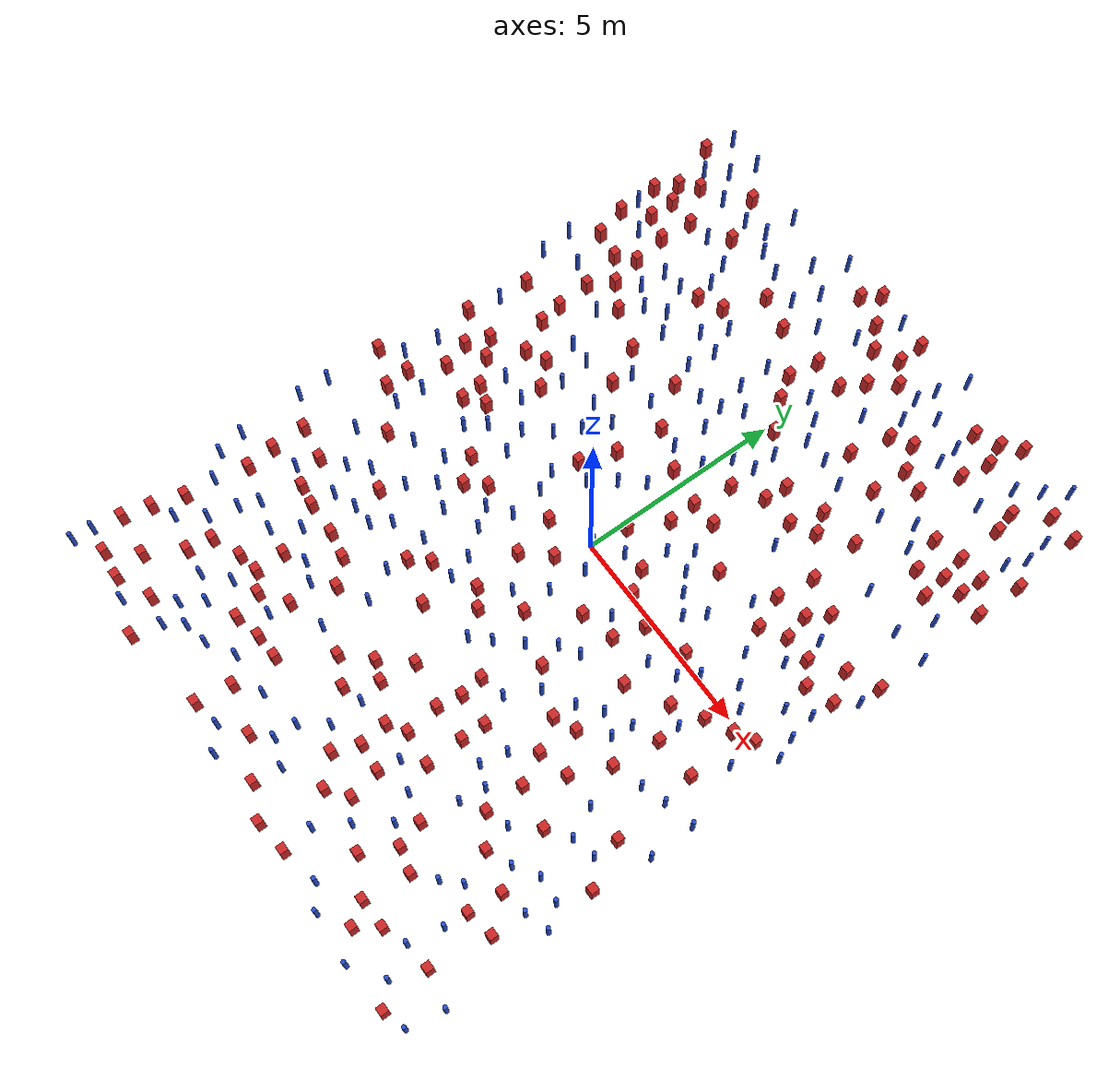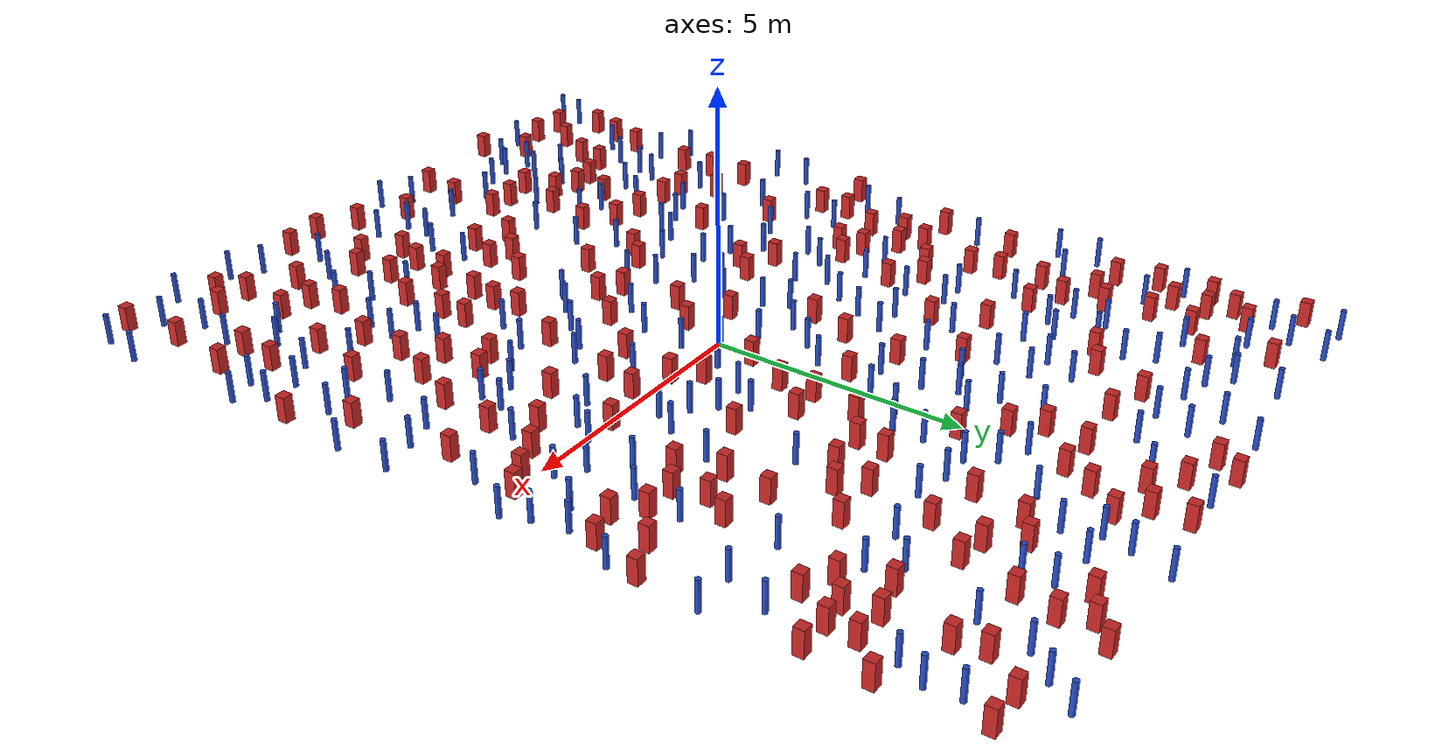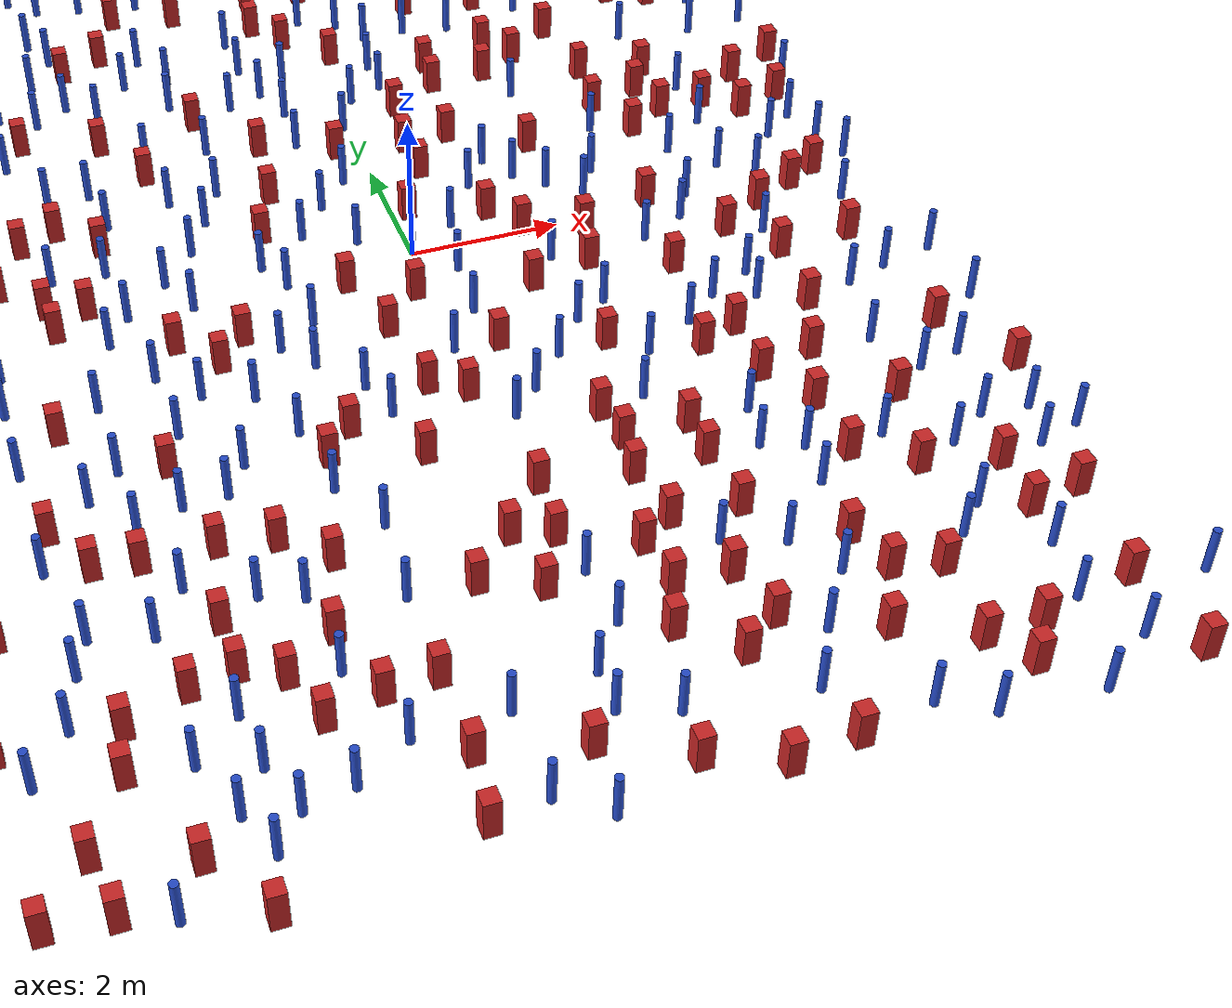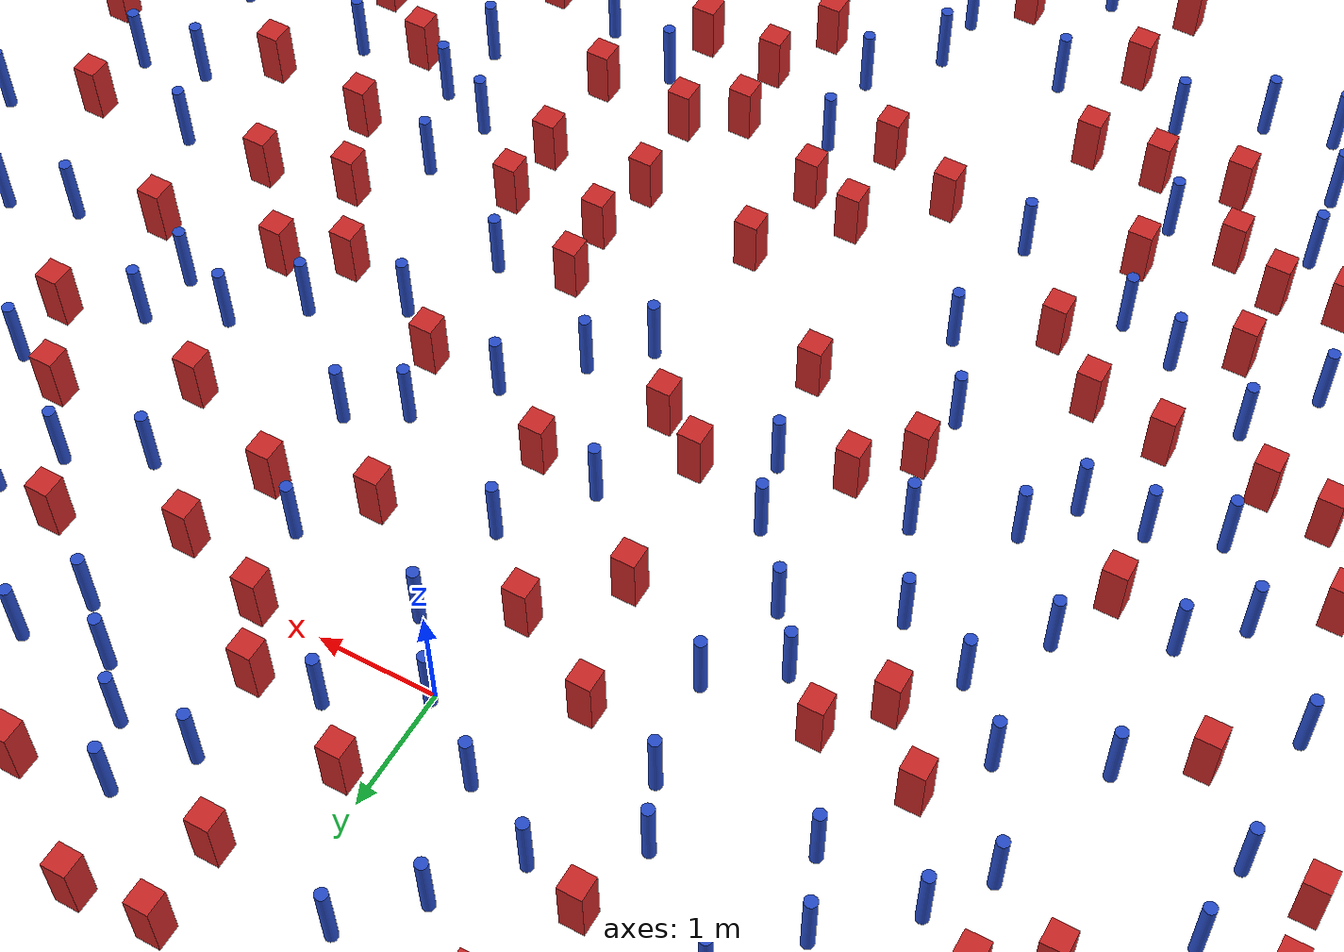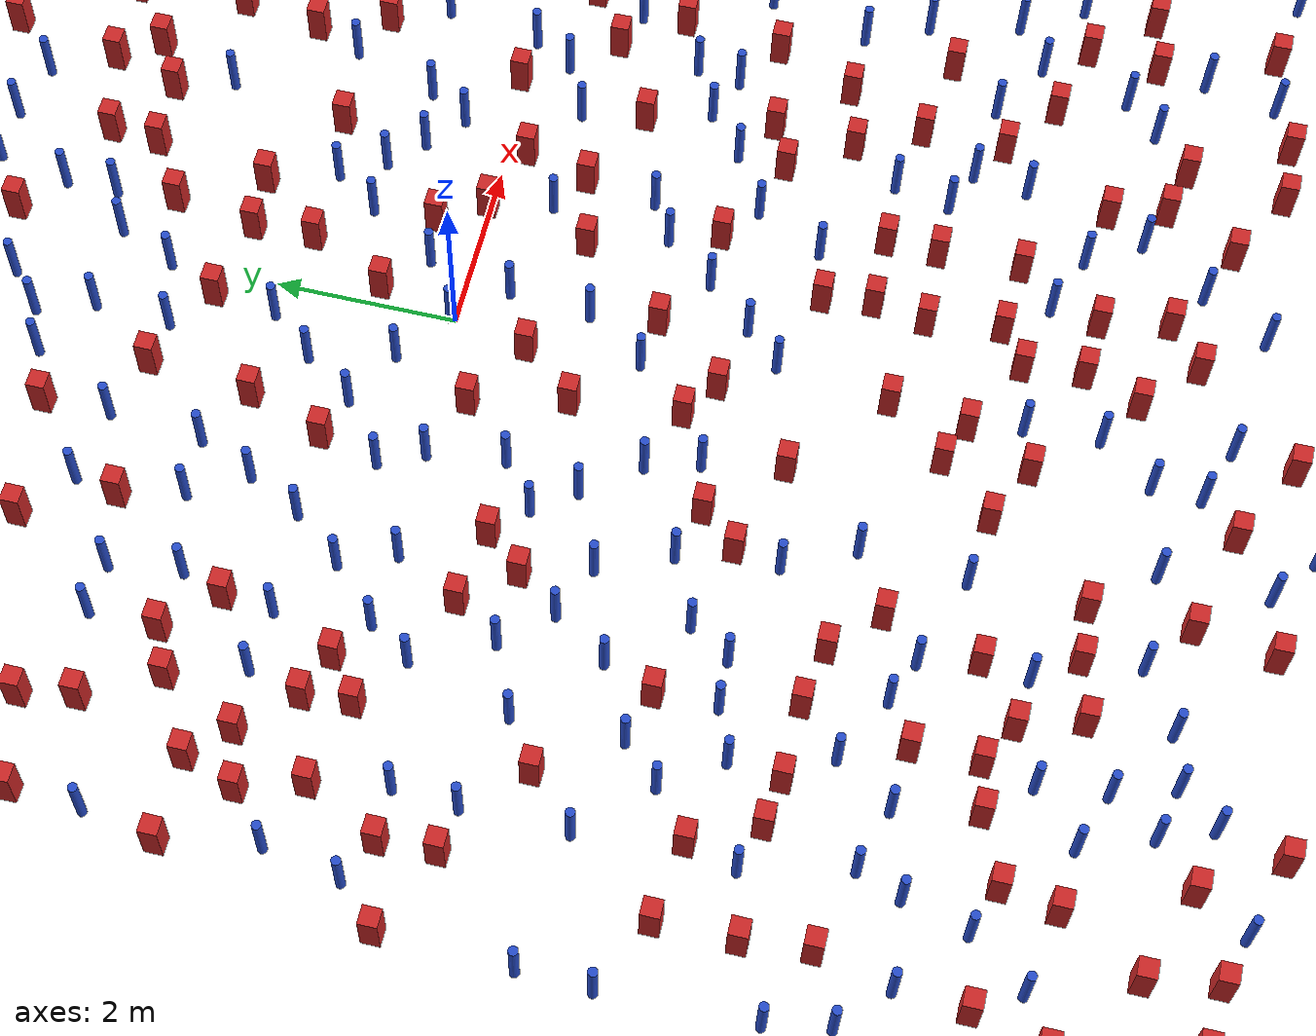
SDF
<sdf version="1.6">
  <model name="dense_78"><model name="pole_obstacle0">
  <static>true</static>
  <pose frame="">-2.11053961955 -1.37780784894 7.38925637345e-09 -8.471706928e-08 1.24976765152e-08 -1.74513093012e-07</pose>
  <link name="link">
  <pose frame="">0 0 0.3 0 -0 0</pose>
    <inertial>
      <mass>1</mass>
      <inertia>
        <ixx>0.145833</ixx>
        <ixy>0</ixy>
        <ixz>0</ixz>
        <iyy>0.145833</iyy>
        <iyz>0</iyz>
        <izz>0.125</izz>
      </inertia>
    </inertial>
    <collision name="collision">
      <geometry>
        <cylinder>
          <radius>0.05</radius>
          <length>.6</length>
        </cylinder>
      </geometry>
      <max_contacts>10</max_contacts>
      <surface>
        <contact>
          <ode/>
        </contact>
        <bounce/>
        <friction>
          <torsional>
            <ode/>
          </torsional>
          <ode/>
        </friction>
      </surface>
    </collision>
    <visual name="visual">
      <geometry>
        <cylinder>
          <radius>0.05</radius>
          <length>.6</length>
        </cylinder>
      </geometry>
      <material>
        <script>
          <name>Gazebo/Blue</name>
          <uri>file://media/materials/scripts/gazebo.material</uri>
        </script>
      </material>
    </visual>
    <self_collide>0</self_collide>
    <kinematic>0</kinematic>
  </link>
</model>
<model name="pole_obstacle1">
  <static>true</static>
  <pose frame="">-3.68166964586 -1.43616901188 7.38925637345e-09 -8.471706928e-08 1.24976765152e-08 -1.74513093012e-07</pose>
  <link name="link">
  <pose frame="">0 0 0.3 0 -0 0</pose>
    <inertial>
      <mass>1</mass>
      <inertia>
        <ixx>0.145833</ixx>
        <ixy>0</ixy>
        <ixz>0</ixz>
        <iyy>0.145833</iyy>
        <iyz>0</iyz>
        <izz>0.125</izz>
      </inertia>
    </inertial>
    <collision name="collision">
      <geometry>
        <cylinder>
          <radius>0.05</radius>
          <length>.6</length>
        </cylinder>
      </geometry>
      <max_contacts>10</max_contacts>
      <surface>
        <contact>
          <ode/>
        </contact>
        <bounce/>
        <friction>
          <torsional>
            <ode/>
          </torsional>
          <ode/>
        </friction>
      </surface>
    </collision>
    <visual name="visual">
      <geometry>
        <cylinder>
          <radius>0.05</radius>
          <length>.6</length>
        </cylinder>
      </geometry>
      <material>
        <script>
          <name>Gazebo/Blue</name>
          <uri>file://media/materials/scripts/gazebo.material</uri>
        </script>
      </material>
    </visual>
    <self_collide>0</self_collide>
    <kinematic>0</kinematic>
  </link>
</model>
<model name="square_post_obstacle0">
  <static>true</static>
  <pose frame="">-6.3512197902 -6.70146782533 1.91545236811e-07 -7.35059704564e-06 1.12565212e-07 2.39332434364e-05</pose>
  <link name="link">
    <pose frame="">0 0 0.25 0 -0 0</pose>
    <inertial>
      <mass>100</mass>
      <inertia>
        <ixx>0.166667</ixx>
        <ixy>0</ixy>
        <ixz>0</ixz>
        <iyy>0.166667</iyy>
        <iyz>0</iyz>
        <izz>0.166667</izz>
      </inertia>
    </inertial>
    <collision name="collision">
      <geometry>
        <box>
          <size>.2 .2 .5</size>
        </box>
      </geometry>
      <max_contacts>10</max_contacts>
      <surface>
        <contact>
          <ode/>
        </contact>
        <bounce/>
        <friction>
          <torsional>
            <ode/>
          </torsional>
          <ode/>
        </friction>
      </surface>
    </collision>
    <visual name="visual">
      <geometry>
        <box>
          <size>.2 .2 .5</size>
        </box>
      </geometry>
      <material>
        <script>
          <name>Gazebo/Red</name>
          <uri>file://media/materials/scripts/gazebo.material</uri>
        </script>
      </material>
    </visual>
    <self_collide>0</self_collide>
    <kinematic>0</kinematic>
  </link>
</model>
<model name="square_post_obstacle1">
  <static>true</static>
  <pose frame="">5.37750317819 5.17159049215 1.91545236811e-07 -7.35059704564e-06 1.12565212e-07 2.39332434364e-05</pose>
  <link name="link">
    <pose frame="">0 0 0.25 0 -0 0</pose>
    <inertial>
      <mass>100</mass>
      <inertia>
        <ixx>0.166667</ixx>
        <ixy>0</ixy>
        <ixz>0</ixz>
        <iyy>0.166667</iyy>
        <iyz>0</iyz>
        <izz>0.166667</izz>
      </inertia>
    </inertial>
    <collision name="collision">
      <geometry>
        <box>
          <size>.2 .2 .5</size>
        </box>
      </geometry>
      <max_contacts>10</max_contacts>
      <surface>
        <contact>
          <ode/>
        </contact>
        <bounce/>
        <friction>
          <torsional>
            <ode/>
          </torsional>
          <ode/>
        </friction>
      </surface>
    </collision>
    <visual name="visual">
      <geometry>
        <box>
          <size>.2 .2 .5</size>
        </box>
      </geometry>
      <material>
        <script>
          <name>Gazebo/Red</name>
          <uri>file://media/materials/scripts/gazebo.material</uri>
        </script>
      </material>
    </visual>
    <self_collide>0</self_collide>
    <kinematic>0</kinematic>
  </link>
</model>
<model name="pole_obstacle2">
  <static>true</static>
  <pose frame="">-5.39988394094 -5.87913840747 7.38925637345e-09 -8.47170692796e-08 1.24976764786e-08 -1.74513093032e-07</pose>
  <link name="link">
  <pose frame="">0 0 0.3 0 -0 0</pose>
    <inertial>
      <mass>1</mass>
      <inertia>
        <ixx>0.145833</ixx>
        <ixy>0</ixy>
        <ixz>0</ixz>
        <iyy>0.145833</iyy>
        <iyz>0</iyz>
        <izz>0.125</izz>
      </inertia>
    </inertial>
    <collision name="collision">
      <geometry>
        <cylinder>
          <radius>0.05</radius>
          <length>.6</length>
        </cylinder>
      </geometry>
      <max_contacts>10</max_contacts>
      <surface>
        <contact>
          <ode/>
        </contact>
        <bounce/>
        <friction>
          <torsional>
            <ode/>
          </torsional>
          <ode/>
        </friction>
      </surface>
    </collision>
    <visual name="visual">
      <geometry>
        <cylinder>
          <radius>0.05</radius>
          <length>.6</length>
        </cylinder>
      </geometry>
      <material>
        <script>
          <name>Gazebo/Blue</name>
          <uri>file://media/materials/scripts/gazebo.material</uri>
        </script>
      </material>
    </visual>
    <self_collide>0</self_collide>
    <kinematic>0</kinematic>
  </link>
</model>
<model name="pole_obstacle3">
  <static>true</static>
  <pose frame="">-4.52345772594 -5.6103119745 7.38925637345e-09 -8.47170692796e-08 1.24976764786e-08 -1.74513093032e-07</pose>
  <link name="link">
  <pose frame="">0 0 0.3 0 -0 0</pose>
    <inertial>
      <mass>1</mass>
      <inertia>
        <ixx>0.145833</ixx>
        <ixy>0</ixy>
        <ixz>0</ixz>
        <iyy>0.145833</iyy>
        <iyz>0</iyz>
        <izz>0.125</izz>
      </inertia>
    </inertial>
    <collision name="collision">
      <geometry>
        <cylinder>
          <radius>0.05</radius>
          <length>.6</length>
        </cylinder>
      </geometry>
      <max_contacts>10</max_contacts>
      <surface>
        <contact>
          <ode/>
        </contact>
        <bounce/>
        <friction>
          <torsional>
            <ode/>
          </torsional>
          <ode/>
        </friction>
      </surface>
    </collision>
    <visual name="visual">
      <geometry>
        <cylinder>
          <radius>0.05</radius>
          <length>.6</length>
        </cylinder>
      </geometry>
      <material>
        <script>
          <name>Gazebo/Blue</name>
          <uri>file://media/materials/scripts/gazebo.material</uri>
        </script>
      </material>
    </visual>
    <self_collide>0</self_collide>
    <kinematic>0</kinematic>
  </link>
</model>
<model name="pole_obstacle4">
  <static>true</static>
  <pose frame="">2.17905710178 -7.80238165837 7.38925637345e-09 -8.47170692798e-08 1.24976765033e-08 -1.74513093019e-07</pose>
  <link name="link">
  <pose frame="">0 0 0.3 0 -0 0</pose>
    <inertial>
      <mass>1</mass>
      <inertia>
        <ixx>0.145833</ixx>
        <ixy>0</ixy>
        <ixz>0</ixz>
        <iyy>0.145833</iyy>
        <iyz>0</iyz>
        <izz>0.125</izz>
      </inertia>
    </inertial>
    <collision name="collision">
      <geometry>
        <cylinder>
          <radius>0.05</radius>
          <length>.6</length>
        </cylinder>
      </geometry>
      <max_contacts>10</max_contacts>
      <surface>
        <contact>
          <ode/>
        </contact>
        <bounce/>
        <friction>
          <torsional>
            <ode/>
          </torsional>
          <ode/>
        </friction>
      </surface>
    </collision>
    <visual name="visual">
      <geometry>
        <cylinder>
          <radius>0.05</radius>
          <length>.6</length>
        </cylinder>
      </geometry>
      <material>
        <script>
          <name>Gazebo/Blue</name>
          <uri>file://media/materials/scripts/gazebo.material</uri>
        </script>
      </material>
    </visual>
    <self_collide>0</self_collide>
    <kinematic>0</kinematic>
  </link>
</model>
<model name="pole_obstacle5">
  <static>true</static>
  <pose frame="">-2.810442116 -6.70199553143 7.38925637345e-09 -8.47170692798e-08 1.24976765033e-08 -1.74513093019e-07</pose>
  <link name="link">
  <pose frame="">0 0 0.3 0 -0 0</pose>
    <inertial>
      <mass>1</mass>
      <inertia>
        <ixx>0.145833</ixx>
        <ixy>0</ixy>
        <ixz>0</ixz>
        <iyy>0.145833</iyy>
        <iyz>0</iyz>
        <izz>0.125</izz>
      </inertia>
    </inertial>
    <collision name="collision">
      <geometry>
        <cylinder>
          <radius>0.05</radius>
          <length>.6</length>
        </cylinder>
      </geometry>
      <max_contacts>10</max_contacts>
      <surface>
        <contact>
          <ode/>
        </contact>
        <bounce/>
        <friction>
          <torsional>
            <ode/>
          </torsional>
          <ode/>
        </friction>
      </surface>
    </collision>
    <visual name="visual">
      <geometry>
        <cylinder>
          <radius>0.05</radius>
          <length>.6</length>
        </cylinder>
      </geometry>
      <material>
        <script>
          <name>Gazebo/Blue</name>
          <uri>file://media/materials/scripts/gazebo.material</uri>
        </script>
      </material>
    </visual>
    <self_collide>0</self_collide>
    <kinematic>0</kinematic>
  </link>
</model>
<model name="pole_obstacle6">
  <static>true</static>
  <pose frame="">-6.87049068792 -8.80188207975 7.38925637345e-09 -8.471706928e-08 1.24976765081e-08 -1.74513093015e-07</pose>
  <link name="link">
  <pose frame="">0 0 0.3 0 -0 0</pose>
    <inertial>
      <mass>1</mass>
      <inertia>
        <ixx>0.145833</ixx>
        <ixy>0</ixy>
        <ixz>0</ixz>
        <iyy>0.145833</iyy>
        <iyz>0</iyz>
        <izz>0.125</izz>
      </inertia>
    </inertial>
    <collision name="collision">
      <geometry>
        <cylinder>
          <radius>0.05</radius>
          <length>.6</length>
        </cylinder>
      </geometry>
      <max_contacts>10</max_contacts>
      <surface>
        <contact>
          <ode/>
        </contact>
        <bounce/>
        <friction>
          <torsional>
            <ode/>
          </torsional>
          <ode/>
        </friction>
      </surface>
    </collision>
    <visual name="visual">
      <geometry>
        <cylinder>
          <radius>0.05</radius>
          <length>.6</length>
        </cylinder>
      </geometry>
      <material>
        <script>
          <name>Gazebo/Blue</name>
          <uri>file://media/materials/scripts/gazebo.material</uri>
        </script>
      </material>
    </visual>
    <self_collide>0</self_collide>
    <kinematic>0</kinematic>
  </link>
</model>
<model name="square_post_obstacle2">
  <static>true</static>
  <pose frame="">-3.41473660765 3.73516218627 1.91545236811e-07 -7.35059704564e-06 1.12565212e-07 2.39332434364e-05</pose>
  <link name="link">
    <pose frame="">0 0 0.25 0 -0 0</pose>
    <inertial>
      <mass>100</mass>
      <inertia>
        <ixx>0.166667</ixx>
        <ixy>0</ixy>
        <ixz>0</ixz>
        <iyy>0.166667</iyy>
        <iyz>0</iyz>
        <izz>0.166667</izz>
      </inertia>
    </inertial>
    <collision name="collision">
      <geometry>
        <box>
          <size>.2 .2 .5</size>
        </box>
      </geometry>
      <max_contacts>10</max_contacts>
      <surface>
        <contact>
          <ode/>
        </contact>
        <bounce/>
        <friction>
          <torsional>
            <ode/>
          </torsional>
          <ode/>
        </friction>
      </surface>
    </collision>
    <visual name="visual">
      <geometry>
        <box>
          <size>.2 .2 .5</size>
        </box>
      </geometry>
      <material>
        <script>
          <name>Gazebo/Red</name>
          <uri>file://media/materials/scripts/gazebo.material</uri>
        </script>
      </material>
    </visual>
    <self_collide>0</self_collide>
    <kinematic>0</kinematic>
  </link>
</model>
<model name="square_post_obstacle3">
  <static>true</static>
  <pose frame="">0.197763322349 0.872626212082 1.91545236811e-07 -7.35059704564e-06 1.12565212e-07 2.39332434364e-05</pose>
  <link name="link">
    <pose frame="">0 0 0.25 0 -0 0</pose>
    <inertial>
      <mass>100</mass>
      <inertia>
        <ixx>0.166667</ixx>
        <ixy>0</ixy>
        <ixz>0</ixz>
        <iyy>0.166667</iyy>
        <iyz>0</iyz>
        <izz>0.166667</izz>
      </inertia>
    </inertial>
    <collision name="collision">
      <geometry>
        <box>
          <size>.2 .2 .5</size>
        </box>
      </geometry>
      <max_contacts>10</max_contacts>
      <surface>
        <contact>
          <ode/>
        </contact>
        <bounce/>
        <friction>
          <torsional>
            <ode/>
          </torsional>
          <ode/>
        </friction>
      </surface>
    </collision>
    <visual name="visual">
      <geometry>
        <box>
          <size>.2 .2 .5</size>
        </box>
      </geometry>
      <material>
        <script>
          <name>Gazebo/Red</name>
          <uri>file://media/materials/scripts/gazebo.material</uri>
        </script>
      </material>
    </visual>
    <self_collide>0</self_collide>
    <kinematic>0</kinematic>
  </link>
</model>
<model name="square_post_obstacle4">
  <static>true</static>
  <pose frame="">-0.0634980253902 -5.59062837744 1.91545236811e-07 -7.35059704564e-06 1.12565212e-07 2.39332434364e-05</pose>
  <link name="link">
    <pose frame="">0 0 0.25 0 -0 0</pose>
    <inertial>
      <mass>100</mass>
      <inertia>
        <ixx>0.166667</ixx>
        <ixy>0</ixy>
        <ixz>0</ixz>
        <iyy>0.166667</iyy>
        <iyz>0</iyz>
        <izz>0.166667</izz>
      </inertia>
    </inertial>
    <collision name="collision">
      <geometry>
        <box>
          <size>.2 .2 .5</size>
        </box>
      </geometry>
      <max_contacts>10</max_contacts>
      <surface>
        <contact>
          <ode/>
        </contact>
        <bounce/>
        <friction>
          <torsional>
            <ode/>
          </torsional>
          <ode/>
        </friction>
      </surface>
    </collision>
    <visual name="visual">
      <geometry>
        <box>
          <size>.2 .2 .5</size>
        </box>
      </geometry>
      <material>
        <script>
          <name>Gazebo/Red</name>
          <uri>file://media/materials/scripts/gazebo.material</uri>
        </script>
      </material>
    </visual>
    <self_collide>0</self_collide>
    <kinematic>0</kinematic>
  </link>
</model>
<model name="pole_obstacle7">
  <static>true</static>
  <pose frame="">2.14908445065 -2.89493434447 7.38925637345e-09 -8.47170692798e-08 1.24976764939e-08 -1.74513093025e-07</pose>
  <link name="link">
  <pose frame="">0 0 0.3 0 -0 0</pose>
    <inertial>
      <mass>1</mass>
      <inertia>
        <ixx>0.145833</ixx>
        <ixy>0</ixy>
        <ixz>0</ixz>
        <iyy>0.145833</iyy>
        <iyz>0</iyz>
        <izz>0.125</izz>
      </inertia>
    </inertial>
    <collision name="collision">
      <geometry>
        <cylinder>
          <radius>0.05</radius>
          <length>.6</length>
        </cylinder>
      </geometry>
      <max_contacts>10</max_contacts>
      <surface>
        <contact>
          <ode/>
        </contact>
        <bounce/>
        <friction>
          <torsional>
            <ode/>
          </torsional>
          <ode/>
        </friction>
      </surface>
    </collision>
    <visual name="visual">
      <geometry>
        <cylinder>
          <radius>0.05</radius>
          <length>.6</length>
        </cylinder>
      </geometry>
      <material>
        <script>
          <name>Gazebo/Blue</name>
          <uri>file://media/materials/scripts/gazebo.material</uri>
        </script>
      </material>
    </visual>
    <self_collide>0</self_collide>
    <kinematic>0</kinematic>
  </link>
</model>
<model name="pole_obstacle8">
  <static>true</static>
  <pose frame="">1.99184411224 -1.75286387107 7.38925637345e-09 -8.47170692795e-08 1.24976764702e-08 -1.74513093038e-07</pose>
  <link name="link">
  <pose frame="">0 0 0.3 0 -0 0</pose>
    <inertial>
      <mass>1</mass>
      <inertia>
        <ixx>0.145833</ixx>
        <ixy>0</ixy>
        <ixz>0</ixz>
        <iyy>0.145833</iyy>
        <iyz>0</iyz>
        <izz>0.125</izz>
      </inertia>
    </inertial>
    <collision name="collision">
      <geometry>
        <cylinder>
          <radius>0.05</radius>
          <length>.6</length>
        </cylinder>
      </geometry>
      <max_contacts>10</max_contacts>
      <surface>
        <contact>
          <ode/>
        </contact>
        <bounce/>
        <friction>
          <torsional>
            <ode/>
          </torsional>
          <ode/>
        </friction>
      </surface>
    </collision>
    <visual name="visual">
      <geometry>
        <cylinder>
          <radius>0.05</radius>
          <length>.6</length>
        </cylinder>
      </geometry>
      <material>
        <script>
          <name>Gazebo/Blue</name>
          <uri>file://media/materials/scripts/gazebo.material</uri>
        </script>
      </material>
    </visual>
    <self_collide>0</self_collide>
    <kinematic>0</kinematic>
  </link>
</model>
<model name="square_post_obstacle5">
  <static>true</static>
  <pose frame="">-5.07548429831 -6.76126637863 1.91545236811e-07 -7.35059704564e-06 1.12565212e-07 2.39332434364e-05</pose>
  <link name="link">
    <pose frame="">0 0 0.25 0 -0 0</pose>
    <inertial>
      <mass>100</mass>
      <inertia>
        <ixx>0.166667</ixx>
        <ixy>0</ixy>
        <ixz>0</ixz>
        <iyy>0.166667</iyy>
        <iyz>0</iyz>
        <izz>0.166667</izz>
      </inertia>
    </inertial>
    <collision name="collision">
      <geometry>
        <box>
          <size>.2 .2 .5</size>
        </box>
      </geometry>
      <max_contacts>10</max_contacts>
      <surface>
        <contact>
          <ode/>
        </contact>
        <bounce/>
        <friction>
          <torsional>
            <ode/>
          </torsional>
          <ode/>
        </friction>
      </surface>
    </collision>
    <visual name="visual">
      <geometry>
        <box>
          <size>.2 .2 .5</size>
        </box>
      </geometry>
      <material>
        <script>
          <name>Gazebo/Red</name>
          <uri>file://media/materials/scripts/gazebo.material</uri>
        </script>
      </material>
    </visual>
    <self_collide>0</self_collide>
    <kinematic>0</kinematic>
  </link>
</model>
<model name="square_post_obstacle6">
  <static>true</static>
  <pose frame="">-1.46319063719 1.82636005905 1.91545236811e-07 -7.35059704564e-06 1.12565212e-07 2.39332434364e-05</pose>
  <link name="link">
    <pose frame="">0 0 0.25 0 -0 0</pose>
    <inertial>
      <mass>100</mass>
      <inertia>
        <ixx>0.166667</ixx>
        <ixy>0</ixy>
        <ixz>0</ixz>
        <iyy>0.166667</iyy>
        <iyz>0</iyz>
        <izz>0.166667</izz>
      </inertia>
    </inertial>
    <collision name="collision">
      <geometry>
        <box>
          <size>.2 .2 .5</size>
        </box>
      </geometry>
      <max_contacts>10</max_contacts>
      <surface>
        <contact>
          <ode/>
        </contact>
        <bounce/>
        <friction>
          <torsional>
            <ode/>
          </torsional>
          <ode/>
        </friction>
      </surface>
    </collision>
    <visual name="visual">
      <geometry>
        <box>
          <size>.2 .2 .5</size>
        </box>
      </geometry>
      <material>
        <script>
          <name>Gazebo/Red</name>
          <uri>file://media/materials/scripts/gazebo.material</uri>
        </script>
      </material>
    </visual>
    <self_collide>0</self_collide>
    <kinematic>0</kinematic>
  </link>
</model>
<model name="square_post_obstacle7">
  <static>true</static>
  <pose frame="">2.50515203167 4.65884370068 1.91545236811e-07 -7.35059704564e-06 1.12565212e-07 2.39332434364e-05</pose>
  <link name="link">
    <pose frame="">0 0 0.25 0 -0 0</pose>
    <inertial>
      <mass>100</mass>
      <inertia>
        <ixx>0.166667</ixx>
        <ixy>0</ixy>
        <ixz>0</ixz>
        <iyy>0.166667</iyy>
        <iyz>0</iyz>
        <izz>0.166667</izz>
      </inertia>
    </inertial>
    <collision name="collision">
      <geometry>
        <box>
          <size>.2 .2 .5</size>
        </box>
      </geometry>
      <max_contacts>10</max_contacts>
      <surface>
        <contact>
          <ode/>
        </contact>
        <bounce/>
        <friction>
          <torsional>
            <ode/>
          </torsional>
          <ode/>
        </friction>
      </surface>
    </collision>
    <visual name="visual">
      <geometry>
        <box>
          <size>.2 .2 .5</size>
        </box>
      </geometry>
      <material>
        <script>
          <name>Gazebo/Red</name>
          <uri>file://media/materials/scripts/gazebo.material</uri>
        </script>
      </material>
    </visual>
    <self_collide>0</self_collide>
    <kinematic>0</kinematic>
  </link>
</model>
<model name="pole_obstacle9">
  <static>true</static>
  <pose frame="">4.5817701289 0.596697649328 7.38925637345e-09 -8.47170692799e-08 1.24976765038e-08 -1.74513093018e-07</pose>
  <link name="link">
  <pose frame="">0 0 0.3 0 -0 0</pose>
    <inertial>
      <mass>1</mass>
      <inertia>
        <ixx>0.145833</ixx>
        <ixy>0</ixy>
        <ixz>0</ixz>
        <iyy>0.145833</iyy>
        <iyz>0</iyz>
        <izz>0.125</izz>
      </inertia>
    </inertial>
    <collision name="collision">
      <geometry>
        <cylinder>
          <radius>0.05</radius>
          <length>.6</length>
        </cylinder>
      </geometry>
      <max_contacts>10</max_contacts>
      <surface>
        <contact>
          <ode/>
        </contact>
        <bounce/>
        <friction>
          <torsional>
            <ode/>
          </torsional>
          <ode/>
        </friction>
      </surface>
    </collision>
    <visual name="visual">
      <geometry>
        <cylinder>
          <radius>0.05</radius>
          <length>.6</length>
        </cylinder>
      </geometry>
      <material>
        <script>
          <name>Gazebo/Blue</name>
          <uri>file://media/materials/scripts/gazebo.material</uri>
        </script>
      </material>
    </visual>
    <self_collide>0</self_collide>
    <kinematic>0</kinematic>
  </link>
</model>
<model name="pole_obstacle10">
  <static>true</static>
  <pose frame="">5.64205923662 4.10121407407 7.38925637345e-09 -8.47170692796e-08 1.24976764786e-08 -1.74513093032e-07</pose>
  <link name="link">
  <pose frame="">0 0 0.3 0 -0 0</pose>
    <inertial>
      <mass>1</mass>
      <inertia>
        <ixx>0.145833</ixx>
        <ixy>0</ixy>
        <ixz>0</ixz>
        <iyy>0.145833</iyy>
        <iyz>0</iyz>
        <izz>0.125</izz>
      </inertia>
    </inertial>
    <collision name="collision">
      <geometry>
        <cylinder>
          <radius>0.05</radius>
          <length>.6</length>
        </cylinder>
      </geometry>
      <max_contacts>10</max_contacts>
      <surface>
        <contact>
          <ode/>
        </contact>
        <bounce/>
        <friction>
          <torsional>
            <ode/>
          </torsional>
          <ode/>
        </friction>
      </surface>
    </collision>
    <visual name="visual">
      <geometry>
        <cylinder>
          <radius>0.05</radius>
          <length>.6</length>
        </cylinder>
      </geometry>
      <material>
        <script>
          <name>Gazebo/Blue</name>
          <uri>file://media/materials/scripts/gazebo.material</uri>
        </script>
      </material>
    </visual>
    <self_collide>0</self_collide>
    <kinematic>0</kinematic>
  </link>
</model>
<model name="pole_obstacle11">
  <static>true</static>
  <pose frame="">4.08247064523 1.15306410399 7.38925637345e-09 -8.471706928e-08 1.24976765134e-08 -1.74513093015e-07</pose>
  <link name="link">
  <pose frame="">0 0 0.3 0 -0 0</pose>
    <inertial>
      <mass>1</mass>
      <inertia>
        <ixx>0.145833</ixx>
        <ixy>0</ixy>
        <ixz>0</ixz>
        <iyy>0.145833</iyy>
        <iyz>0</iyz>
        <izz>0.125</izz>
      </inertia>
    </inertial>
    <collision name="collision">
      <geometry>
        <cylinder>
          <radius>0.05</radius>
          <length>.6</length>
        </cylinder>
      </geometry>
      <max_contacts>10</max_contacts>
      <surface>
        <contact>
          <ode/>
        </contact>
        <bounce/>
        <friction>
          <torsional>
            <ode/>
          </torsional>
          <ode/>
        </friction>
      </surface>
    </collision>
    <visual name="visual">
      <geometry>
        <cylinder>
          <radius>0.05</radius>
          <length>.6</length>
        </cylinder>
      </geometry>
      <material>
        <script>
          <name>Gazebo/Blue</name>
          <uri>file://media/materials/scripts/gazebo.material</uri>
        </script>
      </material>
    </visual>
    <self_collide>0</self_collide>
    <kinematic>0</kinematic>
  </link>
</model>
<model name="pole_obstacle12">
  <static>true</static>
  <pose frame="">-2.02660401099 3.21819011499 7.38925637345e-09 -8.47170692793e-08 1.24976764444e-08 -1.74513093039e-07</pose>
  <link name="link">
  <pose frame="">0 0 0.3 0 -0 0</pose>
    <inertial>
      <mass>1</mass>
      <inertia>
        <ixx>0.145833</ixx>
        <ixy>0</ixy>
        <ixz>0</ixz>
        <iyy>0.145833</iyy>
        <iyz>0</iyz>
        <izz>0.125</izz>
      </inertia>
    </inertial>
    <collision name="collision">
      <geometry>
        <cylinder>
          <radius>0.05</radius>
          <length>.6</length>
        </cylinder>
      </geometry>
      <max_contacts>10</max_contacts>
      <surface>
        <contact>
          <ode/>
        </contact>
        <bounce/>
        <friction>
          <torsional>
            <ode/>
          </torsional>
          <ode/>
        </friction>
      </surface>
    </collision>
    <visual name="visual">
      <geometry>
        <cylinder>
          <radius>0.05</radius>
          <length>.6</length>
        </cylinder>
      </geometry>
      <material>
        <script>
          <name>Gazebo/Blue</name>
          <uri>file://media/materials/scripts/gazebo.material</uri>
        </script>
      </material>
    </visual>
    <self_collide>0</self_collide>
    <kinematic>0</kinematic>
  </link>
</model>
<model name="square_post_obstacle8">
  <static>true</static>
  <pose frame="">1.7114251339 -2.5676912984 1.91545236811e-07 -7.35059704564e-06 1.12565212e-07 2.39332434364e-05</pose>
  <link name="link">
    <pose frame="">0 0 0.25 0 -0 0</pose>
    <inertial>
      <mass>100</mass>
      <inertia>
        <ixx>0.166667</ixx>
        <ixy>0</ixy>
        <ixz>0</ixz>
        <iyy>0.166667</iyy>
        <iyz>0</iyz>
        <izz>0.166667</izz>
      </inertia>
    </inertial>
    <collision name="collision">
      <geometry>
        <box>
          <size>.2 .2 .5</size>
        </box>
      </geometry>
      <max_contacts>10</max_contacts>
      <surface>
        <contact>
          <ode/>
        </contact>
        <bounce/>
        <friction>
          <torsional>
            <ode/>
          </torsional>
          <ode/>
        </friction>
      </surface>
    </collision>
    <visual name="visual">
      <geometry>
        <box>
          <size>.2 .2 .5</size>
        </box>
      </geometry>
      <material>
        <script>
          <name>Gazebo/Red</name>
          <uri>file://media/materials/scripts/gazebo.material</uri>
        </script>
      </material>
    </visual>
    <self_collide>0</self_collide>
    <kinematic>0</kinematic>
  </link>
</model>
<model name="square_post_obstacle9">
  <static>true</static>
  <pose frame="">1.21343042922 -7.86855493327 1.91545236811e-07 -7.35059704564e-06 1.12565212e-07 2.39332434364e-05</pose>
  <link name="link">
    <pose frame="">0 0 0.25 0 -0 0</pose>
    <inertial>
      <mass>100</mass>
      <inertia>
        <ixx>0.166667</ixx>
        <ixy>0</ixy>
        <ixz>0</ixz>
        <iyy>0.166667</iyy>
        <iyz>0</iyz>
        <izz>0.166667</izz>
      </inertia>
    </inertial>
    <collision name="collision">
      <geometry>
        <box>
          <size>.2 .2 .5</size>
        </box>
      </geometry>
      <max_contacts>10</max_contacts>
      <surface>
        <contact>
          <ode/>
        </contact>
        <bounce/>
        <friction>
          <torsional>
            <ode/>
          </torsional>
          <ode/>
        </friction>
      </surface>
    </collision>
    <visual name="visual">
      <geometry>
        <box>
          <size>.2 .2 .5</size>
        </box>
      </geometry>
      <material>
        <script>
          <name>Gazebo/Red</name>
          <uri>file://media/materials/scripts/gazebo.material</uri>
        </script>
      </material>
    </visual>
    <self_collide>0</self_collide>
    <kinematic>0</kinematic>
  </link>
</model>
<model name="pole_obstacle13">
  <static>true</static>
  <pose frame="">4.76619048261 1.69995667515 7.38925637345e-09 -8.471706928e-08 1.24976765134e-08 -1.74513093015e-07</pose>
  <link name="link">
  <pose frame="">0 0 0.3 0 -0 0</pose>
    <inertial>
      <mass>1</mass>
      <inertia>
        <ixx>0.145833</ixx>
        <ixy>0</ixy>
        <ixz>0</ixz>
        <iyy>0.145833</iyy>
        <iyz>0</iyz>
        <izz>0.125</izz>
      </inertia>
    </inertial>
    <collision name="collision">
      <geometry>
        <cylinder>
          <radius>0.05</radius>
          <length>.6</length>
        </cylinder>
      </geometry>
      <max_contacts>10</max_contacts>
      <surface>
        <contact>
          <ode/>
        </contact>
        <bounce/>
        <friction>
          <torsional>
            <ode/>
          </torsional>
          <ode/>
        </friction>
      </surface>
    </collision>
    <visual name="visual">
      <geometry>
        <cylinder>
          <radius>0.05</radius>
          <length>.6</length>
        </cylinder>
      </geometry>
      <material>
        <script>
          <name>Gazebo/Blue</name>
          <uri>file://media/materials/scripts/gazebo.material</uri>
        </script>
      </material>
    </visual>
    <self_collide>0</self_collide>
    <kinematic>0</kinematic>
  </link>
</model>
<model name="square_post_obstacle10">
  <static>true</static>
  <pose frame="">0.76890209243 3.38052567171 1.91545236811e-07 -7.35059704564e-06 1.12565212e-07 2.39332434364e-05</pose>
  <link name="link">
    <pose frame="">0 0 0.25 0 -0 0</pose>
    <inertial>
      <mass>100</mass>
      <inertia>
        <ixx>0.166667</ixx>
        <ixy>0</ixy>
        <ixz>0</ixz>
        <iyy>0.166667</iyy>
        <iyz>0</iyz>
        <izz>0.166667</izz>
      </inertia>
    </inertial>
    <collision name="collision">
      <geometry>
        <box>
          <size>.2 .2 .5</size>
        </box>
      </geometry>
      <max_contacts>10</max_contacts>
      <surface>
        <contact>
          <ode/>
        </contact>
        <bounce/>
        <friction>
          <torsional>
            <ode/>
          </torsional>
          <ode/>
        </friction>
      </surface>
    </collision>
    <visual name="visual">
      <geometry>
        <box>
          <size>.2 .2 .5</size>
        </box>
      </geometry>
      <material>
        <script>
          <name>Gazebo/Red</name>
          <uri>file://media/materials/scripts/gazebo.material</uri>
        </script>
      </material>
    </visual>
    <self_collide>0</self_collide>
    <kinematic>0</kinematic>
  </link>
</model>
<model name="square_post_obstacle11">
  <static>true</static>
  <pose frame="">5.72869029466 -9.37958939106 1.91545236811e-07 -7.35059704564e-06 1.12565212e-07 2.39332434364e-05</pose>
  <link name="link">
    <pose frame="">0 0 0.25 0 -0 0</pose>
    <inertial>
      <mass>100</mass>
      <inertia>
        <ixx>0.166667</ixx>
        <ixy>0</ixy>
        <ixz>0</ixz>
        <iyy>0.166667</iyy>
        <iyz>0</iyz>
        <izz>0.166667</izz>
      </inertia>
    </inertial>
    <collision name="collision">
      <geometry>
        <box>
          <size>.2 .2 .5</size>
        </box>
      </geometry>
      <max_contacts>10</max_contacts>
      <surface>
        <contact>
          <ode/>
        </contact>
        <bounce/>
        <friction>
          <torsional>
            <ode/>
          </torsional>
          <ode/>
        </friction>
      </surface>
    </collision>
    <visual name="visual">
      <geometry>
        <box>
          <size>.2 .2 .5</size>
        </box>
      </geometry>
      <material>
        <script>
          <name>Gazebo/Red</name>
          <uri>file://media/materials/scripts/gazebo.material</uri>
        </script>
      </material>
    </visual>
    <self_collide>0</self_collide>
    <kinematic>0</kinematic>
  </link>
</model>
<model name="pole_obstacle14">
  <static>true</static>
  <pose frame="">-6.65724431521 9.31307978637 7.38925637345e-09 -8.471706928e-08 1.24976765081e-08 -1.74513093015e-07</pose>
  <link name="link">
  <pose frame="">0 0 0.3 0 -0 0</pose>
    <inertial>
      <mass>1</mass>
      <inertia>
        <ixx>0.145833</ixx>
        <ixy>0</ixy>
        <ixz>0</ixz>
        <iyy>0.145833</iyy>
        <iyz>0</iyz>
        <izz>0.125</izz>
      </inertia>
    </inertial>
    <collision name="collision">
      <geometry>
        <cylinder>
          <radius>0.05</radius>
          <length>.6</length>
        </cylinder>
      </geometry>
      <max_contacts>10</max_contacts>
      <surface>
        <contact>
          <ode/>
        </contact>
        <bounce/>
        <friction>
          <torsional>
            <ode/>
          </torsional>
          <ode/>
        </friction>
      </surface>
    </collision>
    <visual name="visual">
      <geometry>
        <cylinder>
          <radius>0.05</radius>
          <length>.6</length>
        </cylinder>
      </geometry>
      <material>
        <script>
          <name>Gazebo/Blue</name>
          <uri>file://media/materials/scripts/gazebo.material</uri>
        </script>
      </material>
    </visual>
    <self_collide>0</self_collide>
    <kinematic>0</kinematic>
  </link>
</model>
<model name="pole_obstacle15">
  <static>true</static>
  <pose frame="">5.86521102826 -0.665007750339 7.38925637345e-09 -8.47170692799e-08 1.24976765038e-08 -1.74513093018e-07</pose>
  <link name="link">
  <pose frame="">0 0 0.3 0 -0 0</pose>
    <inertial>
      <mass>1</mass>
      <inertia>
        <ixx>0.145833</ixx>
        <ixy>0</ixy>
        <ixz>0</ixz>
        <iyy>0.145833</iyy>
        <iyz>0</iyz>
        <izz>0.125</izz>
      </inertia>
    </inertial>
    <collision name="collision">
      <geometry>
        <cylinder>
          <radius>0.05</radius>
          <length>.6</length>
        </cylinder>
      </geometry>
      <max_contacts>10</max_contacts>
      <surface>
        <contact>
          <ode/>
        </contact>
        <bounce/>
        <friction>
          <torsional>
            <ode/>
          </torsional>
          <ode/>
        </friction>
      </surface>
    </collision>
    <visual name="visual">
      <geometry>
        <cylinder>
          <radius>0.05</radius>
          <length>.6</length>
        </cylinder>
      </geometry>
      <material>
        <script>
          <name>Gazebo/Blue</name>
          <uri>file://media/materials/scripts/gazebo.material</uri>
        </script>
      </material>
    </visual>
    <self_collide>0</self_collide>
    <kinematic>0</kinematic>
  </link>
</model>
<model name="square_post_obstacle12">
  <static>true</static>
  <pose frame="">3.25410924652 -3.74712516584 1.91545236811e-07 -7.35059704564e-06 1.12565212e-07 2.39332434364e-05</pose>
  <link name="link">
    <pose frame="">0 0 0.25 0 -0 0</pose>
    <inertial>
      <mass>100</mass>
      <inertia>
        <ixx>0.166667</ixx>
        <ixy>0</ixy>
        <ixz>0</ixz>
        <iyy>0.166667</iyy>
        <iyz>0</iyz>
        <izz>0.166667</izz>
      </inertia>
    </inertial>
    <collision name="collision">
      <geometry>
        <box>
          <size>.2 .2 .5</size>
        </box>
      </geometry>
      <max_contacts>10</max_contacts>
      <surface>
        <contact>
          <ode/>
        </contact>
        <bounce/>
        <friction>
          <torsional>
            <ode/>
          </torsional>
          <ode/>
        </friction>
      </surface>
    </collision>
    <visual name="visual">
      <geometry>
        <box>
          <size>.2 .2 .5</size>
        </box>
      </geometry>
      <material>
        <script>
          <name>Gazebo/Red</name>
          <uri>file://media/materials/scripts/gazebo.material</uri>
        </script>
      </material>
    </visual>
    <self_collide>0</self_collide>
    <kinematic>0</kinematic>
  </link>
</model>
<model name="pole_obstacle16">
  <static>true</static>
  <pose frame="">-2.77548789486 2.13338144986 7.38925637345e-09 -8.47170692798e-08 1.24976764939e-08 -1.74513093025e-07</pose>
  <link name="link">
  <pose frame="">0 0 0.3 0 -0 0</pose>
    <inertial>
      <mass>1</mass>
      <inertia>
        <ixx>0.145833</ixx>
        <ixy>0</ixy>
        <ixz>0</ixz>
        <iyy>0.145833</iyy>
        <iyz>0</iyz>
        <izz>0.125</izz>
      </inertia>
    </inertial>
    <collision name="collision">
      <geometry>
        <cylinder>
          <radius>0.05</radius>
          <length>.6</length>
        </cylinder>
      </geometry>
      <max_contacts>10</max_contacts>
      <surface>
        <contact>
          <ode/>
        </contact>
        <bounce/>
        <friction>
          <torsional>
            <ode/>
          </torsional>
          <ode/>
        </friction>
      </surface>
    </collision>
    <visual name="visual">
      <geometry>
        <cylinder>
          <radius>0.05</radius>
          <length>.6</length>
        </cylinder>
      </geometry>
      <material>
        <script>
          <name>Gazebo/Blue</name>
          <uri>file://media/materials/scripts/gazebo.material</uri>
        </script>
      </material>
    </visual>
    <self_collide>0</self_collide>
    <kinematic>0</kinematic>
  </link>
</model>
<model name="pole_obstacle17">
  <static>true</static>
  <pose frame="">-0.0524319184626 3.18661917495 7.38925637345e-09 -8.47170692793e-08 1.24976764354e-08 -1.74513093044e-07</pose>
  <link name="link">
  <pose frame="">0 0 0.3 0 -0 0</pose>
    <inertial>
      <mass>1</mass>
      <inertia>
        <ixx>0.145833</ixx>
        <ixy>0</ixy>
        <ixz>0</ixz>
        <iyy>0.145833</iyy>
        <iyz>0</iyz>
        <izz>0.125</izz>
      </inertia>
    </inertial>
    <collision name="collision">
      <geometry>
        <cylinder>
          <radius>0.05</radius>
          <length>.6</length>
        </cylinder>
      </geometry>
      <max_contacts>10</max_contacts>
      <surface>
        <contact>
          <ode/>
        </contact>
        <bounce/>
        <friction>
          <torsional>
            <ode/>
          </torsional>
          <ode/>
        </friction>
      </surface>
    </collision>
    <visual name="visual">
      <geometry>
        <cylinder>
          <radius>0.05</radius>
          <length>.6</length>
        </cylinder>
      </geometry>
      <material>
        <script>
          <name>Gazebo/Blue</name>
          <uri>file://media/materials/scripts/gazebo.material</uri>
        </script>
      </material>
    </visual>
    <self_collide>0</self_collide>
    <kinematic>0</kinematic>
  </link>
</model>
<model name="square_post_obstacle13">
  <static>true</static>
  <pose frame="">5.76506913279 0.0766682827222 1.91545236811e-07 -7.35059704564e-06 1.12565212e-07 2.39332434364e-05</pose>
  <link name="link">
    <pose frame="">0 0 0.25 0 -0 0</pose>
    <inertial>
      <mass>100</mass>
      <inertia>
        <ixx>0.166667</ixx>
        <ixy>0</ixy>
        <ixz>0</ixz>
        <iyy>0.166667</iyy>
        <iyz>0</iyz>
        <izz>0.166667</izz>
      </inertia>
    </inertial>
    <collision name="collision">
      <geometry>
        <box>
          <size>.2 .2 .5</size>
        </box>
      </geometry>
      <max_contacts>10</max_contacts>
      <surface>
        <contact>
          <ode/>
        </contact>
        <bounce/>
        <friction>
          <torsional>
            <ode/>
          </torsional>
          <ode/>
        </friction>
      </surface>
    </collision>
    <visual name="visual">
      <geometry>
        <box>
          <size>.2 .2 .5</size>
        </box>
      </geometry>
      <material>
        <script>
          <name>Gazebo/Red</name>
          <uri>file://media/materials/scripts/gazebo.material</uri>
        </script>
      </material>
    </visual>
    <self_collide>0</self_collide>
    <kinematic>0</kinematic>
  </link>
</model>
<model name="pole_obstacle18">
  <static>true</static>
  <pose frame="">-3.94830256166 6.85641512846 7.38925637345e-09 -8.47170692798e-08 1.24976765033e-08 -1.74513093019e-07</pose>
  <link name="link">
  <pose frame="">0 0 0.3 0 -0 0</pose>
    <inertial>
      <mass>1</mass>
      <inertia>
        <ixx>0.145833</ixx>
        <ixy>0</ixy>
        <ixz>0</ixz>
        <iyy>0.145833</iyy>
        <iyz>0</iyz>
        <izz>0.125</izz>
      </inertia>
    </inertial>
    <collision name="collision">
      <geometry>
        <cylinder>
          <radius>0.05</radius>
          <length>.6</length>
        </cylinder>
      </geometry>
      <max_contacts>10</max_contacts>
      <surface>
        <contact>
          <ode/>
        </contact>
        <bounce/>
        <friction>
          <torsional>
            <ode/>
          </torsional>
          <ode/>
        </friction>
      </surface>
    </collision>
    <visual name="visual">
      <geometry>
        <cylinder>
          <radius>0.05</radius>
          <length>.6</length>
        </cylinder>
      </geometry>
      <material>
        <script>
          <name>Gazebo/Blue</name>
          <uri>file://media/materials/scripts/gazebo.material</uri>
        </script>
      </material>
    </visual>
    <self_collide>0</self_collide>
    <kinematic>0</kinematic>
  </link>
</model>
<model name="square_post_obstacle14">
  <static>true</static>
  <pose frame="">0.547198968138 9.23532969823 1.91545236811e-07 -7.35059704564e-06 1.12565212e-07 2.39332434364e-05</pose>
  <link name="link">
    <pose frame="">0 0 0.25 0 -0 0</pose>
    <inertial>
      <mass>100</mass>
      <inertia>
        <ixx>0.166667</ixx>
        <ixy>0</ixy>
        <ixz>0</ixz>
        <iyy>0.166667</iyy>
        <iyz>0</iyz>
        <izz>0.166667</izz>
      </inertia>
    </inertial>
    <collision name="collision">
      <geometry>
        <box>
          <size>.2 .2 .5</size>
        </box>
      </geometry>
      <max_contacts>10</max_contacts>
      <surface>
        <contact>
          <ode/>
        </contact>
        <bounce/>
        <friction>
          <torsional>
            <ode/>
          </torsional>
          <ode/>
        </friction>
      </surface>
    </collision>
    <visual name="visual">
      <geometry>
        <box>
          <size>.2 .2 .5</size>
        </box>
      </geometry>
      <material>
        <script>
          <name>Gazebo/Red</name>
          <uri>file://media/materials/scripts/gazebo.material</uri>
        </script>
      </material>
    </visual>
    <self_collide>0</self_collide>
    <kinematic>0</kinematic>
  </link>
</model>
<model name="pole_obstacle19">
  <static>true</static>
  <pose frame="">-5.73409821356 9.3143649348 7.38925637345e-09 -8.471706928e-08 1.24976765081e-08 -1.74513093015e-07</pose>
  <link name="link">
  <pose frame="">0 0 0.3 0 -0 0</pose>
    <inertial>
      <mass>1</mass>
      <inertia>
        <ixx>0.145833</ixx>
        <ixy>0</ixy>
        <ixz>0</ixz>
        <iyy>0.145833</iyy>
        <iyz>0</iyz>
        <izz>0.125</izz>
      </inertia>
    </inertial>
    <collision name="collision">
      <geometry>
        <cylinder>
          <radius>0.05</radius>
          <length>.6</length>
        </cylinder>
      </geometry>
      <max_contacts>10</max_contacts>
      <surface>
        <contact>
          <ode/>
        </contact>
        <bounce/>
        <friction>
          <torsional>
            <ode/>
          </torsional>
          <ode/>
        </friction>
      </surface>
    </collision>
    <visual name="visual">
      <geometry>
        <cylinder>
          <radius>0.05</radius>
          <length>.6</length>
        </cylinder>
      </geometry>
      <material>
        <script>
          <name>Gazebo/Blue</name>
          <uri>file://media/materials/scripts/gazebo.material</uri>
        </script>
      </material>
    </visual>
    <self_collide>0</self_collide>
    <kinematic>0</kinematic>
  </link>
</model>
<model name="square_post_obstacle15">
  <static>true</static>
  <pose frame="">-6.57224055143 -7.45140259841 1.91545236811e-07 -7.35059704564e-06 1.12565212e-07 2.39332434364e-05</pose>
  <link name="link">
    <pose frame="">0 0 0.25 0 -0 0</pose>
    <inertial>
      <mass>100</mass>
      <inertia>
        <ixx>0.166667</ixx>
        <ixy>0</ixy>
        <ixz>0</ixz>
        <iyy>0.166667</iyy>
        <iyz>0</iyz>
        <izz>0.166667</izz>
      </inertia>
    </inertial>
    <collision name="collision">
      <geometry>
        <box>
          <size>.2 .2 .5</size>
        </box>
      </geometry>
      <max_contacts>10</max_contacts>
      <surface>
        <contact>
          <ode/>
        </contact>
        <bounce/>
        <friction>
          <torsional>
            <ode/>
          </torsional>
          <ode/>
        </friction>
      </surface>
    </collision>
    <visual name="visual">
      <geometry>
        <box>
          <size>.2 .2 .5</size>
        </box>
      </geometry>
      <material>
        <script>
          <name>Gazebo/Red</name>
          <uri>file://media/materials/scripts/gazebo.material</uri>
        </script>
      </material>
    </visual>
    <self_collide>0</self_collide>
    <kinematic>0</kinematic>
  </link>
</model>
<model name="square_post_obstacle16">
  <static>true</static>
  <pose frame="">1.12806214713 -4.9336399356 1.91545236811e-07 -7.35059704564e-06 1.12565212e-07 2.39332434364e-05</pose>
  <link name="link">
    <pose frame="">0 0 0.25 0 -0 0</pose>
    <inertial>
      <mass>100</mass>
      <inertia>
        <ixx>0.166667</ixx>
        <ixy>0</ixy>
        <ixz>0</ixz>
        <iyy>0.166667</iyy>
        <iyz>0</iyz>
        <izz>0.166667</izz>
      </inertia>
    </inertial>
    <collision name="collision">
      <geometry>
        <box>
          <size>.2 .2 .5</size>
        </box>
      </geometry>
      <max_contacts>10</max_contacts>
      <surface>
        <contact>
          <ode/>
        </contact>
        <bounce/>
        <friction>
          <torsional>
            <ode/>
          </torsional>
          <ode/>
        </friction>
      </surface>
    </collision>
    <visual name="visual">
      <geometry>
        <box>
          <size>.2 .2 .5</size>
        </box>
      </geometry>
      <material>
        <script>
          <name>Gazebo/Red</name>
          <uri>file://media/materials/scripts/gazebo.material</uri>
        </script>
      </material>
    </visual>
    <self_collide>0</self_collide>
    <kinematic>0</kinematic>
  </link>
</model>
<model name="square_post_obstacle17">
  <static>true</static>
  <pose frame="">4.00412145843 -3.56660141337 1.91545236811e-07 -7.35059704564e-06 1.12565212e-07 2.39332434364e-05</pose>
  <link name="link">
    <pose frame="">0 0 0.25 0 -0 0</pose>
    <inertial>
      <mass>100</mass>
      <inertia>
        <ixx>0.166667</ixx>
        <ixy>0</ixy>
        <ixz>0</ixz>
        <iyy>0.166667</iyy>
        <iyz>0</iyz>
        <izz>0.166667</izz>
      </inertia>
    </inertial>
    <collision name="collision">
      <geometry>
        <box>
          <size>.2 .2 .5</size>
        </box>
      </geometry>
      <max_contacts>10</max_contacts>
      <surface>
        <contact>
          <ode/>
        </contact>
        <bounce/>
        <friction>
          <torsional>
            <ode/>
          </torsional>
          <ode/>
        </friction>
      </surface>
    </collision>
    <visual name="visual">
      <geometry>
        <box>
          <size>.2 .2 .5</size>
        </box>
      </geometry>
      <material>
        <script>
          <name>Gazebo/Red</name>
          <uri>file://media/materials/scripts/gazebo.material</uri>
        </script>
      </material>
    </visual>
    <self_collide>0</self_collide>
    <kinematic>0</kinematic>
  </link>
</model>
<model name="pole_obstacle20">
  <static>true</static>
  <pose frame="">4.86544363563 -5.62116571292 7.38925637345e-09 -8.47170692796e-08 1.24976764786e-08 -1.74513093032e-07</pose>
  <link name="link">
  <pose frame="">0 0 0.3 0 -0 0</pose>
    <inertial>
      <mass>1</mass>
      <inertia>
        <ixx>0.145833</ixx>
        <ixy>0</ixy>
        <ixz>0</ixz>
        <iyy>0.145833</iyy>
        <iyz>0</iyz>
        <izz>0.125</izz>
      </inertia>
    </inertial>
    <collision name="collision">
      <geometry>
        <cylinder>
          <radius>0.05</radius>
          <length>.6</length>
        </cylinder>
      </geometry>
      <max_contacts>10</max_contacts>
      <surface>
        <contact>
          <ode/>
        </contact>
        <bounce/>
        <friction>
          <torsional>
            <ode/>
          </torsional>
          <ode/>
        </friction>
      </surface>
    </collision>
    <visual name="visual">
      <geometry>
        <cylinder>
          <radius>0.05</radius>
          <length>.6</length>
        </cylinder>
      </geometry>
      <material>
        <script>
          <name>Gazebo/Blue</name>
          <uri>file://media/materials/scripts/gazebo.material</uri>
        </script>
      </material>
    </visual>
    <self_collide>0</self_collide>
    <kinematic>0</kinematic>
  </link>
</model>
<model name="pole_obstacle21">
  <static>true</static>
  <pose frame="">4.53729864768 -1.02349969025 7.38925637345e-09 -8.471706928e-08 1.24976765101e-08 -1.74513093015e-07</pose>
  <link name="link">
  <pose frame="">0 0 0.3 0 -0 0</pose>
    <inertial>
      <mass>1</mass>
      <inertia>
        <ixx>0.145833</ixx>
        <ixy>0</ixy>
        <ixz>0</ixz>
        <iyy>0.145833</iyy>
        <iyz>0</iyz>
        <izz>0.125</izz>
      </inertia>
    </inertial>
    <collision name="collision">
      <geometry>
        <cylinder>
          <radius>0.05</radius>
          <length>.6</length>
        </cylinder>
      </geometry>
      <max_contacts>10</max_contacts>
      <surface>
        <contact>
          <ode/>
        </contact>
        <bounce/>
        <friction>
          <torsional>
            <ode/>
          </torsional>
          <ode/>
        </friction>
      </surface>
    </collision>
    <visual name="visual">
      <geometry>
        <cylinder>
          <radius>0.05</radius>
          <length>.6</length>
        </cylinder>
      </geometry>
      <material>
        <script>
          <name>Gazebo/Blue</name>
          <uri>file://media/materials/scripts/gazebo.material</uri>
        </script>
      </material>
    </visual>
    <self_collide>0</self_collide>
    <kinematic>0</kinematic>
  </link>
</model>
<model name="pole_obstacle22">
  <static>true</static>
  <pose frame="">-6.93283457791 -4.84045211363 7.38925637345e-09 -8.47170692796e-08 1.24976764786e-08 -1.74513093032e-07</pose>
  <link name="link">
  <pose frame="">0 0 0.3 0 -0 0</pose>
    <inertial>
      <mass>1</mass>
      <inertia>
        <ixx>0.145833</ixx>
        <ixy>0</ixy>
        <ixz>0</ixz>
        <iyy>0.145833</iyy>
        <iyz>0</iyz>
        <izz>0.125</izz>
      </inertia>
    </inertial>
    <collision name="collision">
      <geometry>
        <cylinder>
          <radius>0.05</radius>
          <length>.6</length>
        </cylinder>
      </geometry>
      <max_contacts>10</max_contacts>
      <surface>
        <contact>
          <ode/>
        </contact>
        <bounce/>
        <friction>
          <torsional>
            <ode/>
          </torsional>
          <ode/>
        </friction>
      </surface>
    </collision>
    <visual name="visual">
      <geometry>
        <cylinder>
          <radius>0.05</radius>
          <length>.6</length>
        </cylinder>
      </geometry>
      <material>
        <script>
          <name>Gazebo/Blue</name>
          <uri>file://media/materials/scripts/gazebo.material</uri>
        </script>
      </material>
    </visual>
    <self_collide>0</self_collide>
    <kinematic>0</kinematic>
  </link>
</model>
<model name="pole_obstacle23">
  <static>true</static>
  <pose frame="">-4.15042063589 4.63931284814 7.38925637345e-09 -8.47170692796e-08 1.24976764786e-08 -1.74513093032e-07</pose>
  <link name="link">
  <pose frame="">0 0 0.3 0 -0 0</pose>
    <inertial>
      <mass>1</mass>
      <inertia>
        <ixx>0.145833</ixx>
        <ixy>0</ixy>
        <ixz>0</ixz>
        <iyy>0.145833</iyy>
        <iyz>0</iyz>
        <izz>0.125</izz>
      </inertia>
    </inertial>
    <collision name="collision">
      <geometry>
        <cylinder>
          <radius>0.05</radius>
          <length>.6</length>
        </cylinder>
      </geometry>
      <max_contacts>10</max_contacts>
      <surface>
        <contact>
          <ode/>
        </contact>
        <bounce/>
        <friction>
          <torsional>
            <ode/>
          </torsional>
          <ode/>
        </friction>
      </surface>
    </collision>
    <visual name="visual">
      <geometry>
        <cylinder>
          <radius>0.05</radius>
          <length>.6</length>
        </cylinder>
      </geometry>
      <material>
        <script>
          <name>Gazebo/Blue</name>
          <uri>file://media/materials/scripts/gazebo.material</uri>
        </script>
      </material>
    </visual>
    <self_collide>0</self_collide>
    <kinematic>0</kinematic>
  </link>
</model>
<model name="square_post_obstacle18">
  <static>true</static>
  <pose frame="">-1.00852679622 -3.84556758201 1.91545236811e-07 -7.35059704564e-06 1.12565212e-07 2.39332434364e-05</pose>
  <link name="link">
    <pose frame="">0 0 0.25 0 -0 0</pose>
    <inertial>
      <mass>100</mass>
      <inertia>
        <ixx>0.166667</ixx>
        <ixy>0</ixy>
        <ixz>0</ixz>
        <iyy>0.166667</iyy>
        <iyz>0</iyz>
        <izz>0.166667</izz>
      </inertia>
    </inertial>
    <collision name="collision">
      <geometry>
        <box>
          <size>.2 .2 .5</size>
        </box>
      </geometry>
      <max_contacts>10</max_contacts>
      <surface>
        <contact>
          <ode/>
        </contact>
        <bounce/>
        <friction>
          <torsional>
            <ode/>
          </torsional>
          <ode/>
        </friction>
      </surface>
    </collision>
    <visual name="visual">
      <geometry>
        <box>
          <size>.2 .2 .5</size>
        </box>
      </geometry>
      <material>
        <script>
          <name>Gazebo/Red</name>
          <uri>file://media/materials/scripts/gazebo.material</uri>
        </script>
      </material>
    </visual>
    <self_collide>0</self_collide>
    <kinematic>0</kinematic>
  </link>
</model>
<model name="pole_obstacle24">
  <static>true</static>
  <pose frame="">2.18061326486 0.925375867778 7.38925637345e-09 -8.471706928e-08 1.24976765177e-08 -1.74513093012e-07</pose>
  <link name="link">
  <pose frame="">0 0 0.3 0 -0 0</pose>
    <inertial>
      <mass>1</mass>
      <inertia>
        <ixx>0.145833</ixx>
        <ixy>0</ixy>
        <ixz>0</ixz>
        <iyy>0.145833</iyy>
        <iyz>0</iyz>
        <izz>0.125</izz>
      </inertia>
    </inertial>
    <collision name="collision">
      <geometry>
        <cylinder>
          <radius>0.05</radius>
          <length>.6</length>
        </cylinder>
      </geometry>
      <max_contacts>10</max_contacts>
      <surface>
        <contact>
          <ode/>
        </contact>
        <bounce/>
        <friction>
          <torsional>
            <ode/>
          </torsional>
          <ode/>
        </friction>
      </surface>
    </collision>
    <visual name="visual">
      <geometry>
        <cylinder>
          <radius>0.05</radius>
          <length>.6</length>
        </cylinder>
      </geometry>
      <material>
        <script>
          <name>Gazebo/Blue</name>
          <uri>file://media/materials/scripts/gazebo.material</uri>
        </script>
      </material>
    </visual>
    <self_collide>0</self_collide>
    <kinematic>0</kinematic>
  </link>
</model>
<model name="pole_obstacle25">
  <static>true</static>
  <pose frame="">-2.28823103173 -2.95476217556 7.38925637345e-09 -8.47170692798e-08 1.24976764939e-08 -1.74513093025e-07</pose>
  <link name="link">
  <pose frame="">0 0 0.3 0 -0 0</pose>
    <inertial>
      <mass>1</mass>
      <inertia>
        <ixx>0.145833</ixx>
        <ixy>0</ixy>
        <ixz>0</ixz>
        <iyy>0.145833</iyy>
        <iyz>0</iyz>
        <izz>0.125</izz>
      </inertia>
    </inertial>
    <collision name="collision">
      <geometry>
        <cylinder>
          <radius>0.05</radius>
          <length>.6</length>
        </cylinder>
      </geometry>
      <max_contacts>10</max_contacts>
      <surface>
        <contact>
          <ode/>
        </contact>
        <bounce/>
        <friction>
          <torsional>
            <ode/>
          </torsional>
          <ode/>
        </friction>
      </surface>
    </collision>
    <visual name="visual">
      <geometry>
        <cylinder>
          <radius>0.05</radius>
          <length>.6</length>
        </cylinder>
      </geometry>
      <material>
        <script>
          <name>Gazebo/Blue</name>
          <uri>file://media/materials/scripts/gazebo.material</uri>
        </script>
      </material>
    </visual>
    <self_collide>0</self_collide>
    <kinematic>0</kinematic>
  </link>
</model>
<model name="pole_obstacle26">
  <static>true</static>
  <pose frame="">-3.63278469626 -2.53718502905 7.38925637345e-09 -8.471706928e-08 1.24976765098e-08 -1.74513093016e-07</pose>
  <link name="link">
  <pose frame="">0 0 0.3 0 -0 0</pose>
    <inertial>
      <mass>1</mass>
      <inertia>
        <ixx>0.145833</ixx>
        <ixy>0</ixy>
        <ixz>0</ixz>
        <iyy>0.145833</iyy>
        <iyz>0</iyz>
        <izz>0.125</izz>
      </inertia>
    </inertial>
    <collision name="collision">
      <geometry>
        <cylinder>
          <radius>0.05</radius>
          <length>.6</length>
        </cylinder>
      </geometry>
      <max_contacts>10</max_contacts>
      <surface>
        <contact>
          <ode/>
        </contact>
        <bounce/>
        <friction>
          <torsional>
            <ode/>
          </torsional>
          <ode/>
        </friction>
      </surface>
    </collision>
    <visual name="visual">
      <geometry>
        <cylinder>
          <radius>0.05</radius>
          <length>.6</length>
        </cylinder>
      </geometry>
      <material>
        <script>
          <name>Gazebo/Blue</name>
          <uri>file://media/materials/scripts/gazebo.material</uri>
        </script>
      </material>
    </visual>
    <self_collide>0</self_collide>
    <kinematic>0</kinematic>
  </link>
</model>
<model name="pole_obstacle27">
  <static>true</static>
  <pose frame="">-2.89157052245 -5.57234434956 7.38925637345e-09 -8.47170692798e-08 1.24976765033e-08 -1.74513093019e-07</pose>
  <link name="link">
  <pose frame="">0 0 0.3 0 -0 0</pose>
    <inertial>
      <mass>1</mass>
      <inertia>
        <ixx>0.145833</ixx>
        <ixy>0</ixy>
        <ixz>0</ixz>
        <iyy>0.145833</iyy>
        <iyz>0</iyz>
        <izz>0.125</izz>
      </inertia>
    </inertial>
    <collision name="collision">
      <geometry>
        <cylinder>
          <radius>0.05</radius>
          <length>.6</length>
        </cylinder>
      </geometry>
      <max_contacts>10</max_contacts>
      <surface>
        <contact>
          <ode/>
        </contact>
        <bounce/>
        <friction>
          <torsional>
            <ode/>
          </torsional>
          <ode/>
        </friction>
      </surface>
    </collision>
    <visual name="visual">
      <geometry>
        <cylinder>
          <radius>0.05</radius>
          <length>.6</length>
        </cylinder>
      </geometry>
      <material>
        <script>
          <name>Gazebo/Blue</name>
          <uri>file://media/materials/scripts/gazebo.material</uri>
        </script>
      </material>
    </visual>
    <self_collide>0</self_collide>
    <kinematic>0</kinematic>
  </link>
</model>
<model name="pole_obstacle28">
  <static>true</static>
  <pose frame="">-0.611011244986 0.483389657174 7.38925637345e-09 -8.471706928e-08 1.24976765086e-08 -1.74513093015e-07</pose>
  <link name="link">
  <pose frame="">0 0 0.3 0 -0 0</pose>
    <inertial>
      <mass>1</mass>
      <inertia>
        <ixx>0.145833</ixx>
        <ixy>0</ixy>
        <ixz>0</ixz>
        <iyy>0.145833</iyy>
        <iyz>0</iyz>
        <izz>0.125</izz>
      </inertia>
    </inertial>
    <collision name="collision">
      <geometry>
        <cylinder>
          <radius>0.05</radius>
          <length>.6</length>
        </cylinder>
      </geometry>
      <max_contacts>10</max_contacts>
      <surface>
        <contact>
          <ode/>
        </contact>
        <bounce/>
        <friction>
          <torsional>
            <ode/>
          </torsional>
          <ode/>
        </friction>
      </surface>
    </collision>
    <visual name="visual">
      <geometry>
        <cylinder>
          <radius>0.05</radius>
          <length>.6</length>
        </cylinder>
      </geometry>
      <material>
        <script>
          <name>Gazebo/Blue</name>
          <uri>file://media/materials/scripts/gazebo.material</uri>
        </script>
      </material>
    </visual>
    <self_collide>0</self_collide>
    <kinematic>0</kinematic>
  </link>
</model>
<model name="square_post_obstacle19">
  <static>true</static>
  <pose frame="">-5.25416328744 2.44784913919 1.91545236811e-07 -7.35059704564e-06 1.12565212e-07 2.39332434364e-05</pose>
  <link name="link">
    <pose frame="">0 0 0.25 0 -0 0</pose>
    <inertial>
      <mass>100</mass>
      <inertia>
        <ixx>0.166667</ixx>
        <ixy>0</ixy>
        <ixz>0</ixz>
        <iyy>0.166667</iyy>
        <iyz>0</iyz>
        <izz>0.166667</izz>
      </inertia>
    </inertial>
    <collision name="collision">
      <geometry>
        <box>
          <size>.2 .2 .5</size>
        </box>
      </geometry>
      <max_contacts>10</max_contacts>
      <surface>
        <contact>
          <ode/>
        </contact>
        <bounce/>
        <friction>
          <torsional>
            <ode/>
          </torsional>
          <ode/>
        </friction>
      </surface>
    </collision>
    <visual name="visual">
      <geometry>
        <box>
          <size>.2 .2 .5</size>
        </box>
      </geometry>
      <material>
        <script>
          <name>Gazebo/Red</name>
          <uri>file://media/materials/scripts/gazebo.material</uri>
        </script>
      </material>
    </visual>
    <self_collide>0</self_collide>
    <kinematic>0</kinematic>
  </link>
</model>
<model name="square_post_obstacle20">
  <static>true</static>
  <pose frame="">-6.73766714522 -8.12133309598 1.91545236811e-07 -7.35059704564e-06 1.12565212e-07 2.39332434364e-05</pose>
  <link name="link">
    <pose frame="">0 0 0.25 0 -0 0</pose>
    <inertial>
      <mass>100</mass>
      <inertia>
        <ixx>0.166667</ixx>
        <ixy>0</ixy>
        <ixz>0</ixz>
        <iyy>0.166667</iyy>
        <iyz>0</iyz>
        <izz>0.166667</izz>
      </inertia>
    </inertial>
    <collision name="collision">
      <geometry>
        <box>
          <size>.2 .2 .5</size>
        </box>
      </geometry>
      <max_contacts>10</max_contacts>
      <surface>
        <contact>
          <ode/>
        </contact>
        <bounce/>
        <friction>
          <torsional>
            <ode/>
          </torsional>
          <ode/>
        </friction>
      </surface>
    </collision>
    <visual name="visual">
      <geometry>
        <box>
          <size>.2 .2 .5</size>
        </box>
      </geometry>
      <material>
        <script>
          <name>Gazebo/Red</name>
          <uri>file://media/materials/scripts/gazebo.material</uri>
        </script>
      </material>
    </visual>
    <self_collide>0</self_collide>
    <kinematic>0</kinematic>
  </link>
</model>
<model name="pole_obstacle29">
  <static>true</static>
  <pose frame="">0.586297997548 5.96548504532 7.38925637345e-09 -8.471706928e-08 1.24976765086e-08 -1.74513093015e-07</pose>
  <link name="link">
  <pose frame="">0 0 0.3 0 -0 0</pose>
    <inertial>
      <mass>1</mass>
      <inertia>
        <ixx>0.145833</ixx>
        <ixy>0</ixy>
        <ixz>0</ixz>
        <iyy>0.145833</iyy>
        <iyz>0</iyz>
        <izz>0.125</izz>
      </inertia>
    </inertial>
    <collision name="collision">
      <geometry>
        <cylinder>
          <radius>0.05</radius>
          <length>.6</length>
        </cylinder>
      </geometry>
      <max_contacts>10</max_contacts>
      <surface>
        <contact>
          <ode/>
        </contact>
        <bounce/>
        <friction>
          <torsional>
            <ode/>
          </torsional>
          <ode/>
        </friction>
      </surface>
    </collision>
    <visual name="visual">
      <geometry>
        <cylinder>
          <radius>0.05</radius>
          <length>.6</length>
        </cylinder>
      </geometry>
      <material>
        <script>
          <name>Gazebo/Blue</name>
          <uri>file://media/materials/scripts/gazebo.material</uri>
        </script>
      </material>
    </visual>
    <self_collide>0</self_collide>
    <kinematic>0</kinematic>
  </link>
</model>
<model name="square_post_obstacle21">
  <static>true</static>
  <pose frame="">-0.441081011858 -6.31642284069 1.91545236811e-07 -7.35059704564e-06 1.12565212e-07 2.39332434364e-05</pose>
  <link name="link">
    <pose frame="">0 0 0.25 0 -0 0</pose>
    <inertial>
      <mass>100</mass>
      <inertia>
        <ixx>0.166667</ixx>
        <ixy>0</ixy>
        <ixz>0</ixz>
        <iyy>0.166667</iyy>
        <iyz>0</iyz>
        <izz>0.166667</izz>
      </inertia>
    </inertial>
    <collision name="collision">
      <geometry>
        <box>
          <size>.2 .2 .5</size>
        </box>
      </geometry>
      <max_contacts>10</max_contacts>
      <surface>
        <contact>
          <ode/>
        </contact>
        <bounce/>
        <friction>
          <torsional>
            <ode/>
          </torsional>
          <ode/>
        </friction>
      </surface>
    </collision>
    <visual name="visual">
      <geometry>
        <box>
          <size>.2 .2 .5</size>
        </box>
      </geometry>
      <material>
        <script>
          <name>Gazebo/Red</name>
          <uri>file://media/materials/scripts/gazebo.material</uri>
        </script>
      </material>
    </visual>
    <self_collide>0</self_collide>
    <kinematic>0</kinematic>
  </link>
</model>
<model name="pole_obstacle30">
  <static>true</static>
  <pose frame="">-5.50101128781 -1.53188321472 7.38925637345e-09 -8.471706928e-08 1.24976765134e-08 -1.74513093015e-07</pose>
  <link name="link">
  <pose frame="">0 0 0.3 0 -0 0</pose>
    <inertial>
      <mass>1</mass>
      <inertia>
        <ixx>0.145833</ixx>
        <ixy>0</ixy>
        <ixz>0</ixz>
        <iyy>0.145833</iyy>
        <iyz>0</iyz>
        <izz>0.125</izz>
      </inertia>
    </inertial>
    <collision name="collision">
      <geometry>
        <cylinder>
          <radius>0.05</radius>
          <length>.6</length>
        </cylinder>
      </geometry>
      <max_contacts>10</max_contacts>
      <surface>
        <contact>
          <ode/>
        </contact>
        <bounce/>
        <friction>
          <torsional>
            <ode/>
          </torsional>
          <ode/>
        </friction>
      </surface>
    </collision>
    <visual name="visual">
      <geometry>
        <cylinder>
          <radius>0.05</radius>
          <length>.6</length>
        </cylinder>
      </geometry>
      <material>
        <script>
          <name>Gazebo/Blue</name>
          <uri>file://media/materials/scripts/gazebo.material</uri>
        </script>
      </material>
    </visual>
    <self_collide>0</self_collide>
    <kinematic>0</kinematic>
  </link>
</model>
<model name="square_post_obstacle22">
  <static>true</static>
  <pose frame="">3.36921713333 6.72272128164 1.91545236811e-07 -7.35059704564e-06 1.12565212e-07 2.39332434364e-05</pose>
  <link name="link">
    <pose frame="">0 0 0.25 0 -0 0</pose>
    <inertial>
      <mass>100</mass>
      <inertia>
        <ixx>0.166667</ixx>
        <ixy>0</ixy>
        <ixz>0</ixz>
        <iyy>0.166667</iyy>
        <iyz>0</iyz>
        <izz>0.166667</izz>
      </inertia>
    </inertial>
    <collision name="collision">
      <geometry>
        <box>
          <size>.2 .2 .5</size>
        </box>
      </geometry>
      <max_contacts>10</max_contacts>
      <surface>
        <contact>
          <ode/>
        </contact>
        <bounce/>
        <friction>
          <torsional>
            <ode/>
          </torsional>
          <ode/>
        </friction>
      </surface>
    </collision>
    <visual name="visual">
      <geometry>
        <box>
          <size>.2 .2 .5</size>
        </box>
      </geometry>
      <material>
        <script>
          <name>Gazebo/Red</name>
          <uri>file://media/materials/scripts/gazebo.material</uri>
        </script>
      </material>
    </visual>
    <self_collide>0</self_collide>
    <kinematic>0</kinematic>
  </link>
</model>
<model name="square_post_obstacle23">
  <static>true</static>
  <pose frame="">5.32038070776 -0.160613806621 1.91545236811e-07 -7.35059704564e-06 1.12565212e-07 2.39332434364e-05</pose>
  <link name="link">
    <pose frame="">0 0 0.25 0 -0 0</pose>
    <inertial>
      <mass>100</mass>
      <inertia>
        <ixx>0.166667</ixx>
        <ixy>0</ixy>
        <ixz>0</ixz>
        <iyy>0.166667</iyy>
        <iyz>0</iyz>
        <izz>0.166667</izz>
      </inertia>
    </inertial>
    <collision name="collision">
      <geometry>
        <box>
          <size>.2 .2 .5</size>
        </box>
      </geometry>
      <max_contacts>10</max_contacts>
      <surface>
        <contact>
          <ode/>
        </contact>
        <bounce/>
        <friction>
          <torsional>
            <ode/>
          </torsional>
          <ode/>
        </friction>
      </surface>
    </collision>
    <visual name="visual">
      <geometry>
        <box>
          <size>.2 .2 .5</size>
        </box>
      </geometry>
      <material>
        <script>
          <name>Gazebo/Red</name>
          <uri>file://media/materials/scripts/gazebo.material</uri>
        </script>
      </material>
    </visual>
    <self_collide>0</self_collide>
    <kinematic>0</kinematic>
  </link>
</model>
<model name="pole_obstacle31">
  <static>true</static>
  <pose frame="">4.22559400937 -7.00019617962 7.38925637345e-09 -8.47170692796e-08 1.24976764786e-08 -1.74513093032e-07</pose>
  <link name="link">
  <pose frame="">0 0 0.3 0 -0 0</pose>
    <inertial>
      <mass>1</mass>
      <inertia>
        <ixx>0.145833</ixx>
        <ixy>0</ixy>
        <ixz>0</ixz>
        <iyy>0.145833</iyy>
        <iyz>0</iyz>
        <izz>0.125</izz>
      </inertia>
    </inertial>
    <collision name="collision">
      <geometry>
        <cylinder>
          <radius>0.05</radius>
          <length>.6</length>
        </cylinder>
      </geometry>
      <max_contacts>10</max_contacts>
      <surface>
        <contact>
          <ode/>
        </contact>
        <bounce/>
        <friction>
          <torsional>
            <ode/>
          </torsional>
          <ode/>
        </friction>
      </surface>
    </collision>
    <visual name="visual">
      <geometry>
        <cylinder>
          <radius>0.05</radius>
          <length>.6</length>
        </cylinder>
      </geometry>
      <material>
        <script>
          <name>Gazebo/Blue</name>
          <uri>file://media/materials/scripts/gazebo.material</uri>
        </script>
      </material>
    </visual>
    <self_collide>0</self_collide>
    <kinematic>0</kinematic>
  </link>
</model>
<model name="square_post_obstacle24">
  <static>true</static>
  <pose frame="">-3.36370707958 -6.63593774003 1.91545236811e-07 -7.35059704564e-06 1.12565212e-07 2.39332434364e-05</pose>
  <link name="link">
    <pose frame="">0 0 0.25 0 -0 0</pose>
    <inertial>
      <mass>100</mass>
      <inertia>
        <ixx>0.166667</ixx>
        <ixy>0</ixy>
        <ixz>0</ixz>
        <iyy>0.166667</iyy>
        <iyz>0</iyz>
        <izz>0.166667</izz>
      </inertia>
    </inertial>
    <collision name="collision">
      <geometry>
        <box>
          <size>.2 .2 .5</size>
        </box>
      </geometry>
      <max_contacts>10</max_contacts>
      <surface>
        <contact>
          <ode/>
        </contact>
        <bounce/>
        <friction>
          <torsional>
            <ode/>
          </torsional>
          <ode/>
        </friction>
      </surface>
    </collision>
    <visual name="visual">
      <geometry>
        <box>
          <size>.2 .2 .5</size>
        </box>
      </geometry>
      <material>
        <script>
          <name>Gazebo/Red</name>
          <uri>file://media/materials/scripts/gazebo.material</uri>
        </script>
      </material>
    </visual>
    <self_collide>0</self_collide>
    <kinematic>0</kinematic>
  </link>
</model>
<model name="square_post_obstacle25">
  <static>true</static>
  <pose frame="">1.01620777699 -9.35179868776 1.91545236811e-07 -7.35059704564e-06 1.12565212e-07 2.39332434364e-05</pose>
  <link name="link">
    <pose frame="">0 0 0.25 0 -0 0</pose>
    <inertial>
      <mass>100</mass>
      <inertia>
        <ixx>0.166667</ixx>
        <ixy>0</ixy>
        <ixz>0</ixz>
        <iyy>0.166667</iyy>
        <iyz>0</iyz>
        <izz>0.166667</izz>
      </inertia>
    </inertial>
    <collision name="collision">
      <geometry>
        <box>
          <size>.2 .2 .5</size>
        </box>
      </geometry>
      <max_contacts>10</max_contacts>
      <surface>
        <contact>
          <ode/>
        </contact>
        <bounce/>
        <friction>
          <torsional>
            <ode/>
          </torsional>
          <ode/>
        </friction>
      </surface>
    </collision>
    <visual name="visual">
      <geometry>
        <box>
          <size>.2 .2 .5</size>
        </box>
      </geometry>
      <material>
        <script>
          <name>Gazebo/Red</name>
          <uri>file://media/materials/scripts/gazebo.material</uri>
        </script>
      </material>
    </visual>
    <self_collide>0</self_collide>
    <kinematic>0</kinematic>
  </link>
</model>
<model name="square_post_obstacle26">
  <static>true</static>
  <pose frame="">3.61974768404 -5.38686294862 1.91545236811e-07 -7.35059704564e-06 1.12565212e-07 2.39332434364e-05</pose>
  <link name="link">
    <pose frame="">0 0 0.25 0 -0 0</pose>
    <inertial>
      <mass>100</mass>
      <inertia>
        <ixx>0.166667</ixx>
        <ixy>0</ixy>
        <ixz>0</ixz>
        <iyy>0.166667</iyy>
        <iyz>0</iyz>
        <izz>0.166667</izz>
      </inertia>
    </inertial>
    <collision name="collision">
      <geometry>
        <box>
          <size>.2 .2 .5</size>
        </box>
      </geometry>
      <max_contacts>10</max_contacts>
      <surface>
        <contact>
          <ode/>
        </contact>
        <bounce/>
        <friction>
          <torsional>
            <ode/>
          </torsional>
          <ode/>
        </friction>
      </surface>
    </collision>
    <visual name="visual">
      <geometry>
        <box>
          <size>.2 .2 .5</size>
        </box>
      </geometry>
      <material>
        <script>
          <name>Gazebo/Red</name>
          <uri>file://media/materials/scripts/gazebo.material</uri>
        </script>
      </material>
    </visual>
    <self_collide>0</self_collide>
    <kinematic>0</kinematic>
  </link>
</model>
<model name="pole_obstacle32">
  <static>true</static>
  <pose frame="">6.42759517815 -3.18701903292 7.38925637345e-09 -8.47170692798e-08 1.24976764937e-08 -1.74513093023e-07</pose>
  <link name="link">
  <pose frame="">0 0 0.3 0 -0 0</pose>
    <inertial>
      <mass>1</mass>
      <inertia>
        <ixx>0.145833</ixx>
        <ixy>0</ixy>
        <ixz>0</ixz>
        <iyy>0.145833</iyy>
        <iyz>0</iyz>
        <izz>0.125</izz>
      </inertia>
    </inertial>
    <collision name="collision">
      <geometry>
        <cylinder>
          <radius>0.05</radius>
          <length>.6</length>
        </cylinder>
      </geometry>
      <max_contacts>10</max_contacts>
      <surface>
        <contact>
          <ode/>
        </contact>
        <bounce/>
        <friction>
          <torsional>
            <ode/>
          </torsional>
          <ode/>
        </friction>
      </surface>
    </collision>
    <visual name="visual">
      <geometry>
        <cylinder>
          <radius>0.05</radius>
          <length>.6</length>
        </cylinder>
      </geometry>
      <material>
        <script>
          <name>Gazebo/Blue</name>
          <uri>file://media/materials/scripts/gazebo.material</uri>
        </script>
      </material>
    </visual>
    <self_collide>0</self_collide>
    <kinematic>0</kinematic>
  </link>
</model>
<model name="square_post_obstacle27">
  <static>true</static>
  <pose frame="">4.34222742263 -8.47421205143 1.91545236811e-07 -7.35059704564e-06 1.12565212e-07 2.39332434364e-05</pose>
  <link name="link">
    <pose frame="">0 0 0.25 0 -0 0</pose>
    <inertial>
      <mass>100</mass>
      <inertia>
        <ixx>0.166667</ixx>
        <ixy>0</ixy>
        <ixz>0</ixz>
        <iyy>0.166667</iyy>
        <iyz>0</iyz>
        <izz>0.166667</izz>
      </inertia>
    </inertial>
    <collision name="collision">
      <geometry>
        <box>
          <size>.2 .2 .5</size>
        </box>
      </geometry>
      <max_contacts>10</max_contacts>
      <surface>
        <contact>
          <ode/>
        </contact>
        <bounce/>
        <friction>
          <torsional>
            <ode/>
          </torsional>
          <ode/>
        </friction>
      </surface>
    </collision>
    <visual name="visual">
      <geometry>
        <box>
          <size>.2 .2 .5</size>
        </box>
      </geometry>
      <material>
        <script>
          <name>Gazebo/Red</name>
          <uri>file://media/materials/scripts/gazebo.material</uri>
        </script>
      </material>
    </visual>
    <self_collide>0</self_collide>
    <kinematic>0</kinematic>
  </link>
</model>
<model name="square_post_obstacle28">
  <static>true</static>
  <pose frame="">4.40141531566 -2.66631912794 1.91545236811e-07 -7.35059704564e-06 1.12565212e-07 2.39332434364e-05</pose>
  <link name="link">
    <pose frame="">0 0 0.25 0 -0 0</pose>
    <inertial>
      <mass>100</mass>
      <inertia>
        <ixx>0.166667</ixx>
        <ixy>0</ixy>
        <ixz>0</ixz>
        <iyy>0.166667</iyy>
        <iyz>0</iyz>
        <izz>0.166667</izz>
      </inertia>
    </inertial>
    <collision name="collision">
      <geometry>
        <box>
          <size>.2 .2 .5</size>
        </box>
      </geometry>
      <max_contacts>10</max_contacts>
      <surface>
        <contact>
          <ode/>
        </contact>
        <bounce/>
        <friction>
          <torsional>
            <ode/>
          </torsional>
          <ode/>
        </friction>
      </surface>
    </collision>
    <visual name="visual">
      <geometry>
        <box>
          <size>.2 .2 .5</size>
        </box>
      </geometry>
      <material>
        <script>
          <name>Gazebo/Red</name>
          <uri>file://media/materials/scripts/gazebo.material</uri>
        </script>
      </material>
    </visual>
    <self_collide>0</self_collide>
    <kinematic>0</kinematic>
  </link>
</model>
<model name="pole_obstacle33">
  <static>true</static>
  <pose frame="">-4.43601689761 -1.76488149253 7.38925637345e-09 -8.471706928e-08 1.24976765134e-08 -1.74513093015e-07</pose>
  <link name="link">
  <pose frame="">0 0 0.3 0 -0 0</pose>
    <inertial>
      <mass>1</mass>
      <inertia>
        <ixx>0.145833</ixx>
        <ixy>0</ixy>
        <ixz>0</ixz>
        <iyy>0.145833</iyy>
        <iyz>0</iyz>
        <izz>0.125</izz>
      </inertia>
    </inertial>
    <collision name="collision">
      <geometry>
        <cylinder>
          <radius>0.05</radius>
          <length>.6</length>
        </cylinder>
      </geometry>
      <max_contacts>10</max_contacts>
      <surface>
        <contact>
          <ode/>
        </contact>
        <bounce/>
        <friction>
          <torsional>
            <ode/>
          </torsional>
          <ode/>
        </friction>
      </surface>
    </collision>
    <visual name="visual">
      <geometry>
        <cylinder>
          <radius>0.05</radius>
          <length>.6</length>
        </cylinder>
      </geometry>
      <material>
        <script>
          <name>Gazebo/Blue</name>
          <uri>file://media/materials/scripts/gazebo.material</uri>
        </script>
      </material>
    </visual>
    <self_collide>0</self_collide>
    <kinematic>0</kinematic>
  </link>
</model>
<model name="pole_obstacle34">
  <static>true</static>
  <pose frame="">3.62281975082 -0.374276649301 7.38925637345e-09 -8.471706928e-08 1.24976765172e-08 -1.74513093013e-07</pose>
  <link name="link">
  <pose frame="">0 0 0.3 0 -0 0</pose>
    <inertial>
      <mass>1</mass>
      <inertia>
        <ixx>0.145833</ixx>
        <ixy>0</ixy>
        <ixz>0</ixz>
        <iyy>0.145833</iyy>
        <iyz>0</iyz>
        <izz>0.125</izz>
      </inertia>
    </inertial>
    <collision name="collision">
      <geometry>
        <cylinder>
          <radius>0.05</radius>
          <length>.6</length>
        </cylinder>
      </geometry>
      <max_contacts>10</max_contacts>
      <surface>
        <contact>
          <ode/>
        </contact>
        <bounce/>
        <friction>
          <torsional>
            <ode/>
          </torsional>
          <ode/>
        </friction>
      </surface>
    </collision>
    <visual name="visual">
      <geometry>
        <cylinder>
          <radius>0.05</radius>
          <length>.6</length>
        </cylinder>
      </geometry>
      <material>
        <script>
          <name>Gazebo/Blue</name>
          <uri>file://media/materials/scripts/gazebo.material</uri>
        </script>
      </material>
    </visual>
    <self_collide>0</self_collide>
    <kinematic>0</kinematic>
  </link>
</model>
<model name="square_post_obstacle29">
  <static>true</static>
  <pose frame="">-0.54596834898 7.0099108137 1.91545236811e-07 -7.35059704564e-06 1.12565212e-07 2.39332434364e-05</pose>
  <link name="link">
    <pose frame="">0 0 0.25 0 -0 0</pose>
    <inertial>
      <mass>100</mass>
      <inertia>
        <ixx>0.166667</ixx>
        <ixy>0</ixy>
        <ixz>0</ixz>
        <iyy>0.166667</iyy>
        <iyz>0</iyz>
        <izz>0.166667</izz>
      </inertia>
    </inertial>
    <collision name="collision">
      <geometry>
        <box>
          <size>.2 .2 .5</size>
        </box>
      </geometry>
      <max_contacts>10</max_contacts>
      <surface>
        <contact>
          <ode/>
        </contact>
        <bounce/>
        <friction>
          <torsional>
            <ode/>
          </torsional>
          <ode/>
        </friction>
      </surface>
    </collision>
    <visual name="visual">
      <geometry>
        <box>
          <size>.2 .2 .5</size>
        </box>
      </geometry>
      <material>
        <script>
          <name>Gazebo/Red</name>
          <uri>file://media/materials/scripts/gazebo.material</uri>
        </script>
      </material>
    </visual>
    <self_collide>0</self_collide>
    <kinematic>0</kinematic>
  </link>
</model>
<model name="pole_obstacle35">
  <static>true</static>
  <pose frame="">-1.6002046586 -0.995579997424 7.38925637345e-09 -8.47170692798e-08 1.24976765028e-08 -1.74513093019e-07</pose>
  <link name="link">
  <pose frame="">0 0 0.3 0 -0 0</pose>
    <inertial>
      <mass>1</mass>
      <inertia>
        <ixx>0.145833</ixx>
        <ixy>0</ixy>
        <ixz>0</ixz>
        <iyy>0.145833</iyy>
        <iyz>0</iyz>
        <izz>0.125</izz>
      </inertia>
    </inertial>
    <collision name="collision">
      <geometry>
        <cylinder>
          <radius>0.05</radius>
          <length>.6</length>
        </cylinder>
      </geometry>
      <max_contacts>10</max_contacts>
      <surface>
        <contact>
          <ode/>
        </contact>
        <bounce/>
        <friction>
          <torsional>
            <ode/>
          </torsional>
          <ode/>
        </friction>
      </surface>
    </collision>
    <visual name="visual">
      <geometry>
        <cylinder>
          <radius>0.05</radius>
          <length>.6</length>
        </cylinder>
      </geometry>
      <material>
        <script>
          <name>Gazebo/Blue</name>
          <uri>file://media/materials/scripts/gazebo.material</uri>
        </script>
      </material>
    </visual>
    <self_collide>0</self_collide>
    <kinematic>0</kinematic>
  </link>
</model>
<model name="square_post_obstacle30">
  <static>true</static>
  <pose frame="">-1.73514068617 6.91408948975 1.91545236811e-07 -7.35059704564e-06 1.12565212e-07 2.39332434364e-05</pose>
  <link name="link">
    <pose frame="">0 0 0.25 0 -0 0</pose>
    <inertial>
      <mass>100</mass>
      <inertia>
        <ixx>0.166667</ixx>
        <ixy>0</ixy>
        <ixz>0</ixz>
        <iyy>0.166667</iyy>
        <iyz>0</iyz>
        <izz>0.166667</izz>
      </inertia>
    </inertial>
    <collision name="collision">
      <geometry>
        <box>
          <size>.2 .2 .5</size>
        </box>
      </geometry>
      <max_contacts>10</max_contacts>
      <surface>
        <contact>
          <ode/>
        </contact>
        <bounce/>
        <friction>
          <torsional>
            <ode/>
          </torsional>
          <ode/>
        </friction>
      </surface>
    </collision>
    <visual name="visual">
      <geometry>
        <box>
          <size>.2 .2 .5</size>
        </box>
      </geometry>
      <material>
        <script>
          <name>Gazebo/Red</name>
          <uri>file://media/materials/scripts/gazebo.material</uri>
        </script>
      </material>
    </visual>
    <self_collide>0</self_collide>
    <kinematic>0</kinematic>
  </link>
</model>
<model name="pole_obstacle36">
  <static>true</static>
  <pose frame="">-0.343696706962 -8.11001950035 7.38925637345e-09 -8.47170692796e-08 1.24976764724e-08 -1.74513093036e-07</pose>
  <link name="link">
  <pose frame="">0 0 0.3 0 -0 0</pose>
    <inertial>
      <mass>1</mass>
      <inertia>
        <ixx>0.145833</ixx>
        <ixy>0</ixy>
        <ixz>0</ixz>
        <iyy>0.145833</iyy>
        <iyz>0</iyz>
        <izz>0.125</izz>
      </inertia>
    </inertial>
    <collision name="collision">
      <geometry>
        <cylinder>
          <radius>0.05</radius>
          <length>.6</length>
        </cylinder>
      </geometry>
      <max_contacts>10</max_contacts>
      <surface>
        <contact>
          <ode/>
        </contact>
        <bounce/>
        <friction>
          <torsional>
            <ode/>
          </torsional>
          <ode/>
        </friction>
      </surface>
    </collision>
    <visual name="visual">
      <geometry>
        <cylinder>
          <radius>0.05</radius>
          <length>.6</length>
        </cylinder>
      </geometry>
      <material>
        <script>
          <name>Gazebo/Blue</name>
          <uri>file://media/materials/scripts/gazebo.material</uri>
        </script>
      </material>
    </visual>
    <self_collide>0</self_collide>
    <kinematic>0</kinematic>
  </link>
</model>
<model name="pole_obstacle37">
  <static>true</static>
  <pose frame="">1.77282647721 7.61099032757 7.38925637345e-09 -8.47170692799e-08 1.24976765033e-08 -1.74513093018e-07</pose>
  <link name="link">
  <pose frame="">0 0 0.3 0 -0 0</pose>
    <inertial>
      <mass>1</mass>
      <inertia>
        <ixx>0.145833</ixx>
        <ixy>0</ixy>
        <ixz>0</ixz>
        <iyy>0.145833</iyy>
        <iyz>0</iyz>
        <izz>0.125</izz>
      </inertia>
    </inertial>
    <collision name="collision">
      <geometry>
        <cylinder>
          <radius>0.05</radius>
          <length>.6</length>
        </cylinder>
      </geometry>
      <max_contacts>10</max_contacts>
      <surface>
        <contact>
          <ode/>
        </contact>
        <bounce/>
        <friction>
          <torsional>
            <ode/>
          </torsional>
          <ode/>
        </friction>
      </surface>
    </collision>
    <visual name="visual">
      <geometry>
        <cylinder>
          <radius>0.05</radius>
          <length>.6</length>
        </cylinder>
      </geometry>
      <material>
        <script>
          <name>Gazebo/Blue</name>
          <uri>file://media/materials/scripts/gazebo.material</uri>
        </script>
      </material>
    </visual>
    <self_collide>0</self_collide>
    <kinematic>0</kinematic>
  </link>
</model>
<model name="pole_obstacle38">
  <static>true</static>
  <pose frame="">2.48764823584 3.26178441346 7.38925637345e-09 -8.47170692798e-08 1.24976764939e-08 -1.74513093025e-07</pose>
  <link name="link">
  <pose frame="">0 0 0.3 0 -0 0</pose>
    <inertial>
      <mass>1</mass>
      <inertia>
        <ixx>0.145833</ixx>
        <ixy>0</ixy>
        <ixz>0</ixz>
        <iyy>0.145833</iyy>
        <iyz>0</iyz>
        <izz>0.125</izz>
      </inertia>
    </inertial>
    <collision name="collision">
      <geometry>
        <cylinder>
          <radius>0.05</radius>
          <length>.6</length>
        </cylinder>
      </geometry>
      <max_contacts>10</max_contacts>
      <surface>
        <contact>
          <ode/>
        </contact>
        <bounce/>
        <friction>
          <torsional>
            <ode/>
          </torsional>
          <ode/>
        </friction>
      </surface>
    </collision>
    <visual name="visual">
      <geometry>
        <cylinder>
          <radius>0.05</radius>
          <length>.6</length>
        </cylinder>
      </geometry>
      <material>
        <script>
          <name>Gazebo/Blue</name>
          <uri>file://media/materials/scripts/gazebo.material</uri>
        </script>
      </material>
    </visual>
    <self_collide>0</self_collide>
    <kinematic>0</kinematic>
  </link>
</model>
<model name="pole_obstacle39">
  <static>true</static>
  <pose frame="">5.41208667493 -5.27517613831 7.38925637345e-09 -8.47170692796e-08 1.24976764786e-08 -1.74513093032e-07</pose>
  <link name="link">
  <pose frame="">0 0 0.3 0 -0 0</pose>
    <inertial>
      <mass>1</mass>
      <inertia>
        <ixx>0.145833</ixx>
        <ixy>0</ixy>
        <ixz>0</ixz>
        <iyy>0.145833</iyy>
        <iyz>0</iyz>
        <izz>0.125</izz>
      </inertia>
    </inertial>
    <collision name="collision">
      <geometry>
        <cylinder>
          <radius>0.05</radius>
          <length>.6</length>
        </cylinder>
      </geometry>
      <max_contacts>10</max_contacts>
      <surface>
        <contact>
          <ode/>
        </contact>
        <bounce/>
        <friction>
          <torsional>
            <ode/>
          </torsional>
          <ode/>
        </friction>
      </surface>
    </collision>
    <visual name="visual">
      <geometry>
        <cylinder>
          <radius>0.05</radius>
          <length>.6</length>
        </cylinder>
      </geometry>
      <material>
        <script>
          <name>Gazebo/Blue</name>
          <uri>file://media/materials/scripts/gazebo.material</uri>
        </script>
      </material>
    </visual>
    <self_collide>0</self_collide>
    <kinematic>0</kinematic>
  </link>
</model>
<model name="pole_obstacle40">
  <static>true</static>
  <pose frame="">-0.168536304905 9.26986282409 7.38925637345e-09 -8.47170692797e-08 1.249767648e-08 -1.74513093033e-07</pose>
  <link name="link">
  <pose frame="">0 0 0.3 0 -0 0</pose>
    <inertial>
      <mass>1</mass>
      <inertia>
        <ixx>0.145833</ixx>
        <ixy>0</ixy>
        <ixz>0</ixz>
        <iyy>0.145833</iyy>
        <iyz>0</iyz>
        <izz>0.125</izz>
      </inertia>
    </inertial>
    <collision name="collision">
      <geometry>
        <cylinder>
          <radius>0.05</radius>
          <length>.6</length>
        </cylinder>
      </geometry>
      <max_contacts>10</max_contacts>
      <surface>
        <contact>
          <ode/>
        </contact>
        <bounce/>
        <friction>
          <torsional>
            <ode/>
          </torsional>
          <ode/>
        </friction>
      </surface>
    </collision>
    <visual name="visual">
      <geometry>
        <cylinder>
          <radius>0.05</radius>
          <length>.6</length>
        </cylinder>
      </geometry>
      <material>
        <script>
          <name>Gazebo/Blue</name>
          <uri>file://media/materials/scripts/gazebo.material</uri>
        </script>
      </material>
    </visual>
    <self_collide>0</self_collide>
    <kinematic>0</kinematic>
  </link>
</model>
<model name="pole_obstacle41">
  <static>true</static>
  <pose frame="">-3.64347998608 -8.2976124966 7.38925637345e-09 -8.47170692793e-08 1.24976764408e-08 -1.74513093041e-07</pose>
  <link name="link">
  <pose frame="">0 0 0.3 0 -0 0</pose>
    <inertial>
      <mass>1</mass>
      <inertia>
        <ixx>0.145833</ixx>
        <ixy>0</ixy>
        <ixz>0</ixz>
        <iyy>0.145833</iyy>
        <iyz>0</iyz>
        <izz>0.125</izz>
      </inertia>
    </inertial>
    <collision name="collision">
      <geometry>
        <cylinder>
          <radius>0.05</radius>
          <length>.6</length>
        </cylinder>
      </geometry>
      <max_contacts>10</max_contacts>
      <surface>
        <contact>
          <ode/>
        </contact>
        <bounce/>
        <friction>
          <torsional>
            <ode/>
          </torsional>
          <ode/>
        </friction>
      </surface>
    </collision>
    <visual name="visual">
      <geometry>
        <cylinder>
          <radius>0.05</radius>
          <length>.6</length>
        </cylinder>
      </geometry>
      <material>
        <script>
          <name>Gazebo/Blue</name>
          <uri>file://media/materials/scripts/gazebo.material</uri>
        </script>
      </material>
    </visual>
    <self_collide>0</self_collide>
    <kinematic>0</kinematic>
  </link>
</model>
<model name="pole_obstacle42">
  <static>true</static>
  <pose frame="">1.16365076486 6.92392771209 7.38925637345e-09 -8.47170692799e-08 1.24976765033e-08 -1.74513093018e-07</pose>
  <link name="link">
  <pose frame="">0 0 0.3 0 -0 0</pose>
    <inertial>
      <mass>1</mass>
      <inertia>
        <ixx>0.145833</ixx>
        <ixy>0</ixy>
        <ixz>0</ixz>
        <iyy>0.145833</iyy>
        <iyz>0</iyz>
        <izz>0.125</izz>
      </inertia>
    </inertial>
    <collision name="collision">
      <geometry>
        <cylinder>
          <radius>0.05</radius>
          <length>.6</length>
        </cylinder>
      </geometry>
      <max_contacts>10</max_contacts>
      <surface>
        <contact>
          <ode/>
        </contact>
        <bounce/>
        <friction>
          <torsional>
            <ode/>
          </torsional>
          <ode/>
        </friction>
      </surface>
    </collision>
    <visual name="visual">
      <geometry>
        <cylinder>
          <radius>0.05</radius>
          <length>.6</length>
        </cylinder>
      </geometry>
      <material>
        <script>
          <name>Gazebo/Blue</name>
          <uri>file://media/materials/scripts/gazebo.material</uri>
        </script>
      </material>
    </visual>
    <self_collide>0</self_collide>
    <kinematic>0</kinematic>
  </link>
</model>
<model name="square_post_obstacle31">
  <static>true</static>
  <pose frame="">3.61120528066 3.46467088558 1.91545236811e-07 -7.35059704564e-06 1.12565212e-07 2.39332434364e-05</pose>
  <link name="link">
    <pose frame="">0 0 0.25 0 -0 0</pose>
    <inertial>
      <mass>100</mass>
      <inertia>
        <ixx>0.166667</ixx>
        <ixy>0</ixy>
        <ixz>0</ixz>
        <iyy>0.166667</iyy>
        <iyz>0</iyz>
        <izz>0.166667</izz>
      </inertia>
    </inertial>
    <collision name="collision">
      <geometry>
        <box>
          <size>.2 .2 .5</size>
        </box>
      </geometry>
      <max_contacts>10</max_contacts>
      <surface>
        <contact>
          <ode/>
        </contact>
        <bounce/>
        <friction>
          <torsional>
            <ode/>
          </torsional>
          <ode/>
        </friction>
      </surface>
    </collision>
    <visual name="visual">
      <geometry>
        <box>
          <size>.2 .2 .5</size>
        </box>
      </geometry>
      <material>
        <script>
          <name>Gazebo/Red</name>
          <uri>file://media/materials/scripts/gazebo.material</uri>
        </script>
      </material>
    </visual>
    <self_collide>0</self_collide>
    <kinematic>0</kinematic>
  </link>
</model>
<model name="square_post_obstacle32">
  <static>true</static>
  <pose frame="">5.12506479196 -6.89871429417 1.91545236811e-07 -7.35059704564e-06 1.12565212e-07 2.39332434364e-05</pose>
  <link name="link">
    <pose frame="">0 0 0.25 0 -0 0</pose>
    <inertial>
      <mass>100</mass>
      <inertia>
        <ixx>0.166667</ixx>
        <ixy>0</ixy>
        <ixz>0</ixz>
        <iyy>0.166667</iyy>
        <iyz>0</iyz>
        <izz>0.166667</izz>
      </inertia>
    </inertial>
    <collision name="collision">
      <geometry>
        <box>
          <size>.2 .2 .5</size>
        </box>
      </geometry>
      <max_contacts>10</max_contacts>
      <surface>
        <contact>
          <ode/>
        </contact>
        <bounce/>
        <friction>
          <torsional>
            <ode/>
          </torsional>
          <ode/>
        </friction>
      </surface>
    </collision>
    <visual name="visual">
      <geometry>
        <box>
          <size>.2 .2 .5</size>
        </box>
      </geometry>
      <material>
        <script>
          <name>Gazebo/Red</name>
          <uri>file://media/materials/scripts/gazebo.material</uri>
        </script>
      </material>
    </visual>
    <self_collide>0</self_collide>
    <kinematic>0</kinematic>
  </link>
</model>
<model name="square_post_obstacle33">
  <static>true</static>
  <pose frame="">3.97420817164 -8.97506370975 1.91545236811e-07 -7.35059704564e-06 1.12565212e-07 2.39332434364e-05</pose>
  <link name="link">
    <pose frame="">0 0 0.25 0 -0 0</pose>
    <inertial>
      <mass>100</mass>
      <inertia>
        <ixx>0.166667</ixx>
        <ixy>0</ixy>
        <ixz>0</ixz>
        <iyy>0.166667</iyy>
        <iyz>0</iyz>
        <izz>0.166667</izz>
      </inertia>
    </inertial>
    <collision name="collision">
      <geometry>
        <box>
          <size>.2 .2 .5</size>
        </box>
      </geometry>
      <max_contacts>10</max_contacts>
      <surface>
        <contact>
          <ode/>
        </contact>
        <bounce/>
        <friction>
          <torsional>
            <ode/>
          </torsional>
          <ode/>
        </friction>
      </surface>
    </collision>
    <visual name="visual">
      <geometry>
        <box>
          <size>.2 .2 .5</size>
        </box>
      </geometry>
      <material>
        <script>
          <name>Gazebo/Red</name>
          <uri>file://media/materials/scripts/gazebo.material</uri>
        </script>
      </material>
    </visual>
    <self_collide>0</self_collide>
    <kinematic>0</kinematic>
  </link>
</model>
<model name="square_post_obstacle34">
  <static>true</static>
  <pose frame="">-4.33500353921 1.90270473413 1.91545236811e-07 -7.35059704564e-06 1.12565212e-07 2.39332434364e-05</pose>
  <link name="link">
    <pose frame="">0 0 0.25 0 -0 0</pose>
    <inertial>
      <mass>100</mass>
      <inertia>
        <ixx>0.166667</ixx>
        <ixy>0</ixy>
        <ixz>0</ixz>
        <iyy>0.166667</iyy>
        <iyz>0</iyz>
        <izz>0.166667</izz>
      </inertia>
    </inertial>
    <collision name="collision">
      <geometry>
        <box>
          <size>.2 .2 .5</size>
        </box>
      </geometry>
      <max_contacts>10</max_contacts>
      <surface>
        <contact>
          <ode/>
        </contact>
        <bounce/>
        <friction>
          <torsional>
            <ode/>
          </torsional>
          <ode/>
        </friction>
      </surface>
    </collision>
    <visual name="visual">
      <geometry>
        <box>
          <size>.2 .2 .5</size>
        </box>
      </geometry>
      <material>
        <script>
          <name>Gazebo/Red</name>
          <uri>file://media/materials/scripts/gazebo.material</uri>
        </script>
      </material>
    </visual>
    <self_collide>0</self_collide>
    <kinematic>0</kinematic>
  </link>
</model>
<model name="pole_obstacle43">
  <static>true</static>
  <pose frame="">2.7108346664 -4.915645997 7.38925637345e-09 -8.47170692798e-08 1.24976765033e-08 -1.74513093019e-07</pose>
  <link name="link">
  <pose frame="">0 0 0.3 0 -0 0</pose>
    <inertial>
      <mass>1</mass>
      <inertia>
        <ixx>0.145833</ixx>
        <ixy>0</ixy>
        <ixz>0</ixz>
        <iyy>0.145833</iyy>
        <iyz>0</iyz>
        <izz>0.125</izz>
      </inertia>
    </inertial>
    <collision name="collision">
      <geometry>
        <cylinder>
          <radius>0.05</radius>
          <length>.6</length>
        </cylinder>
      </geometry>
      <max_contacts>10</max_contacts>
      <surface>
        <contact>
          <ode/>
        </contact>
        <bounce/>
        <friction>
          <torsional>
            <ode/>
          </torsional>
          <ode/>
        </friction>
      </surface>
    </collision>
    <visual name="visual">
      <geometry>
        <cylinder>
          <radius>0.05</radius>
          <length>.6</length>
        </cylinder>
      </geometry>
      <material>
        <script>
          <name>Gazebo/Blue</name>
          <uri>file://media/materials/scripts/gazebo.material</uri>
        </script>
      </material>
    </visual>
    <self_collide>0</self_collide>
    <kinematic>0</kinematic>
  </link>
</model>
<model name="pole_obstacle44">
  <static>true</static>
  <pose frame="">-3.96771649101 9.05856892354 7.38925637345e-09 -8.47170692798e-08 1.24976764891e-08 -1.74513093027e-07</pose>
  <link name="link">
  <pose frame="">0 0 0.3 0 -0 0</pose>
    <inertial>
      <mass>1</mass>
      <inertia>
        <ixx>0.145833</ixx>
        <ixy>0</ixy>
        <ixz>0</ixz>
        <iyy>0.145833</iyy>
        <iyz>0</iyz>
        <izz>0.125</izz>
      </inertia>
    </inertial>
    <collision name="collision">
      <geometry>
        <cylinder>
          <radius>0.05</radius>
          <length>.6</length>
        </cylinder>
      </geometry>
      <max_contacts>10</max_contacts>
      <surface>
        <contact>
          <ode/>
        </contact>
        <bounce/>
        <friction>
          <torsional>
            <ode/>
          </torsional>
          <ode/>
        </friction>
      </surface>
    </collision>
    <visual name="visual">
      <geometry>
        <cylinder>
          <radius>0.05</radius>
          <length>.6</length>
        </cylinder>
      </geometry>
      <material>
        <script>
          <name>Gazebo/Blue</name>
          <uri>file://media/materials/scripts/gazebo.material</uri>
        </script>
      </material>
    </visual>
    <self_collide>0</self_collide>
    <kinematic>0</kinematic>
  </link>
</model>
<model name="pole_obstacle45">
  <static>true</static>
  <pose frame="">-3.30455942919 4.5422012948 7.38925637345e-09 -8.47170692798e-08 1.24976765033e-08 -1.74513093019e-07</pose>
  <link name="link">
  <pose frame="">0 0 0.3 0 -0 0</pose>
    <inertial>
      <mass>1</mass>
      <inertia>
        <ixx>0.145833</ixx>
        <ixy>0</ixy>
        <ixz>0</ixz>
        <iyy>0.145833</iyy>
        <iyz>0</iyz>
        <izz>0.125</izz>
      </inertia>
    </inertial>
    <collision name="collision">
      <geometry>
        <cylinder>
          <radius>0.05</radius>
          <length>.6</length>
        </cylinder>
      </geometry>
      <max_contacts>10</max_contacts>
      <surface>
        <contact>
          <ode/>
        </contact>
        <bounce/>
        <friction>
          <torsional>
            <ode/>
          </torsional>
          <ode/>
        </friction>
      </surface>
    </collision>
    <visual name="visual">
      <geometry>
        <cylinder>
          <radius>0.05</radius>
          <length>.6</length>
        </cylinder>
      </geometry>
      <material>
        <script>
          <name>Gazebo/Blue</name>
          <uri>file://media/materials/scripts/gazebo.material</uri>
        </script>
      </material>
    </visual>
    <self_collide>0</self_collide>
    <kinematic>0</kinematic>
  </link>
</model>
<model name="square_post_obstacle35">
  <static>true</static>
  <pose frame="">0.624421580094 -7.30827846608 1.91545236811e-07 -7.35059704564e-06 1.12565212e-07 2.39332434364e-05</pose>
  <link name="link">
    <pose frame="">0 0 0.25 0 -0 0</pose>
    <inertial>
      <mass>100</mass>
      <inertia>
        <ixx>0.166667</ixx>
        <ixy>0</ixy>
        <ixz>0</ixz>
        <iyy>0.166667</iyy>
        <iyz>0</iyz>
        <izz>0.166667</izz>
      </inertia>
    </inertial>
    <collision name="collision">
      <geometry>
        <box>
          <size>.2 .2 .5</size>
        </box>
      </geometry>
      <max_contacts>10</max_contacts>
      <surface>
        <contact>
          <ode/>
        </contact>
        <bounce/>
        <friction>
          <torsional>
            <ode/>
          </torsional>
          <ode/>
        </friction>
      </surface>
    </collision>
    <visual name="visual">
      <geometry>
        <box>
          <size>.2 .2 .5</size>
        </box>
      </geometry>
      <material>
        <script>
          <name>Gazebo/Red</name>
          <uri>file://media/materials/scripts/gazebo.material</uri>
        </script>
      </material>
    </visual>
    <self_collide>0</self_collide>
    <kinematic>0</kinematic>
  </link>
</model>
<model name="pole_obstacle46">
  <static>true</static>
  <pose frame="">-0.410482539193 1.89292280035 7.38925637345e-09 -8.47170692798e-08 1.24976765025e-08 -1.74513093018e-07</pose>
  <link name="link">
  <pose frame="">0 0 0.3 0 -0 0</pose>
    <inertial>
      <mass>1</mass>
      <inertia>
        <ixx>0.145833</ixx>
        <ixy>0</ixy>
        <ixz>0</ixz>
        <iyy>0.145833</iyy>
        <iyz>0</iyz>
        <izz>0.125</izz>
      </inertia>
    </inertial>
    <collision name="collision">
      <geometry>
        <cylinder>
          <radius>0.05</radius>
          <length>.6</length>
        </cylinder>
      </geometry>
      <max_contacts>10</max_contacts>
      <surface>
        <contact>
          <ode/>
        </contact>
        <bounce/>
        <friction>
          <torsional>
            <ode/>
          </torsional>
          <ode/>
        </friction>
      </surface>
    </collision>
    <visual name="visual">
      <geometry>
        <cylinder>
          <radius>0.05</radius>
          <length>.6</length>
        </cylinder>
      </geometry>
      <material>
        <script>
          <name>Gazebo/Blue</name>
          <uri>file://media/materials/scripts/gazebo.material</uri>
        </script>
      </material>
    </visual>
    <self_collide>0</self_collide>
    <kinematic>0</kinematic>
  </link>
</model>
<model name="pole_obstacle47">
  <static>true</static>
  <pose frame="">-6.0551781899 -7.17259727057 7.38925637345e-09 -8.47170692796e-08 1.24976764786e-08 -1.74513093032e-07</pose>
  <link name="link">
  <pose frame="">0 0 0.3 0 -0 0</pose>
    <inertial>
      <mass>1</mass>
      <inertia>
        <ixx>0.145833</ixx>
        <ixy>0</ixy>
        <ixz>0</ixz>
        <iyy>0.145833</iyy>
        <iyz>0</iyz>
        <izz>0.125</izz>
      </inertia>
    </inertial>
    <collision name="collision">
      <geometry>
        <cylinder>
          <radius>0.05</radius>
          <length>.6</length>
        </cylinder>
      </geometry>
      <max_contacts>10</max_contacts>
      <surface>
        <contact>
          <ode/>
        </contact>
        <bounce/>
        <friction>
          <torsional>
            <ode/>
          </torsional>
          <ode/>
        </friction>
      </surface>
    </collision>
    <visual name="visual">
      <geometry>
        <cylinder>
          <radius>0.05</radius>
          <length>.6</length>
        </cylinder>
      </geometry>
      <material>
        <script>
          <name>Gazebo/Blue</name>
          <uri>file://media/materials/scripts/gazebo.material</uri>
        </script>
      </material>
    </visual>
    <self_collide>0</self_collide>
    <kinematic>0</kinematic>
  </link>
</model>
<model name="square_post_obstacle36">
  <static>true</static>
  <pose frame="">-5.33904964948 -3.74923108384 1.91545236811e-07 -7.35059704564e-06 1.12565212e-07 2.39332434364e-05</pose>
  <link name="link">
    <pose frame="">0 0 0.25 0 -0 0</pose>
    <inertial>
      <mass>100</mass>
      <inertia>
        <ixx>0.166667</ixx>
        <ixy>0</ixy>
        <ixz>0</ixz>
        <iyy>0.166667</iyy>
        <iyz>0</iyz>
        <izz>0.166667</izz>
      </inertia>
    </inertial>
    <collision name="collision">
      <geometry>
        <box>
          <size>.2 .2 .5</size>
        </box>
      </geometry>
      <max_contacts>10</max_contacts>
      <surface>
        <contact>
          <ode/>
        </contact>
        <bounce/>
        <friction>
          <torsional>
            <ode/>
          </torsional>
          <ode/>
        </friction>
      </surface>
    </collision>
    <visual name="visual">
      <geometry>
        <box>
          <size>.2 .2 .5</size>
        </box>
      </geometry>
      <material>
        <script>
          <name>Gazebo/Red</name>
          <uri>file://media/materials/scripts/gazebo.material</uri>
        </script>
      </material>
    </visual>
    <self_collide>0</self_collide>
    <kinematic>0</kinematic>
  </link>
</model>
<model name="square_post_obstacle37">
  <static>true</static>
  <pose frame="">-0.727940815586 -8.50083348438 1.91545236811e-07 -7.35059704564e-06 1.12565212e-07 2.39332434364e-05</pose>
  <link name="link">
    <pose frame="">0 0 0.25 0 -0 0</pose>
    <inertial>
      <mass>100</mass>
      <inertia>
        <ixx>0.166667</ixx>
        <ixy>0</ixy>
        <ixz>0</ixz>
        <iyy>0.166667</iyy>
        <iyz>0</iyz>
        <izz>0.166667</izz>
      </inertia>
    </inertial>
    <collision name="collision">
      <geometry>
        <box>
          <size>.2 .2 .5</size>
        </box>
      </geometry>
      <max_contacts>10</max_contacts>
      <surface>
        <contact>
          <ode/>
        </contact>
        <bounce/>
        <friction>
          <torsional>
            <ode/>
          </torsional>
          <ode/>
        </friction>
      </surface>
    </collision>
    <visual name="visual">
      <geometry>
        <box>
          <size>.2 .2 .5</size>
        </box>
      </geometry>
      <material>
        <script>
          <name>Gazebo/Red</name>
          <uri>file://media/materials/scripts/gazebo.material</uri>
        </script>
      </material>
    </visual>
    <self_collide>0</self_collide>
    <kinematic>0</kinematic>
  </link>
</model>
<model name="pole_obstacle48">
  <static>true</static>
  <pose frame="">-3.86833347887 0.851563170756 7.38925637345e-09 -8.47170692796e-08 1.24976764768e-08 -1.74513093035e-07</pose>
  <link name="link">
  <pose frame="">0 0 0.3 0 -0 0</pose>
    <inertial>
      <mass>1</mass>
      <inertia>
        <ixx>0.145833</ixx>
        <ixy>0</ixy>
        <ixz>0</ixz>
        <iyy>0.145833</iyy>
        <iyz>0</iyz>
        <izz>0.125</izz>
      </inertia>
    </inertial>
    <collision name="collision">
      <geometry>
        <cylinder>
          <radius>0.05</radius>
          <length>.6</length>
        </cylinder>
      </geometry>
      <max_contacts>10</max_contacts>
      <surface>
        <contact>
          <ode/>
        </contact>
        <bounce/>
        <friction>
          <torsional>
            <ode/>
          </torsional>
          <ode/>
        </friction>
      </surface>
    </collision>
    <visual name="visual">
      <geometry>
        <cylinder>
          <radius>0.05</radius>
          <length>.6</length>
        </cylinder>
      </geometry>
      <material>
        <script>
          <name>Gazebo/Blue</name>
          <uri>file://media/materials/scripts/gazebo.material</uri>
        </script>
      </material>
    </visual>
    <self_collide>0</self_collide>
    <kinematic>0</kinematic>
  </link>
</model>
<model name="square_post_obstacle38">
  <static>true</static>
  <pose frame="">1.82145117367 -9.25796622274 1.91545236811e-07 -7.35059704564e-06 1.12565212e-07 2.39332434364e-05</pose>
  <link name="link">
    <pose frame="">0 0 0.25 0 -0 0</pose>
    <inertial>
      <mass>100</mass>
      <inertia>
        <ixx>0.166667</ixx>
        <ixy>0</ixy>
        <ixz>0</ixz>
        <iyy>0.166667</iyy>
        <iyz>0</iyz>
        <izz>0.166667</izz>
      </inertia>
    </inertial>
    <collision name="collision">
      <geometry>
        <box>
          <size>.2 .2 .5</size>
        </box>
      </geometry>
      <max_contacts>10</max_contacts>
      <surface>
        <contact>
          <ode/>
        </contact>
        <bounce/>
        <friction>
          <torsional>
            <ode/>
          </torsional>
          <ode/>
        </friction>
      </surface>
    </collision>
    <visual name="visual">
      <geometry>
        <box>
          <size>.2 .2 .5</size>
        </box>
      </geometry>
      <material>
        <script>
          <name>Gazebo/Red</name>
          <uri>file://media/materials/scripts/gazebo.material</uri>
        </script>
      </material>
    </visual>
    <self_collide>0</self_collide>
    <kinematic>0</kinematic>
  </link>
</model>
<model name="square_post_obstacle39">
  <static>true</static>
  <pose frame="">3.58698922578 8.97844515525 1.91545236811e-07 -7.35059704564e-06 1.12565212e-07 2.39332434364e-05</pose>
  <link name="link">
    <pose frame="">0 0 0.25 0 -0 0</pose>
    <inertial>
      <mass>100</mass>
      <inertia>
        <ixx>0.166667</ixx>
        <ixy>0</ixy>
        <ixz>0</ixz>
        <iyy>0.166667</iyy>
        <iyz>0</iyz>
        <izz>0.166667</izz>
      </inertia>
    </inertial>
    <collision name="collision">
      <geometry>
        <box>
          <size>.2 .2 .5</size>
        </box>
      </geometry>
      <max_contacts>10</max_contacts>
      <surface>
        <contact>
          <ode/>
        </contact>
        <bounce/>
        <friction>
          <torsional>
            <ode/>
          </torsional>
          <ode/>
        </friction>
      </surface>
    </collision>
    <visual name="visual">
      <geometry>
        <box>
          <size>.2 .2 .5</size>
        </box>
      </geometry>
      <material>
        <script>
          <name>Gazebo/Red</name>
          <uri>file://media/materials/scripts/gazebo.material</uri>
        </script>
      </material>
    </visual>
    <self_collide>0</self_collide>
    <kinematic>0</kinematic>
  </link>
</model>
<model name="pole_obstacle49">
  <static>true</static>
  <pose frame="">6.08698520354 7.57605589199 7.38925637345e-09 -8.47170692796e-08 1.24976764786e-08 -1.74513093032e-07</pose>
  <link name="link">
  <pose frame="">0 0 0.3 0 -0 0</pose>
    <inertial>
      <mass>1</mass>
      <inertia>
        <ixx>0.145833</ixx>
        <ixy>0</ixy>
        <ixz>0</ixz>
        <iyy>0.145833</iyy>
        <iyz>0</iyz>
        <izz>0.125</izz>
      </inertia>
    </inertial>
    <collision name="collision">
      <geometry>
        <cylinder>
          <radius>0.05</radius>
          <length>.6</length>
        </cylinder>
      </geometry>
      <max_contacts>10</max_contacts>
      <surface>
        <contact>
          <ode/>
        </contact>
        <bounce/>
        <friction>
          <torsional>
            <ode/>
          </torsional>
          <ode/>
        </friction>
      </surface>
    </collision>
    <visual name="visual">
      <geometry>
        <cylinder>
          <radius>0.05</radius>
          <length>.6</length>
        </cylinder>
      </geometry>
      <material>
        <script>
          <name>Gazebo/Blue</name>
          <uri>file://media/materials/scripts/gazebo.material</uri>
        </script>
      </material>
    </visual>
    <self_collide>0</self_collide>
    <kinematic>0</kinematic>
  </link>
</model>
<model name="pole_obstacle50">
  <static>true</static>
  <pose frame="">-1.27181911569 0.817576813988 7.38925637345e-09 -8.47170692799e-08 1.24976765075e-08 -1.74513093017e-07</pose>
  <link name="link">
  <pose frame="">0 0 0.3 0 -0 0</pose>
    <inertial>
      <mass>1</mass>
      <inertia>
        <ixx>0.145833</ixx>
        <ixy>0</ixy>
        <ixz>0</ixz>
        <iyy>0.145833</iyy>
        <iyz>0</iyz>
        <izz>0.125</izz>
      </inertia>
    </inertial>
    <collision name="collision">
      <geometry>
        <cylinder>
          <radius>0.05</radius>
          <length>.6</length>
        </cylinder>
      </geometry>
      <max_contacts>10</max_contacts>
      <surface>
        <contact>
          <ode/>
        </contact>
        <bounce/>
        <friction>
          <torsional>
            <ode/>
          </torsional>
          <ode/>
        </friction>
      </surface>
    </collision>
    <visual name="visual">
      <geometry>
        <cylinder>
          <radius>0.05</radius>
          <length>.6</length>
        </cylinder>
      </geometry>
      <material>
        <script>
          <name>Gazebo/Blue</name>
          <uri>file://media/materials/scripts/gazebo.material</uri>
        </script>
      </material>
    </visual>
    <self_collide>0</self_collide>
    <kinematic>0</kinematic>
  </link>
</model>
<model name="pole_obstacle51">
  <static>true</static>
  <pose frame="">2.24795448103 8.24911606674 7.38925637345e-09 -8.47170692793e-08 1.24976764408e-08 -1.74513093041e-07</pose>
  <link name="link">
  <pose frame="">0 0 0.3 0 -0 0</pose>
    <inertial>
      <mass>1</mass>
      <inertia>
        <ixx>0.145833</ixx>
        <ixy>0</ixy>
        <ixz>0</ixz>
        <iyy>0.145833</iyy>
        <iyz>0</iyz>
        <izz>0.125</izz>
      </inertia>
    </inertial>
    <collision name="collision">
      <geometry>
        <cylinder>
          <radius>0.05</radius>
          <length>.6</length>
        </cylinder>
      </geometry>
      <max_contacts>10</max_contacts>
      <surface>
        <contact>
          <ode/>
        </contact>
        <bounce/>
        <friction>
          <torsional>
            <ode/>
          </torsional>
          <ode/>
        </friction>
      </surface>
    </collision>
    <visual name="visual">
      <geometry>
        <cylinder>
          <radius>0.05</radius>
          <length>.6</length>
        </cylinder>
      </geometry>
      <material>
        <script>
          <name>Gazebo/Blue</name>
          <uri>file://media/materials/scripts/gazebo.material</uri>
        </script>
      </material>
    </visual>
    <self_collide>0</self_collide>
    <kinematic>0</kinematic>
  </link>
</model>
<model name="pole_obstacle52">
  <static>true</static>
  <pose frame="">-3.84491228498 -3.75736233636 7.38925637345e-09 -8.471706928e-08 1.24976765098e-08 -1.74513093016e-07</pose>
  <link name="link">
  <pose frame="">0 0 0.3 0 -0 0</pose>
    <inertial>
      <mass>1</mass>
      <inertia>
        <ixx>0.145833</ixx>
        <ixy>0</ixy>
        <ixz>0</ixz>
        <iyy>0.145833</iyy>
        <iyz>0</iyz>
        <izz>0.125</izz>
      </inertia>
    </inertial>
    <collision name="collision">
      <geometry>
        <cylinder>
          <radius>0.05</radius>
          <length>.6</length>
        </cylinder>
      </geometry>
      <max_contacts>10</max_contacts>
      <surface>
        <contact>
          <ode/>
        </contact>
        <bounce/>
        <friction>
          <torsional>
            <ode/>
          </torsional>
          <ode/>
        </friction>
      </surface>
    </collision>
    <visual name="visual">
      <geometry>
        <cylinder>
          <radius>0.05</radius>
          <length>.6</length>
        </cylinder>
      </geometry>
      <material>
        <script>
          <name>Gazebo/Blue</name>
          <uri>file://media/materials/scripts/gazebo.material</uri>
        </script>
      </material>
    </visual>
    <self_collide>0</self_collide>
    <kinematic>0</kinematic>
  </link>
</model>
<model name="pole_obstacle53">
  <static>true</static>
  <pose frame="">-4.31848763973 2.6662300527 7.38925637345e-09 -8.47170692798e-08 1.24976764937e-08 -1.74513093023e-07</pose>
  <link name="link">
  <pose frame="">0 0 0.3 0 -0 0</pose>
    <inertial>
      <mass>1</mass>
      <inertia>
        <ixx>0.145833</ixx>
        <ixy>0</ixy>
        <ixz>0</ixz>
        <iyy>0.145833</iyy>
        <iyz>0</iyz>
        <izz>0.125</izz>
      </inertia>
    </inertial>
    <collision name="collision">
      <geometry>
        <cylinder>
          <radius>0.05</radius>
          <length>.6</length>
        </cylinder>
      </geometry>
      <max_contacts>10</max_contacts>
      <surface>
        <contact>
          <ode/>
        </contact>
        <bounce/>
        <friction>
          <torsional>
            <ode/>
          </torsional>
          <ode/>
        </friction>
      </surface>
    </collision>
    <visual name="visual">
      <geometry>
        <cylinder>
          <radius>0.05</radius>
          <length>.6</length>
        </cylinder>
      </geometry>
      <material>
        <script>
          <name>Gazebo/Blue</name>
          <uri>file://media/materials/scripts/gazebo.material</uri>
        </script>
      </material>
    </visual>
    <self_collide>0</self_collide>
    <kinematic>0</kinematic>
  </link>
</model>
<model name="square_post_obstacle40">
  <static>true</static>
  <pose frame="">-0.49640123142 8.74005136101 1.91545236811e-07 -7.35059704564e-06 1.12565212e-07 2.39332434364e-05</pose>
  <link name="link">
    <pose frame="">0 0 0.25 0 -0 0</pose>
    <inertial>
      <mass>100</mass>
      <inertia>
        <ixx>0.166667</ixx>
        <ixy>0</ixy>
        <ixz>0</ixz>
        <iyy>0.166667</iyy>
        <iyz>0</iyz>
        <izz>0.166667</izz>
      </inertia>
    </inertial>
    <collision name="collision">
      <geometry>
        <box>
          <size>.2 .2 .5</size>
        </box>
      </geometry>
      <max_contacts>10</max_contacts>
      <surface>
        <contact>
          <ode/>
        </contact>
        <bounce/>
        <friction>
          <torsional>
            <ode/>
          </torsional>
          <ode/>
        </friction>
      </surface>
    </collision>
    <visual name="visual">
      <geometry>
        <box>
          <size>.2 .2 .5</size>
        </box>
      </geometry>
      <material>
        <script>
          <name>Gazebo/Red</name>
          <uri>file://media/materials/scripts/gazebo.material</uri>
        </script>
      </material>
    </visual>
    <self_collide>0</self_collide>
    <kinematic>0</kinematic>
  </link>
</model>
<model name="pole_obstacle54">
  <static>true</static>
  <pose frame="">0.375780018371 -1.40705268482 7.38925637345e-09 -8.47170692798e-08 1.24976765025e-08 -1.74513093018e-07</pose>
  <link name="link">
  <pose frame="">0 0 0.3 0 -0 0</pose>
    <inertial>
      <mass>1</mass>
      <inertia>
        <ixx>0.145833</ixx>
        <ixy>0</ixy>
        <ixz>0</ixz>
        <iyy>0.145833</iyy>
        <iyz>0</iyz>
        <izz>0.125</izz>
      </inertia>
    </inertial>
    <collision name="collision">
      <geometry>
        <cylinder>
          <radius>0.05</radius>
          <length>.6</length>
        </cylinder>
      </geometry>
      <max_contacts>10</max_contacts>
      <surface>
        <contact>
          <ode/>
        </contact>
        <bounce/>
        <friction>
          <torsional>
            <ode/>
          </torsional>
          <ode/>
        </friction>
      </surface>
    </collision>
    <visual name="visual">
      <geometry>
        <cylinder>
          <radius>0.05</radius>
          <length>.6</length>
        </cylinder>
      </geometry>
      <material>
        <script>
          <name>Gazebo/Blue</name>
          <uri>file://media/materials/scripts/gazebo.material</uri>
        </script>
      </material>
    </visual>
    <self_collide>0</self_collide>
    <kinematic>0</kinematic>
  </link>
</model>
<model name="square_post_obstacle41">
  <static>true</static>
  <pose frame="">3.09473459793 -1.39364364701 1.91545236811e-07 -7.35059704564e-06 1.12565212e-07 2.39332434364e-05</pose>
  <link name="link">
    <pose frame="">0 0 0.25 0 -0 0</pose>
    <inertial>
      <mass>100</mass>
      <inertia>
        <ixx>0.166667</ixx>
        <ixy>0</ixy>
        <ixz>0</ixz>
        <iyy>0.166667</iyy>
        <iyz>0</iyz>
        <izz>0.166667</izz>
      </inertia>
    </inertial>
    <collision name="collision">
      <geometry>
        <box>
          <size>.2 .2 .5</size>
        </box>
      </geometry>
      <max_contacts>10</max_contacts>
      <surface>
        <contact>
          <ode/>
        </contact>
        <bounce/>
        <friction>
          <torsional>
            <ode/>
          </torsional>
          <ode/>
        </friction>
      </surface>
    </collision>
    <visual name="visual">
      <geometry>
        <box>
          <size>.2 .2 .5</size>
        </box>
      </geometry>
      <material>
        <script>
          <name>Gazebo/Red</name>
          <uri>file://media/materials/scripts/gazebo.material</uri>
        </script>
      </material>
    </visual>
    <self_collide>0</self_collide>
    <kinematic>0</kinematic>
  </link>
</model>
<model name="pole_obstacle55">
  <static>true</static>
  <pose frame="">-3.03343253801 7.72810647981 7.38925637345e-09 -8.47170692794e-08 1.24976764468e-08 -1.7451309304e-07</pose>
  <link name="link">
  <pose frame="">0 0 0.3 0 -0 0</pose>
    <inertial>
      <mass>1</mass>
      <inertia>
        <ixx>0.145833</ixx>
        <ixy>0</ixy>
        <ixz>0</ixz>
        <iyy>0.145833</iyy>
        <iyz>0</iyz>
        <izz>0.125</izz>
      </inertia>
    </inertial>
    <collision name="collision">
      <geometry>
        <cylinder>
          <radius>0.05</radius>
          <length>.6</length>
        </cylinder>
      </geometry>
      <max_contacts>10</max_contacts>
      <surface>
        <contact>
          <ode/>
        </contact>
        <bounce/>
        <friction>
          <torsional>
            <ode/>
          </torsional>
          <ode/>
        </friction>
      </surface>
    </collision>
    <visual name="visual">
      <geometry>
        <cylinder>
          <radius>0.05</radius>
          <length>.6</length>
        </cylinder>
      </geometry>
      <material>
        <script>
          <name>Gazebo/Blue</name>
          <uri>file://media/materials/scripts/gazebo.material</uri>
        </script>
      </material>
    </visual>
    <self_collide>0</self_collide>
    <kinematic>0</kinematic>
  </link>
</model>
<model name="square_post_obstacle42">
  <static>true</static>
  <pose frame="">-2.97548360658 -4.66591913306 1.91545236811e-07 -7.35059704564e-06 1.12565212e-07 2.39332434364e-05</pose>
  <link name="link">
    <pose frame="">0 0 0.25 0 -0 0</pose>
    <inertial>
      <mass>100</mass>
      <inertia>
        <ixx>0.166667</ixx>
        <ixy>0</ixy>
        <ixz>0</ixz>
        <iyy>0.166667</iyy>
        <iyz>0</iyz>
        <izz>0.166667</izz>
      </inertia>
    </inertial>
    <collision name="collision">
      <geometry>
        <box>
          <size>.2 .2 .5</size>
        </box>
      </geometry>
      <max_contacts>10</max_contacts>
      <surface>
        <contact>
          <ode/>
        </contact>
        <bounce/>
        <friction>
          <torsional>
            <ode/>
          </torsional>
          <ode/>
        </friction>
      </surface>
    </collision>
    <visual name="visual">
      <geometry>
        <box>
          <size>.2 .2 .5</size>
        </box>
      </geometry>
      <material>
        <script>
          <name>Gazebo/Red</name>
          <uri>file://media/materials/scripts/gazebo.material</uri>
        </script>
      </material>
    </visual>
    <self_collide>0</self_collide>
    <kinematic>0</kinematic>
  </link>
</model>
<model name="square_post_obstacle43">
  <static>true</static>
  <pose frame="">3.46947250892 2.54650748216 1.91545236811e-07 -7.35059704564e-06 1.12565212e-07 2.39332434364e-05</pose>
  <link name="link">
    <pose frame="">0 0 0.25 0 -0 0</pose>
    <inertial>
      <mass>100</mass>
      <inertia>
        <ixx>0.166667</ixx>
        <ixy>0</ixy>
        <ixz>0</ixz>
        <iyy>0.166667</iyy>
        <iyz>0</iyz>
        <izz>0.166667</izz>
      </inertia>
    </inertial>
    <collision name="collision">
      <geometry>
        <box>
          <size>.2 .2 .5</size>
        </box>
      </geometry>
      <max_contacts>10</max_contacts>
      <surface>
        <contact>
          <ode/>
        </contact>
        <bounce/>
        <friction>
          <torsional>
            <ode/>
          </torsional>
          <ode/>
        </friction>
      </surface>
    </collision>
    <visual name="visual">
      <geometry>
        <box>
          <size>.2 .2 .5</size>
        </box>
      </geometry>
      <material>
        <script>
          <name>Gazebo/Red</name>
          <uri>file://media/materials/scripts/gazebo.material</uri>
        </script>
      </material>
    </visual>
    <self_collide>0</self_collide>
    <kinematic>0</kinematic>
  </link>
</model>
<model name="pole_obstacle56">
  <static>true</static>
  <pose frame="">-6.5002849731 -0.632161843018 7.38925637345e-09 -8.47170692799e-08 1.24976765038e-08 -1.74513093018e-07</pose>
  <link name="link">
  <pose frame="">0 0 0.3 0 -0 0</pose>
    <inertial>
      <mass>1</mass>
      <inertia>
        <ixx>0.145833</ixx>
        <ixy>0</ixy>
        <ixz>0</ixz>
        <iyy>0.145833</iyy>
        <iyz>0</iyz>
        <izz>0.125</izz>
      </inertia>
    </inertial>
    <collision name="collision">
      <geometry>
        <cylinder>
          <radius>0.05</radius>
          <length>.6</length>
        </cylinder>
      </geometry>
      <max_contacts>10</max_contacts>
      <surface>
        <contact>
          <ode/>
        </contact>
        <bounce/>
        <friction>
          <torsional>
            <ode/>
          </torsional>
          <ode/>
        </friction>
      </surface>
    </collision>
    <visual name="visual">
      <geometry>
        <cylinder>
          <radius>0.05</radius>
          <length>.6</length>
        </cylinder>
      </geometry>
      <material>
        <script>
          <name>Gazebo/Blue</name>
          <uri>file://media/materials/scripts/gazebo.material</uri>
        </script>
      </material>
    </visual>
    <self_collide>0</self_collide>
    <kinematic>0</kinematic>
  </link>
</model>
<model name="pole_obstacle57">
  <static>true</static>
  <pose frame="">-6.05550260306 4.07278899271 7.38925637345e-09 -8.47170692796e-08 1.24976764786e-08 -1.74513093032e-07</pose>
  <link name="link">
  <pose frame="">0 0 0.3 0 -0 0</pose>
    <inertial>
      <mass>1</mass>
      <inertia>
        <ixx>0.145833</ixx>
        <ixy>0</ixy>
        <ixz>0</ixz>
        <iyy>0.145833</iyy>
        <iyz>0</iyz>
        <izz>0.125</izz>
      </inertia>
    </inertial>
    <collision name="collision">
      <geometry>
        <cylinder>
          <radius>0.05</radius>
          <length>.6</length>
        </cylinder>
      </geometry>
      <max_contacts>10</max_contacts>
      <surface>
        <contact>
          <ode/>
        </contact>
        <bounce/>
        <friction>
          <torsional>
            <ode/>
          </torsional>
          <ode/>
        </friction>
      </surface>
    </collision>
    <visual name="visual">
      <geometry>
        <cylinder>
          <radius>0.05</radius>
          <length>.6</length>
        </cylinder>
      </geometry>
      <material>
        <script>
          <name>Gazebo/Blue</name>
          <uri>file://media/materials/scripts/gazebo.material</uri>
        </script>
      </material>
    </visual>
    <self_collide>0</self_collide>
    <kinematic>0</kinematic>
  </link>
</model>
<model name="pole_obstacle58">
  <static>true</static>
  <pose frame="">-6.63007110774 6.34107992533 7.38925637345e-09 -8.47170692796e-08 1.24976764786e-08 -1.74513093032e-07</pose>
  <link name="link">
  <pose frame="">0 0 0.3 0 -0 0</pose>
    <inertial>
      <mass>1</mass>
      <inertia>
        <ixx>0.145833</ixx>
        <ixy>0</ixy>
        <ixz>0</ixz>
        <iyy>0.145833</iyy>
        <iyz>0</iyz>
        <izz>0.125</izz>
      </inertia>
    </inertial>
    <collision name="collision">
      <geometry>
        <cylinder>
          <radius>0.05</radius>
          <length>.6</length>
        </cylinder>
      </geometry>
      <max_contacts>10</max_contacts>
      <surface>
        <contact>
          <ode/>
        </contact>
        <bounce/>
        <friction>
          <torsional>
            <ode/>
          </torsional>
          <ode/>
        </friction>
      </surface>
    </collision>
    <visual name="visual">
      <geometry>
        <cylinder>
          <radius>0.05</radius>
          <length>.6</length>
        </cylinder>
      </geometry>
      <material>
        <script>
          <name>Gazebo/Blue</name>
          <uri>file://media/materials/scripts/gazebo.material</uri>
        </script>
      </material>
    </visual>
    <self_collide>0</self_collide>
    <kinematic>0</kinematic>
  </link>
</model>
<model name="square_post_obstacle44">
  <static>true</static>
  <pose frame="">-2.00762837462 -9.06628931698 1.91545236811e-07 -7.35059704564e-06 1.12565212e-07 2.39332434364e-05</pose>
  <link name="link">
    <pose frame="">0 0 0.25 0 -0 0</pose>
    <inertial>
      <mass>100</mass>
      <inertia>
        <ixx>0.166667</ixx>
        <ixy>0</ixy>
        <ixz>0</ixz>
        <iyy>0.166667</iyy>
        <iyz>0</iyz>
        <izz>0.166667</izz>
      </inertia>
    </inertial>
    <collision name="collision">
      <geometry>
        <box>
          <size>.2 .2 .5</size>
        </box>
      </geometry>
      <max_contacts>10</max_contacts>
      <surface>
        <contact>
          <ode/>
        </contact>
        <bounce/>
        <friction>
          <torsional>
            <ode/>
          </torsional>
          <ode/>
        </friction>
      </surface>
    </collision>
    <visual name="visual">
      <geometry>
        <box>
          <size>.2 .2 .5</size>
        </box>
      </geometry>
      <material>
        <script>
          <name>Gazebo/Red</name>
          <uri>file://media/materials/scripts/gazebo.material</uri>
        </script>
      </material>
    </visual>
    <self_collide>0</self_collide>
    <kinematic>0</kinematic>
  </link>
</model>
<model name="pole_obstacle59">
  <static>true</static>
  <pose frame="">-0.539999370161 4.80123402371 7.38925637345e-09 -8.471706928e-08 1.24976765117e-08 -1.74513093013e-07</pose>
  <link name="link">
  <pose frame="">0 0 0.3 0 -0 0</pose>
    <inertial>
      <mass>1</mass>
      <inertia>
        <ixx>0.145833</ixx>
        <ixy>0</ixy>
        <ixz>0</ixz>
        <iyy>0.145833</iyy>
        <iyz>0</iyz>
        <izz>0.125</izz>
      </inertia>
    </inertial>
    <collision name="collision">
      <geometry>
        <cylinder>
          <radius>0.05</radius>
          <length>.6</length>
        </cylinder>
      </geometry>
      <max_contacts>10</max_contacts>
      <surface>
        <contact>
          <ode/>
        </contact>
        <bounce/>
        <friction>
          <torsional>
            <ode/>
          </torsional>
          <ode/>
        </friction>
      </surface>
    </collision>
    <visual name="visual">
      <geometry>
        <cylinder>
          <radius>0.05</radius>
          <length>.6</length>
        </cylinder>
      </geometry>
      <material>
        <script>
          <name>Gazebo/Blue</name>
          <uri>file://media/materials/scripts/gazebo.material</uri>
        </script>
      </material>
    </visual>
    <self_collide>0</self_collide>
    <kinematic>0</kinematic>
  </link>
</model>
<model name="square_post_obstacle45">
  <static>true</static>
  <pose frame="">-5.35306952893 6.95543358452 1.91545236811e-07 -7.35059704564e-06 1.12565212e-07 2.39332434364e-05</pose>
  <link name="link">
    <pose frame="">0 0 0.25 0 -0 0</pose>
    <inertial>
      <mass>100</mass>
      <inertia>
        <ixx>0.166667</ixx>
        <ixy>0</ixy>
        <ixz>0</ixz>
        <iyy>0.166667</iyy>
        <iyz>0</iyz>
        <izz>0.166667</izz>
      </inertia>
    </inertial>
    <collision name="collision">
      <geometry>
        <box>
          <size>.2 .2 .5</size>
        </box>
      </geometry>
      <max_contacts>10</max_contacts>
      <surface>
        <contact>
          <ode/>
        </contact>
        <bounce/>
        <friction>
          <torsional>
            <ode/>
          </torsional>
          <ode/>
        </friction>
      </surface>
    </collision>
    <visual name="visual">
      <geometry>
        <box>
          <size>.2 .2 .5</size>
        </box>
      </geometry>
      <material>
        <script>
          <name>Gazebo/Red</name>
          <uri>file://media/materials/scripts/gazebo.material</uri>
        </script>
      </material>
    </visual>
    <self_collide>0</self_collide>
    <kinematic>0</kinematic>
  </link>
</model>
<model name="pole_obstacle60">
  <static>true</static>
  <pose frame="">4.14528140078 -5.20682752417 7.38925637345e-09 -8.47170692796e-08 1.24976764786e-08 -1.74513093032e-07</pose>
  <link name="link">
  <pose frame="">0 0 0.3 0 -0 0</pose>
    <inertial>
      <mass>1</mass>
      <inertia>
        <ixx>0.145833</ixx>
        <ixy>0</ixy>
        <ixz>0</ixz>
        <iyy>0.145833</iyy>
        <iyz>0</iyz>
        <izz>0.125</izz>
      </inertia>
    </inertial>
    <collision name="collision">
      <geometry>
        <cylinder>
          <radius>0.05</radius>
          <length>.6</length>
        </cylinder>
      </geometry>
      <max_contacts>10</max_contacts>
      <surface>
        <contact>
          <ode/>
        </contact>
        <bounce/>
        <friction>
          <torsional>
            <ode/>
          </torsional>
          <ode/>
        </friction>
      </surface>
    </collision>
    <visual name="visual">
      <geometry>
        <cylinder>
          <radius>0.05</radius>
          <length>.6</length>
        </cylinder>
      </geometry>
      <material>
        <script>
          <name>Gazebo/Blue</name>
          <uri>file://media/materials/scripts/gazebo.material</uri>
        </script>
      </material>
    </visual>
    <self_collide>0</self_collide>
    <kinematic>0</kinematic>
  </link>
</model>
<model name="square_post_obstacle46">
  <static>true</static>
  <pose frame="">5.72413039317 -3.53020704582 1.91545236811e-07 -7.35059704564e-06 1.12565212e-07 2.39332434364e-05</pose>
  <link name="link">
    <pose frame="">0 0 0.25 0 -0 0</pose>
    <inertial>
      <mass>100</mass>
      <inertia>
        <ixx>0.166667</ixx>
        <ixy>0</ixy>
        <ixz>0</ixz>
        <iyy>0.166667</iyy>
        <iyz>0</iyz>
        <izz>0.166667</izz>
      </inertia>
    </inertial>
    <collision name="collision">
      <geometry>
        <box>
          <size>.2 .2 .5</size>
        </box>
      </geometry>
      <max_contacts>10</max_contacts>
      <surface>
        <contact>
          <ode/>
        </contact>
        <bounce/>
        <friction>
          <torsional>
            <ode/>
          </torsional>
          <ode/>
        </friction>
      </surface>
    </collision>
    <visual name="visual">
      <geometry>
        <box>
          <size>.2 .2 .5</size>
        </box>
      </geometry>
      <material>
        <script>
          <name>Gazebo/Red</name>
          <uri>file://media/materials/scripts/gazebo.material</uri>
        </script>
      </material>
    </visual>
    <self_collide>0</self_collide>
    <kinematic>0</kinematic>
  </link>
</model>
<model name="pole_obstacle61">
  <static>true</static>
  <pose frame="">2.88479872045 1.04086545277 7.38925637345e-09 -8.47170692793e-08 1.2497676438e-08 -1.74513093043e-07</pose>
  <link name="link">
  <pose frame="">0 0 0.3 0 -0 0</pose>
    <inertial>
      <mass>1</mass>
      <inertia>
        <ixx>0.145833</ixx>
        <ixy>0</ixy>
        <ixz>0</ixz>
        <iyy>0.145833</iyy>
        <iyz>0</iyz>
        <izz>0.125</izz>
      </inertia>
    </inertial>
    <collision name="collision">
      <geometry>
        <cylinder>
          <radius>0.05</radius>
          <length>.6</length>
        </cylinder>
      </geometry>
      <max_contacts>10</max_contacts>
      <surface>
        <contact>
          <ode/>
        </contact>
        <bounce/>
        <friction>
          <torsional>
            <ode/>
          </torsional>
          <ode/>
        </friction>
      </surface>
    </collision>
    <visual name="visual">
      <geometry>
        <cylinder>
          <radius>0.05</radius>
          <length>.6</length>
        </cylinder>
      </geometry>
      <material>
        <script>
          <name>Gazebo/Blue</name>
          <uri>file://media/materials/scripts/gazebo.material</uri>
        </script>
      </material>
    </visual>
    <self_collide>0</self_collide>
    <kinematic>0</kinematic>
  </link>
</model>
<model name="square_post_obstacle47">
  <static>true</static>
  <pose frame="">5.19968121913 -6.0992076435 1.91545236811e-07 -7.35059704564e-06 1.12565212e-07 2.39332434364e-05</pose>
  <link name="link">
    <pose frame="">0 0 0.25 0 -0 0</pose>
    <inertial>
      <mass>100</mass>
      <inertia>
        <ixx>0.166667</ixx>
        <ixy>0</ixy>
        <ixz>0</ixz>
        <iyy>0.166667</iyy>
        <iyz>0</iyz>
        <izz>0.166667</izz>
      </inertia>
    </inertial>
    <collision name="collision">
      <geometry>
        <box>
          <size>.2 .2 .5</size>
        </box>
      </geometry>
      <max_contacts>10</max_contacts>
      <surface>
        <contact>
          <ode/>
        </contact>
        <bounce/>
        <friction>
          <torsional>
            <ode/>
          </torsional>
          <ode/>
        </friction>
      </surface>
    </collision>
    <visual name="visual">
      <geometry>
        <box>
          <size>.2 .2 .5</size>
        </box>
      </geometry>
      <material>
        <script>
          <name>Gazebo/Red</name>
          <uri>file://media/materials/scripts/gazebo.material</uri>
        </script>
      </material>
    </visual>
    <self_collide>0</self_collide>
    <kinematic>0</kinematic>
  </link>
</model>
<model name="pole_obstacle62">
  <static>true</static>
  <pose frame="">-4.08606550317 -0.620463452825 7.38925637345e-09 -8.47170692799e-08 1.24976765038e-08 -1.74513093018e-07</pose>
  <link name="link">
  <pose frame="">0 0 0.3 0 -0 0</pose>
    <inertial>
      <mass>1</mass>
      <inertia>
        <ixx>0.145833</ixx>
        <ixy>0</ixy>
        <ixz>0</ixz>
        <iyy>0.145833</iyy>
        <iyz>0</iyz>
        <izz>0.125</izz>
      </inertia>
    </inertial>
    <collision name="collision">
      <geometry>
        <cylinder>
          <radius>0.05</radius>
          <length>.6</length>
        </cylinder>
      </geometry>
      <max_contacts>10</max_contacts>
      <surface>
        <contact>
          <ode/>
        </contact>
        <bounce/>
        <friction>
          <torsional>
            <ode/>
          </torsional>
          <ode/>
        </friction>
      </surface>
    </collision>
    <visual name="visual">
      <geometry>
        <cylinder>
          <radius>0.05</radius>
          <length>.6</length>
        </cylinder>
      </geometry>
      <material>
        <script>
          <name>Gazebo/Blue</name>
          <uri>file://media/materials/scripts/gazebo.material</uri>
        </script>
      </material>
    </visual>
    <self_collide>0</self_collide>
    <kinematic>0</kinematic>
  </link>
</model>
<model name="square_post_obstacle48">
  <static>true</static>
  <pose frame="">1.46260537371 3.81581991061 1.91545236811e-07 -7.35059704564e-06 1.12565212e-07 2.39332434364e-05</pose>
  <link name="link">
    <pose frame="">0 0 0.25 0 -0 0</pose>
    <inertial>
      <mass>100</mass>
      <inertia>
        <ixx>0.166667</ixx>
        <ixy>0</ixy>
        <ixz>0</ixz>
        <iyy>0.166667</iyy>
        <iyz>0</iyz>
        <izz>0.166667</izz>
      </inertia>
    </inertial>
    <collision name="collision">
      <geometry>
        <box>
          <size>.2 .2 .5</size>
        </box>
      </geometry>
      <max_contacts>10</max_contacts>
      <surface>
        <contact>
          <ode/>
        </contact>
        <bounce/>
        <friction>
          <torsional>
            <ode/>
          </torsional>
          <ode/>
        </friction>
      </surface>
    </collision>
    <visual name="visual">
      <geometry>
        <box>
          <size>.2 .2 .5</size>
        </box>
      </geometry>
      <material>
        <script>
          <name>Gazebo/Red</name>
          <uri>file://media/materials/scripts/gazebo.material</uri>
        </script>
      </material>
    </visual>
    <self_collide>0</self_collide>
    <kinematic>0</kinematic>
  </link>
</model>
<model name="square_post_obstacle49">
  <static>true</static>
  <pose frame="">2.25460048533 3.88420543305 1.91545236811e-07 -7.35059704564e-06 1.12565212e-07 2.39332434364e-05</pose>
  <link name="link">
    <pose frame="">0 0 0.25 0 -0 0</pose>
    <inertial>
      <mass>100</mass>
      <inertia>
        <ixx>0.166667</ixx>
        <ixy>0</ixy>
        <ixz>0</ixz>
        <iyy>0.166667</iyy>
        <iyz>0</iyz>
        <izz>0.166667</izz>
      </inertia>
    </inertial>
    <collision name="collision">
      <geometry>
        <box>
          <size>.2 .2 .5</size>
        </box>
      </geometry>
      <max_contacts>10</max_contacts>
      <surface>
        <contact>
          <ode/>
        </contact>
        <bounce/>
        <friction>
          <torsional>
            <ode/>
          </torsional>
          <ode/>
        </friction>
      </surface>
    </collision>
    <visual name="visual">
      <geometry>
        <box>
          <size>.2 .2 .5</size>
        </box>
      </geometry>
      <material>
        <script>
          <name>Gazebo/Red</name>
          <uri>file://media/materials/scripts/gazebo.material</uri>
        </script>
      </material>
    </visual>
    <self_collide>0</self_collide>
    <kinematic>0</kinematic>
  </link>
</model>
<model name="pole_obstacle63">
  <static>true</static>
  <pose frame="">-1.33499532294 -7.77846057803 7.38925637345e-09 -8.47170692799e-08 1.24976765033e-08 -1.74513093018e-07</pose>
  <link name="link">
  <pose frame="">0 0 0.3 0 -0 0</pose>
    <inertial>
      <mass>1</mass>
      <inertia>
        <ixx>0.145833</ixx>
        <ixy>0</ixy>
        <ixz>0</ixz>
        <iyy>0.145833</iyy>
        <iyz>0</iyz>
        <izz>0.125</izz>
      </inertia>
    </inertial>
    <collision name="collision">
      <geometry>
        <cylinder>
          <radius>0.05</radius>
          <length>.6</length>
        </cylinder>
      </geometry>
      <max_contacts>10</max_contacts>
      <surface>
        <contact>
          <ode/>
        </contact>
        <bounce/>
        <friction>
          <torsional>
            <ode/>
          </torsional>
          <ode/>
        </friction>
      </surface>
    </collision>
    <visual name="visual">
      <geometry>
        <cylinder>
          <radius>0.05</radius>
          <length>.6</length>
        </cylinder>
      </geometry>
      <material>
        <script>
          <name>Gazebo/Blue</name>
          <uri>file://media/materials/scripts/gazebo.material</uri>
        </script>
      </material>
    </visual>
    <self_collide>0</self_collide>
    <kinematic>0</kinematic>
  </link>
</model>
<model name="pole_obstacle64">
  <static>true</static>
  <pose frame="">-3.72118966938 6.31509524811 7.38925637345e-09 -8.47170692794e-08 1.24976764468e-08 -1.7451309304e-07</pose>
  <link name="link">
  <pose frame="">0 0 0.3 0 -0 0</pose>
    <inertial>
      <mass>1</mass>
      <inertia>
        <ixx>0.145833</ixx>
        <ixy>0</ixy>
        <ixz>0</ixz>
        <iyy>0.145833</iyy>
        <iyz>0</iyz>
        <izz>0.125</izz>
      </inertia>
    </inertial>
    <collision name="collision">
      <geometry>
        <cylinder>
          <radius>0.05</radius>
          <length>.6</length>
        </cylinder>
      </geometry>
      <max_contacts>10</max_contacts>
      <surface>
        <contact>
          <ode/>
        </contact>
        <bounce/>
        <friction>
          <torsional>
            <ode/>
          </torsional>
          <ode/>
        </friction>
      </surface>
    </collision>
    <visual name="visual">
      <geometry>
        <cylinder>
          <radius>0.05</radius>
          <length>.6</length>
        </cylinder>
      </geometry>
      <material>
        <script>
          <name>Gazebo/Blue</name>
          <uri>file://media/materials/scripts/gazebo.material</uri>
        </script>
      </material>
    </visual>
    <self_collide>0</self_collide>
    <kinematic>0</kinematic>
  </link>
</model>
<model name="pole_obstacle65">
  <static>true</static>
  <pose frame="">-2.85992273783 3.30873866163 7.38925637345e-09 -8.47170692798e-08 1.24976764939e-08 -1.74513093025e-07</pose>
  <link name="link">
  <pose frame="">0 0 0.3 0 -0 0</pose>
    <inertial>
      <mass>1</mass>
      <inertia>
        <ixx>0.145833</ixx>
        <ixy>0</ixy>
        <ixz>0</ixz>
        <iyy>0.145833</iyy>
        <iyz>0</iyz>
        <izz>0.125</izz>
      </inertia>
    </inertial>
    <collision name="collision">
      <geometry>
        <cylinder>
          <radius>0.05</radius>
          <length>.6</length>
        </cylinder>
      </geometry>
      <max_contacts>10</max_contacts>
      <surface>
        <contact>
          <ode/>
        </contact>
        <bounce/>
        <friction>
          <torsional>
            <ode/>
          </torsional>
          <ode/>
        </friction>
      </surface>
    </collision>
    <visual name="visual">
      <geometry>
        <cylinder>
          <radius>0.05</radius>
          <length>.6</length>
        </cylinder>
      </geometry>
      <material>
        <script>
          <name>Gazebo/Blue</name>
          <uri>file://media/materials/scripts/gazebo.material</uri>
        </script>
      </material>
    </visual>
    <self_collide>0</self_collide>
    <kinematic>0</kinematic>
  </link>
</model>
<model name="pole_obstacle66">
  <static>true</static>
  <pose frame="">1.63704663686 -6.21766297993 7.38925637345e-09 -8.47170692799e-08 1.24976765033e-08 -1.74513093018e-07</pose>
  <link name="link">
  <pose frame="">0 0 0.3 0 -0 0</pose>
    <inertial>
      <mass>1</mass>
      <inertia>
        <ixx>0.145833</ixx>
        <ixy>0</ixy>
        <ixz>0</ixz>
        <iyy>0.145833</iyy>
        <iyz>0</iyz>
        <izz>0.125</izz>
      </inertia>
    </inertial>
    <collision name="collision">
      <geometry>
        <cylinder>
          <radius>0.05</radius>
          <length>.6</length>
        </cylinder>
      </geometry>
      <max_contacts>10</max_contacts>
      <surface>
        <contact>
          <ode/>
        </contact>
        <bounce/>
        <friction>
          <torsional>
            <ode/>
          </torsional>
          <ode/>
        </friction>
      </surface>
    </collision>
    <visual name="visual">
      <geometry>
        <cylinder>
          <radius>0.05</radius>
          <length>.6</length>
        </cylinder>
      </geometry>
      <material>
        <script>
          <name>Gazebo/Blue</name>
          <uri>file://media/materials/scripts/gazebo.material</uri>
        </script>
      </material>
    </visual>
    <self_collide>0</self_collide>
    <kinematic>0</kinematic>
  </link>
</model>
<model name="square_post_obstacle50">
  <static>true</static>
  <pose frame="">1.23055104204 -4.34479336745 1.91545236811e-07 -7.35059704564e-06 1.12565212e-07 2.39332434364e-05</pose>
  <link name="link">
    <pose frame="">0 0 0.25 0 -0 0</pose>
    <inertial>
      <mass>100</mass>
      <inertia>
        <ixx>0.166667</ixx>
        <ixy>0</ixy>
        <ixz>0</ixz>
        <iyy>0.166667</iyy>
        <iyz>0</iyz>
        <izz>0.166667</izz>
      </inertia>
    </inertial>
    <collision name="collision">
      <geometry>
        <box>
          <size>.2 .2 .5</size>
        </box>
      </geometry>
      <max_contacts>10</max_contacts>
      <surface>
        <contact>
          <ode/>
        </contact>
        <bounce/>
        <friction>
          <torsional>
            <ode/>
          </torsional>
          <ode/>
        </friction>
      </surface>
    </collision>
    <visual name="visual">
      <geometry>
        <box>
          <size>.2 .2 .5</size>
        </box>
      </geometry>
      <material>
        <script>
          <name>Gazebo/Red</name>
          <uri>file://media/materials/scripts/gazebo.material</uri>
        </script>
      </material>
    </visual>
    <self_collide>0</self_collide>
    <kinematic>0</kinematic>
  </link>
</model>
<model name="pole_obstacle67">
  <static>true</static>
  <pose frame="">2.84828356699 -4.29018562051 7.38925637345e-09 -8.47170692798e-08 1.24976765033e-08 -1.74513093019e-07</pose>
  <link name="link">
  <pose frame="">0 0 0.3 0 -0 0</pose>
    <inertial>
      <mass>1</mass>
      <inertia>
        <ixx>0.145833</ixx>
        <ixy>0</ixy>
        <ixz>0</ixz>
        <iyy>0.145833</iyy>
        <iyz>0</iyz>
        <izz>0.125</izz>
      </inertia>
    </inertial>
    <collision name="collision">
      <geometry>
        <cylinder>
          <radius>0.05</radius>
          <length>.6</length>
        </cylinder>
      </geometry>
      <max_contacts>10</max_contacts>
      <surface>
        <contact>
          <ode/>
        </contact>
        <bounce/>
        <friction>
          <torsional>
            <ode/>
          </torsional>
          <ode/>
        </friction>
      </surface>
    </collision>
    <visual name="visual">
      <geometry>
        <cylinder>
          <radius>0.05</radius>
          <length>.6</length>
        </cylinder>
      </geometry>
      <material>
        <script>
          <name>Gazebo/Blue</name>
          <uri>file://media/materials/scripts/gazebo.material</uri>
        </script>
      </material>
    </visual>
    <self_collide>0</self_collide>
    <kinematic>0</kinematic>
  </link>
</model>
<model name="pole_obstacle68">
  <static>true</static>
  <pose frame="">-3.98675949757 -8.71420065586 7.38925637345e-09 -8.47170692798e-08 1.24976764891e-08 -1.74513093027e-07</pose>
  <link name="link">
  <pose frame="">0 0 0.3 0 -0 0</pose>
    <inertial>
      <mass>1</mass>
      <inertia>
        <ixx>0.145833</ixx>
        <ixy>0</ixy>
        <ixz>0</ixz>
        <iyy>0.145833</iyy>
        <iyz>0</iyz>
        <izz>0.125</izz>
      </inertia>
    </inertial>
    <collision name="collision">
      <geometry>
        <cylinder>
          <radius>0.05</radius>
          <length>.6</length>
        </cylinder>
      </geometry>
      <max_contacts>10</max_contacts>
      <surface>
        <contact>
          <ode/>
        </contact>
        <bounce/>
        <friction>
          <torsional>
            <ode/>
          </torsional>
          <ode/>
        </friction>
      </surface>
    </collision>
    <visual name="visual">
      <geometry>
        <cylinder>
          <radius>0.05</radius>
          <length>.6</length>
        </cylinder>
      </geometry>
      <material>
        <script>
          <name>Gazebo/Blue</name>
          <uri>file://media/materials/scripts/gazebo.material</uri>
        </script>
      </material>
    </visual>
    <self_collide>0</self_collide>
    <kinematic>0</kinematic>
  </link>
</model>
<model name="square_post_obstacle51">
  <static>true</static>
  <pose frame="">3.17740718756 -7.25710388769 1.91545236811e-07 -7.35059704564e-06 1.12565212e-07 2.39332434364e-05</pose>
  <link name="link">
    <pose frame="">0 0 0.25 0 -0 0</pose>
    <inertial>
      <mass>100</mass>
      <inertia>
        <ixx>0.166667</ixx>
        <ixy>0</ixy>
        <ixz>0</ixz>
        <iyy>0.166667</iyy>
        <iyz>0</iyz>
        <izz>0.166667</izz>
      </inertia>
    </inertial>
    <collision name="collision">
      <geometry>
        <box>
          <size>.2 .2 .5</size>
        </box>
      </geometry>
      <max_contacts>10</max_contacts>
      <surface>
        <contact>
          <ode/>
        </contact>
        <bounce/>
        <friction>
          <torsional>
            <ode/>
          </torsional>
          <ode/>
        </friction>
      </surface>
    </collision>
    <visual name="visual">
      <geometry>
        <box>
          <size>.2 .2 .5</size>
        </box>
      </geometry>
      <material>
        <script>
          <name>Gazebo/Red</name>
          <uri>file://media/materials/scripts/gazebo.material</uri>
        </script>
      </material>
    </visual>
    <self_collide>0</self_collide>
    <kinematic>0</kinematic>
  </link>
</model>
<model name="square_post_obstacle52">
  <static>true</static>
  <pose frame="">1.26507650885 -1.15579981526 1.91545236811e-07 -7.35059704564e-06 1.12565212e-07 2.39332434364e-05</pose>
  <link name="link">
    <pose frame="">0 0 0.25 0 -0 0</pose>
    <inertial>
      <mass>100</mass>
      <inertia>
        <ixx>0.166667</ixx>
        <ixy>0</ixy>
        <ixz>0</ixz>
        <iyy>0.166667</iyy>
        <iyz>0</iyz>
        <izz>0.166667</izz>
      </inertia>
    </inertial>
    <collision name="collision">
      <geometry>
        <box>
          <size>.2 .2 .5</size>
        </box>
      </geometry>
      <max_contacts>10</max_contacts>
      <surface>
        <contact>
          <ode/>
        </contact>
        <bounce/>
        <friction>
          <torsional>
            <ode/>
          </torsional>
          <ode/>
        </friction>
      </surface>
    </collision>
    <visual name="visual">
      <geometry>
        <box>
          <size>.2 .2 .5</size>
        </box>
      </geometry>
      <material>
        <script>
          <name>Gazebo/Red</name>
          <uri>file://media/materials/scripts/gazebo.material</uri>
        </script>
      </material>
    </visual>
    <self_collide>0</self_collide>
    <kinematic>0</kinematic>
  </link>
</model>
<model name="square_post_obstacle53">
  <static>true</static>
  <pose frame="">4.05412183959 -0.870190019096 1.91545236811e-07 -7.35059704564e-06 1.12565212e-07 2.39332434364e-05</pose>
  <link name="link">
    <pose frame="">0 0 0.25 0 -0 0</pose>
    <inertial>
      <mass>100</mass>
      <inertia>
        <ixx>0.166667</ixx>
        <ixy>0</ixy>
        <ixz>0</ixz>
        <iyy>0.166667</iyy>
        <iyz>0</iyz>
        <izz>0.166667</izz>
      </inertia>
    </inertial>
    <collision name="collision">
      <geometry>
        <box>
          <size>.2 .2 .5</size>
        </box>
      </geometry>
      <max_contacts>10</max_contacts>
      <surface>
        <contact>
          <ode/>
        </contact>
        <bounce/>
        <friction>
          <torsional>
            <ode/>
          </torsional>
          <ode/>
        </friction>
      </surface>
    </collision>
    <visual name="visual">
      <geometry>
        <box>
          <size>.2 .2 .5</size>
        </box>
      </geometry>
      <material>
        <script>
          <name>Gazebo/Red</name>
          <uri>file://media/materials/scripts/gazebo.material</uri>
        </script>
      </material>
    </visual>
    <self_collide>0</self_collide>
    <kinematic>0</kinematic>
  </link>
</model>
<model name="square_post_obstacle54">
  <static>true</static>
  <pose frame="">-3.62690415859 -4.54605625471 1.91545236811e-07 -7.35059704564e-06 1.12565212e-07 2.39332434364e-05</pose>
  <link name="link">
    <pose frame="">0 0 0.25 0 -0 0</pose>
    <inertial>
      <mass>100</mass>
      <inertia>
        <ixx>0.166667</ixx>
        <ixy>0</ixy>
        <ixz>0</ixz>
        <iyy>0.166667</iyy>
        <iyz>0</iyz>
        <izz>0.166667</izz>
      </inertia>
    </inertial>
    <collision name="collision">
      <geometry>
        <box>
          <size>.2 .2 .5</size>
        </box>
      </geometry>
      <max_contacts>10</max_contacts>
      <surface>
        <contact>
          <ode/>
        </contact>
        <bounce/>
        <friction>
          <torsional>
            <ode/>
          </torsional>
          <ode/>
        </friction>
      </surface>
    </collision>
    <visual name="visual">
      <geometry>
        <box>
          <size>.2 .2 .5</size>
        </box>
      </geometry>
      <material>
        <script>
          <name>Gazebo/Red</name>
          <uri>file://media/materials/scripts/gazebo.material</uri>
        </script>
      </material>
    </visual>
    <self_collide>0</self_collide>
    <kinematic>0</kinematic>
  </link>
</model>
<model name="square_post_obstacle55">
  <static>true</static>
  <pose frame="">-2.74329294276 -6.19086282878 1.91545236811e-07 -7.35059704564e-06 1.12565212e-07 2.39332434364e-05</pose>
  <link name="link">
    <pose frame="">0 0 0.25 0 -0 0</pose>
    <inertial>
      <mass>100</mass>
      <inertia>
        <ixx>0.166667</ixx>
        <ixy>0</ixy>
        <ixz>0</ixz>
        <iyy>0.166667</iyy>
        <iyz>0</iyz>
        <izz>0.166667</izz>
      </inertia>
    </inertial>
    <collision name="collision">
      <geometry>
        <box>
          <size>.2 .2 .5</size>
        </box>
      </geometry>
      <max_contacts>10</max_contacts>
      <surface>
        <contact>
          <ode/>
        </contact>
        <bounce/>
        <friction>
          <torsional>
            <ode/>
          </torsional>
          <ode/>
        </friction>
      </surface>
    </collision>
    <visual name="visual">
      <geometry>
        <box>
          <size>.2 .2 .5</size>
        </box>
      </geometry>
      <material>
        <script>
          <name>Gazebo/Red</name>
          <uri>file://media/materials/scripts/gazebo.material</uri>
        </script>
      </material>
    </visual>
    <self_collide>0</self_collide>
    <kinematic>0</kinematic>
  </link>
</model>
<model name="square_post_obstacle56">
  <static>true</static>
  <pose frame="">-2.49520550602 -1.03942213132 1.91545236811e-07 -7.35059704564e-06 1.12565212e-07 2.39332434364e-05</pose>
  <link name="link">
    <pose frame="">0 0 0.25 0 -0 0</pose>
    <inertial>
      <mass>100</mass>
      <inertia>
        <ixx>0.166667</ixx>
        <ixy>0</ixy>
        <ixz>0</ixz>
        <iyy>0.166667</iyy>
        <iyz>0</iyz>
        <izz>0.166667</izz>
      </inertia>
    </inertial>
    <collision name="collision">
      <geometry>
        <box>
          <size>.2 .2 .5</size>
        </box>
      </geometry>
      <max_contacts>10</max_contacts>
      <surface>
        <contact>
          <ode/>
        </contact>
        <bounce/>
        <friction>
          <torsional>
            <ode/>
          </torsional>
          <ode/>
        </friction>
      </surface>
    </collision>
    <visual name="visual">
      <geometry>
        <box>
          <size>.2 .2 .5</size>
        </box>
      </geometry>
      <material>
        <script>
          <name>Gazebo/Red</name>
          <uri>file://media/materials/scripts/gazebo.material</uri>
        </script>
      </material>
    </visual>
    <self_collide>0</self_collide>
    <kinematic>0</kinematic>
  </link>
</model>
<model name="square_post_obstacle57">
  <static>true</static>
  <pose frame="">4.71587396722 -0.457304389804 1.91545236811e-07 -7.35059704564e-06 1.12565212e-07 2.39332434364e-05</pose>
  <link name="link">
    <pose frame="">0 0 0.25 0 -0 0</pose>
    <inertial>
      <mass>100</mass>
      <inertia>
        <ixx>0.166667</ixx>
        <ixy>0</ixy>
        <ixz>0</ixz>
        <iyy>0.166667</iyy>
        <iyz>0</iyz>
        <izz>0.166667</izz>
      </inertia>
    </inertial>
    <collision name="collision">
      <geometry>
        <box>
          <size>.2 .2 .5</size>
        </box>
      </geometry>
      <max_contacts>10</max_contacts>
      <surface>
        <contact>
          <ode/>
        </contact>
        <bounce/>
        <friction>
          <torsional>
            <ode/>
          </torsional>
          <ode/>
        </friction>
      </surface>
    </collision>
    <visual name="visual">
      <geometry>
        <box>
          <size>.2 .2 .5</size>
        </box>
      </geometry>
      <material>
        <script>
          <name>Gazebo/Red</name>
          <uri>file://media/materials/scripts/gazebo.material</uri>
        </script>
      </material>
    </visual>
    <self_collide>0</self_collide>
    <kinematic>0</kinematic>
  </link>
</model>
<model name="square_post_obstacle58">
  <static>true</static>
  <pose frame="">-1.11318636053 -6.00602562814 1.91545236811e-07 -7.35059704564e-06 1.12565212e-07 2.39332434364e-05</pose>
  <link name="link">
    <pose frame="">0 0 0.25 0 -0 0</pose>
    <inertial>
      <mass>100</mass>
      <inertia>
        <ixx>0.166667</ixx>
        <ixy>0</ixy>
        <ixz>0</ixz>
        <iyy>0.166667</iyy>
        <iyz>0</iyz>
        <izz>0.166667</izz>
      </inertia>
    </inertial>
    <collision name="collision">
      <geometry>
        <box>
          <size>.2 .2 .5</size>
        </box>
      </geometry>
      <max_contacts>10</max_contacts>
      <surface>
        <contact>
          <ode/>
        </contact>
        <bounce/>
        <friction>
          <torsional>
            <ode/>
          </torsional>
          <ode/>
        </friction>
      </surface>
    </collision>
    <visual name="visual">
      <geometry>
        <box>
          <size>.2 .2 .5</size>
        </box>
      </geometry>
      <material>
        <script>
          <name>Gazebo/Red</name>
          <uri>file://media/materials/scripts/gazebo.material</uri>
        </script>
      </material>
    </visual>
    <self_collide>0</self_collide>
    <kinematic>0</kinematic>
  </link>
</model>
<model name="pole_obstacle69">
  <static>true</static>
  <pose frame="">5.95983168452 4.94907895417 7.38925637345e-09 -8.47170692796e-08 1.24976764786e-08 -1.74513093032e-07</pose>
  <link name="link">
  <pose frame="">0 0 0.3 0 -0 0</pose>
    <inertial>
      <mass>1</mass>
      <inertia>
        <ixx>0.145833</ixx>
        <ixy>0</ixy>
        <ixz>0</ixz>
        <iyy>0.145833</iyy>
        <iyz>0</iyz>
        <izz>0.125</izz>
      </inertia>
    </inertial>
    <collision name="collision">
      <geometry>
        <cylinder>
          <radius>0.05</radius>
          <length>.6</length>
        </cylinder>
      </geometry>
      <max_contacts>10</max_contacts>
      <surface>
        <contact>
          <ode/>
        </contact>
        <bounce/>
        <friction>
          <torsional>
            <ode/>
          </torsional>
          <ode/>
        </friction>
      </surface>
    </collision>
    <visual name="visual">
      <geometry>
        <cylinder>
          <radius>0.05</radius>
          <length>.6</length>
        </cylinder>
      </geometry>
      <material>
        <script>
          <name>Gazebo/Blue</name>
          <uri>file://media/materials/scripts/gazebo.material</uri>
        </script>
      </material>
    </visual>
    <self_collide>0</self_collide>
    <kinematic>0</kinematic>
  </link>
</model>
<model name="pole_obstacle70">
  <static>true</static>
  <pose frame="">-2.41334457925 1.54008122221 7.38925637345e-09 -8.471706928e-08 1.24976765152e-08 -1.74513093012e-07</pose>
  <link name="link">
  <pose frame="">0 0 0.3 0 -0 0</pose>
    <inertial>
      <mass>1</mass>
      <inertia>
        <ixx>0.145833</ixx>
        <ixy>0</ixy>
        <ixz>0</ixz>
        <iyy>0.145833</iyy>
        <iyz>0</iyz>
        <izz>0.125</izz>
      </inertia>
    </inertial>
    <collision name="collision">
      <geometry>
        <cylinder>
          <radius>0.05</radius>
          <length>.6</length>
        </cylinder>
      </geometry>
      <max_contacts>10</max_contacts>
      <surface>
        <contact>
          <ode/>
        </contact>
        <bounce/>
        <friction>
          <torsional>
            <ode/>
          </torsional>
          <ode/>
        </friction>
      </surface>
    </collision>
    <visual name="visual">
      <geometry>
        <cylinder>
          <radius>0.05</radius>
          <length>.6</length>
        </cylinder>
      </geometry>
      <material>
        <script>
          <name>Gazebo/Blue</name>
          <uri>file://media/materials/scripts/gazebo.material</uri>
        </script>
      </material>
    </visual>
    <self_collide>0</self_collide>
    <kinematic>0</kinematic>
  </link>
</model>
<model name="square_post_obstacle59">
  <static>true</static>
  <pose frame="">-0.194329762982 -2.93886804131 1.91545236811e-07 -7.35059704564e-06 1.12565212e-07 2.39332434364e-05</pose>
  <link name="link">
    <pose frame="">0 0 0.25 0 -0 0</pose>
    <inertial>
      <mass>100</mass>
      <inertia>
        <ixx>0.166667</ixx>
        <ixy>0</ixy>
        <ixz>0</ixz>
        <iyy>0.166667</iyy>
        <iyz>0</iyz>
        <izz>0.166667</izz>
      </inertia>
    </inertial>
    <collision name="collision">
      <geometry>
        <box>
          <size>.2 .2 .5</size>
        </box>
      </geometry>
      <max_contacts>10</max_contacts>
      <surface>
        <contact>
          <ode/>
        </contact>
        <bounce/>
        <friction>
          <torsional>
            <ode/>
          </torsional>
          <ode/>
        </friction>
      </surface>
    </collision>
    <visual name="visual">
      <geometry>
        <box>
          <size>.2 .2 .5</size>
        </box>
      </geometry>
      <material>
        <script>
          <name>Gazebo/Red</name>
          <uri>file://media/materials/scripts/gazebo.material</uri>
        </script>
      </material>
    </visual>
    <self_collide>0</self_collide>
    <kinematic>0</kinematic>
  </link>
</model>
<model name="square_post_obstacle60">
  <static>true</static>
  <pose frame="">2.77267028174 -8.04138694014 1.91545236811e-07 -7.35059704564e-06 1.12565212e-07 2.39332434364e-05</pose>
  <link name="link">
    <pose frame="">0 0 0.25 0 -0 0</pose>
    <inertial>
      <mass>100</mass>
      <inertia>
        <ixx>0.166667</ixx>
        <ixy>0</ixy>
        <ixz>0</ixz>
        <iyy>0.166667</iyy>
        <iyz>0</iyz>
        <izz>0.166667</izz>
      </inertia>
    </inertial>
    <collision name="collision">
      <geometry>
        <box>
          <size>.2 .2 .5</size>
        </box>
      </geometry>
      <max_contacts>10</max_contacts>
      <surface>
        <contact>
          <ode/>
        </contact>
        <bounce/>
        <friction>
          <torsional>
            <ode/>
          </torsional>
          <ode/>
        </friction>
      </surface>
    </collision>
    <visual name="visual">
      <geometry>
        <box>
          <size>.2 .2 .5</size>
        </box>
      </geometry>
      <material>
        <script>
          <name>Gazebo/Red</name>
          <uri>file://media/materials/scripts/gazebo.material</uri>
        </script>
      </material>
    </visual>
    <self_collide>0</self_collide>
    <kinematic>0</kinematic>
  </link>
</model>
<model name="square_post_obstacle61">
  <static>true</static>
  <pose frame="">4.00225368192 9.34497348622 1.91545236811e-07 -7.35059704564e-06 1.12565212e-07 2.39332434364e-05</pose>
  <link name="link">
    <pose frame="">0 0 0.25 0 -0 0</pose>
    <inertial>
      <mass>100</mass>
      <inertia>
        <ixx>0.166667</ixx>
        <ixy>0</ixy>
        <ixz>0</ixz>
        <iyy>0.166667</iyy>
        <iyz>0</iyz>
        <izz>0.166667</izz>
      </inertia>
    </inertial>
    <collision name="collision">
      <geometry>
        <box>
          <size>.2 .2 .5</size>
        </box>
      </geometry>
      <max_contacts>10</max_contacts>
      <surface>
        <contact>
          <ode/>
        </contact>
        <bounce/>
        <friction>
          <torsional>
            <ode/>
          </torsional>
          <ode/>
        </friction>
      </surface>
    </collision>
    <visual name="visual">
      <geometry>
        <box>
          <size>.2 .2 .5</size>
        </box>
      </geometry>
      <material>
        <script>
          <name>Gazebo/Red</name>
          <uri>file://media/materials/scripts/gazebo.material</uri>
        </script>
      </material>
    </visual>
    <self_collide>0</self_collide>
    <kinematic>0</kinematic>
  </link>
</model>
<model name="pole_obstacle71">
  <static>true</static>
  <pose frame="">0.00816820797269 0.0530729815732 7.38925637345e-09 -8.471706928e-08 1.24976765096e-08 -1.74513093014e-07</pose>
  <link name="link">
  <pose frame="">0 0 0.3 0 -0 0</pose>
    <inertial>
      <mass>1</mass>
      <inertia>
        <ixx>0.145833</ixx>
        <ixy>0</ixy>
        <ixz>0</ixz>
        <iyy>0.145833</iyy>
        <iyz>0</iyz>
        <izz>0.125</izz>
      </inertia>
    </inertial>
    <collision name="collision">
      <geometry>
        <cylinder>
          <radius>0.05</radius>
          <length>.6</length>
        </cylinder>
      </geometry>
      <max_contacts>10</max_contacts>
      <surface>
        <contact>
          <ode/>
        </contact>
        <bounce/>
        <friction>
          <torsional>
            <ode/>
          </torsional>
          <ode/>
        </friction>
      </surface>
    </collision>
    <visual name="visual">
      <geometry>
        <cylinder>
          <radius>0.05</radius>
          <length>.6</length>
        </cylinder>
      </geometry>
      <material>
        <script>
          <name>Gazebo/Blue</name>
          <uri>file://media/materials/scripts/gazebo.material</uri>
        </script>
      </material>
    </visual>
    <self_collide>0</self_collide>
    <kinematic>0</kinematic>
  </link>
</model>
<model name="pole_obstacle72">
  <static>true</static>
  <pose frame="">6.16637277579 0.757675020127 7.38925637345e-09 -8.47170692799e-08 1.24976765038e-08 -1.74513093018e-07</pose>
  <link name="link">
  <pose frame="">0 0 0.3 0 -0 0</pose>
    <inertial>
      <mass>1</mass>
      <inertia>
        <ixx>0.145833</ixx>
        <ixy>0</ixy>
        <ixz>0</ixz>
        <iyy>0.145833</iyy>
        <iyz>0</iyz>
        <izz>0.125</izz>
      </inertia>
    </inertial>
    <collision name="collision">
      <geometry>
        <cylinder>
          <radius>0.05</radius>
          <length>.6</length>
        </cylinder>
      </geometry>
      <max_contacts>10</max_contacts>
      <surface>
        <contact>
          <ode/>
        </contact>
        <bounce/>
        <friction>
          <torsional>
            <ode/>
          </torsional>
          <ode/>
        </friction>
      </surface>
    </collision>
    <visual name="visual">
      <geometry>
        <cylinder>
          <radius>0.05</radius>
          <length>.6</length>
        </cylinder>
      </geometry>
      <material>
        <script>
          <name>Gazebo/Blue</name>
          <uri>file://media/materials/scripts/gazebo.material</uri>
        </script>
      </material>
    </visual>
    <self_collide>0</self_collide>
    <kinematic>0</kinematic>
  </link>
</model>
<model name="square_post_obstacle62">
  <static>true</static>
  <pose frame="">5.02789357225 8.0316241238 1.91545236811e-07 -7.35059704564e-06 1.12565212e-07 2.39332434364e-05</pose>
  <link name="link">
    <pose frame="">0 0 0.25 0 -0 0</pose>
    <inertial>
      <mass>100</mass>
      <inertia>
        <ixx>0.166667</ixx>
        <ixy>0</ixy>
        <ixz>0</ixz>
        <iyy>0.166667</iyy>
        <iyz>0</iyz>
        <izz>0.166667</izz>
      </inertia>
    </inertial>
    <collision name="collision">
      <geometry>
        <box>
          <size>.2 .2 .5</size>
        </box>
      </geometry>
      <max_contacts>10</max_contacts>
      <surface>
        <contact>
          <ode/>
        </contact>
        <bounce/>
        <friction>
          <torsional>
            <ode/>
          </torsional>
          <ode/>
        </friction>
      </surface>
    </collision>
    <visual name="visual">
      <geometry>
        <box>
          <size>.2 .2 .5</size>
        </box>
      </geometry>
      <material>
        <script>
          <name>Gazebo/Red</name>
          <uri>file://media/materials/scripts/gazebo.material</uri>
        </script>
      </material>
    </visual>
    <self_collide>0</self_collide>
    <kinematic>0</kinematic>
  </link>
</model>
<model name="square_post_obstacle63">
  <static>true</static>
  <pose frame="">-1.77637620042 0.968911940885 1.91545236811e-07 -7.35059704564e-06 1.12565212e-07 2.39332434364e-05</pose>
  <link name="link">
    <pose frame="">0 0 0.25 0 -0 0</pose>
    <inertial>
      <mass>100</mass>
      <inertia>
        <ixx>0.166667</ixx>
        <ixy>0</ixy>
        <ixz>0</ixz>
        <iyy>0.166667</iyy>
        <iyz>0</iyz>
        <izz>0.166667</izz>
      </inertia>
    </inertial>
    <collision name="collision">
      <geometry>
        <box>
          <size>.2 .2 .5</size>
        </box>
      </geometry>
      <max_contacts>10</max_contacts>
      <surface>
        <contact>
          <ode/>
        </contact>
        <bounce/>
        <friction>
          <torsional>
            <ode/>
          </torsional>
          <ode/>
        </friction>
      </surface>
    </collision>
    <visual name="visual">
      <geometry>
        <box>
          <size>.2 .2 .5</size>
        </box>
      </geometry>
      <material>
        <script>
          <name>Gazebo/Red</name>
          <uri>file://media/materials/scripts/gazebo.material</uri>
        </script>
      </material>
    </visual>
    <self_collide>0</self_collide>
    <kinematic>0</kinematic>
  </link>
</model>
<model name="pole_obstacle73">
  <static>true</static>
  <pose frame="">-6.3123474597 -5.96353737594 7.38925637345e-09 -8.47170692796e-08 1.24976764786e-08 -1.74513093032e-07</pose>
  <link name="link">
  <pose frame="">0 0 0.3 0 -0 0</pose>
    <inertial>
      <mass>1</mass>
      <inertia>
        <ixx>0.145833</ixx>
        <ixy>0</ixy>
        <ixz>0</ixz>
        <iyy>0.145833</iyy>
        <iyz>0</iyz>
        <izz>0.125</izz>
      </inertia>
    </inertial>
    <collision name="collision">
      <geometry>
        <cylinder>
          <radius>0.05</radius>
          <length>.6</length>
        </cylinder>
      </geometry>
      <max_contacts>10</max_contacts>
      <surface>
        <contact>
          <ode/>
        </contact>
        <bounce/>
        <friction>
          <torsional>
            <ode/>
          </torsional>
          <ode/>
        </friction>
      </surface>
    </collision>
    <visual name="visual">
      <geometry>
        <cylinder>
          <radius>0.05</radius>
          <length>.6</length>
        </cylinder>
      </geometry>
      <material>
        <script>
          <name>Gazebo/Blue</name>
          <uri>file://media/materials/scripts/gazebo.material</uri>
        </script>
      </material>
    </visual>
    <self_collide>0</self_collide>
    <kinematic>0</kinematic>
  </link>
</model>
<model name="pole_obstacle74">
  <static>true</static>
  <pose frame="">-3.9459415511 -6.92952535661 7.38925637345e-09 -8.47170692794e-08 1.24976764468e-08 -1.7451309304e-07</pose>
  <link name="link">
  <pose frame="">0 0 0.3 0 -0 0</pose>
    <inertial>
      <mass>1</mass>
      <inertia>
        <ixx>0.145833</ixx>
        <ixy>0</ixy>
        <ixz>0</ixz>
        <iyy>0.145833</iyy>
        <iyz>0</iyz>
        <izz>0.125</izz>
      </inertia>
    </inertial>
    <collision name="collision">
      <geometry>
        <cylinder>
          <radius>0.05</radius>
          <length>.6</length>
        </cylinder>
      </geometry>
      <max_contacts>10</max_contacts>
      <surface>
        <contact>
          <ode/>
        </contact>
        <bounce/>
        <friction>
          <torsional>
            <ode/>
          </torsional>
          <ode/>
        </friction>
      </surface>
    </collision>
    <visual name="visual">
      <geometry>
        <cylinder>
          <radius>0.05</radius>
          <length>.6</length>
        </cylinder>
      </geometry>
      <material>
        <script>
          <name>Gazebo/Blue</name>
          <uri>file://media/materials/scripts/gazebo.material</uri>
        </script>
      </material>
    </visual>
    <self_collide>0</self_collide>
    <kinematic>0</kinematic>
  </link>
</model>
<model name="square_post_obstacle64">
  <static>true</static>
  <pose frame="">1.23109935558 -5.75033798999 1.91545236811e-07 -7.35059704564e-06 1.12565212e-07 2.39332434364e-05</pose>
  <link name="link">
    <pose frame="">0 0 0.25 0 -0 0</pose>
    <inertial>
      <mass>100</mass>
      <inertia>
        <ixx>0.166667</ixx>
        <ixy>0</ixy>
        <ixz>0</ixz>
        <iyy>0.166667</iyy>
        <iyz>0</iyz>
        <izz>0.166667</izz>
      </inertia>
    </inertial>
    <collision name="collision">
      <geometry>
        <box>
          <size>.2 .2 .5</size>
        </box>
      </geometry>
      <max_contacts>10</max_contacts>
      <surface>
        <contact>
          <ode/>
        </contact>
        <bounce/>
        <friction>
          <torsional>
            <ode/>
          </torsional>
          <ode/>
        </friction>
      </surface>
    </collision>
    <visual name="visual">
      <geometry>
        <box>
          <size>.2 .2 .5</size>
        </box>
      </geometry>
      <material>
        <script>
          <name>Gazebo/Red</name>
          <uri>file://media/materials/scripts/gazebo.material</uri>
        </script>
      </material>
    </visual>
    <self_collide>0</self_collide>
    <kinematic>0</kinematic>
  </link>
</model>
<model name="pole_obstacle75">
  <static>true</static>
  <pose frame="">-4.72924825147 3.6591480566 7.38925637345e-09 -8.47170692798e-08 1.24976764937e-08 -1.74513093023e-07</pose>
  <link name="link">
  <pose frame="">0 0 0.3 0 -0 0</pose>
    <inertial>
      <mass>1</mass>
      <inertia>
        <ixx>0.145833</ixx>
        <ixy>0</ixy>
        <ixz>0</ixz>
        <iyy>0.145833</iyy>
        <iyz>0</iyz>
        <izz>0.125</izz>
      </inertia>
    </inertial>
    <collision name="collision">
      <geometry>
        <cylinder>
          <radius>0.05</radius>
          <length>.6</length>
        </cylinder>
      </geometry>
      <max_contacts>10</max_contacts>
      <surface>
        <contact>
          <ode/>
        </contact>
        <bounce/>
        <friction>
          <torsional>
            <ode/>
          </torsional>
          <ode/>
        </friction>
      </surface>
    </collision>
    <visual name="visual">
      <geometry>
        <cylinder>
          <radius>0.05</radius>
          <length>.6</length>
        </cylinder>
      </geometry>
      <material>
        <script>
          <name>Gazebo/Blue</name>
          <uri>file://media/materials/scripts/gazebo.material</uri>
        </script>
      </material>
    </visual>
    <self_collide>0</self_collide>
    <kinematic>0</kinematic>
  </link>
</model>
<model name="pole_obstacle76">
  <static>true</static>
  <pose frame="">-2.15423952019 -4.02640002445 7.38925637345e-09 -8.47170692799e-08 1.24976764995e-08 -1.74513093021e-07</pose>
  <link name="link">
  <pose frame="">0 0 0.3 0 -0 0</pose>
    <inertial>
      <mass>1</mass>
      <inertia>
        <ixx>0.145833</ixx>
        <ixy>0</ixy>
        <ixz>0</ixz>
        <iyy>0.145833</iyy>
        <iyz>0</iyz>
        <izz>0.125</izz>
      </inertia>
    </inertial>
    <collision name="collision">
      <geometry>
        <cylinder>
          <radius>0.05</radius>
          <length>.6</length>
        </cylinder>
      </geometry>
      <max_contacts>10</max_contacts>
      <surface>
        <contact>
          <ode/>
        </contact>
        <bounce/>
        <friction>
          <torsional>
            <ode/>
          </torsional>
          <ode/>
        </friction>
      </surface>
    </collision>
    <visual name="visual">
      <geometry>
        <cylinder>
          <radius>0.05</radius>
          <length>.6</length>
        </cylinder>
      </geometry>
      <material>
        <script>
          <name>Gazebo/Blue</name>
          <uri>file://media/materials/scripts/gazebo.material</uri>
        </script>
      </material>
    </visual>
    <self_collide>0</self_collide>
    <kinematic>0</kinematic>
  </link>
</model>
<model name="square_post_obstacle65">
  <static>true</static>
  <pose frame="">-5.36127132777 3.03673361721 1.91545236811e-07 -7.35059704564e-06 1.12565212e-07 2.39332434364e-05</pose>
  <link name="link">
    <pose frame="">0 0 0.25 0 -0 0</pose>
    <inertial>
      <mass>100</mass>
      <inertia>
        <ixx>0.166667</ixx>
        <ixy>0</ixy>
        <ixz>0</ixz>
        <iyy>0.166667</iyy>
        <iyz>0</iyz>
        <izz>0.166667</izz>
      </inertia>
    </inertial>
    <collision name="collision">
      <geometry>
        <box>
          <size>.2 .2 .5</size>
        </box>
      </geometry>
      <max_contacts>10</max_contacts>
      <surface>
        <contact>
          <ode/>
        </contact>
        <bounce/>
        <friction>
          <torsional>
            <ode/>
          </torsional>
          <ode/>
        </friction>
      </surface>
    </collision>
    <visual name="visual">
      <geometry>
        <box>
          <size>.2 .2 .5</size>
        </box>
      </geometry>
      <material>
        <script>
          <name>Gazebo/Red</name>
          <uri>file://media/materials/scripts/gazebo.material</uri>
        </script>
      </material>
    </visual>
    <self_collide>0</self_collide>
    <kinematic>0</kinematic>
  </link>
</model>
<model name="pole_obstacle77">
  <static>true</static>
  <pose frame="">4.61966512829 8.47260502739 7.38925637345e-09 -8.471706928e-08 1.24976765081e-08 -1.74513093015e-07</pose>
  <link name="link">
  <pose frame="">0 0 0.3 0 -0 0</pose>
    <inertial>
      <mass>1</mass>
      <inertia>
        <ixx>0.145833</ixx>
        <ixy>0</ixy>
        <ixz>0</ixz>
        <iyy>0.145833</iyy>
        <iyz>0</iyz>
        <izz>0.125</izz>
      </inertia>
    </inertial>
    <collision name="collision">
      <geometry>
        <cylinder>
          <radius>0.05</radius>
          <length>.6</length>
        </cylinder>
      </geometry>
      <max_contacts>10</max_contacts>
      <surface>
        <contact>
          <ode/>
        </contact>
        <bounce/>
        <friction>
          <torsional>
            <ode/>
          </torsional>
          <ode/>
        </friction>
      </surface>
    </collision>
    <visual name="visual">
      <geometry>
        <cylinder>
          <radius>0.05</radius>
          <length>.6</length>
        </cylinder>
      </geometry>
      <material>
        <script>
          <name>Gazebo/Blue</name>
          <uri>file://media/materials/scripts/gazebo.material</uri>
        </script>
      </material>
    </visual>
    <self_collide>0</self_collide>
    <kinematic>0</kinematic>
  </link>
</model>
<model name="square_post_obstacle66">
  <static>true</static>
  <pose frame="">-1.00684016252 -0.417327412222 1.91545236811e-07 -7.35059704564e-06 1.12565212e-07 2.39332434364e-05</pose>
  <link name="link">
    <pose frame="">0 0 0.25 0 -0 0</pose>
    <inertial>
      <mass>100</mass>
      <inertia>
        <ixx>0.166667</ixx>
        <ixy>0</ixy>
        <ixz>0</ixz>
        <iyy>0.166667</iyy>
        <iyz>0</iyz>
        <izz>0.166667</izz>
      </inertia>
    </inertial>
    <collision name="collision">
      <geometry>
        <box>
          <size>.2 .2 .5</size>
        </box>
      </geometry>
      <max_contacts>10</max_contacts>
      <surface>
        <contact>
          <ode/>
        </contact>
        <bounce/>
        <friction>
          <torsional>
            <ode/>
          </torsional>
          <ode/>
        </friction>
      </surface>
    </collision>
    <visual name="visual">
      <geometry>
        <box>
          <size>.2 .2 .5</size>
        </box>
      </geometry>
      <material>
        <script>
          <name>Gazebo/Red</name>
          <uri>file://media/materials/scripts/gazebo.material</uri>
        </script>
      </material>
    </visual>
    <self_collide>0</self_collide>
    <kinematic>0</kinematic>
  </link>
</model>
<model name="pole_obstacle78">
  <static>true</static>
  <pose frame="">1.76806035619 -3.64795132494 7.38925637345e-09 -8.47170692799e-08 1.24976765053e-08 -1.74513093017e-07</pose>
  <link name="link">
  <pose frame="">0 0 0.3 0 -0 0</pose>
    <inertial>
      <mass>1</mass>
      <inertia>
        <ixx>0.145833</ixx>
        <ixy>0</ixy>
        <ixz>0</ixz>
        <iyy>0.145833</iyy>
        <iyz>0</iyz>
        <izz>0.125</izz>
      </inertia>
    </inertial>
    <collision name="collision">
      <geometry>
        <cylinder>
          <radius>0.05</radius>
          <length>.6</length>
        </cylinder>
      </geometry>
      <max_contacts>10</max_contacts>
      <surface>
        <contact>
          <ode/>
        </contact>
        <bounce/>
        <friction>
          <torsional>
            <ode/>
          </torsional>
          <ode/>
        </friction>
      </surface>
    </collision>
    <visual name="visual">
      <geometry>
        <cylinder>
          <radius>0.05</radius>
          <length>.6</length>
        </cylinder>
      </geometry>
      <material>
        <script>
          <name>Gazebo/Blue</name>
          <uri>file://media/materials/scripts/gazebo.material</uri>
        </script>
      </material>
    </visual>
    <self_collide>0</self_collide>
    <kinematic>0</kinematic>
  </link>
</model>
<model name="pole_obstacle79">
  <static>true</static>
  <pose frame="">0.728909934405 4.6613073984 7.38925637345e-09 -8.471706928e-08 1.24976765086e-08 -1.74513093015e-07</pose>
  <link name="link">
  <pose frame="">0 0 0.3 0 -0 0</pose>
    <inertial>
      <mass>1</mass>
      <inertia>
        <ixx>0.145833</ixx>
        <ixy>0</ixy>
        <ixz>0</ixz>
        <iyy>0.145833</iyy>
        <iyz>0</iyz>
        <izz>0.125</izz>
      </inertia>
    </inertial>
    <collision name="collision">
      <geometry>
        <cylinder>
          <radius>0.05</radius>
          <length>.6</length>
        </cylinder>
      </geometry>
      <max_contacts>10</max_contacts>
      <surface>
        <contact>
          <ode/>
        </contact>
        <bounce/>
        <friction>
          <torsional>
            <ode/>
          </torsional>
          <ode/>
        </friction>
      </surface>
    </collision>
    <visual name="visual">
      <geometry>
        <cylinder>
          <radius>0.05</radius>
          <length>.6</length>
        </cylinder>
      </geometry>
      <material>
        <script>
          <name>Gazebo/Blue</name>
          <uri>file://media/materials/scripts/gazebo.material</uri>
        </script>
      </material>
    </visual>
    <self_collide>0</self_collide>
    <kinematic>0</kinematic>
  </link>
</model>
<model name="square_post_obstacle67">
  <static>true</static>
  <pose frame="">1.25568139474 2.48988867686 1.91545236811e-07 -7.35059704564e-06 1.12565212e-07 2.39332434364e-05</pose>
  <link name="link">
    <pose frame="">0 0 0.25 0 -0 0</pose>
    <inertial>
      <mass>100</mass>
      <inertia>
        <ixx>0.166667</ixx>
        <ixy>0</ixy>
        <ixz>0</ixz>
        <iyy>0.166667</iyy>
        <iyz>0</iyz>
        <izz>0.166667</izz>
      </inertia>
    </inertial>
    <collision name="collision">
      <geometry>
        <box>
          <size>.2 .2 .5</size>
        </box>
      </geometry>
      <max_contacts>10</max_contacts>
      <surface>
        <contact>
          <ode/>
        </contact>
        <bounce/>
        <friction>
          <torsional>
            <ode/>
          </torsional>
          <ode/>
        </friction>
      </surface>
    </collision>
    <visual name="visual">
      <geometry>
        <box>
          <size>.2 .2 .5</size>
        </box>
      </geometry>
      <material>
        <script>
          <name>Gazebo/Red</name>
          <uri>file://media/materials/scripts/gazebo.material</uri>
        </script>
      </material>
    </visual>
    <self_collide>0</self_collide>
    <kinematic>0</kinematic>
  </link>
</model>
<model name="square_post_obstacle68">
  <static>true</static>
  <pose frame="">-4.7219483437 0.291479830614 1.91545236811e-07 -7.35059704564e-06 1.12565212e-07 2.39332434364e-05</pose>
  <link name="link">
    <pose frame="">0 0 0.25 0 -0 0</pose>
    <inertial>
      <mass>100</mass>
      <inertia>
        <ixx>0.166667</ixx>
        <ixy>0</ixy>
        <ixz>0</ixz>
        <iyy>0.166667</iyy>
        <iyz>0</iyz>
        <izz>0.166667</izz>
      </inertia>
    </inertial>
    <collision name="collision">
      <geometry>
        <box>
          <size>.2 .2 .5</size>
        </box>
      </geometry>
      <max_contacts>10</max_contacts>
      <surface>
        <contact>
          <ode/>
        </contact>
        <bounce/>
        <friction>
          <torsional>
            <ode/>
          </torsional>
          <ode/>
        </friction>
      </surface>
    </collision>
    <visual name="visual">
      <geometry>
        <box>
          <size>.2 .2 .5</size>
        </box>
      </geometry>
      <material>
        <script>
          <name>Gazebo/Red</name>
          <uri>file://media/materials/scripts/gazebo.material</uri>
        </script>
      </material>
    </visual>
    <self_collide>0</self_collide>
    <kinematic>0</kinematic>
  </link>
</model>
<model name="pole_obstacle80">
  <static>true</static>
  <pose frame="">-1.15797878664 -2.97850581812 7.38925637345e-09 -8.47170692799e-08 1.24976765053e-08 -1.74513093017e-07</pose>
  <link name="link">
  <pose frame="">0 0 0.3 0 -0 0</pose>
    <inertial>
      <mass>1</mass>
      <inertia>
        <ixx>0.145833</ixx>
        <ixy>0</ixy>
        <ixz>0</ixz>
        <iyy>0.145833</iyy>
        <iyz>0</iyz>
        <izz>0.125</izz>
      </inertia>
    </inertial>
    <collision name="collision">
      <geometry>
        <cylinder>
          <radius>0.05</radius>
          <length>.6</length>
        </cylinder>
      </geometry>
      <max_contacts>10</max_contacts>
      <surface>
        <contact>
          <ode/>
        </contact>
        <bounce/>
        <friction>
          <torsional>
            <ode/>
          </torsional>
          <ode/>
        </friction>
      </surface>
    </collision>
    <visual name="visual">
      <geometry>
        <cylinder>
          <radius>0.05</radius>
          <length>.6</length>
        </cylinder>
      </geometry>
      <material>
        <script>
          <name>Gazebo/Blue</name>
          <uri>file://media/materials/scripts/gazebo.material</uri>
        </script>
      </material>
    </visual>
    <self_collide>0</self_collide>
    <kinematic>0</kinematic>
  </link>
</model>
<model name="square_post_obstacle69">
  <static>true</static>
  <pose frame="">3.75956227613 -7.40032604926 1.91545236811e-07 -7.35059704564e-06 1.12565212e-07 2.39332434364e-05</pose>
  <link name="link">
    <pose frame="">0 0 0.25 0 -0 0</pose>
    <inertial>
      <mass>100</mass>
      <inertia>
        <ixx>0.166667</ixx>
        <ixy>0</ixy>
        <ixz>0</ixz>
        <iyy>0.166667</iyy>
        <iyz>0</iyz>
        <izz>0.166667</izz>
      </inertia>
    </inertial>
    <collision name="collision">
      <geometry>
        <box>
          <size>.2 .2 .5</size>
        </box>
      </geometry>
      <max_contacts>10</max_contacts>
      <surface>
        <contact>
          <ode/>
        </contact>
        <bounce/>
        <friction>
          <torsional>
            <ode/>
          </torsional>
          <ode/>
        </friction>
      </surface>
    </collision>
    <visual name="visual">
      <geometry>
        <box>
          <size>.2 .2 .5</size>
        </box>
      </geometry>
      <material>
        <script>
          <name>Gazebo/Red</name>
          <uri>file://media/materials/scripts/gazebo.material</uri>
        </script>
      </material>
    </visual>
    <self_collide>0</self_collide>
    <kinematic>0</kinematic>
  </link>
</model>
<model name="pole_obstacle81">
  <static>true</static>
  <pose frame="">-4.0743057369 5.65410516733 7.38925637345e-09 -8.47170692796e-08 1.24976764786e-08 -1.74513093032e-07</pose>
  <link name="link">
  <pose frame="">0 0 0.3 0 -0 0</pose>
    <inertial>
      <mass>1</mass>
      <inertia>
        <ixx>0.145833</ixx>
        <ixy>0</ixy>
        <ixz>0</ixz>
        <iyy>0.145833</iyy>
        <iyz>0</iyz>
        <izz>0.125</izz>
      </inertia>
    </inertial>
    <collision name="collision">
      <geometry>
        <cylinder>
          <radius>0.05</radius>
          <length>.6</length>
        </cylinder>
      </geometry>
      <max_contacts>10</max_contacts>
      <surface>
        <contact>
          <ode/>
        </contact>
        <bounce/>
        <friction>
          <torsional>
            <ode/>
          </torsional>
          <ode/>
        </friction>
      </surface>
    </collision>
    <visual name="visual">
      <geometry>
        <cylinder>
          <radius>0.05</radius>
          <length>.6</length>
        </cylinder>
      </geometry>
      <material>
        <script>
          <name>Gazebo/Blue</name>
          <uri>file://media/materials/scripts/gazebo.material</uri>
        </script>
      </material>
    </visual>
    <self_collide>0</self_collide>
    <kinematic>0</kinematic>
  </link>
</model>
<model name="square_post_obstacle70">
  <static>true</static>
  <pose frame="">0.565795823272 7.5615534569 1.91545236811e-07 -7.35059704564e-06 1.12565212e-07 2.39332434364e-05</pose>
  <link name="link">
    <pose frame="">0 0 0.25 0 -0 0</pose>
    <inertial>
      <mass>100</mass>
      <inertia>
        <ixx>0.166667</ixx>
        <ixy>0</ixy>
        <ixz>0</ixz>
        <iyy>0.166667</iyy>
        <iyz>0</iyz>
        <izz>0.166667</izz>
      </inertia>
    </inertial>
    <collision name="collision">
      <geometry>
        <box>
          <size>.2 .2 .5</size>
        </box>
      </geometry>
      <max_contacts>10</max_contacts>
      <surface>
        <contact>
          <ode/>
        </contact>
        <bounce/>
        <friction>
          <torsional>
            <ode/>
          </torsional>
          <ode/>
        </friction>
      </surface>
    </collision>
    <visual name="visual">
      <geometry>
        <box>
          <size>.2 .2 .5</size>
        </box>
      </geometry>
      <material>
        <script>
          <name>Gazebo/Red</name>
          <uri>file://media/materials/scripts/gazebo.material</uri>
        </script>
      </material>
    </visual>
    <self_collide>0</self_collide>
    <kinematic>0</kinematic>
  </link>
</model>
<model name="pole_obstacle82">
  <static>true</static>
  <pose frame="">4.60605791709 -6.62294176688 7.38925637345e-09 -8.47170692796e-08 1.24976764786e-08 -1.74513093032e-07</pose>
  <link name="link">
  <pose frame="">0 0 0.3 0 -0 0</pose>
    <inertial>
      <mass>1</mass>
      <inertia>
        <ixx>0.145833</ixx>
        <ixy>0</ixy>
        <ixz>0</ixz>
        <iyy>0.145833</iyy>
        <iyz>0</iyz>
        <izz>0.125</izz>
      </inertia>
    </inertial>
    <collision name="collision">
      <geometry>
        <cylinder>
          <radius>0.05</radius>
          <length>.6</length>
        </cylinder>
      </geometry>
      <max_contacts>10</max_contacts>
      <surface>
        <contact>
          <ode/>
        </contact>
        <bounce/>
        <friction>
          <torsional>
            <ode/>
          </torsional>
          <ode/>
        </friction>
      </surface>
    </collision>
    <visual name="visual">
      <geometry>
        <cylinder>
          <radius>0.05</radius>
          <length>.6</length>
        </cylinder>
      </geometry>
      <material>
        <script>
          <name>Gazebo/Blue</name>
          <uri>file://media/materials/scripts/gazebo.material</uri>
        </script>
      </material>
    </visual>
    <self_collide>0</self_collide>
    <kinematic>0</kinematic>
  </link>
</model>
<model name="square_post_obstacle71">
  <static>true</static>
  <pose frame="">-3.86694732276 -3.09197322422 1.91545236811e-07 -7.35059704564e-06 1.12565212e-07 2.39332434364e-05</pose>
  <link name="link">
    <pose frame="">0 0 0.25 0 -0 0</pose>
    <inertial>
      <mass>100</mass>
      <inertia>
        <ixx>0.166667</ixx>
        <ixy>0</ixy>
        <ixz>0</ixz>
        <iyy>0.166667</iyy>
        <iyz>0</iyz>
        <izz>0.166667</izz>
      </inertia>
    </inertial>
    <collision name="collision">
      <geometry>
        <box>
          <size>.2 .2 .5</size>
        </box>
      </geometry>
      <max_contacts>10</max_contacts>
      <surface>
        <contact>
          <ode/>
        </contact>
        <bounce/>
        <friction>
          <torsional>
            <ode/>
          </torsional>
          <ode/>
        </friction>
      </surface>
    </collision>
    <visual name="visual">
      <geometry>
        <box>
          <size>.2 .2 .5</size>
        </box>
      </geometry>
      <material>
        <script>
          <name>Gazebo/Red</name>
          <uri>file://media/materials/scripts/gazebo.material</uri>
        </script>
      </material>
    </visual>
    <self_collide>0</self_collide>
    <kinematic>0</kinematic>
  </link>
</model>
<model name="square_post_obstacle72">
  <static>true</static>
  <pose frame="">-0.326664556857 2.59058829305 1.91545236811e-07 -7.35059704564e-06 1.12565212e-07 2.39332434364e-05</pose>
  <link name="link">
    <pose frame="">0 0 0.25 0 -0 0</pose>
    <inertial>
      <mass>100</mass>
      <inertia>
        <ixx>0.166667</ixx>
        <ixy>0</ixy>
        <ixz>0</ixz>
        <iyy>0.166667</iyy>
        <iyz>0</iyz>
        <izz>0.166667</izz>
      </inertia>
    </inertial>
    <collision name="collision">
      <geometry>
        <box>
          <size>.2 .2 .5</size>
        </box>
      </geometry>
      <max_contacts>10</max_contacts>
      <surface>
        <contact>
          <ode/>
        </contact>
        <bounce/>
        <friction>
          <torsional>
            <ode/>
          </torsional>
          <ode/>
        </friction>
      </surface>
    </collision>
    <visual name="visual">
      <geometry>
        <box>
          <size>.2 .2 .5</size>
        </box>
      </geometry>
      <material>
        <script>
          <name>Gazebo/Red</name>
          <uri>file://media/materials/scripts/gazebo.material</uri>
        </script>
      </material>
    </visual>
    <self_collide>0</self_collide>
    <kinematic>0</kinematic>
  </link>
</model>
<model name="pole_obstacle83">
  <static>true</static>
  <pose frame="">5.82689184606 -5.9615396565 7.38925637345e-09 -8.47170692796e-08 1.24976764786e-08 -1.74513093032e-07</pose>
  <link name="link">
  <pose frame="">0 0 0.3 0 -0 0</pose>
    <inertial>
      <mass>1</mass>
      <inertia>
        <ixx>0.145833</ixx>
        <ixy>0</ixy>
        <ixz>0</ixz>
        <iyy>0.145833</iyy>
        <iyz>0</iyz>
        <izz>0.125</izz>
      </inertia>
    </inertial>
    <collision name="collision">
      <geometry>
        <cylinder>
          <radius>0.05</radius>
          <length>.6</length>
        </cylinder>
      </geometry>
      <max_contacts>10</max_contacts>
      <surface>
        <contact>
          <ode/>
        </contact>
        <bounce/>
        <friction>
          <torsional>
            <ode/>
          </torsional>
          <ode/>
        </friction>
      </surface>
    </collision>
    <visual name="visual">
      <geometry>
        <cylinder>
          <radius>0.05</radius>
          <length>.6</length>
        </cylinder>
      </geometry>
      <material>
        <script>
          <name>Gazebo/Blue</name>
          <uri>file://media/materials/scripts/gazebo.material</uri>
        </script>
      </material>
    </visual>
    <self_collide>0</self_collide>
    <kinematic>0</kinematic>
  </link>
</model>
<model name="pole_obstacle84">
  <static>true</static>
  <pose frame="">1.17489013954 1.24223662418 7.38925637345e-09 -8.471706928e-08 1.24976765079e-08 -1.74513093017e-07</pose>
  <link name="link">
  <pose frame="">0 0 0.3 0 -0 0</pose>
    <inertial>
      <mass>1</mass>
      <inertia>
        <ixx>0.145833</ixx>
        <ixy>0</ixy>
        <ixz>0</ixz>
        <iyy>0.145833</iyy>
        <iyz>0</iyz>
        <izz>0.125</izz>
      </inertia>
    </inertial>
    <collision name="collision">
      <geometry>
        <cylinder>
          <radius>0.05</radius>
          <length>.6</length>
        </cylinder>
      </geometry>
      <max_contacts>10</max_contacts>
      <surface>
        <contact>
          <ode/>
        </contact>
        <bounce/>
        <friction>
          <torsional>
            <ode/>
          </torsional>
          <ode/>
        </friction>
      </surface>
    </collision>
    <visual name="visual">
      <geometry>
        <cylinder>
          <radius>0.05</radius>
          <length>.6</length>
        </cylinder>
      </geometry>
      <material>
        <script>
          <name>Gazebo/Blue</name>
          <uri>file://media/materials/scripts/gazebo.material</uri>
        </script>
      </material>
    </visual>
    <self_collide>0</self_collide>
    <kinematic>0</kinematic>
  </link>
</model>
<model name="pole_obstacle85">
  <static>true</static>
  <pose frame="">-6.89441321147 -9.30156373677 7.38925637345e-09 -8.471706928e-08 1.24976765081e-08 -1.74513093015e-07</pose>
  <link name="link">
  <pose frame="">0 0 0.3 0 -0 0</pose>
    <inertial>
      <mass>1</mass>
      <inertia>
        <ixx>0.145833</ixx>
        <ixy>0</ixy>
        <ixz>0</ixz>
        <iyy>0.145833</iyy>
        <iyz>0</iyz>
        <izz>0.125</izz>
      </inertia>
    </inertial>
    <collision name="collision">
      <geometry>
        <cylinder>
          <radius>0.05</radius>
          <length>.6</length>
        </cylinder>
      </geometry>
      <max_contacts>10</max_contacts>
      <surface>
        <contact>
          <ode/>
        </contact>
        <bounce/>
        <friction>
          <torsional>
            <ode/>
          </torsional>
          <ode/>
        </friction>
      </surface>
    </collision>
    <visual name="visual">
      <geometry>
        <cylinder>
          <radius>0.05</radius>
          <length>.6</length>
        </cylinder>
      </geometry>
      <material>
        <script>
          <name>Gazebo/Blue</name>
          <uri>file://media/materials/scripts/gazebo.material</uri>
        </script>
      </material>
    </visual>
    <self_collide>0</self_collide>
    <kinematic>0</kinematic>
  </link>
</model>
<model name="square_post_obstacle73">
  <static>true</static>
  <pose frame="">5.57152920492 -8.18730051333 1.91545236811e-07 -7.35059704564e-06 1.12565212e-07 2.39332434364e-05</pose>
  <link name="link">
    <pose frame="">0 0 0.25 0 -0 0</pose>
    <inertial>
      <mass>100</mass>
      <inertia>
        <ixx>0.166667</ixx>
        <ixy>0</ixy>
        <ixz>0</ixz>
        <iyy>0.166667</iyy>
        <iyz>0</iyz>
        <izz>0.166667</izz>
      </inertia>
    </inertial>
    <collision name="collision">
      <geometry>
        <box>
          <size>.2 .2 .5</size>
        </box>
      </geometry>
      <max_contacts>10</max_contacts>
      <surface>
        <contact>
          <ode/>
        </contact>
        <bounce/>
        <friction>
          <torsional>
            <ode/>
          </torsional>
          <ode/>
        </friction>
      </surface>
    </collision>
    <visual name="visual">
      <geometry>
        <box>
          <size>.2 .2 .5</size>
        </box>
      </geometry>
      <material>
        <script>
          <name>Gazebo/Red</name>
          <uri>file://media/materials/scripts/gazebo.material</uri>
        </script>
      </material>
    </visual>
    <self_collide>0</self_collide>
    <kinematic>0</kinematic>
  </link>
</model>
<model name="pole_obstacle86">
  <static>true</static>
  <pose frame="">-3.19045051508 0.383018479846 7.38925637345e-09 -8.471706928e-08 1.24976765172e-08 -1.74513093013e-07</pose>
  <link name="link">
  <pose frame="">0 0 0.3 0 -0 0</pose>
    <inertial>
      <mass>1</mass>
      <inertia>
        <ixx>0.145833</ixx>
        <ixy>0</ixy>
        <ixz>0</ixz>
        <iyy>0.145833</iyy>
        <iyz>0</iyz>
        <izz>0.125</izz>
      </inertia>
    </inertial>
    <collision name="collision">
      <geometry>
        <cylinder>
          <radius>0.05</radius>
          <length>.6</length>
        </cylinder>
      </geometry>
      <max_contacts>10</max_contacts>
      <surface>
        <contact>
          <ode/>
        </contact>
        <bounce/>
        <friction>
          <torsional>
            <ode/>
          </torsional>
          <ode/>
        </friction>
      </surface>
    </collision>
    <visual name="visual">
      <geometry>
        <cylinder>
          <radius>0.05</radius>
          <length>.6</length>
        </cylinder>
      </geometry>
      <material>
        <script>
          <name>Gazebo/Blue</name>
          <uri>file://media/materials/scripts/gazebo.material</uri>
        </script>
      </material>
    </visual>
    <self_collide>0</self_collide>
    <kinematic>0</kinematic>
  </link>
</model>
<model name="square_post_obstacle74">
  <static>true</static>
  <pose frame="">-5.23833756547 0.827012394141 1.91545236811e-07 -7.35059704564e-06 1.12565212e-07 2.39332434364e-05</pose>
  <link name="link">
    <pose frame="">0 0 0.25 0 -0 0</pose>
    <inertial>
      <mass>100</mass>
      <inertia>
        <ixx>0.166667</ixx>
        <ixy>0</ixy>
        <ixz>0</ixz>
        <iyy>0.166667</iyy>
        <iyz>0</iyz>
        <izz>0.166667</izz>
      </inertia>
    </inertial>
    <collision name="collision">
      <geometry>
        <box>
          <size>.2 .2 .5</size>
        </box>
      </geometry>
      <max_contacts>10</max_contacts>
      <surface>
        <contact>
          <ode/>
        </contact>
        <bounce/>
        <friction>
          <torsional>
            <ode/>
          </torsional>
          <ode/>
        </friction>
      </surface>
    </collision>
    <visual name="visual">
      <geometry>
        <box>
          <size>.2 .2 .5</size>
        </box>
      </geometry>
      <material>
        <script>
          <name>Gazebo/Red</name>
          <uri>file://media/materials/scripts/gazebo.material</uri>
        </script>
      </material>
    </visual>
    <self_collide>0</self_collide>
    <kinematic>0</kinematic>
  </link>
</model>
<model name="pole_obstacle87">
  <static>true</static>
  <pose frame="">5.68408358011 -2.25685791552 7.38925637345e-09 -8.47170692798e-08 1.24976764937e-08 -1.74513093023e-07</pose>
  <link name="link">
  <pose frame="">0 0 0.3 0 -0 0</pose>
    <inertial>
      <mass>1</mass>
      <inertia>
        <ixx>0.145833</ixx>
        <ixy>0</ixy>
        <ixz>0</ixz>
        <iyy>0.145833</iyy>
        <iyz>0</iyz>
        <izz>0.125</izz>
      </inertia>
    </inertial>
    <collision name="collision">
      <geometry>
        <cylinder>
          <radius>0.05</radius>
          <length>.6</length>
        </cylinder>
      </geometry>
      <max_contacts>10</max_contacts>
      <surface>
        <contact>
          <ode/>
        </contact>
        <bounce/>
        <friction>
          <torsional>
            <ode/>
          </torsional>
          <ode/>
        </friction>
      </surface>
    </collision>
    <visual name="visual">
      <geometry>
        <cylinder>
          <radius>0.05</radius>
          <length>.6</length>
        </cylinder>
      </geometry>
      <material>
        <script>
          <name>Gazebo/Blue</name>
          <uri>file://media/materials/scripts/gazebo.material</uri>
        </script>
      </material>
    </visual>
    <self_collide>0</self_collide>
    <kinematic>0</kinematic>
  </link>
</model>
<model name="pole_obstacle88">
  <static>true</static>
  <pose frame="">6.02548682874 -5.32940468239 7.38925637345e-09 -8.47170692796e-08 1.24976764786e-08 -1.74513093032e-07</pose>
  <link name="link">
  <pose frame="">0 0 0.3 0 -0 0</pose>
    <inertial>
      <mass>1</mass>
      <inertia>
        <ixx>0.145833</ixx>
        <ixy>0</ixy>
        <ixz>0</ixz>
        <iyy>0.145833</iyy>
        <iyz>0</iyz>
        <izz>0.125</izz>
      </inertia>
    </inertial>
    <collision name="collision">
      <geometry>
        <cylinder>
          <radius>0.05</radius>
          <length>.6</length>
        </cylinder>
      </geometry>
      <max_contacts>10</max_contacts>
      <surface>
        <contact>
          <ode/>
        </contact>
        <bounce/>
        <friction>
          <torsional>
            <ode/>
          </torsional>
          <ode/>
        </friction>
      </surface>
    </collision>
    <visual name="visual">
      <geometry>
        <cylinder>
          <radius>0.05</radius>
          <length>.6</length>
        </cylinder>
      </geometry>
      <material>
        <script>
          <name>Gazebo/Blue</name>
          <uri>file://media/materials/scripts/gazebo.material</uri>
        </script>
      </material>
    </visual>
    <self_collide>0</self_collide>
    <kinematic>0</kinematic>
  </link>
</model>
<model name="square_post_obstacle75">
  <static>true</static>
  <pose frame="">1.51665894973 4.37676680655 1.91545236811e-07 -7.35059704564e-06 1.12565212e-07 2.39332434364e-05</pose>
  <link name="link">
    <pose frame="">0 0 0.25 0 -0 0</pose>
    <inertial>
      <mass>100</mass>
      <inertia>
        <ixx>0.166667</ixx>
        <ixy>0</ixy>
        <ixz>0</ixz>
        <iyy>0.166667</iyy>
        <iyz>0</iyz>
        <izz>0.166667</izz>
      </inertia>
    </inertial>
    <collision name="collision">
      <geometry>
        <box>
          <size>.2 .2 .5</size>
        </box>
      </geometry>
      <max_contacts>10</max_contacts>
      <surface>
        <contact>
          <ode/>
        </contact>
        <bounce/>
        <friction>
          <torsional>
            <ode/>
          </torsional>
          <ode/>
        </friction>
      </surface>
    </collision>
    <visual name="visual">
      <geometry>
        <box>
          <size>.2 .2 .5</size>
        </box>
      </geometry>
      <material>
        <script>
          <name>Gazebo/Red</name>
          <uri>file://media/materials/scripts/gazebo.material</uri>
        </script>
      </material>
    </visual>
    <self_collide>0</self_collide>
    <kinematic>0</kinematic>
  </link>
</model>
<model name="square_post_obstacle76">
  <static>true</static>
  <pose frame="">6.32650794743 8.72958846974 1.91545236811e-07 -7.35059704564e-06 1.12565212e-07 2.39332434364e-05</pose>
  <link name="link">
    <pose frame="">0 0 0.25 0 -0 0</pose>
    <inertial>
      <mass>100</mass>
      <inertia>
        <ixx>0.166667</ixx>
        <ixy>0</ixy>
        <ixz>0</ixz>
        <iyy>0.166667</iyy>
        <iyz>0</iyz>
        <izz>0.166667</izz>
      </inertia>
    </inertial>
    <collision name="collision">
      <geometry>
        <box>
          <size>.2 .2 .5</size>
        </box>
      </geometry>
      <max_contacts>10</max_contacts>
      <surface>
        <contact>
          <ode/>
        </contact>
        <bounce/>
        <friction>
          <torsional>
            <ode/>
          </torsional>
          <ode/>
        </friction>
      </surface>
    </collision>
    <visual name="visual">
      <geometry>
        <box>
          <size>.2 .2 .5</size>
        </box>
      </geometry>
      <material>
        <script>
          <name>Gazebo/Red</name>
          <uri>file://media/materials/scripts/gazebo.material</uri>
        </script>
      </material>
    </visual>
    <self_collide>0</self_collide>
    <kinematic>0</kinematic>
  </link>
</model>
<model name="square_post_obstacle77">
  <static>true</static>
  <pose frame="">-1.31847730398 8.95200635212 1.91545236811e-07 -7.35059704564e-06 1.12565212e-07 2.39332434364e-05</pose>
  <link name="link">
    <pose frame="">0 0 0.25 0 -0 0</pose>
    <inertial>
      <mass>100</mass>
      <inertia>
        <ixx>0.166667</ixx>
        <ixy>0</ixy>
        <ixz>0</ixz>
        <iyy>0.166667</iyy>
        <iyz>0</iyz>
        <izz>0.166667</izz>
      </inertia>
    </inertial>
    <collision name="collision">
      <geometry>
        <box>
          <size>.2 .2 .5</size>
        </box>
      </geometry>
      <max_contacts>10</max_contacts>
      <surface>
        <contact>
          <ode/>
        </contact>
        <bounce/>
        <friction>
          <torsional>
            <ode/>
          </torsional>
          <ode/>
        </friction>
      </surface>
    </collision>
    <visual name="visual">
      <geometry>
        <box>
          <size>.2 .2 .5</size>
        </box>
      </geometry>
      <material>
        <script>
          <name>Gazebo/Red</name>
          <uri>file://media/materials/scripts/gazebo.material</uri>
        </script>
      </material>
    </visual>
    <self_collide>0</self_collide>
    <kinematic>0</kinematic>
  </link>
</model>
<model name="square_post_obstacle78">
  <static>true</static>
  <pose frame="">2.06235913138 -5.82058998243 1.91545236811e-07 -7.35059704564e-06 1.12565212e-07 2.39332434364e-05</pose>
  <link name="link">
    <pose frame="">0 0 0.25 0 -0 0</pose>
    <inertial>
      <mass>100</mass>
      <inertia>
        <ixx>0.166667</ixx>
        <ixy>0</ixy>
        <ixz>0</ixz>
        <iyy>0.166667</iyy>
        <iyz>0</iyz>
        <izz>0.166667</izz>
      </inertia>
    </inertial>
    <collision name="collision">
      <geometry>
        <box>
          <size>.2 .2 .5</size>
        </box>
      </geometry>
      <max_contacts>10</max_contacts>
      <surface>
        <contact>
          <ode/>
        </contact>
        <bounce/>
        <friction>
          <torsional>
            <ode/>
          </torsional>
          <ode/>
        </friction>
      </surface>
    </collision>
    <visual name="visual">
      <geometry>
        <box>
          <size>.2 .2 .5</size>
        </box>
      </geometry>
      <material>
        <script>
          <name>Gazebo/Red</name>
          <uri>file://media/materials/scripts/gazebo.material</uri>
        </script>
      </material>
    </visual>
    <self_collide>0</self_collide>
    <kinematic>0</kinematic>
  </link>
</model>
<model name="pole_obstacle89">
  <static>true</static>
  <pose frame="">-2.4753903655 5.87753320103 7.38925637345e-09 -8.47170692798e-08 1.24976765033e-08 -1.74513093019e-07</pose>
  <link name="link">
  <pose frame="">0 0 0.3 0 -0 0</pose>
    <inertial>
      <mass>1</mass>
      <inertia>
        <ixx>0.145833</ixx>
        <ixy>0</ixy>
        <ixz>0</ixz>
        <iyy>0.145833</iyy>
        <iyz>0</iyz>
        <izz>0.125</izz>
      </inertia>
    </inertial>
    <collision name="collision">
      <geometry>
        <cylinder>
          <radius>0.05</radius>
          <length>.6</length>
        </cylinder>
      </geometry>
      <max_contacts>10</max_contacts>
      <surface>
        <contact>
          <ode/>
        </contact>
        <bounce/>
        <friction>
          <torsional>
            <ode/>
          </torsional>
          <ode/>
        </friction>
      </surface>
    </collision>
    <visual name="visual">
      <geometry>
        <cylinder>
          <radius>0.05</radius>
          <length>.6</length>
        </cylinder>
      </geometry>
      <material>
        <script>
          <name>Gazebo/Blue</name>
          <uri>file://media/materials/scripts/gazebo.material</uri>
        </script>
      </material>
    </visual>
    <self_collide>0</self_collide>
    <kinematic>0</kinematic>
  </link>
</model>
<model name="square_post_obstacle79">
  <static>true</static>
  <pose frame="">1.18855624209 0.529211901685 1.91545236811e-07 -7.35059704564e-06 1.12565212e-07 2.39332434364e-05</pose>
  <link name="link">
    <pose frame="">0 0 0.25 0 -0 0</pose>
    <inertial>
      <mass>100</mass>
      <inertia>
        <ixx>0.166667</ixx>
        <ixy>0</ixy>
        <ixz>0</ixz>
        <iyy>0.166667</iyy>
        <iyz>0</iyz>
        <izz>0.166667</izz>
      </inertia>
    </inertial>
    <collision name="collision">
      <geometry>
        <box>
          <size>.2 .2 .5</size>
        </box>
      </geometry>
      <max_contacts>10</max_contacts>
      <surface>
        <contact>
          <ode/>
        </contact>
        <bounce/>
        <friction>
          <torsional>
            <ode/>
          </torsional>
          <ode/>
        </friction>
      </surface>
    </collision>
    <visual name="visual">
      <geometry>
        <box>
          <size>.2 .2 .5</size>
        </box>
      </geometry>
      <material>
        <script>
          <name>Gazebo/Red</name>
          <uri>file://media/materials/scripts/gazebo.material</uri>
        </script>
      </material>
    </visual>
    <self_collide>0</self_collide>
    <kinematic>0</kinematic>
  </link>
</model>
<model name="square_post_obstacle80">
  <static>true</static>
  <pose frame="">-5.67727545034 -8.21616542132 1.91545236811e-07 -7.35059704564e-06 1.12565212e-07 2.39332434364e-05</pose>
  <link name="link">
    <pose frame="">0 0 0.25 0 -0 0</pose>
    <inertial>
      <mass>100</mass>
      <inertia>
        <ixx>0.166667</ixx>
        <ixy>0</ixy>
        <ixz>0</ixz>
        <iyy>0.166667</iyy>
        <iyz>0</iyz>
        <izz>0.166667</izz>
      </inertia>
    </inertial>
    <collision name="collision">
      <geometry>
        <box>
          <size>.2 .2 .5</size>
        </box>
      </geometry>
      <max_contacts>10</max_contacts>
      <surface>
        <contact>
          <ode/>
        </contact>
        <bounce/>
        <friction>
          <torsional>
            <ode/>
          </torsional>
          <ode/>
        </friction>
      </surface>
    </collision>
    <visual name="visual">
      <geometry>
        <box>
          <size>.2 .2 .5</size>
        </box>
      </geometry>
      <material>
        <script>
          <name>Gazebo/Red</name>
          <uri>file://media/materials/scripts/gazebo.material</uri>
        </script>
      </material>
    </visual>
    <self_collide>0</self_collide>
    <kinematic>0</kinematic>
  </link>
</model>
<model name="square_post_obstacle81">
  <static>true</static>
  <pose frame="">-4.67785933307 -0.232144339004 1.91545236811e-07 -7.35059704564e-06 1.12565212e-07 2.39332434364e-05</pose>
  <link name="link">
    <pose frame="">0 0 0.25 0 -0 0</pose>
    <inertial>
      <mass>100</mass>
      <inertia>
        <ixx>0.166667</ixx>
        <ixy>0</ixy>
        <ixz>0</ixz>
        <iyy>0.166667</iyy>
        <iyz>0</iyz>
        <izz>0.166667</izz>
      </inertia>
    </inertial>
    <collision name="collision">
      <geometry>
        <box>
          <size>.2 .2 .5</size>
        </box>
      </geometry>
      <max_contacts>10</max_contacts>
      <surface>
        <contact>
          <ode/>
        </contact>
        <bounce/>
        <friction>
          <torsional>
            <ode/>
          </torsional>
          <ode/>
        </friction>
      </surface>
    </collision>
    <visual name="visual">
      <geometry>
        <box>
          <size>.2 .2 .5</size>
        </box>
      </geometry>
      <material>
        <script>
          <name>Gazebo/Red</name>
          <uri>file://media/materials/scripts/gazebo.material</uri>
        </script>
      </material>
    </visual>
    <self_collide>0</self_collide>
    <kinematic>0</kinematic>
  </link>
</model>
<model name="pole_obstacle90">
  <static>true</static>
  <pose frame="">2.74445235166 -9.06895485339 7.38925637345e-09 -8.47170692793e-08 1.24976764408e-08 -1.74513093041e-07</pose>
  <link name="link">
  <pose frame="">0 0 0.3 0 -0 0</pose>
    <inertial>
      <mass>1</mass>
      <inertia>
        <ixx>0.145833</ixx>
        <ixy>0</ixy>
        <ixz>0</ixz>
        <iyy>0.145833</iyy>
        <iyz>0</iyz>
        <izz>0.125</izz>
      </inertia>
    </inertial>
    <collision name="collision">
      <geometry>
        <cylinder>
          <radius>0.05</radius>
          <length>.6</length>
        </cylinder>
      </geometry>
      <max_contacts>10</max_contacts>
      <surface>
        <contact>
          <ode/>
        </contact>
        <bounce/>
        <friction>
          <torsional>
            <ode/>
          </torsional>
          <ode/>
        </friction>
      </surface>
    </collision>
    <visual name="visual">
      <geometry>
        <cylinder>
          <radius>0.05</radius>
          <length>.6</length>
        </cylinder>
      </geometry>
      <material>
        <script>
          <name>Gazebo/Blue</name>
          <uri>file://media/materials/scripts/gazebo.material</uri>
        </script>
      </material>
    </visual>
    <self_collide>0</self_collide>
    <kinematic>0</kinematic>
  </link>
</model>
<model name="square_post_obstacle82">
  <static>true</static>
  <pose frame="">0.03997479998 -4.74278870853 1.91545236811e-07 -7.35059704564e-06 1.12565212e-07 2.39332434364e-05</pose>
  <link name="link">
    <pose frame="">0 0 0.25 0 -0 0</pose>
    <inertial>
      <mass>100</mass>
      <inertia>
        <ixx>0.166667</ixx>
        <ixy>0</ixy>
        <ixz>0</ixz>
        <iyy>0.166667</iyy>
        <iyz>0</iyz>
        <izz>0.166667</izz>
      </inertia>
    </inertial>
    <collision name="collision">
      <geometry>
        <box>
          <size>.2 .2 .5</size>
        </box>
      </geometry>
      <max_contacts>10</max_contacts>
      <surface>
        <contact>
          <ode/>
        </contact>
        <bounce/>
        <friction>
          <torsional>
            <ode/>
          </torsional>
          <ode/>
        </friction>
      </surface>
    </collision>
    <visual name="visual">
      <geometry>
        <box>
          <size>.2 .2 .5</size>
        </box>
      </geometry>
      <material>
        <script>
          <name>Gazebo/Red</name>
          <uri>file://media/materials/scripts/gazebo.material</uri>
        </script>
      </material>
    </visual>
    <self_collide>0</self_collide>
    <kinematic>0</kinematic>
  </link>
</model>
<model name="square_post_obstacle83">
  <static>true</static>
  <pose frame="">-0.318899322159 5.69597162464 1.91545236811e-07 -7.35059704564e-06 1.12565212e-07 2.39332434364e-05</pose>
  <link name="link">
    <pose frame="">0 0 0.25 0 -0 0</pose>
    <inertial>
      <mass>100</mass>
      <inertia>
        <ixx>0.166667</ixx>
        <ixy>0</ixy>
        <ixz>0</ixz>
        <iyy>0.166667</iyy>
        <iyz>0</iyz>
        <izz>0.166667</izz>
      </inertia>
    </inertial>
    <collision name="collision">
      <geometry>
        <box>
          <size>.2 .2 .5</size>
        </box>
      </geometry>
      <max_contacts>10</max_contacts>
      <surface>
        <contact>
          <ode/>
        </contact>
        <bounce/>
        <friction>
          <torsional>
            <ode/>
          </torsional>
          <ode/>
        </friction>
      </surface>
    </collision>
    <visual name="visual">
      <geometry>
        <box>
          <size>.2 .2 .5</size>
        </box>
      </geometry>
      <material>
        <script>
          <name>Gazebo/Red</name>
          <uri>file://media/materials/scripts/gazebo.material</uri>
        </script>
      </material>
    </visual>
    <self_collide>0</self_collide>
    <kinematic>0</kinematic>
  </link>
</model>
<model name="square_post_obstacle84">
  <static>true</static>
  <pose frame="">6.42989580042 3.0022363274 1.91545236811e-07 -7.35059704564e-06 1.12565212e-07 2.39332434364e-05</pose>
  <link name="link">
    <pose frame="">0 0 0.25 0 -0 0</pose>
    <inertial>
      <mass>100</mass>
      <inertia>
        <ixx>0.166667</ixx>
        <ixy>0</ixy>
        <ixz>0</ixz>
        <iyy>0.166667</iyy>
        <iyz>0</iyz>
        <izz>0.166667</izz>
      </inertia>
    </inertial>
    <collision name="collision">
      <geometry>
        <box>
          <size>.2 .2 .5</size>
        </box>
      </geometry>
      <max_contacts>10</max_contacts>
      <surface>
        <contact>
          <ode/>
        </contact>
        <bounce/>
        <friction>
          <torsional>
            <ode/>
          </torsional>
          <ode/>
        </friction>
      </surface>
    </collision>
    <visual name="visual">
      <geometry>
        <box>
          <size>.2 .2 .5</size>
        </box>
      </geometry>
      <material>
        <script>
          <name>Gazebo/Red</name>
          <uri>file://media/materials/scripts/gazebo.material</uri>
        </script>
      </material>
    </visual>
    <self_collide>0</self_collide>
    <kinematic>0</kinematic>
  </link>
</model>
<model name="pole_obstacle91">
  <static>true</static>
  <pose frame="">5.07881089389 -7.4511106117 7.38925637345e-09 -8.47170692796e-08 1.24976764786e-08 -1.74513093032e-07</pose>
  <link name="link">
  <pose frame="">0 0 0.3 0 -0 0</pose>
    <inertial>
      <mass>1</mass>
      <inertia>
        <ixx>0.145833</ixx>
        <ixy>0</ixy>
        <ixz>0</ixz>
        <iyy>0.145833</iyy>
        <iyz>0</iyz>
        <izz>0.125</izz>
      </inertia>
    </inertial>
    <collision name="collision">
      <geometry>
        <cylinder>
          <radius>0.05</radius>
          <length>.6</length>
        </cylinder>
      </geometry>
      <max_contacts>10</max_contacts>
      <surface>
        <contact>
          <ode/>
        </contact>
        <bounce/>
        <friction>
          <torsional>
            <ode/>
          </torsional>
          <ode/>
        </friction>
      </surface>
    </collision>
    <visual name="visual">
      <geometry>
        <cylinder>
          <radius>0.05</radius>
          <length>.6</length>
        </cylinder>
      </geometry>
      <material>
        <script>
          <name>Gazebo/Blue</name>
          <uri>file://media/materials/scripts/gazebo.material</uri>
        </script>
      </material>
    </visual>
    <self_collide>0</self_collide>
    <kinematic>0</kinematic>
  </link>
</model>
<model name="square_post_obstacle85">
  <static>true</static>
  <pose frame="">-2.04956996184 3.94376515145 1.91545236811e-07 -7.35059704564e-06 1.12565212e-07 2.39332434364e-05</pose>
  <link name="link">
    <pose frame="">0 0 0.25 0 -0 0</pose>
    <inertial>
      <mass>100</mass>
      <inertia>
        <ixx>0.166667</ixx>
        <ixy>0</ixy>
        <ixz>0</ixz>
        <iyy>0.166667</iyy>
        <iyz>0</iyz>
        <izz>0.166667</izz>
      </inertia>
    </inertial>
    <collision name="collision">
      <geometry>
        <box>
          <size>.2 .2 .5</size>
        </box>
      </geometry>
      <max_contacts>10</max_contacts>
      <surface>
        <contact>
          <ode/>
        </contact>
        <bounce/>
        <friction>
          <torsional>
            <ode/>
          </torsional>
          <ode/>
        </friction>
      </surface>
    </collision>
    <visual name="visual">
      <geometry>
        <box>
          <size>.2 .2 .5</size>
        </box>
      </geometry>
      <material>
        <script>
          <name>Gazebo/Red</name>
          <uri>file://media/materials/scripts/gazebo.material</uri>
        </script>
      </material>
    </visual>
    <self_collide>0</self_collide>
    <kinematic>0</kinematic>
  </link>
</model>
<model name="pole_obstacle92">
  <static>true</static>
  <pose frame="">-5.4841820577 -4.2934463244 7.38925637345e-09 -8.47170692796e-08 1.24976764786e-08 -1.74513093032e-07</pose>
  <link name="link">
  <pose frame="">0 0 0.3 0 -0 0</pose>
    <inertial>
      <mass>1</mass>
      <inertia>
        <ixx>0.145833</ixx>
        <ixy>0</ixy>
        <ixz>0</ixz>
        <iyy>0.145833</iyy>
        <iyz>0</iyz>
        <izz>0.125</izz>
      </inertia>
    </inertial>
    <collision name="collision">
      <geometry>
        <cylinder>
          <radius>0.05</radius>
          <length>.6</length>
        </cylinder>
      </geometry>
      <max_contacts>10</max_contacts>
      <surface>
        <contact>
          <ode/>
        </contact>
        <bounce/>
        <friction>
          <torsional>
            <ode/>
          </torsional>
          <ode/>
        </friction>
      </surface>
    </collision>
    <visual name="visual">
      <geometry>
        <cylinder>
          <radius>0.05</radius>
          <length>.6</length>
        </cylinder>
      </geometry>
      <material>
        <script>
          <name>Gazebo/Blue</name>
          <uri>file://media/materials/scripts/gazebo.material</uri>
        </script>
      </material>
    </visual>
    <self_collide>0</self_collide>
    <kinematic>0</kinematic>
  </link>
</model>
<model name="pole_obstacle93">
  <static>true</static>
  <pose frame="">-1.92357783265 8.22406521288 7.38925637345e-09 -8.47170692798e-08 1.24976764881e-08 -1.74513093027e-07</pose>
  <link name="link">
  <pose frame="">0 0 0.3 0 -0 0</pose>
    <inertial>
      <mass>1</mass>
      <inertia>
        <ixx>0.145833</ixx>
        <ixy>0</ixy>
        <ixz>0</ixz>
        <iyy>0.145833</iyy>
        <iyz>0</iyz>
        <izz>0.125</izz>
      </inertia>
    </inertial>
    <collision name="collision">
      <geometry>
        <cylinder>
          <radius>0.05</radius>
          <length>.6</length>
        </cylinder>
      </geometry>
      <max_contacts>10</max_contacts>
      <surface>
        <contact>
          <ode/>
        </contact>
        <bounce/>
        <friction>
          <torsional>
            <ode/>
          </torsional>
          <ode/>
        </friction>
      </surface>
    </collision>
    <visual name="visual">
      <geometry>
        <cylinder>
          <radius>0.05</radius>
          <length>.6</length>
        </cylinder>
      </geometry>
      <material>
        <script>
          <name>Gazebo/Blue</name>
          <uri>file://media/materials/scripts/gazebo.material</uri>
        </script>
      </material>
    </visual>
    <self_collide>0</self_collide>
    <kinematic>0</kinematic>
  </link>
</model>
<model name="square_post_obstacle86">
  <static>true</static>
  <pose frame="">-2.62289713902 7.12899790153 1.91545236811e-07 -7.35059704564e-06 1.12565212e-07 2.39332434364e-05</pose>
  <link name="link">
    <pose frame="">0 0 0.25 0 -0 0</pose>
    <inertial>
      <mass>100</mass>
      <inertia>
        <ixx>0.166667</ixx>
        <ixy>0</ixy>
        <ixz>0</ixz>
        <iyy>0.166667</iyy>
        <iyz>0</iyz>
        <izz>0.166667</izz>
      </inertia>
    </inertial>
    <collision name="collision">
      <geometry>
        <box>
          <size>.2 .2 .5</size>
        </box>
      </geometry>
      <max_contacts>10</max_contacts>
      <surface>
        <contact>
          <ode/>
        </contact>
        <bounce/>
        <friction>
          <torsional>
            <ode/>
          </torsional>
          <ode/>
        </friction>
      </surface>
    </collision>
    <visual name="visual">
      <geometry>
        <box>
          <size>.2 .2 .5</size>
        </box>
      </geometry>
      <material>
        <script>
          <name>Gazebo/Red</name>
          <uri>file://media/materials/scripts/gazebo.material</uri>
        </script>
      </material>
    </visual>
    <self_collide>0</self_collide>
    <kinematic>0</kinematic>
  </link>
</model>
<model name="pole_obstacle94">
  <static>true</static>
  <pose frame="">-2.18110208999 9.29415893243 7.38925637345e-09 -8.47170692793e-08 1.24976764408e-08 -1.74513093041e-07</pose>
  <link name="link">
  <pose frame="">0 0 0.3 0 -0 0</pose>
    <inertial>
      <mass>1</mass>
      <inertia>
        <ixx>0.145833</ixx>
        <ixy>0</ixy>
        <ixz>0</ixz>
        <iyy>0.145833</iyy>
        <iyz>0</iyz>
        <izz>0.125</izz>
      </inertia>
    </inertial>
    <collision name="collision">
      <geometry>
        <cylinder>
          <radius>0.05</radius>
          <length>.6</length>
        </cylinder>
      </geometry>
      <max_contacts>10</max_contacts>
      <surface>
        <contact>
          <ode/>
        </contact>
        <bounce/>
        <friction>
          <torsional>
            <ode/>
          </torsional>
          <ode/>
        </friction>
      </surface>
    </collision>
    <visual name="visual">
      <geometry>
        <cylinder>
          <radius>0.05</radius>
          <length>.6</length>
        </cylinder>
      </geometry>
      <material>
        <script>
          <name>Gazebo/Blue</name>
          <uri>file://media/materials/scripts/gazebo.material</uri>
        </script>
      </material>
    </visual>
    <self_collide>0</self_collide>
    <kinematic>0</kinematic>
  </link>
</model>
<model name="square_post_obstacle87">
  <static>true</static>
  <pose frame="">-6.02076843727 7.78362114557 1.91545236811e-07 -7.35059704564e-06 1.12565212e-07 2.39332434364e-05</pose>
  <link name="link">
    <pose frame="">0 0 0.25 0 -0 0</pose>
    <inertial>
      <mass>100</mass>
      <inertia>
        <ixx>0.166667</ixx>
        <ixy>0</ixy>
        <ixz>0</ixz>
        <iyy>0.166667</iyy>
        <iyz>0</iyz>
        <izz>0.166667</izz>
      </inertia>
    </inertial>
    <collision name="collision">
      <geometry>
        <box>
          <size>.2 .2 .5</size>
        </box>
      </geometry>
      <max_contacts>10</max_contacts>
      <surface>
        <contact>
          <ode/>
        </contact>
        <bounce/>
        <friction>
          <torsional>
            <ode/>
          </torsional>
          <ode/>
        </friction>
      </surface>
    </collision>
    <visual name="visual">
      <geometry>
        <box>
          <size>.2 .2 .5</size>
        </box>
      </geometry>
      <material>
        <script>
          <name>Gazebo/Red</name>
          <uri>file://media/materials/scripts/gazebo.material</uri>
        </script>
      </material>
    </visual>
    <self_collide>0</self_collide>
    <kinematic>0</kinematic>
  </link>
</model>
<model name="pole_obstacle95">
  <static>true</static>
  <pose frame="">-1.11368518791 5.15342470766 7.38925637345e-09 -8.47170692799e-08 1.24976765033e-08 -1.74513093018e-07</pose>
  <link name="link">
  <pose frame="">0 0 0.3 0 -0 0</pose>
    <inertial>
      <mass>1</mass>
      <inertia>
        <ixx>0.145833</ixx>
        <ixy>0</ixy>
        <ixz>0</ixz>
        <iyy>0.145833</iyy>
        <iyz>0</iyz>
        <izz>0.125</izz>
      </inertia>
    </inertial>
    <collision name="collision">
      <geometry>
        <cylinder>
          <radius>0.05</radius>
          <length>.6</length>
        </cylinder>
      </geometry>
      <max_contacts>10</max_contacts>
      <surface>
        <contact>
          <ode/>
        </contact>
        <bounce/>
        <friction>
          <torsional>
            <ode/>
          </torsional>
          <ode/>
        </friction>
      </surface>
    </collision>
    <visual name="visual">
      <geometry>
        <cylinder>
          <radius>0.05</radius>
          <length>.6</length>
        </cylinder>
      </geometry>
      <material>
        <script>
          <name>Gazebo/Blue</name>
          <uri>file://media/materials/scripts/gazebo.material</uri>
        </script>
      </material>
    </visual>
    <self_collide>0</self_collide>
    <kinematic>0</kinematic>
  </link>
</model>
<model name="square_post_obstacle88">
  <static>true</static>
  <pose frame="">4.34995348564 2.1222153509 1.91545236811e-07 -7.35059704564e-06 1.12565212e-07 2.39332434364e-05</pose>
  <link name="link">
    <pose frame="">0 0 0.25 0 -0 0</pose>
    <inertial>
      <mass>100</mass>
      <inertia>
        <ixx>0.166667</ixx>
        <ixy>0</ixy>
        <ixz>0</ixz>
        <iyy>0.166667</iyy>
        <iyz>0</iyz>
        <izz>0.166667</izz>
      </inertia>
    </inertial>
    <collision name="collision">
      <geometry>
        <box>
          <size>.2 .2 .5</size>
        </box>
      </geometry>
      <max_contacts>10</max_contacts>
      <surface>
        <contact>
          <ode/>
        </contact>
        <bounce/>
        <friction>
          <torsional>
            <ode/>
          </torsional>
          <ode/>
        </friction>
      </surface>
    </collision>
    <visual name="visual">
      <geometry>
        <box>
          <size>.2 .2 .5</size>
        </box>
      </geometry>
      <material>
        <script>
          <name>Gazebo/Red</name>
          <uri>file://media/materials/scripts/gazebo.material</uri>
        </script>
      </material>
    </visual>
    <self_collide>0</self_collide>
    <kinematic>0</kinematic>
  </link>
</model>
<model name="pole_obstacle96">
  <static>true</static>
  <pose frame="">0.462825550435 -0.498114350224 7.38925637345e-09 -8.47170692798e-08 1.24976764931e-08 -1.74513093024e-07</pose>
  <link name="link">
  <pose frame="">0 0 0.3 0 -0 0</pose>
    <inertial>
      <mass>1</mass>
      <inertia>
        <ixx>0.145833</ixx>
        <ixy>0</ixy>
        <ixz>0</ixz>
        <iyy>0.145833</iyy>
        <iyz>0</iyz>
        <izz>0.125</izz>
      </inertia>
    </inertial>
    <collision name="collision">
      <geometry>
        <cylinder>
          <radius>0.05</radius>
          <length>.6</length>
        </cylinder>
      </geometry>
      <max_contacts>10</max_contacts>
      <surface>
        <contact>
          <ode/>
        </contact>
        <bounce/>
        <friction>
          <torsional>
            <ode/>
          </torsional>
          <ode/>
        </friction>
      </surface>
    </collision>
    <visual name="visual">
      <geometry>
        <cylinder>
          <radius>0.05</radius>
          <length>.6</length>
        </cylinder>
      </geometry>
      <material>
        <script>
          <name>Gazebo/Blue</name>
          <uri>file://media/materials/scripts/gazebo.material</uri>
        </script>
      </material>
    </visual>
    <self_collide>0</self_collide>
    <kinematic>0</kinematic>
  </link>
</model>
<model name="pole_obstacle97">
  <static>true</static>
  <pose frame="">-5.45050507622 -0.842119013594 7.38925637345e-09 -8.47170692799e-08 1.24976765038e-08 -1.74513093018e-07</pose>
  <link name="link">
  <pose frame="">0 0 0.3 0 -0 0</pose>
    <inertial>
      <mass>1</mass>
      <inertia>
        <ixx>0.145833</ixx>
        <ixy>0</ixy>
        <ixz>0</ixz>
        <iyy>0.145833</iyy>
        <iyz>0</iyz>
        <izz>0.125</izz>
      </inertia>
    </inertial>
    <collision name="collision">
      <geometry>
        <cylinder>
          <radius>0.05</radius>
          <length>.6</length>
        </cylinder>
      </geometry>
      <max_contacts>10</max_contacts>
      <surface>
        <contact>
          <ode/>
        </contact>
        <bounce/>
        <friction>
          <torsional>
            <ode/>
          </torsional>
          <ode/>
        </friction>
      </surface>
    </collision>
    <visual name="visual">
      <geometry>
        <cylinder>
          <radius>0.05</radius>
          <length>.6</length>
        </cylinder>
      </geometry>
      <material>
        <script>
          <name>Gazebo/Blue</name>
          <uri>file://media/materials/scripts/gazebo.material</uri>
        </script>
      </material>
    </visual>
    <self_collide>0</self_collide>
    <kinematic>0</kinematic>
  </link>
</model>
<model name="square_post_obstacle89">
  <static>true</static>
  <pose frame="">-6.11698900111 -5.16930960928 1.91545236811e-07 -7.35059704564e-06 1.12565212e-07 2.39332434364e-05</pose>
  <link name="link">
    <pose frame="">0 0 0.25 0 -0 0</pose>
    <inertial>
      <mass>100</mass>
      <inertia>
        <ixx>0.166667</ixx>
        <ixy>0</ixy>
        <ixz>0</ixz>
        <iyy>0.166667</iyy>
        <iyz>0</iyz>
        <izz>0.166667</izz>
      </inertia>
    </inertial>
    <collision name="collision">
      <geometry>
        <box>
          <size>.2 .2 .5</size>
        </box>
      </geometry>
      <max_contacts>10</max_contacts>
      <surface>
        <contact>
          <ode/>
        </contact>
        <bounce/>
        <friction>
          <torsional>
            <ode/>
          </torsional>
          <ode/>
        </friction>
      </surface>
    </collision>
    <visual name="visual">
      <geometry>
        <box>
          <size>.2 .2 .5</size>
        </box>
      </geometry>
      <material>
        <script>
          <name>Gazebo/Red</name>
          <uri>file://media/materials/scripts/gazebo.material</uri>
        </script>
      </material>
    </visual>
    <self_collide>0</self_collide>
    <kinematic>0</kinematic>
  </link>
</model>
<model name="pole_obstacle98">
  <static>true</static>
  <pose frame="">3.93919136603 -1.80496720836 7.38925637345e-09 -8.471706928e-08 1.24976765152e-08 -1.74513093012e-07</pose>
  <link name="link">
  <pose frame="">0 0 0.3 0 -0 0</pose>
    <inertial>
      <mass>1</mass>
      <inertia>
        <ixx>0.145833</ixx>
        <ixy>0</ixy>
        <ixz>0</ixz>
        <iyy>0.145833</iyy>
        <iyz>0</iyz>
        <izz>0.125</izz>
      </inertia>
    </inertial>
    <collision name="collision">
      <geometry>
        <cylinder>
          <radius>0.05</radius>
          <length>.6</length>
        </cylinder>
      </geometry>
      <max_contacts>10</max_contacts>
      <surface>
        <contact>
          <ode/>
        </contact>
        <bounce/>
        <friction>
          <torsional>
            <ode/>
          </torsional>
          <ode/>
        </friction>
      </surface>
    </collision>
    <visual name="visual">
      <geometry>
        <cylinder>
          <radius>0.05</radius>
          <length>.6</length>
        </cylinder>
      </geometry>
      <material>
        <script>
          <name>Gazebo/Blue</name>
          <uri>file://media/materials/scripts/gazebo.material</uri>
        </script>
      </material>
    </visual>
    <self_collide>0</self_collide>
    <kinematic>0</kinematic>
  </link>
</model>
<model name="pole_obstacle99">
  <static>true</static>
  <pose frame="">-5.59341617314 -6.5724748177 7.38925637345e-09 -8.47170692796e-08 1.24976764786e-08 -1.74513093032e-07</pose>
  <link name="link">
  <pose frame="">0 0 0.3 0 -0 0</pose>
    <inertial>
      <mass>1</mass>
      <inertia>
        <ixx>0.145833</ixx>
        <ixy>0</ixy>
        <ixz>0</ixz>
        <iyy>0.145833</iyy>
        <iyz>0</iyz>
        <izz>0.125</izz>
      </inertia>
    </inertial>
    <collision name="collision">
      <geometry>
        <cylinder>
          <radius>0.05</radius>
          <length>.6</length>
        </cylinder>
      </geometry>
      <max_contacts>10</max_contacts>
      <surface>
        <contact>
          <ode/>
        </contact>
        <bounce/>
        <friction>
          <torsional>
            <ode/>
          </torsional>
          <ode/>
        </friction>
      </surface>
    </collision>
    <visual name="visual">
      <geometry>
        <cylinder>
          <radius>0.05</radius>
          <length>.6</length>
        </cylinder>
      </geometry>
      <material>
        <script>
          <name>Gazebo/Blue</name>
          <uri>file://media/materials/scripts/gazebo.material</uri>
        </script>
      </material>
    </visual>
    <self_collide>0</self_collide>
    <kinematic>0</kinematic>
  </link>
</model>
<model name="square_post_obstacle90">
  <static>true</static>
  <pose frame="">3.03373673388 8.71606683946 1.91545236811e-07 -7.35059704564e-06 1.12565212e-07 2.39332434364e-05</pose>
  <link name="link">
    <pose frame="">0 0 0.25 0 -0 0</pose>
    <inertial>
      <mass>100</mass>
      <inertia>
        <ixx>0.166667</ixx>
        <ixy>0</ixy>
        <ixz>0</ixz>
        <iyy>0.166667</iyy>
        <iyz>0</iyz>
        <izz>0.166667</izz>
      </inertia>
    </inertial>
    <collision name="collision">
      <geometry>
        <box>
          <size>.2 .2 .5</size>
        </box>
      </geometry>
      <max_contacts>10</max_contacts>
      <surface>
        <contact>
          <ode/>
        </contact>
        <bounce/>
        <friction>
          <torsional>
            <ode/>
          </torsional>
          <ode/>
        </friction>
      </surface>
    </collision>
    <visual name="visual">
      <geometry>
        <box>
          <size>.2 .2 .5</size>
        </box>
      </geometry>
      <material>
        <script>
          <name>Gazebo/Red</name>
          <uri>file://media/materials/scripts/gazebo.material</uri>
        </script>
      </material>
    </visual>
    <self_collide>0</self_collide>
    <kinematic>0</kinematic>
  </link>
</model>
<model name="square_post_obstacle91">
  <static>true</static>
  <pose frame="">5.7993565062 -6.7764674556 1.91545236811e-07 -7.35059704564e-06 1.12565212e-07 2.39332434364e-05</pose>
  <link name="link">
    <pose frame="">0 0 0.25 0 -0 0</pose>
    <inertial>
      <mass>100</mass>
      <inertia>
        <ixx>0.166667</ixx>
        <ixy>0</ixy>
        <ixz>0</ixz>
        <iyy>0.166667</iyy>
        <iyz>0</iyz>
        <izz>0.166667</izz>
      </inertia>
    </inertial>
    <collision name="collision">
      <geometry>
        <box>
          <size>.2 .2 .5</size>
        </box>
      </geometry>
      <max_contacts>10</max_contacts>
      <surface>
        <contact>
          <ode/>
        </contact>
        <bounce/>
        <friction>
          <torsional>
            <ode/>
          </torsional>
          <ode/>
        </friction>
      </surface>
    </collision>
    <visual name="visual">
      <geometry>
        <box>
          <size>.2 .2 .5</size>
        </box>
      </geometry>
      <material>
        <script>
          <name>Gazebo/Red</name>
          <uri>file://media/materials/scripts/gazebo.material</uri>
        </script>
      </material>
    </visual>
    <self_collide>0</self_collide>
    <kinematic>0</kinematic>
  </link>
</model>
<model name="pole_obstacle100">
  <static>true</static>
  <pose frame="">4.56393103715 4.26243662734 7.38925637345e-09 -8.47170692796e-08 1.24976764786e-08 -1.74513093032e-07</pose>
  <link name="link">
  <pose frame="">0 0 0.3 0 -0 0</pose>
    <inertial>
      <mass>1</mass>
      <inertia>
        <ixx>0.145833</ixx>
        <ixy>0</ixy>
        <ixz>0</ixz>
        <iyy>0.145833</iyy>
        <iyz>0</iyz>
        <izz>0.125</izz>
      </inertia>
    </inertial>
    <collision name="collision">
      <geometry>
        <cylinder>
          <radius>0.05</radius>
          <length>.6</length>
        </cylinder>
      </geometry>
      <max_contacts>10</max_contacts>
      <surface>
        <contact>
          <ode/>
        </contact>
        <bounce/>
        <friction>
          <torsional>
            <ode/>
          </torsional>
          <ode/>
        </friction>
      </surface>
    </collision>
    <visual name="visual">
      <geometry>
        <cylinder>
          <radius>0.05</radius>
          <length>.6</length>
        </cylinder>
      </geometry>
      <material>
        <script>
          <name>Gazebo/Blue</name>
          <uri>file://media/materials/scripts/gazebo.material</uri>
        </script>
      </material>
    </visual>
    <self_collide>0</self_collide>
    <kinematic>0</kinematic>
  </link>
</model>
<model name="square_post_obstacle92">
  <static>true</static>
  <pose frame="">0.257070789135 5.04999154646 1.91545236811e-07 -7.35059704564e-06 1.12565212e-07 2.39332434364e-05</pose>
  <link name="link">
    <pose frame="">0 0 0.25 0 -0 0</pose>
    <inertial>
      <mass>100</mass>
      <inertia>
        <ixx>0.166667</ixx>
        <ixy>0</ixy>
        <ixz>0</ixz>
        <iyy>0.166667</iyy>
        <iyz>0</iyz>
        <izz>0.166667</izz>
      </inertia>
    </inertial>
    <collision name="collision">
      <geometry>
        <box>
          <size>.2 .2 .5</size>
        </box>
      </geometry>
      <max_contacts>10</max_contacts>
      <surface>
        <contact>
          <ode/>
        </contact>
        <bounce/>
        <friction>
          <torsional>
            <ode/>
          </torsional>
          <ode/>
        </friction>
      </surface>
    </collision>
    <visual name="visual">
      <geometry>
        <box>
          <size>.2 .2 .5</size>
        </box>
      </geometry>
      <material>
        <script>
          <name>Gazebo/Red</name>
          <uri>file://media/materials/scripts/gazebo.material</uri>
        </script>
      </material>
    </visual>
    <self_collide>0</self_collide>
    <kinematic>0</kinematic>
  </link>
</model>
<model name="pole_obstacle101">
  <static>true</static>
  <pose frame="">-4.04133653626 8.25679321182 7.38925637345e-09 -8.47170692799e-08 1.24976765075e-08 -1.74513093015e-07</pose>
  <link name="link">
  <pose frame="">0 0 0.3 0 -0 0</pose>
    <inertial>
      <mass>1</mass>
      <inertia>
        <ixx>0.145833</ixx>
        <ixy>0</ixy>
        <ixz>0</ixz>
        <iyy>0.145833</iyy>
        <iyz>0</iyz>
        <izz>0.125</izz>
      </inertia>
    </inertial>
    <collision name="collision">
      <geometry>
        <cylinder>
          <radius>0.05</radius>
          <length>.6</length>
        </cylinder>
      </geometry>
      <max_contacts>10</max_contacts>
      <surface>
        <contact>
          <ode/>
        </contact>
        <bounce/>
        <friction>
          <torsional>
            <ode/>
          </torsional>
          <ode/>
        </friction>
      </surface>
    </collision>
    <visual name="visual">
      <geometry>
        <cylinder>
          <radius>0.05</radius>
          <length>.6</length>
        </cylinder>
      </geometry>
      <material>
        <script>
          <name>Gazebo/Blue</name>
          <uri>file://media/materials/scripts/gazebo.material</uri>
        </script>
      </material>
    </visual>
    <self_collide>0</self_collide>
    <kinematic>0</kinematic>
  </link>
</model>
<model name="square_post_obstacle93">
  <static>true</static>
  <pose frame="">4.50042449982 3.22805243353 1.91545236811e-07 -7.35059704564e-06 1.12565212e-07 2.39332434364e-05</pose>
  <link name="link">
    <pose frame="">0 0 0.25 0 -0 0</pose>
    <inertial>
      <mass>100</mass>
      <inertia>
        <ixx>0.166667</ixx>
        <ixy>0</ixy>
        <ixz>0</ixz>
        <iyy>0.166667</iyy>
        <iyz>0</iyz>
        <izz>0.166667</izz>
      </inertia>
    </inertial>
    <collision name="collision">
      <geometry>
        <box>
          <size>.2 .2 .5</size>
        </box>
      </geometry>
      <max_contacts>10</max_contacts>
      <surface>
        <contact>
          <ode/>
        </contact>
        <bounce/>
        <friction>
          <torsional>
            <ode/>
          </torsional>
          <ode/>
        </friction>
      </surface>
    </collision>
    <visual name="visual">
      <geometry>
        <box>
          <size>.2 .2 .5</size>
        </box>
      </geometry>
      <material>
        <script>
          <name>Gazebo/Red</name>
          <uri>file://media/materials/scripts/gazebo.material</uri>
        </script>
      </material>
    </visual>
    <self_collide>0</self_collide>
    <kinematic>0</kinematic>
  </link>
</model>
<model name="square_post_obstacle94">
  <static>true</static>
  <pose frame="">3.62264984816 -4.45689397948 1.91545236811e-07 -7.35059704564e-06 1.12565212e-07 2.39332434364e-05</pose>
  <link name="link">
    <pose frame="">0 0 0.25 0 -0 0</pose>
    <inertial>
      <mass>100</mass>
      <inertia>
        <ixx>0.166667</ixx>
        <ixy>0</ixy>
        <ixz>0</ixz>
        <iyy>0.166667</iyy>
        <iyz>0</iyz>
        <izz>0.166667</izz>
      </inertia>
    </inertial>
    <collision name="collision">
      <geometry>
        <box>
          <size>.2 .2 .5</size>
        </box>
      </geometry>
      <max_contacts>10</max_contacts>
      <surface>
        <contact>
          <ode/>
        </contact>
        <bounce/>
        <friction>
          <torsional>
            <ode/>
          </torsional>
          <ode/>
        </friction>
      </surface>
    </collision>
    <visual name="visual">
      <geometry>
        <box>
          <size>.2 .2 .5</size>
        </box>
      </geometry>
      <material>
        <script>
          <name>Gazebo/Red</name>
          <uri>file://media/materials/scripts/gazebo.material</uri>
        </script>
      </material>
    </visual>
    <self_collide>0</self_collide>
    <kinematic>0</kinematic>
  </link>
</model>
<model name="square_post_obstacle95">
  <static>true</static>
  <pose frame="">3.51024687479 4.73653654691 1.91545236811e-07 -7.35059704564e-06 1.12565212e-07 2.39332434364e-05</pose>
  <link name="link">
    <pose frame="">0 0 0.25 0 -0 0</pose>
    <inertial>
      <mass>100</mass>
      <inertia>
        <ixx>0.166667</ixx>
        <ixy>0</ixy>
        <ixz>0</ixz>
        <iyy>0.166667</iyy>
        <iyz>0</iyz>
        <izz>0.166667</izz>
      </inertia>
    </inertial>
    <collision name="collision">
      <geometry>
        <box>
          <size>.2 .2 .5</size>
        </box>
      </geometry>
      <max_contacts>10</max_contacts>
      <surface>
        <contact>
          <ode/>
        </contact>
        <bounce/>
        <friction>
          <torsional>
            <ode/>
          </torsional>
          <ode/>
        </friction>
      </surface>
    </collision>
    <visual name="visual">
      <geometry>
        <box>
          <size>.2 .2 .5</size>
        </box>
      </geometry>
      <material>
        <script>
          <name>Gazebo/Red</name>
          <uri>file://media/materials/scripts/gazebo.material</uri>
        </script>
      </material>
    </visual>
    <self_collide>0</self_collide>
    <kinematic>0</kinematic>
  </link>
</model>
<model name="square_post_obstacle96">
  <static>true</static>
  <pose frame="">4.49552443116 6.22949344212 1.91545236811e-07 -7.35059704564e-06 1.12565212e-07 2.39332434364e-05</pose>
  <link name="link">
    <pose frame="">0 0 0.25 0 -0 0</pose>
    <inertial>
      <mass>100</mass>
      <inertia>
        <ixx>0.166667</ixx>
        <ixy>0</ixy>
        <ixz>0</ixz>
        <iyy>0.166667</iyy>
        <iyz>0</iyz>
        <izz>0.166667</izz>
      </inertia>
    </inertial>
    <collision name="collision">
      <geometry>
        <box>
          <size>.2 .2 .5</size>
        </box>
      </geometry>
      <max_contacts>10</max_contacts>
      <surface>
        <contact>
          <ode/>
        </contact>
        <bounce/>
        <friction>
          <torsional>
            <ode/>
          </torsional>
          <ode/>
        </friction>
      </surface>
    </collision>
    <visual name="visual">
      <geometry>
        <box>
          <size>.2 .2 .5</size>
        </box>
      </geometry>
      <material>
        <script>
          <name>Gazebo/Red</name>
          <uri>file://media/materials/scripts/gazebo.material</uri>
        </script>
      </material>
    </visual>
    <self_collide>0</self_collide>
    <kinematic>0</kinematic>
  </link>
</model>
<model name="square_post_obstacle97">
  <static>true</static>
  <pose frame="">-6.0955663826 6.9774291741 1.91545236811e-07 -7.35059704564e-06 1.12565212e-07 2.39332434364e-05</pose>
  <link name="link">
    <pose frame="">0 0 0.25 0 -0 0</pose>
    <inertial>
      <mass>100</mass>
      <inertia>
        <ixx>0.166667</ixx>
        <ixy>0</ixy>
        <ixz>0</ixz>
        <iyy>0.166667</iyy>
        <iyz>0</iyz>
        <izz>0.166667</izz>
      </inertia>
    </inertial>
    <collision name="collision">
      <geometry>
        <box>
          <size>.2 .2 .5</size>
        </box>
      </geometry>
      <max_contacts>10</max_contacts>
      <surface>
        <contact>
          <ode/>
        </contact>
        <bounce/>
        <friction>
          <torsional>
            <ode/>
          </torsional>
          <ode/>
        </friction>
      </surface>
    </collision>
    <visual name="visual">
      <geometry>
        <box>
          <size>.2 .2 .5</size>
        </box>
      </geometry>
      <material>
        <script>
          <name>Gazebo/Red</name>
          <uri>file://media/materials/scripts/gazebo.material</uri>
        </script>
      </material>
    </visual>
    <self_collide>0</self_collide>
    <kinematic>0</kinematic>
  </link>
</model>
<model name="pole_obstacle102">
  <static>true</static>
  <pose frame="">0.602475025792 -3.09957327462 7.38925637345e-09 -8.47170692799e-08 1.2497676509e-08 -1.74513093016e-07</pose>
  <link name="link">
  <pose frame="">0 0 0.3 0 -0 0</pose>
    <inertial>
      <mass>1</mass>
      <inertia>
        <ixx>0.145833</ixx>
        <ixy>0</ixy>
        <ixz>0</ixz>
        <iyy>0.145833</iyy>
        <iyz>0</iyz>
        <izz>0.125</izz>
      </inertia>
    </inertial>
    <collision name="collision">
      <geometry>
        <cylinder>
          <radius>0.05</radius>
          <length>.6</length>
        </cylinder>
      </geometry>
      <max_contacts>10</max_contacts>
      <surface>
        <contact>
          <ode/>
        </contact>
        <bounce/>
        <friction>
          <torsional>
            <ode/>
          </torsional>
          <ode/>
        </friction>
      </surface>
    </collision>
    <visual name="visual">
      <geometry>
        <cylinder>
          <radius>0.05</radius>
          <length>.6</length>
        </cylinder>
      </geometry>
      <material>
        <script>
          <name>Gazebo/Blue</name>
          <uri>file://media/materials/scripts/gazebo.material</uri>
        </script>
      </material>
    </visual>
    <self_collide>0</self_collide>
    <kinematic>0</kinematic>
  </link>
</model>
<model name="pole_obstacle103">
  <static>true</static>
  <pose frame="">-5.93282895917 8.62434946454 7.38925637345e-09 -8.471706928e-08 1.24976765081e-08 -1.74513093015e-07</pose>
  <link name="link">
  <pose frame="">0 0 0.3 0 -0 0</pose>
    <inertial>
      <mass>1</mass>
      <inertia>
        <ixx>0.145833</ixx>
        <ixy>0</ixy>
        <ixz>0</ixz>
        <iyy>0.145833</iyy>
        <iyz>0</iyz>
        <izz>0.125</izz>
      </inertia>
    </inertial>
    <collision name="collision">
      <geometry>
        <cylinder>
          <radius>0.05</radius>
          <length>.6</length>
        </cylinder>
      </geometry>
      <max_contacts>10</max_contacts>
      <surface>
        <contact>
          <ode/>
        </contact>
        <bounce/>
        <friction>
          <torsional>
            <ode/>
          </torsional>
          <ode/>
        </friction>
      </surface>
    </collision>
    <visual name="visual">
      <geometry>
        <cylinder>
          <radius>0.05</radius>
          <length>.6</length>
        </cylinder>
      </geometry>
      <material>
        <script>
          <name>Gazebo/Blue</name>
          <uri>file://media/materials/scripts/gazebo.material</uri>
        </script>
      </material>
    </visual>
    <self_collide>0</self_collide>
    <kinematic>0</kinematic>
  </link>
</model>
<model name="square_post_obstacle98">
  <static>true</static>
  <pose frame="">2.248269447 1.88332826396 1.91545236811e-07 -7.35059704564e-06 1.12565212e-07 2.39332434364e-05</pose>
  <link name="link">
    <pose frame="">0 0 0.25 0 -0 0</pose>
    <inertial>
      <mass>100</mass>
      <inertia>
        <ixx>0.166667</ixx>
        <ixy>0</ixy>
        <ixz>0</ixz>
        <iyy>0.166667</iyy>
        <iyz>0</iyz>
        <izz>0.166667</izz>
      </inertia>
    </inertial>
    <collision name="collision">
      <geometry>
        <box>
          <size>.2 .2 .5</size>
        </box>
      </geometry>
      <max_contacts>10</max_contacts>
      <surface>
        <contact>
          <ode/>
        </contact>
        <bounce/>
        <friction>
          <torsional>
            <ode/>
          </torsional>
          <ode/>
        </friction>
      </surface>
    </collision>
    <visual name="visual">
      <geometry>
        <box>
          <size>.2 .2 .5</size>
        </box>
      </geometry>
      <material>
        <script>
          <name>Gazebo/Red</name>
          <uri>file://media/materials/scripts/gazebo.material</uri>
        </script>
      </material>
    </visual>
    <self_collide>0</self_collide>
    <kinematic>0</kinematic>
  </link>
</model>
<model name="square_post_obstacle99">
  <static>true</static>
  <pose frame="">3.30997756347 0.110569797196 1.91545236811e-07 -7.35059704564e-06 1.12565212e-07 2.39332434364e-05</pose>
  <link name="link">
    <pose frame="">0 0 0.25 0 -0 0</pose>
    <inertial>
      <mass>100</mass>
      <inertia>
        <ixx>0.166667</ixx>
        <ixy>0</ixy>
        <ixz>0</ixz>
        <iyy>0.166667</iyy>
        <iyz>0</iyz>
        <izz>0.166667</izz>
      </inertia>
    </inertial>
    <collision name="collision">
      <geometry>
        <box>
          <size>.2 .2 .5</size>
        </box>
      </geometry>
      <max_contacts>10</max_contacts>
      <surface>
        <contact>
          <ode/>
        </contact>
        <bounce/>
        <friction>
          <torsional>
            <ode/>
          </torsional>
          <ode/>
        </friction>
      </surface>
    </collision>
    <visual name="visual">
      <geometry>
        <box>
          <size>.2 .2 .5</size>
        </box>
      </geometry>
      <material>
        <script>
          <name>Gazebo/Red</name>
          <uri>file://media/materials/scripts/gazebo.material</uri>
        </script>
      </material>
    </visual>
    <self_collide>0</self_collide>
    <kinematic>0</kinematic>
  </link>
</model>
<model name="pole_obstacle104">
  <static>true</static>
  <pose frame="">-0.094653417852 -2.07535716583 7.38925637345e-09 -8.471706928e-08 1.24976765098e-08 -1.74513093016e-07</pose>
  <link name="link">
  <pose frame="">0 0 0.3 0 -0 0</pose>
    <inertial>
      <mass>1</mass>
      <inertia>
        <ixx>0.145833</ixx>
        <ixy>0</ixy>
        <ixz>0</ixz>
        <iyy>0.145833</iyy>
        <iyz>0</iyz>
        <izz>0.125</izz>
      </inertia>
    </inertial>
    <collision name="collision">
      <geometry>
        <cylinder>
          <radius>0.05</radius>
          <length>.6</length>
        </cylinder>
      </geometry>
      <max_contacts>10</max_contacts>
      <surface>
        <contact>
          <ode/>
        </contact>
        <bounce/>
        <friction>
          <torsional>
            <ode/>
          </torsional>
          <ode/>
        </friction>
      </surface>
    </collision>
    <visual name="visual">
      <geometry>
        <cylinder>
          <radius>0.05</radius>
          <length>.6</length>
        </cylinder>
      </geometry>
      <material>
        <script>
          <name>Gazebo/Blue</name>
          <uri>file://media/materials/scripts/gazebo.material</uri>
        </script>
      </material>
    </visual>
    <self_collide>0</self_collide>
    <kinematic>0</kinematic>
  </link>
</model>
<model name="pole_obstacle105">
  <static>true</static>
  <pose frame="">-4.59590723522 8.06211399901 7.38925637345e-09 -8.471706928e-08 1.24976765081e-08 -1.74513093015e-07</pose>
  <link name="link">
  <pose frame="">0 0 0.3 0 -0 0</pose>
    <inertial>
      <mass>1</mass>
      <inertia>
        <ixx>0.145833</ixx>
        <ixy>0</ixy>
        <ixz>0</ixz>
        <iyy>0.145833</iyy>
        <iyz>0</iyz>
        <izz>0.125</izz>
      </inertia>
    </inertial>
    <collision name="collision">
      <geometry>
        <cylinder>
          <radius>0.05</radius>
          <length>.6</length>
        </cylinder>
      </geometry>
      <max_contacts>10</max_contacts>
      <surface>
        <contact>
          <ode/>
        </contact>
        <bounce/>
        <friction>
          <torsional>
            <ode/>
          </torsional>
          <ode/>
        </friction>
      </surface>
    </collision>
    <visual name="visual">
      <geometry>
        <cylinder>
          <radius>0.05</radius>
          <length>.6</length>
        </cylinder>
      </geometry>
      <material>
        <script>
          <name>Gazebo/Blue</name>
          <uri>file://media/materials/scripts/gazebo.material</uri>
        </script>
      </material>
    </visual>
    <self_collide>0</self_collide>
    <kinematic>0</kinematic>
  </link>
</model>
<model name="square_post_obstacle100">
  <static>true</static>
  <pose frame="">2.99751460451 -6.6310093789 1.91545236811e-07 -7.35059704564e-06 1.12565212e-07 2.39332434364e-05</pose>
  <link name="link">
    <pose frame="">0 0 0.25 0 -0 0</pose>
    <inertial>
      <mass>100</mass>
      <inertia>
        <ixx>0.166667</ixx>
        <ixy>0</ixy>
        <ixz>0</ixz>
        <iyy>0.166667</iyy>
        <iyz>0</iyz>
        <izz>0.166667</izz>
      </inertia>
    </inertial>
    <collision name="collision">
      <geometry>
        <box>
          <size>.2 .2 .5</size>
        </box>
      </geometry>
      <max_contacts>10</max_contacts>
      <surface>
        <contact>
          <ode/>
        </contact>
        <bounce/>
        <friction>
          <torsional>
            <ode/>
          </torsional>
          <ode/>
        </friction>
      </surface>
    </collision>
    <visual name="visual">
      <geometry>
        <box>
          <size>.2 .2 .5</size>
        </box>
      </geometry>
      <material>
        <script>
          <name>Gazebo/Red</name>
          <uri>file://media/materials/scripts/gazebo.material</uri>
        </script>
      </material>
    </visual>
    <self_collide>0</self_collide>
    <kinematic>0</kinematic>
  </link>
</model>
<model name="pole_obstacle106">
  <static>true</static>
  <pose frame="">-1.71794696783 -0.15498616252 7.38925637345e-09 -8.47170692798e-08 1.24976765004e-08 -1.7451309302e-07</pose>
  <link name="link">
  <pose frame="">0 0 0.3 0 -0 0</pose>
    <inertial>
      <mass>1</mass>
      <inertia>
        <ixx>0.145833</ixx>
        <ixy>0</ixy>
        <ixz>0</ixz>
        <iyy>0.145833</iyy>
        <iyz>0</iyz>
        <izz>0.125</izz>
      </inertia>
    </inertial>
    <collision name="collision">
      <geometry>
        <cylinder>
          <radius>0.05</radius>
          <length>.6</length>
        </cylinder>
      </geometry>
      <max_contacts>10</max_contacts>
      <surface>
        <contact>
          <ode/>
        </contact>
        <bounce/>
        <friction>
          <torsional>
            <ode/>
          </torsional>
          <ode/>
        </friction>
      </surface>
    </collision>
    <visual name="visual">
      <geometry>
        <cylinder>
          <radius>0.05</radius>
          <length>.6</length>
        </cylinder>
      </geometry>
      <material>
        <script>
          <name>Gazebo/Blue</name>
          <uri>file://media/materials/scripts/gazebo.material</uri>
        </script>
      </material>
    </visual>
    <self_collide>0</self_collide>
    <kinematic>0</kinematic>
  </link>
</model>
<model name="square_post_obstacle101">
  <static>true</static>
  <pose frame="">2.79262401747 -3.05596250727 1.91545236811e-07 -7.35059704564e-06 1.12565212e-07 2.39332434364e-05</pose>
  <link name="link">
    <pose frame="">0 0 0.25 0 -0 0</pose>
    <inertial>
      <mass>100</mass>
      <inertia>
        <ixx>0.166667</ixx>
        <ixy>0</ixy>
        <ixz>0</ixz>
        <iyy>0.166667</iyy>
        <iyz>0</iyz>
        <izz>0.166667</izz>
      </inertia>
    </inertial>
    <collision name="collision">
      <geometry>
        <box>
          <size>.2 .2 .5</size>
        </box>
      </geometry>
      <max_contacts>10</max_contacts>
      <surface>
        <contact>
          <ode/>
        </contact>
        <bounce/>
        <friction>
          <torsional>
            <ode/>
          </torsional>
          <ode/>
        </friction>
      </surface>
    </collision>
    <visual name="visual">
      <geometry>
        <box>
          <size>.2 .2 .5</size>
        </box>
      </geometry>
      <material>
        <script>
          <name>Gazebo/Red</name>
          <uri>file://media/materials/scripts/gazebo.material</uri>
        </script>
      </material>
    </visual>
    <self_collide>0</self_collide>
    <kinematic>0</kinematic>
  </link>
</model>
<model name="square_post_obstacle102">
  <static>true</static>
  <pose frame="">1.71855272838 6.10397751006 1.91545236811e-07 -7.35059704564e-06 1.12565212e-07 2.39332434364e-05</pose>
  <link name="link">
    <pose frame="">0 0 0.25 0 -0 0</pose>
    <inertial>
      <mass>100</mass>
      <inertia>
        <ixx>0.166667</ixx>
        <ixy>0</ixy>
        <ixz>0</ixz>
        <iyy>0.166667</iyy>
        <iyz>0</iyz>
        <izz>0.166667</izz>
      </inertia>
    </inertial>
    <collision name="collision">
      <geometry>
        <box>
          <size>.2 .2 .5</size>
        </box>
      </geometry>
      <max_contacts>10</max_contacts>
      <surface>
        <contact>
          <ode/>
        </contact>
        <bounce/>
        <friction>
          <torsional>
            <ode/>
          </torsional>
          <ode/>
        </friction>
      </surface>
    </collision>
    <visual name="visual">
      <geometry>
        <box>
          <size>.2 .2 .5</size>
        </box>
      </geometry>
      <material>
        <script>
          <name>Gazebo/Red</name>
          <uri>file://media/materials/scripts/gazebo.material</uri>
        </script>
      </material>
    </visual>
    <self_collide>0</self_collide>
    <kinematic>0</kinematic>
  </link>
</model>
<model name="pole_obstacle107">
  <static>true</static>
  <pose frame="">5.10753631234 -2.44102783662 7.38925637345e-09 -8.47170692798e-08 1.24976764937e-08 -1.74513093023e-07</pose>
  <link name="link">
  <pose frame="">0 0 0.3 0 -0 0</pose>
    <inertial>
      <mass>1</mass>
      <inertia>
        <ixx>0.145833</ixx>
        <ixy>0</ixy>
        <ixz>0</ixz>
        <iyy>0.145833</iyy>
        <iyz>0</iyz>
        <izz>0.125</izz>
      </inertia>
    </inertial>
    <collision name="collision">
      <geometry>
        <cylinder>
          <radius>0.05</radius>
          <length>.6</length>
        </cylinder>
      </geometry>
      <max_contacts>10</max_contacts>
      <surface>
        <contact>
          <ode/>
        </contact>
        <bounce/>
        <friction>
          <torsional>
            <ode/>
          </torsional>
          <ode/>
        </friction>
      </surface>
    </collision>
    <visual name="visual">
      <geometry>
        <cylinder>
          <radius>0.05</radius>
          <length>.6</length>
        </cylinder>
      </geometry>
      <material>
        <script>
          <name>Gazebo/Blue</name>
          <uri>file://media/materials/scripts/gazebo.material</uri>
        </script>
      </material>
    </visual>
    <self_collide>0</self_collide>
    <kinematic>0</kinematic>
  </link>
</model>
<model name="pole_obstacle108">
  <static>true</static>
  <pose frame="">-2.62600037578 -2.18582881467 7.38925637345e-09 -8.47170692798e-08 1.24976764939e-08 -1.74513093025e-07</pose>
  <link name="link">
  <pose frame="">0 0 0.3 0 -0 0</pose>
    <inertial>
      <mass>1</mass>
      <inertia>
        <ixx>0.145833</ixx>
        <ixy>0</ixy>
        <ixz>0</ixz>
        <iyy>0.145833</iyy>
        <iyz>0</iyz>
        <izz>0.125</izz>
      </inertia>
    </inertial>
    <collision name="collision">
      <geometry>
        <cylinder>
          <radius>0.05</radius>
          <length>.6</length>
        </cylinder>
      </geometry>
      <max_contacts>10</max_contacts>
      <surface>
        <contact>
          <ode/>
        </contact>
        <bounce/>
        <friction>
          <torsional>
            <ode/>
          </torsional>
          <ode/>
        </friction>
      </surface>
    </collision>
    <visual name="visual">
      <geometry>
        <cylinder>
          <radius>0.05</radius>
          <length>.6</length>
        </cylinder>
      </geometry>
      <material>
        <script>
          <name>Gazebo/Blue</name>
          <uri>file://media/materials/scripts/gazebo.material</uri>
        </script>
      </material>
    </visual>
    <self_collide>0</self_collide>
    <kinematic>0</kinematic>
  </link>
</model>
<model name="pole_obstacle109">
  <static>true</static>
  <pose frame="">-0.804273129045 -9.33447368787 7.38925637345e-09 -8.47170692797e-08 1.249767648e-08 -1.74513093032e-07</pose>
  <link name="link">
  <pose frame="">0 0 0.3 0 -0 0</pose>
    <inertial>
      <mass>1</mass>
      <inertia>
        <ixx>0.145833</ixx>
        <ixy>0</ixy>
        <ixz>0</ixz>
        <iyy>0.145833</iyy>
        <iyz>0</iyz>
        <izz>0.125</izz>
      </inertia>
    </inertial>
    <collision name="collision">
      <geometry>
        <cylinder>
          <radius>0.05</radius>
          <length>.6</length>
        </cylinder>
      </geometry>
      <max_contacts>10</max_contacts>
      <surface>
        <contact>
          <ode/>
        </contact>
        <bounce/>
        <friction>
          <torsional>
            <ode/>
          </torsional>
          <ode/>
        </friction>
      </surface>
    </collision>
    <visual name="visual">
      <geometry>
        <cylinder>
          <radius>0.05</radius>
          <length>.6</length>
        </cylinder>
      </geometry>
      <material>
        <script>
          <name>Gazebo/Blue</name>
          <uri>file://media/materials/scripts/gazebo.material</uri>
        </script>
      </material>
    </visual>
    <self_collide>0</self_collide>
    <kinematic>0</kinematic>
  </link>
</model>
<model name="pole_obstacle110">
  <static>true</static>
  <pose frame="">-0.499389404956 8.14585939029 7.38925637345e-09 -8.47170692799e-08 1.24976764918e-08 -1.74513093025e-07</pose>
  <link name="link">
  <pose frame="">0 0 0.3 0 -0 0</pose>
    <inertial>
      <mass>1</mass>
      <inertia>
        <ixx>0.145833</ixx>
        <ixy>0</ixy>
        <ixz>0</ixz>
        <iyy>0.145833</iyy>
        <iyz>0</iyz>
        <izz>0.125</izz>
      </inertia>
    </inertial>
    <collision name="collision">
      <geometry>
        <cylinder>
          <radius>0.05</radius>
          <length>.6</length>
        </cylinder>
      </geometry>
      <max_contacts>10</max_contacts>
      <surface>
        <contact>
          <ode/>
        </contact>
        <bounce/>
        <friction>
          <torsional>
            <ode/>
          </torsional>
          <ode/>
        </friction>
      </surface>
    </collision>
    <visual name="visual">
      <geometry>
        <cylinder>
          <radius>0.05</radius>
          <length>.6</length>
        </cylinder>
      </geometry>
      <material>
        <script>
          <name>Gazebo/Blue</name>
          <uri>file://media/materials/scripts/gazebo.material</uri>
        </script>
      </material>
    </visual>
    <self_collide>0</self_collide>
    <kinematic>0</kinematic>
  </link>
</model>
<model name="square_post_obstacle103">
  <static>true</static>
  <pose frame="">-3.83280827554 1.38254619166 1.91545236811e-07 -7.35059704564e-06 1.12565212e-07 2.39332434364e-05</pose>
  <link name="link">
    <pose frame="">0 0 0.25 0 -0 0</pose>
    <inertial>
      <mass>100</mass>
      <inertia>
        <ixx>0.166667</ixx>
        <ixy>0</ixy>
        <ixz>0</ixz>
        <iyy>0.166667</iyy>
        <iyz>0</iyz>
        <izz>0.166667</izz>
      </inertia>
    </inertial>
    <collision name="collision">
      <geometry>
        <box>
          <size>.2 .2 .5</size>
        </box>
      </geometry>
      <max_contacts>10</max_contacts>
      <surface>
        <contact>
          <ode/>
        </contact>
        <bounce/>
        <friction>
          <torsional>
            <ode/>
          </torsional>
          <ode/>
        </friction>
      </surface>
    </collision>
    <visual name="visual">
      <geometry>
        <box>
          <size>.2 .2 .5</size>
        </box>
      </geometry>
      <material>
        <script>
          <name>Gazebo/Red</name>
          <uri>file://media/materials/scripts/gazebo.material</uri>
        </script>
      </material>
    </visual>
    <self_collide>0</self_collide>
    <kinematic>0</kinematic>
  </link>
</model>
<model name="square_post_obstacle104">
  <static>true</static>
  <pose frame="">4.19956412237 2.73518294111 1.91545236811e-07 -7.35059704564e-06 1.12565212e-07 2.39332434364e-05</pose>
  <link name="link">
    <pose frame="">0 0 0.25 0 -0 0</pose>
    <inertial>
      <mass>100</mass>
      <inertia>
        <ixx>0.166667</ixx>
        <ixy>0</ixy>
        <ixz>0</ixz>
        <iyy>0.166667</iyy>
        <iyz>0</iyz>
        <izz>0.166667</izz>
      </inertia>
    </inertial>
    <collision name="collision">
      <geometry>
        <box>
          <size>.2 .2 .5</size>
        </box>
      </geometry>
      <max_contacts>10</max_contacts>
      <surface>
        <contact>
          <ode/>
        </contact>
        <bounce/>
        <friction>
          <torsional>
            <ode/>
          </torsional>
          <ode/>
        </friction>
      </surface>
    </collision>
    <visual name="visual">
      <geometry>
        <box>
          <size>.2 .2 .5</size>
        </box>
      </geometry>
      <material>
        <script>
          <name>Gazebo/Red</name>
          <uri>file://media/materials/scripts/gazebo.material</uri>
        </script>
      </material>
    </visual>
    <self_collide>0</self_collide>
    <kinematic>0</kinematic>
  </link>
</model>
<model name="square_post_obstacle105">
  <static>true</static>
  <pose frame="">-0.0146451585218 8.27184922719 1.91545236811e-07 -7.35059704564e-06 1.12565212e-07 2.39332434364e-05</pose>
  <link name="link">
    <pose frame="">0 0 0.25 0 -0 0</pose>
    <inertial>
      <mass>100</mass>
      <inertia>
        <ixx>0.166667</ixx>
        <ixy>0</ixy>
        <ixz>0</ixz>
        <iyy>0.166667</iyy>
        <iyz>0</iyz>
        <izz>0.166667</izz>
      </inertia>
    </inertial>
    <collision name="collision">
      <geometry>
        <box>
          <size>.2 .2 .5</size>
        </box>
      </geometry>
      <max_contacts>10</max_contacts>
      <surface>
        <contact>
          <ode/>
        </contact>
        <bounce/>
        <friction>
          <torsional>
            <ode/>
          </torsional>
          <ode/>
        </friction>
      </surface>
    </collision>
    <visual name="visual">
      <geometry>
        <box>
          <size>.2 .2 .5</size>
        </box>
      </geometry>
      <material>
        <script>
          <name>Gazebo/Red</name>
          <uri>file://media/materials/scripts/gazebo.material</uri>
        </script>
      </material>
    </visual>
    <self_collide>0</self_collide>
    <kinematic>0</kinematic>
  </link>
</model>
<model name="pole_obstacle111">
  <static>true</static>
  <pose frame="">-3.77314456529 -0.154249066935 7.38925637345e-09 -8.47170692796e-08 1.24976764749e-08 -1.74513093036e-07</pose>
  <link name="link">
  <pose frame="">0 0 0.3 0 -0 0</pose>
    <inertial>
      <mass>1</mass>
      <inertia>
        <ixx>0.145833</ixx>
        <ixy>0</ixy>
        <ixz>0</ixz>
        <iyy>0.145833</iyy>
        <iyz>0</iyz>
        <izz>0.125</izz>
      </inertia>
    </inertial>
    <collision name="collision">
      <geometry>
        <cylinder>
          <radius>0.05</radius>
          <length>.6</length>
        </cylinder>
      </geometry>
      <max_contacts>10</max_contacts>
      <surface>
        <contact>
          <ode/>
        </contact>
        <bounce/>
        <friction>
          <torsional>
            <ode/>
          </torsional>
          <ode/>
        </friction>
      </surface>
    </collision>
    <visual name="visual">
      <geometry>
        <cylinder>
          <radius>0.05</radius>
          <length>.6</length>
        </cylinder>
      </geometry>
      <material>
        <script>
          <name>Gazebo/Blue</name>
          <uri>file://media/materials/scripts/gazebo.material</uri>
        </script>
      </material>
    </visual>
    <self_collide>0</self_collide>
    <kinematic>0</kinematic>
  </link>
</model>
<model name="square_post_obstacle106">
  <static>true</static>
  <pose frame="">-1.71234145182 -3.1191087139 1.91545236811e-07 -7.35059704564e-06 1.12565212e-07 2.39332434364e-05</pose>
  <link name="link">
    <pose frame="">0 0 0.25 0 -0 0</pose>
    <inertial>
      <mass>100</mass>
      <inertia>
        <ixx>0.166667</ixx>
        <ixy>0</ixy>
        <ixz>0</ixz>
        <iyy>0.166667</iyy>
        <iyz>0</iyz>
        <izz>0.166667</izz>
      </inertia>
    </inertial>
    <collision name="collision">
      <geometry>
        <box>
          <size>.2 .2 .5</size>
        </box>
      </geometry>
      <max_contacts>10</max_contacts>
      <surface>
        <contact>
          <ode/>
        </contact>
        <bounce/>
        <friction>
          <torsional>
            <ode/>
          </torsional>
          <ode/>
        </friction>
      </surface>
    </collision>
    <visual name="visual">
      <geometry>
        <box>
          <size>.2 .2 .5</size>
        </box>
      </geometry>
      <material>
        <script>
          <name>Gazebo/Red</name>
          <uri>file://media/materials/scripts/gazebo.material</uri>
        </script>
      </material>
    </visual>
    <self_collide>0</self_collide>
    <kinematic>0</kinematic>
  </link>
</model>
<model name="square_post_obstacle107">
  <static>true</static>
  <pose frame="">0.870773619901 -6.6902454024 1.91545236811e-07 -7.35059704564e-06 1.12565212e-07 2.39332434364e-05</pose>
  <link name="link">
    <pose frame="">0 0 0.25 0 -0 0</pose>
    <inertial>
      <mass>100</mass>
      <inertia>
        <ixx>0.166667</ixx>
        <ixy>0</ixy>
        <ixz>0</ixz>
        <iyy>0.166667</iyy>
        <iyz>0</iyz>
        <izz>0.166667</izz>
      </inertia>
    </inertial>
    <collision name="collision">
      <geometry>
        <box>
          <size>.2 .2 .5</size>
        </box>
      </geometry>
      <max_contacts>10</max_contacts>
      <surface>
        <contact>
          <ode/>
        </contact>
        <bounce/>
        <friction>
          <torsional>
            <ode/>
          </torsional>
          <ode/>
        </friction>
      </surface>
    </collision>
    <visual name="visual">
      <geometry>
        <box>
          <size>.2 .2 .5</size>
        </box>
      </geometry>
      <material>
        <script>
          <name>Gazebo/Red</name>
          <uri>file://media/materials/scripts/gazebo.material</uri>
        </script>
      </material>
    </visual>
    <self_collide>0</self_collide>
    <kinematic>0</kinematic>
  </link>
</model>
<model name="square_post_obstacle108">
  <static>true</static>
  <pose frame="">-1.883781542 -8.20645368936 1.91545236811e-07 -7.35059704564e-06 1.12565212e-07 2.39332434364e-05</pose>
  <link name="link">
    <pose frame="">0 0 0.25 0 -0 0</pose>
    <inertial>
      <mass>100</mass>
      <inertia>
        <ixx>0.166667</ixx>
        <ixy>0</ixy>
        <ixz>0</ixz>
        <iyy>0.166667</iyy>
        <iyz>0</iyz>
        <izz>0.166667</izz>
      </inertia>
    </inertial>
    <collision name="collision">
      <geometry>
        <box>
          <size>.2 .2 .5</size>
        </box>
      </geometry>
      <max_contacts>10</max_contacts>
      <surface>
        <contact>
          <ode/>
        </contact>
        <bounce/>
        <friction>
          <torsional>
            <ode/>
          </torsional>
          <ode/>
        </friction>
      </surface>
    </collision>
    <visual name="visual">
      <geometry>
        <box>
          <size>.2 .2 .5</size>
        </box>
      </geometry>
      <material>
        <script>
          <name>Gazebo/Red</name>
          <uri>file://media/materials/scripts/gazebo.material</uri>
        </script>
      </material>
    </visual>
    <self_collide>0</self_collide>
    <kinematic>0</kinematic>
  </link>
</model>
<model name="pole_obstacle112">
  <static>true</static>
  <pose frame="">2.17773305065 5.3601025892 7.38925637345e-09 -8.47170692798e-08 1.24976765033e-08 -1.74513093019e-07</pose>
  <link name="link">
  <pose frame="">0 0 0.3 0 -0 0</pose>
    <inertial>
      <mass>1</mass>
      <inertia>
        <ixx>0.145833</ixx>
        <ixy>0</ixy>
        <ixz>0</ixz>
        <iyy>0.145833</iyy>
        <iyz>0</iyz>
        <izz>0.125</izz>
      </inertia>
    </inertial>
    <collision name="collision">
      <geometry>
        <cylinder>
          <radius>0.05</radius>
          <length>.6</length>
        </cylinder>
      </geometry>
      <max_contacts>10</max_contacts>
      <surface>
        <contact>
          <ode/>
        </contact>
        <bounce/>
        <friction>
          <torsional>
            <ode/>
          </torsional>
          <ode/>
        </friction>
      </surface>
    </collision>
    <visual name="visual">
      <geometry>
        <cylinder>
          <radius>0.05</radius>
          <length>.6</length>
        </cylinder>
      </geometry>
      <material>
        <script>
          <name>Gazebo/Blue</name>
          <uri>file://media/materials/scripts/gazebo.material</uri>
        </script>
      </material>
    </visual>
    <self_collide>0</self_collide>
    <kinematic>0</kinematic>
  </link>
</model>
<model name="square_post_obstacle109">
  <static>true</static>
  <pose frame="">-6.41005130345 7.41250749002 1.91545236811e-07 -7.35059704564e-06 1.12565212e-07 2.39332434364e-05</pose>
  <link name="link">
    <pose frame="">0 0 0.25 0 -0 0</pose>
    <inertial>
      <mass>100</mass>
      <inertia>
        <ixx>0.166667</ixx>
        <ixy>0</ixy>
        <ixz>0</ixz>
        <iyy>0.166667</iyy>
        <iyz>0</iyz>
        <izz>0.166667</izz>
      </inertia>
    </inertial>
    <collision name="collision">
      <geometry>
        <box>
          <size>.2 .2 .5</size>
        </box>
      </geometry>
      <max_contacts>10</max_contacts>
      <surface>
        <contact>
          <ode/>
        </contact>
        <bounce/>
        <friction>
          <torsional>
            <ode/>
          </torsional>
          <ode/>
        </friction>
      </surface>
    </collision>
    <visual name="visual">
      <geometry>
        <box>
          <size>.2 .2 .5</size>
        </box>
      </geometry>
      <material>
        <script>
          <name>Gazebo/Red</name>
          <uri>file://media/materials/scripts/gazebo.material</uri>
        </script>
      </material>
    </visual>
    <self_collide>0</self_collide>
    <kinematic>0</kinematic>
  </link>
</model>
<model name="square_post_obstacle110">
  <static>true</static>
  <pose frame="">5.44641598073 1.736956131 1.91545236811e-07 -7.35059704564e-06 1.12565212e-07 2.39332434364e-05</pose>
  <link name="link">
    <pose frame="">0 0 0.25 0 -0 0</pose>
    <inertial>
      <mass>100</mass>
      <inertia>
        <ixx>0.166667</ixx>
        <ixy>0</ixy>
        <ixz>0</ixz>
        <iyy>0.166667</iyy>
        <iyz>0</iyz>
        <izz>0.166667</izz>
      </inertia>
    </inertial>
    <collision name="collision">
      <geometry>
        <box>
          <size>.2 .2 .5</size>
        </box>
      </geometry>
      <max_contacts>10</max_contacts>
      <surface>
        <contact>
          <ode/>
        </contact>
        <bounce/>
        <friction>
          <torsional>
            <ode/>
          </torsional>
          <ode/>
        </friction>
      </surface>
    </collision>
    <visual name="visual">
      <geometry>
        <box>
          <size>.2 .2 .5</size>
        </box>
      </geometry>
      <material>
        <script>
          <name>Gazebo/Red</name>
          <uri>file://media/materials/scripts/gazebo.material</uri>
        </script>
      </material>
    </visual>
    <self_collide>0</self_collide>
    <kinematic>0</kinematic>
  </link>
</model>
<model name="pole_obstacle113">
  <static>true</static>
  <pose frame="">4.8288170901 2.63311452113 7.38925637345e-09 -8.47170692798e-08 1.24976764937e-08 -1.74513093023e-07</pose>
  <link name="link">
  <pose frame="">0 0 0.3 0 -0 0</pose>
    <inertial>
      <mass>1</mass>
      <inertia>
        <ixx>0.145833</ixx>
        <ixy>0</ixy>
        <ixz>0</ixz>
        <iyy>0.145833</iyy>
        <iyz>0</iyz>
        <izz>0.125</izz>
      </inertia>
    </inertial>
    <collision name="collision">
      <geometry>
        <cylinder>
          <radius>0.05</radius>
          <length>.6</length>
        </cylinder>
      </geometry>
      <max_contacts>10</max_contacts>
      <surface>
        <contact>
          <ode/>
        </contact>
        <bounce/>
        <friction>
          <torsional>
            <ode/>
          </torsional>
          <ode/>
        </friction>
      </surface>
    </collision>
    <visual name="visual">
      <geometry>
        <cylinder>
          <radius>0.05</radius>
          <length>.6</length>
        </cylinder>
      </geometry>
      <material>
        <script>
          <name>Gazebo/Blue</name>
          <uri>file://media/materials/scripts/gazebo.material</uri>
        </script>
      </material>
    </visual>
    <self_collide>0</self_collide>
    <kinematic>0</kinematic>
  </link>
</model>
<model name="pole_obstacle114">
  <static>true</static>
  <pose frame="">-4.7825674711 7.0360835841 7.38925637345e-09 -8.47170692796e-08 1.24976764786e-08 -1.74513093032e-07</pose>
  <link name="link">
  <pose frame="">0 0 0.3 0 -0 0</pose>
    <inertial>
      <mass>1</mass>
      <inertia>
        <ixx>0.145833</ixx>
        <ixy>0</ixy>
        <ixz>0</ixz>
        <iyy>0.145833</iyy>
        <iyz>0</iyz>
        <izz>0.125</izz>
      </inertia>
    </inertial>
    <collision name="collision">
      <geometry>
        <cylinder>
          <radius>0.05</radius>
          <length>.6</length>
        </cylinder>
      </geometry>
      <max_contacts>10</max_contacts>
      <surface>
        <contact>
          <ode/>
        </contact>
        <bounce/>
        <friction>
          <torsional>
            <ode/>
          </torsional>
          <ode/>
        </friction>
      </surface>
    </collision>
    <visual name="visual">
      <geometry>
        <cylinder>
          <radius>0.05</radius>
          <length>.6</length>
        </cylinder>
      </geometry>
      <material>
        <script>
          <name>Gazebo/Blue</name>
          <uri>file://media/materials/scripts/gazebo.material</uri>
        </script>
      </material>
    </visual>
    <self_collide>0</self_collide>
    <kinematic>0</kinematic>
  </link>
</model>
<model name="square_post_obstacle111">
  <static>true</static>
  <pose frame="">2.09575663258 -0.958167521459 1.91545236811e-07 -7.35059704564e-06 1.12565212e-07 2.39332434364e-05</pose>
  <link name="link">
    <pose frame="">0 0 0.25 0 -0 0</pose>
    <inertial>
      <mass>100</mass>
      <inertia>
        <ixx>0.166667</ixx>
        <ixy>0</ixy>
        <ixz>0</ixz>
        <iyy>0.166667</iyy>
        <iyz>0</iyz>
        <izz>0.166667</izz>
      </inertia>
    </inertial>
    <collision name="collision">
      <geometry>
        <box>
          <size>.2 .2 .5</size>
        </box>
      </geometry>
      <max_contacts>10</max_contacts>
      <surface>
        <contact>
          <ode/>
        </contact>
        <bounce/>
        <friction>
          <torsional>
            <ode/>
          </torsional>
          <ode/>
        </friction>
      </surface>
    </collision>
    <visual name="visual">
      <geometry>
        <box>
          <size>.2 .2 .5</size>
        </box>
      </geometry>
      <material>
        <script>
          <name>Gazebo/Red</name>
          <uri>file://media/materials/scripts/gazebo.material</uri>
        </script>
      </material>
    </visual>
    <self_collide>0</self_collide>
    <kinematic>0</kinematic>
  </link>
</model>
<model name="pole_obstacle115">
  <static>true</static>
  <pose frame="">-5.92289605248 5.81496908676 7.38925637345e-09 -8.47170692796e-08 1.24976764786e-08 -1.74513093032e-07</pose>
  <link name="link">
  <pose frame="">0 0 0.3 0 -0 0</pose>
    <inertial>
      <mass>1</mass>
      <inertia>
        <ixx>0.145833</ixx>
        <ixy>0</ixy>
        <ixz>0</ixz>
        <iyy>0.145833</iyy>
        <iyz>0</iyz>
        <izz>0.125</izz>
      </inertia>
    </inertial>
    <collision name="collision">
      <geometry>
        <cylinder>
          <radius>0.05</radius>
          <length>.6</length>
        </cylinder>
      </geometry>
      <max_contacts>10</max_contacts>
      <surface>
        <contact>
          <ode/>
        </contact>
        <bounce/>
        <friction>
          <torsional>
            <ode/>
          </torsional>
          <ode/>
        </friction>
      </surface>
    </collision>
    <visual name="visual">
      <geometry>
        <cylinder>
          <radius>0.05</radius>
          <length>.6</length>
        </cylinder>
      </geometry>
      <material>
        <script>
          <name>Gazebo/Blue</name>
          <uri>file://media/materials/scripts/gazebo.material</uri>
        </script>
      </material>
    </visual>
    <self_collide>0</self_collide>
    <kinematic>0</kinematic>
  </link>
</model>
<model name="square_post_obstacle112">
  <static>true</static>
  <pose frame="">-5.62240151995 1.21356366196 1.91545236811e-07 -7.35059704564e-06 1.12565212e-07 2.39332434364e-05</pose>
  <link name="link">
    <pose frame="">0 0 0.25 0 -0 0</pose>
    <inertial>
      <mass>100</mass>
      <inertia>
        <ixx>0.166667</ixx>
        <ixy>0</ixy>
        <ixz>0</ixz>
        <iyy>0.166667</iyy>
        <iyz>0</iyz>
        <izz>0.166667</izz>
      </inertia>
    </inertial>
    <collision name="collision">
      <geometry>
        <box>
          <size>.2 .2 .5</size>
        </box>
      </geometry>
      <max_contacts>10</max_contacts>
      <surface>
        <contact>
          <ode/>
        </contact>
        <bounce/>
        <friction>
          <torsional>
            <ode/>
          </torsional>
          <ode/>
        </friction>
      </surface>
    </collision>
    <visual name="visual">
      <geometry>
        <box>
          <size>.2 .2 .5</size>
        </box>
      </geometry>
      <material>
        <script>
          <name>Gazebo/Red</name>
          <uri>file://media/materials/scripts/gazebo.material</uri>
        </script>
      </material>
    </visual>
    <self_collide>0</self_collide>
    <kinematic>0</kinematic>
  </link>
</model>
<model name="square_post_obstacle113">
  <static>true</static>
  <pose frame="">-3.00015064955 6.10984477536 1.91545236811e-07 -7.35059704564e-06 1.12565212e-07 2.39332434364e-05</pose>
  <link name="link">
    <pose frame="">0 0 0.25 0 -0 0</pose>
    <inertial>
      <mass>100</mass>
      <inertia>
        <ixx>0.166667</ixx>
        <ixy>0</ixy>
        <ixz>0</ixz>
        <iyy>0.166667</iyy>
        <iyz>0</iyz>
        <izz>0.166667</izz>
      </inertia>
    </inertial>
    <collision name="collision">
      <geometry>
        <box>
          <size>.2 .2 .5</size>
        </box>
      </geometry>
      <max_contacts>10</max_contacts>
      <surface>
        <contact>
          <ode/>
        </contact>
        <bounce/>
        <friction>
          <torsional>
            <ode/>
          </torsional>
          <ode/>
        </friction>
      </surface>
    </collision>
    <visual name="visual">
      <geometry>
        <box>
          <size>.2 .2 .5</size>
        </box>
      </geometry>
      <material>
        <script>
          <name>Gazebo/Red</name>
          <uri>file://media/materials/scripts/gazebo.material</uri>
        </script>
      </material>
    </visual>
    <self_collide>0</self_collide>
    <kinematic>0</kinematic>
  </link>
</model>
<model name="square_post_obstacle114">
  <static>true</static>
  <pose frame="">-4.15753286613 -9.39936051822 1.91545236811e-07 -7.35059704564e-06 1.12565212e-07 2.39332434364e-05</pose>
  <link name="link">
    <pose frame="">0 0 0.25 0 -0 0</pose>
    <inertial>
      <mass>100</mass>
      <inertia>
        <ixx>0.166667</ixx>
        <ixy>0</ixy>
        <ixz>0</ixz>
        <iyy>0.166667</iyy>
        <iyz>0</iyz>
        <izz>0.166667</izz>
      </inertia>
    </inertial>
    <collision name="collision">
      <geometry>
        <box>
          <size>.2 .2 .5</size>
        </box>
      </geometry>
      <max_contacts>10</max_contacts>
      <surface>
        <contact>
          <ode/>
        </contact>
        <bounce/>
        <friction>
          <torsional>
            <ode/>
          </torsional>
          <ode/>
        </friction>
      </surface>
    </collision>
    <visual name="visual">
      <geometry>
        <box>
          <size>.2 .2 .5</size>
        </box>
      </geometry>
      <material>
        <script>
          <name>Gazebo/Red</name>
          <uri>file://media/materials/scripts/gazebo.material</uri>
        </script>
      </material>
    </visual>
    <self_collide>0</self_collide>
    <kinematic>0</kinematic>
  </link>
</model>
<model name="square_post_obstacle115">
  <static>true</static>
  <pose frame="">4.79656661867 5.44153845206 1.91545236811e-07 -7.35059704564e-06 1.12565212e-07 2.39332434364e-05</pose>
  <link name="link">
    <pose frame="">0 0 0.25 0 -0 0</pose>
    <inertial>
      <mass>100</mass>
      <inertia>
        <ixx>0.166667</ixx>
        <ixy>0</ixy>
        <ixz>0</ixz>
        <iyy>0.166667</iyy>
        <iyz>0</iyz>
        <izz>0.166667</izz>
      </inertia>
    </inertial>
    <collision name="collision">
      <geometry>
        <box>
          <size>.2 .2 .5</size>
        </box>
      </geometry>
      <max_contacts>10</max_contacts>
      <surface>
        <contact>
          <ode/>
        </contact>
        <bounce/>
        <friction>
          <torsional>
            <ode/>
          </torsional>
          <ode/>
        </friction>
      </surface>
    </collision>
    <visual name="visual">
      <geometry>
        <box>
          <size>.2 .2 .5</size>
        </box>
      </geometry>
      <material>
        <script>
          <name>Gazebo/Red</name>
          <uri>file://media/materials/scripts/gazebo.material</uri>
        </script>
      </material>
    </visual>
    <self_collide>0</self_collide>
    <kinematic>0</kinematic>
  </link>
</model>
<model name="pole_obstacle116">
  <static>true</static>
  <pose frame="">0.248300868231 3.84309872755 7.38925637345e-09 -8.47170692792e-08 1.24976764352e-08 -1.74513093043e-07</pose>
  <link name="link">
  <pose frame="">0 0 0.3 0 -0 0</pose>
    <inertial>
      <mass>1</mass>
      <inertia>
        <ixx>0.145833</ixx>
        <ixy>0</ixy>
        <ixz>0</ixz>
        <iyy>0.145833</iyy>
        <iyz>0</iyz>
        <izz>0.125</izz>
      </inertia>
    </inertial>
    <collision name="collision">
      <geometry>
        <cylinder>
          <radius>0.05</radius>
          <length>.6</length>
        </cylinder>
      </geometry>
      <max_contacts>10</max_contacts>
      <surface>
        <contact>
          <ode/>
        </contact>
        <bounce/>
        <friction>
          <torsional>
            <ode/>
          </torsional>
          <ode/>
        </friction>
      </surface>
    </collision>
    <visual name="visual">
      <geometry>
        <cylinder>
          <radius>0.05</radius>
          <length>.6</length>
        </cylinder>
      </geometry>
      <material>
        <script>
          <name>Gazebo/Blue</name>
          <uri>file://media/materials/scripts/gazebo.material</uri>
        </script>
      </material>
    </visual>
    <self_collide>0</self_collide>
    <kinematic>0</kinematic>
  </link>
</model>
<model name="pole_obstacle117">
  <static>true</static>
  <pose frame="">-1.32559839592 -2.40347467494 7.38925637345e-09 -8.47170692799e-08 1.24976765053e-08 -1.74513093017e-07</pose>
  <link name="link">
  <pose frame="">0 0 0.3 0 -0 0</pose>
    <inertial>
      <mass>1</mass>
      <inertia>
        <ixx>0.145833</ixx>
        <ixy>0</ixy>
        <ixz>0</ixz>
        <iyy>0.145833</iyy>
        <iyz>0</iyz>
        <izz>0.125</izz>
      </inertia>
    </inertial>
    <collision name="collision">
      <geometry>
        <cylinder>
          <radius>0.05</radius>
          <length>.6</length>
        </cylinder>
      </geometry>
      <max_contacts>10</max_contacts>
      <surface>
        <contact>
          <ode/>
        </contact>
        <bounce/>
        <friction>
          <torsional>
            <ode/>
          </torsional>
          <ode/>
        </friction>
      </surface>
    </collision>
    <visual name="visual">
      <geometry>
        <cylinder>
          <radius>0.05</radius>
          <length>.6</length>
        </cylinder>
      </geometry>
      <material>
        <script>
          <name>Gazebo/Blue</name>
          <uri>file://media/materials/scripts/gazebo.material</uri>
        </script>
      </material>
    </visual>
    <self_collide>0</self_collide>
    <kinematic>0</kinematic>
  </link>
</model>
<model name="square_post_obstacle116">
  <static>true</static>
  <pose frame="">3.31860955937 -2.83030020593 1.91545236811e-07 -7.35059704564e-06 1.12565212e-07 2.39332434364e-05</pose>
  <link name="link">
    <pose frame="">0 0 0.25 0 -0 0</pose>
    <inertial>
      <mass>100</mass>
      <inertia>
        <ixx>0.166667</ixx>
        <ixy>0</ixy>
        <ixz>0</ixz>
        <iyy>0.166667</iyy>
        <iyz>0</iyz>
        <izz>0.166667</izz>
      </inertia>
    </inertial>
    <collision name="collision">
      <geometry>
        <box>
          <size>.2 .2 .5</size>
        </box>
      </geometry>
      <max_contacts>10</max_contacts>
      <surface>
        <contact>
          <ode/>
        </contact>
        <bounce/>
        <friction>
          <torsional>
            <ode/>
          </torsional>
          <ode/>
        </friction>
      </surface>
    </collision>
    <visual name="visual">
      <geometry>
        <box>
          <size>.2 .2 .5</size>
        </box>
      </geometry>
      <material>
        <script>
          <name>Gazebo/Red</name>
          <uri>file://media/materials/scripts/gazebo.material</uri>
        </script>
      </material>
    </visual>
    <self_collide>0</self_collide>
    <kinematic>0</kinematic>
  </link>
</model>
<model name="square_post_obstacle117">
  <static>true</static>
  <pose frame="">-5.69827234079 4.91864528332 1.91545236811e-07 -7.35059704564e-06 1.12565212e-07 2.39332434364e-05</pose>
  <link name="link">
    <pose frame="">0 0 0.25 0 -0 0</pose>
    <inertial>
      <mass>100</mass>
      <inertia>
        <ixx>0.166667</ixx>
        <ixy>0</ixy>
        <ixz>0</ixz>
        <iyy>0.166667</iyy>
        <iyz>0</iyz>
        <izz>0.166667</izz>
      </inertia>
    </inertial>
    <collision name="collision">
      <geometry>
        <box>
          <size>.2 .2 .5</size>
        </box>
      </geometry>
      <max_contacts>10</max_contacts>
      <surface>
        <contact>
          <ode/>
        </contact>
        <bounce/>
        <friction>
          <torsional>
            <ode/>
          </torsional>
          <ode/>
        </friction>
      </surface>
    </collision>
    <visual name="visual">
      <geometry>
        <box>
          <size>.2 .2 .5</size>
        </box>
      </geometry>
      <material>
        <script>
          <name>Gazebo/Red</name>
          <uri>file://media/materials/scripts/gazebo.material</uri>
        </script>
      </material>
    </visual>
    <self_collide>0</self_collide>
    <kinematic>0</kinematic>
  </link>
</model>
<model name="square_post_obstacle118">
  <static>true</static>
  <pose frame="">5.62764347946 8.73173779954 1.91545236811e-07 -7.35059704564e-06 1.12565212e-07 2.39332434364e-05</pose>
  <link name="link">
    <pose frame="">0 0 0.25 0 -0 0</pose>
    <inertial>
      <mass>100</mass>
      <inertia>
        <ixx>0.166667</ixx>
        <ixy>0</ixy>
        <ixz>0</ixz>
        <iyy>0.166667</iyy>
        <iyz>0</iyz>
        <izz>0.166667</izz>
      </inertia>
    </inertial>
    <collision name="collision">
      <geometry>
        <box>
          <size>.2 .2 .5</size>
        </box>
      </geometry>
      <max_contacts>10</max_contacts>
      <surface>
        <contact>
          <ode/>
        </contact>
        <bounce/>
        <friction>
          <torsional>
            <ode/>
          </torsional>
          <ode/>
        </friction>
      </surface>
    </collision>
    <visual name="visual">
      <geometry>
        <box>
          <size>.2 .2 .5</size>
        </box>
      </geometry>
      <material>
        <script>
          <name>Gazebo/Red</name>
          <uri>file://media/materials/scripts/gazebo.material</uri>
        </script>
      </material>
    </visual>
    <self_collide>0</self_collide>
    <kinematic>0</kinematic>
  </link>
</model>
<model name="pole_obstacle118">
  <static>true</static>
  <pose frame="">5.1575581669 -4.26261845319 7.38925637345e-09 -8.47170692796e-08 1.24976764786e-08 -1.74513093032e-07</pose>
  <link name="link">
  <pose frame="">0 0 0.3 0 -0 0</pose>
    <inertial>
      <mass>1</mass>
      <inertia>
        <ixx>0.145833</ixx>
        <ixy>0</ixy>
        <ixz>0</ixz>
        <iyy>0.145833</iyy>
        <iyz>0</iyz>
        <izz>0.125</izz>
      </inertia>
    </inertial>
    <collision name="collision">
      <geometry>
        <cylinder>
          <radius>0.05</radius>
          <length>.6</length>
        </cylinder>
      </geometry>
      <max_contacts>10</max_contacts>
      <surface>
        <contact>
          <ode/>
        </contact>
        <bounce/>
        <friction>
          <torsional>
            <ode/>
          </torsional>
          <ode/>
        </friction>
      </surface>
    </collision>
    <visual name="visual">
      <geometry>
        <cylinder>
          <radius>0.05</radius>
          <length>.6</length>
        </cylinder>
      </geometry>
      <material>
        <script>
          <name>Gazebo/Blue</name>
          <uri>file://media/materials/scripts/gazebo.material</uri>
        </script>
      </material>
    </visual>
    <self_collide>0</self_collide>
    <kinematic>0</kinematic>
  </link>
</model>
<model name="square_post_obstacle119">
  <static>true</static>
  <pose frame="">5.69163526421 2.65849430049 1.91545236811e-07 -7.35059704564e-06 1.12565212e-07 2.39332434364e-05</pose>
  <link name="link">
    <pose frame="">0 0 0.25 0 -0 0</pose>
    <inertial>
      <mass>100</mass>
      <inertia>
        <ixx>0.166667</ixx>
        <ixy>0</ixy>
        <ixz>0</ixz>
        <iyy>0.166667</iyy>
        <iyz>0</iyz>
        <izz>0.166667</izz>
      </inertia>
    </inertial>
    <collision name="collision">
      <geometry>
        <box>
          <size>.2 .2 .5</size>
        </box>
      </geometry>
      <max_contacts>10</max_contacts>
      <surface>
        <contact>
          <ode/>
        </contact>
        <bounce/>
        <friction>
          <torsional>
            <ode/>
          </torsional>
          <ode/>
        </friction>
      </surface>
    </collision>
    <visual name="visual">
      <geometry>
        <box>
          <size>.2 .2 .5</size>
        </box>
      </geometry>
      <material>
        <script>
          <name>Gazebo/Red</name>
          <uri>file://media/materials/scripts/gazebo.material</uri>
        </script>
      </material>
    </visual>
    <self_collide>0</self_collide>
    <kinematic>0</kinematic>
  </link>
</model>
<model name="square_post_obstacle120">
  <static>true</static>
  <pose frame="">-4.82688838443 1.67402014898 1.91545236811e-07 -7.35059704564e-06 1.12565212e-07 2.39332434364e-05</pose>
  <link name="link">
    <pose frame="">0 0 0.25 0 -0 0</pose>
    <inertial>
      <mass>100</mass>
      <inertia>
        <ixx>0.166667</ixx>
        <ixy>0</ixy>
        <ixz>0</ixz>
        <iyy>0.166667</iyy>
        <iyz>0</iyz>
        <izz>0.166667</izz>
      </inertia>
    </inertial>
    <collision name="collision">
      <geometry>
        <box>
          <size>.2 .2 .5</size>
        </box>
      </geometry>
      <max_contacts>10</max_contacts>
      <surface>
        <contact>
          <ode/>
        </contact>
        <bounce/>
        <friction>
          <torsional>
            <ode/>
          </torsional>
          <ode/>
        </friction>
      </surface>
    </collision>
    <visual name="visual">
      <geometry>
        <box>
          <size>.2 .2 .5</size>
        </box>
      </geometry>
      <material>
        <script>
          <name>Gazebo/Red</name>
          <uri>file://media/materials/scripts/gazebo.material</uri>
        </script>
      </material>
    </visual>
    <self_collide>0</self_collide>
    <kinematic>0</kinematic>
  </link>
</model>
<model name="pole_obstacle119">
  <static>true</static>
  <pose frame="">-3.76668848717 2.65164481856 7.38925637345e-09 -8.47170692798e-08 1.24976764939e-08 -1.74513093025e-07</pose>
  <link name="link">
  <pose frame="">0 0 0.3 0 -0 0</pose>
    <inertial>
      <mass>1</mass>
      <inertia>
        <ixx>0.145833</ixx>
        <ixy>0</ixy>
        <ixz>0</ixz>
        <iyy>0.145833</iyy>
        <iyz>0</iyz>
        <izz>0.125</izz>
      </inertia>
    </inertial>
    <collision name="collision">
      <geometry>
        <cylinder>
          <radius>0.05</radius>
          <length>.6</length>
        </cylinder>
      </geometry>
      <max_contacts>10</max_contacts>
      <surface>
        <contact>
          <ode/>
        </contact>
        <bounce/>
        <friction>
          <torsional>
            <ode/>
          </torsional>
          <ode/>
        </friction>
      </surface>
    </collision>
    <visual name="visual">
      <geometry>
        <cylinder>
          <radius>0.05</radius>
          <length>.6</length>
        </cylinder>
      </geometry>
      <material>
        <script>
          <name>Gazebo/Blue</name>
          <uri>file://media/materials/scripts/gazebo.material</uri>
        </script>
      </material>
    </visual>
    <self_collide>0</self_collide>
    <kinematic>0</kinematic>
  </link>
</model>
<model name="pole_obstacle120">
  <static>true</static>
  <pose frame="">6.4238691979 2.43641128673 7.38925637345e-09 -8.47170692798e-08 1.24976764937e-08 -1.74513093023e-07</pose>
  <link name="link">
  <pose frame="">0 0 0.3 0 -0 0</pose>
    <inertial>
      <mass>1</mass>
      <inertia>
        <ixx>0.145833</ixx>
        <ixy>0</ixy>
        <ixz>0</ixz>
        <iyy>0.145833</iyy>
        <iyz>0</iyz>
        <izz>0.125</izz>
      </inertia>
    </inertial>
    <collision name="collision">
      <geometry>
        <cylinder>
          <radius>0.05</radius>
          <length>.6</length>
        </cylinder>
      </geometry>
      <max_contacts>10</max_contacts>
      <surface>
        <contact>
          <ode/>
        </contact>
        <bounce/>
        <friction>
          <torsional>
            <ode/>
          </torsional>
          <ode/>
        </friction>
      </surface>
    </collision>
    <visual name="visual">
      <geometry>
        <cylinder>
          <radius>0.05</radius>
          <length>.6</length>
        </cylinder>
      </geometry>
      <material>
        <script>
          <name>Gazebo/Blue</name>
          <uri>file://media/materials/scripts/gazebo.material</uri>
        </script>
      </material>
    </visual>
    <self_collide>0</self_collide>
    <kinematic>0</kinematic>
  </link>
</model>
<model name="pole_obstacle121">
  <static>true</static>
  <pose frame="">3.33480364065 5.60509714139 7.38925637345e-09 -8.47170692798e-08 1.24976765033e-08 -1.74513093019e-07</pose>
  <link name="link">
  <pose frame="">0 0 0.3 0 -0 0</pose>
    <inertial>
      <mass>1</mass>
      <inertia>
        <ixx>0.145833</ixx>
        <ixy>0</ixy>
        <ixz>0</ixz>
        <iyy>0.145833</iyy>
        <iyz>0</iyz>
        <izz>0.125</izz>
      </inertia>
    </inertial>
    <collision name="collision">
      <geometry>
        <cylinder>
          <radius>0.05</radius>
          <length>.6</length>
        </cylinder>
      </geometry>
      <max_contacts>10</max_contacts>
      <surface>
        <contact>
          <ode/>
        </contact>
        <bounce/>
        <friction>
          <torsional>
            <ode/>
          </torsional>
          <ode/>
        </friction>
      </surface>
    </collision>
    <visual name="visual">
      <geometry>
        <cylinder>
          <radius>0.05</radius>
          <length>.6</length>
        </cylinder>
      </geometry>
      <material>
        <script>
          <name>Gazebo/Blue</name>
          <uri>file://media/materials/scripts/gazebo.material</uri>
        </script>
      </material>
    </visual>
    <self_collide>0</self_collide>
    <kinematic>0</kinematic>
  </link>
</model>
<model name="square_post_obstacle121">
  <static>true</static>
  <pose frame="">-3.83797552697 -5.66766873882 1.91545236811e-07 -7.35059704564e-06 1.12565212e-07 2.39332434364e-05</pose>
  <link name="link">
    <pose frame="">0 0 0.25 0 -0 0</pose>
    <inertial>
      <mass>100</mass>
      <inertia>
        <ixx>0.166667</ixx>
        <ixy>0</ixy>
        <ixz>0</ixz>
        <iyy>0.166667</iyy>
        <iyz>0</iyz>
        <izz>0.166667</izz>
      </inertia>
    </inertial>
    <collision name="collision">
      <geometry>
        <box>
          <size>.2 .2 .5</size>
        </box>
      </geometry>
      <max_contacts>10</max_contacts>
      <surface>
        <contact>
          <ode/>
        </contact>
        <bounce/>
        <friction>
          <torsional>
            <ode/>
          </torsional>
          <ode/>
        </friction>
      </surface>
    </collision>
    <visual name="visual">
      <geometry>
        <box>
          <size>.2 .2 .5</size>
        </box>
      </geometry>
      <material>
        <script>
          <name>Gazebo/Red</name>
          <uri>file://media/materials/scripts/gazebo.material</uri>
        </script>
      </material>
    </visual>
    <self_collide>0</self_collide>
    <kinematic>0</kinematic>
  </link>
</model>
<model name="pole_obstacle122">
  <static>true</static>
  <pose frame="">1.51848824607 5.50477156299 7.38925637345e-09 -8.47170692799e-08 1.24976765033e-08 -1.74513093018e-07</pose>
  <link name="link">
  <pose frame="">0 0 0.3 0 -0 0</pose>
    <inertial>
      <mass>1</mass>
      <inertia>
        <ixx>0.145833</ixx>
        <ixy>0</ixy>
        <ixz>0</ixz>
        <iyy>0.145833</iyy>
        <iyz>0</iyz>
        <izz>0.125</izz>
      </inertia>
    </inertial>
    <collision name="collision">
      <geometry>
        <cylinder>
          <radius>0.05</radius>
          <length>.6</length>
        </cylinder>
      </geometry>
      <max_contacts>10</max_contacts>
      <surface>
        <contact>
          <ode/>
        </contact>
        <bounce/>
        <friction>
          <torsional>
            <ode/>
          </torsional>
          <ode/>
        </friction>
      </surface>
    </collision>
    <visual name="visual">
      <geometry>
        <cylinder>
          <radius>0.05</radius>
          <length>.6</length>
        </cylinder>
      </geometry>
      <material>
        <script>
          <name>Gazebo/Blue</name>
          <uri>file://media/materials/scripts/gazebo.material</uri>
        </script>
      </material>
    </visual>
    <self_collide>0</self_collide>
    <kinematic>0</kinematic>
  </link>
</model>
<model name="pole_obstacle123">
  <static>true</static>
  <pose frame="">-5.01036146525 -9.13374318421 7.38925637345e-09 -8.471706928e-08 1.24976765081e-08 -1.74513093015e-07</pose>
  <link name="link">
  <pose frame="">0 0 0.3 0 -0 0</pose>
    <inertial>
      <mass>1</mass>
      <inertia>
        <ixx>0.145833</ixx>
        <ixy>0</ixy>
        <ixz>0</ixz>
        <iyy>0.145833</iyy>
        <iyz>0</iyz>
        <izz>0.125</izz>
      </inertia>
    </inertial>
    <collision name="collision">
      <geometry>
        <cylinder>
          <radius>0.05</radius>
          <length>.6</length>
        </cylinder>
      </geometry>
      <max_contacts>10</max_contacts>
      <surface>
        <contact>
          <ode/>
        </contact>
        <bounce/>
        <friction>
          <torsional>
            <ode/>
          </torsional>
          <ode/>
        </friction>
      </surface>
    </collision>
    <visual name="visual">
      <geometry>
        <cylinder>
          <radius>0.05</radius>
          <length>.6</length>
        </cylinder>
      </geometry>
      <material>
        <script>
          <name>Gazebo/Blue</name>
          <uri>file://media/materials/scripts/gazebo.material</uri>
        </script>
      </material>
    </visual>
    <self_collide>0</self_collide>
    <kinematic>0</kinematic>
  </link>
</model>
<model name="pole_obstacle124">
  <static>true</static>
  <pose frame="">-1.33243832689 -8.93993852028 7.38925637345e-09 -8.47170692798e-08 1.24976764881e-08 -1.74513093027e-07</pose>
  <link name="link">
  <pose frame="">0 0 0.3 0 -0 0</pose>
    <inertial>
      <mass>1</mass>
      <inertia>
        <ixx>0.145833</ixx>
        <ixy>0</ixy>
        <ixz>0</ixz>
        <iyy>0.145833</iyy>
        <iyz>0</iyz>
        <izz>0.125</izz>
      </inertia>
    </inertial>
    <collision name="collision">
      <geometry>
        <cylinder>
          <radius>0.05</radius>
          <length>.6</length>
        </cylinder>
      </geometry>
      <max_contacts>10</max_contacts>
      <surface>
        <contact>
          <ode/>
        </contact>
        <bounce/>
        <friction>
          <torsional>
            <ode/>
          </torsional>
          <ode/>
        </friction>
      </surface>
    </collision>
    <visual name="visual">
      <geometry>
        <cylinder>
          <radius>0.05</radius>
          <length>.6</length>
        </cylinder>
      </geometry>
      <material>
        <script>
          <name>Gazebo/Blue</name>
          <uri>file://media/materials/scripts/gazebo.material</uri>
        </script>
      </material>
    </visual>
    <self_collide>0</self_collide>
    <kinematic>0</kinematic>
  </link>
</model>
<model name="pole_obstacle125">
  <static>true</static>
  <pose frame="">-2.11682900525 2.17254090409 7.38925637345e-09 -8.47170692798e-08 1.24976764939e-08 -1.74513093025e-07</pose>
  <link name="link">
  <pose frame="">0 0 0.3 0 -0 0</pose>
    <inertial>
      <mass>1</mass>
      <inertia>
        <ixx>0.145833</ixx>
        <ixy>0</ixy>
        <ixz>0</ixz>
        <iyy>0.145833</iyy>
        <iyz>0</iyz>
        <izz>0.125</izz>
      </inertia>
    </inertial>
    <collision name="collision">
      <geometry>
        <cylinder>
          <radius>0.05</radius>
          <length>.6</length>
        </cylinder>
      </geometry>
      <max_contacts>10</max_contacts>
      <surface>
        <contact>
          <ode/>
        </contact>
        <bounce/>
        <friction>
          <torsional>
            <ode/>
          </torsional>
          <ode/>
        </friction>
      </surface>
    </collision>
    <visual name="visual">
      <geometry>
        <cylinder>
          <radius>0.05</radius>
          <length>.6</length>
        </cylinder>
      </geometry>
      <material>
        <script>
          <name>Gazebo/Blue</name>
          <uri>file://media/materials/scripts/gazebo.material</uri>
        </script>
      </material>
    </visual>
    <self_collide>0</self_collide>
    <kinematic>0</kinematic>
  </link>
</model>
<model name="pole_obstacle126">
  <static>true</static>
  <pose frame="">4.51806785143 -9.48961550583 7.38925637345e-09 -8.471706928e-08 1.24976765081e-08 -1.74513093015e-07</pose>
  <link name="link">
  <pose frame="">0 0 0.3 0 -0 0</pose>
    <inertial>
      <mass>1</mass>
      <inertia>
        <ixx>0.145833</ixx>
        <ixy>0</ixy>
        <ixz>0</ixz>
        <iyy>0.145833</iyy>
        <iyz>0</iyz>
        <izz>0.125</izz>
      </inertia>
    </inertial>
    <collision name="collision">
      <geometry>
        <cylinder>
          <radius>0.05</radius>
          <length>.6</length>
        </cylinder>
      </geometry>
      <max_contacts>10</max_contacts>
      <surface>
        <contact>
          <ode/>
        </contact>
        <bounce/>
        <friction>
          <torsional>
            <ode/>
          </torsional>
          <ode/>
        </friction>
      </surface>
    </collision>
    <visual name="visual">
      <geometry>
        <cylinder>
          <radius>0.05</radius>
          <length>.6</length>
        </cylinder>
      </geometry>
      <material>
        <script>
          <name>Gazebo/Blue</name>
          <uri>file://media/materials/scripts/gazebo.material</uri>
        </script>
      </material>
    </visual>
    <self_collide>0</self_collide>
    <kinematic>0</kinematic>
  </link>
</model>
<model name="square_post_obstacle122">
  <static>true</static>
  <pose frame="">1.70396663844 -7.49650935497 1.91545236811e-07 -7.35059704564e-06 1.12565212e-07 2.39332434364e-05</pose>
  <link name="link">
    <pose frame="">0 0 0.25 0 -0 0</pose>
    <inertial>
      <mass>100</mass>
      <inertia>
        <ixx>0.166667</ixx>
        <ixy>0</ixy>
        <ixz>0</ixz>
        <iyy>0.166667</iyy>
        <iyz>0</iyz>
        <izz>0.166667</izz>
      </inertia>
    </inertial>
    <collision name="collision">
      <geometry>
        <box>
          <size>.2 .2 .5</size>
        </box>
      </geometry>
      <max_contacts>10</max_contacts>
      <surface>
        <contact>
          <ode/>
        </contact>
        <bounce/>
        <friction>
          <torsional>
            <ode/>
          </torsional>
          <ode/>
        </friction>
      </surface>
    </collision>
    <visual name="visual">
      <geometry>
        <box>
          <size>.2 .2 .5</size>
        </box>
      </geometry>
      <material>
        <script>
          <name>Gazebo/Red</name>
          <uri>file://media/materials/scripts/gazebo.material</uri>
        </script>
      </material>
    </visual>
    <self_collide>0</self_collide>
    <kinematic>0</kinematic>
  </link>
</model>
<model name="pole_obstacle127">
  <static>true</static>
  <pose frame="">-1.27624240692 7.59180966603 7.38925637345e-09 -8.47170692799e-08 1.24976765033e-08 -1.74513093018e-07</pose>
  <link name="link">
  <pose frame="">0 0 0.3 0 -0 0</pose>
    <inertial>
      <mass>1</mass>
      <inertia>
        <ixx>0.145833</ixx>
        <ixy>0</ixy>
        <ixz>0</ixz>
        <iyy>0.145833</iyy>
        <iyz>0</iyz>
        <izz>0.125</izz>
      </inertia>
    </inertial>
    <collision name="collision">
      <geometry>
        <cylinder>
          <radius>0.05</radius>
          <length>.6</length>
        </cylinder>
      </geometry>
      <max_contacts>10</max_contacts>
      <surface>
        <contact>
          <ode/>
        </contact>
        <bounce/>
        <friction>
          <torsional>
            <ode/>
          </torsional>
          <ode/>
        </friction>
      </surface>
    </collision>
    <visual name="visual">
      <geometry>
        <cylinder>
          <radius>0.05</radius>
          <length>.6</length>
        </cylinder>
      </geometry>
      <material>
        <script>
          <name>Gazebo/Blue</name>
          <uri>file://media/materials/scripts/gazebo.material</uri>
        </script>
      </material>
    </visual>
    <self_collide>0</self_collide>
    <kinematic>0</kinematic>
  </link>
</model>
<model name="square_post_obstacle123">
  <static>true</static>
  <pose frame="">-5.00601690627 8.60214971991 1.91545236811e-07 -7.35059704564e-06 1.12565212e-07 2.39332434364e-05</pose>
  <link name="link">
    <pose frame="">0 0 0.25 0 -0 0</pose>
    <inertial>
      <mass>100</mass>
      <inertia>
        <ixx>0.166667</ixx>
        <ixy>0</ixy>
        <ixz>0</ixz>
        <iyy>0.166667</iyy>
        <iyz>0</iyz>
        <izz>0.166667</izz>
      </inertia>
    </inertial>
    <collision name="collision">
      <geometry>
        <box>
          <size>.2 .2 .5</size>
        </box>
      </geometry>
      <max_contacts>10</max_contacts>
      <surface>
        <contact>
          <ode/>
        </contact>
        <bounce/>
        <friction>
          <torsional>
            <ode/>
          </torsional>
          <ode/>
        </friction>
      </surface>
    </collision>
    <visual name="visual">
      <geometry>
        <box>
          <size>.2 .2 .5</size>
        </box>
      </geometry>
      <material>
        <script>
          <name>Gazebo/Red</name>
          <uri>file://media/materials/scripts/gazebo.material</uri>
        </script>
      </material>
    </visual>
    <self_collide>0</self_collide>
    <kinematic>0</kinematic>
  </link>
</model>
<model name="pole_obstacle128">
  <static>true</static>
  <pose frame="">-4.824840383 -3.34736539419 7.38925637345e-09 -8.47170692798e-08 1.24976764937e-08 -1.74513093023e-07</pose>
  <link name="link">
  <pose frame="">0 0 0.3 0 -0 0</pose>
    <inertial>
      <mass>1</mass>
      <inertia>
        <ixx>0.145833</ixx>
        <ixy>0</ixy>
        <ixz>0</ixz>
        <iyy>0.145833</iyy>
        <iyz>0</iyz>
        <izz>0.125</izz>
      </inertia>
    </inertial>
    <collision name="collision">
      <geometry>
        <cylinder>
          <radius>0.05</radius>
          <length>.6</length>
        </cylinder>
      </geometry>
      <max_contacts>10</max_contacts>
      <surface>
        <contact>
          <ode/>
        </contact>
        <bounce/>
        <friction>
          <torsional>
            <ode/>
          </torsional>
          <ode/>
        </friction>
      </surface>
    </collision>
    <visual name="visual">
      <geometry>
        <cylinder>
          <radius>0.05</radius>
          <length>.6</length>
        </cylinder>
      </geometry>
      <material>
        <script>
          <name>Gazebo/Blue</name>
          <uri>file://media/materials/scripts/gazebo.material</uri>
        </script>
      </material>
    </visual>
    <self_collide>0</self_collide>
    <kinematic>0</kinematic>
  </link>
</model>
<model name="square_post_obstacle124">
  <static>true</static>
  <pose frame="">6.08778506349 1.96865286695 1.91545236811e-07 -7.35059704564e-06 1.12565212e-07 2.39332434364e-05</pose>
  <link name="link">
    <pose frame="">0 0 0.25 0 -0 0</pose>
    <inertial>
      <mass>100</mass>
      <inertia>
        <ixx>0.166667</ixx>
        <ixy>0</ixy>
        <ixz>0</ixz>
        <iyy>0.166667</iyy>
        <iyz>0</iyz>
        <izz>0.166667</izz>
      </inertia>
    </inertial>
    <collision name="collision">
      <geometry>
        <box>
          <size>.2 .2 .5</size>
        </box>
      </geometry>
      <max_contacts>10</max_contacts>
      <surface>
        <contact>
          <ode/>
        </contact>
        <bounce/>
        <friction>
          <torsional>
            <ode/>
          </torsional>
          <ode/>
        </friction>
      </surface>
    </collision>
    <visual name="visual">
      <geometry>
        <box>
          <size>.2 .2 .5</size>
        </box>
      </geometry>
      <material>
        <script>
          <name>Gazebo/Red</name>
          <uri>file://media/materials/scripts/gazebo.material</uri>
        </script>
      </material>
    </visual>
    <self_collide>0</self_collide>
    <kinematic>0</kinematic>
  </link>
</model>
<model name="pole_obstacle129">
  <static>true</static>
  <pose frame="">4.90540934447 -8.25985730588 7.38925637345e-09 -8.471706928e-08 1.24976765081e-08 -1.74513093015e-07</pose>
  <link name="link">
  <pose frame="">0 0 0.3 0 -0 0</pose>
    <inertial>
      <mass>1</mass>
      <inertia>
        <ixx>0.145833</ixx>
        <ixy>0</ixy>
        <ixz>0</ixz>
        <iyy>0.145833</iyy>
        <iyz>0</iyz>
        <izz>0.125</izz>
      </inertia>
    </inertial>
    <collision name="collision">
      <geometry>
        <cylinder>
          <radius>0.05</radius>
          <length>.6</length>
        </cylinder>
      </geometry>
      <max_contacts>10</max_contacts>
      <surface>
        <contact>
          <ode/>
        </contact>
        <bounce/>
        <friction>
          <torsional>
            <ode/>
          </torsional>
          <ode/>
        </friction>
      </surface>
    </collision>
    <visual name="visual">
      <geometry>
        <cylinder>
          <radius>0.05</radius>
          <length>.6</length>
        </cylinder>
      </geometry>
      <material>
        <script>
          <name>Gazebo/Blue</name>
          <uri>file://media/materials/scripts/gazebo.material</uri>
        </script>
      </material>
    </visual>
    <self_collide>0</self_collide>
    <kinematic>0</kinematic>
  </link>
</model>
<model name="square_post_obstacle125">
  <static>true</static>
  <pose frame="">-6.20282360197 -3.61799152098 1.91545236811e-07 -7.35059704564e-06 1.12565212e-07 2.39332434364e-05</pose>
  <link name="link">
    <pose frame="">0 0 0.25 0 -0 0</pose>
    <inertial>
      <mass>100</mass>
      <inertia>
        <ixx>0.166667</ixx>
        <ixy>0</ixy>
        <ixz>0</ixz>
        <iyy>0.166667</iyy>
        <iyz>0</iyz>
        <izz>0.166667</izz>
      </inertia>
    </inertial>
    <collision name="collision">
      <geometry>
        <box>
          <size>.2 .2 .5</size>
        </box>
      </geometry>
      <max_contacts>10</max_contacts>
      <surface>
        <contact>
          <ode/>
        </contact>
        <bounce/>
        <friction>
          <torsional>
            <ode/>
          </torsional>
          <ode/>
        </friction>
      </surface>
    </collision>
    <visual name="visual">
      <geometry>
        <box>
          <size>.2 .2 .5</size>
        </box>
      </geometry>
      <material>
        <script>
          <name>Gazebo/Red</name>
          <uri>file://media/materials/scripts/gazebo.material</uri>
        </script>
      </material>
    </visual>
    <self_collide>0</self_collide>
    <kinematic>0</kinematic>
  </link>
</model>
<model name="pole_obstacle130">
  <static>true</static>
  <pose frame="">-1.13058666192 5.95412318273 7.38925637345e-09 -8.47170692799e-08 1.24976765033e-08 -1.74513093018e-07</pose>
  <link name="link">
  <pose frame="">0 0 0.3 0 -0 0</pose>
    <inertial>
      <mass>1</mass>
      <inertia>
        <ixx>0.145833</ixx>
        <ixy>0</ixy>
        <ixz>0</ixz>
        <iyy>0.145833</iyy>
        <iyz>0</iyz>
        <izz>0.125</izz>
      </inertia>
    </inertial>
    <collision name="collision">
      <geometry>
        <cylinder>
          <radius>0.05</radius>
          <length>.6</length>
        </cylinder>
      </geometry>
      <max_contacts>10</max_contacts>
      <surface>
        <contact>
          <ode/>
        </contact>
        <bounce/>
        <friction>
          <torsional>
            <ode/>
          </torsional>
          <ode/>
        </friction>
      </surface>
    </collision>
    <visual name="visual">
      <geometry>
        <cylinder>
          <radius>0.05</radius>
          <length>.6</length>
        </cylinder>
      </geometry>
      <material>
        <script>
          <name>Gazebo/Blue</name>
          <uri>file://media/materials/scripts/gazebo.material</uri>
        </script>
      </material>
    </visual>
    <self_collide>0</self_collide>
    <kinematic>0</kinematic>
  </link>
</model>
<model name="pole_obstacle131">
  <static>true</static>
  <pose frame="">-3.02637080306 -3.28890909358 7.38925637345e-09 -8.471706928e-08 1.24976765098e-08 -1.74513093016e-07</pose>
  <link name="link">
  <pose frame="">0 0 0.3 0 -0 0</pose>
    <inertial>
      <mass>1</mass>
      <inertia>
        <ixx>0.145833</ixx>
        <ixy>0</ixy>
        <ixz>0</ixz>
        <iyy>0.145833</iyy>
        <iyz>0</iyz>
        <izz>0.125</izz>
      </inertia>
    </inertial>
    <collision name="collision">
      <geometry>
        <cylinder>
          <radius>0.05</radius>
          <length>.6</length>
        </cylinder>
      </geometry>
      <max_contacts>10</max_contacts>
      <surface>
        <contact>
          <ode/>
        </contact>
        <bounce/>
        <friction>
          <torsional>
            <ode/>
          </torsional>
          <ode/>
        </friction>
      </surface>
    </collision>
    <visual name="visual">
      <geometry>
        <cylinder>
          <radius>0.05</radius>
          <length>.6</length>
        </cylinder>
      </geometry>
      <material>
        <script>
          <name>Gazebo/Blue</name>
          <uri>file://media/materials/scripts/gazebo.material</uri>
        </script>
      </material>
    </visual>
    <self_collide>0</self_collide>
    <kinematic>0</kinematic>
  </link>
</model>
<model name="square_post_obstacle126">
  <static>true</static>
  <pose frame="">5.15368365662 7.51588712584 1.91545236811e-07 -7.35059704564e-06 1.12565212e-07 2.39332434364e-05</pose>
  <link name="link">
    <pose frame="">0 0 0.25 0 -0 0</pose>
    <inertial>
      <mass>100</mass>
      <inertia>
        <ixx>0.166667</ixx>
        <ixy>0</ixy>
        <ixz>0</ixz>
        <iyy>0.166667</iyy>
        <iyz>0</iyz>
        <izz>0.166667</izz>
      </inertia>
    </inertial>
    <collision name="collision">
      <geometry>
        <box>
          <size>.2 .2 .5</size>
        </box>
      </geometry>
      <max_contacts>10</max_contacts>
      <surface>
        <contact>
          <ode/>
        </contact>
        <bounce/>
        <friction>
          <torsional>
            <ode/>
          </torsional>
          <ode/>
        </friction>
      </surface>
    </collision>
    <visual name="visual">
      <geometry>
        <box>
          <size>.2 .2 .5</size>
        </box>
      </geometry>
      <material>
        <script>
          <name>Gazebo/Red</name>
          <uri>file://media/materials/scripts/gazebo.material</uri>
        </script>
      </material>
    </visual>
    <self_collide>0</self_collide>
    <kinematic>0</kinematic>
  </link>
</model>
<model name="square_post_obstacle127">
  <static>true</static>
  <pose frame="">0.640403276028 1.75826861605 1.91545236811e-07 -7.35059704564e-06 1.12565212e-07 2.39332434364e-05</pose>
  <link name="link">
    <pose frame="">0 0 0.25 0 -0 0</pose>
    <inertial>
      <mass>100</mass>
      <inertia>
        <ixx>0.166667</ixx>
        <ixy>0</ixy>
        <ixz>0</ixz>
        <iyy>0.166667</iyy>
        <iyz>0</iyz>
        <izz>0.166667</izz>
      </inertia>
    </inertial>
    <collision name="collision">
      <geometry>
        <box>
          <size>.2 .2 .5</size>
        </box>
      </geometry>
      <max_contacts>10</max_contacts>
      <surface>
        <contact>
          <ode/>
        </contact>
        <bounce/>
        <friction>
          <torsional>
            <ode/>
          </torsional>
          <ode/>
        </friction>
      </surface>
    </collision>
    <visual name="visual">
      <geometry>
        <box>
          <size>.2 .2 .5</size>
        </box>
      </geometry>
      <material>
        <script>
          <name>Gazebo/Red</name>
          <uri>file://media/materials/scripts/gazebo.material</uri>
        </script>
      </material>
    </visual>
    <self_collide>0</self_collide>
    <kinematic>0</kinematic>
  </link>
</model>
<model name="square_post_obstacle128">
  <static>true</static>
  <pose frame="">2.30873939639 -0.218754665676 1.91545236811e-07 -7.35059704564e-06 1.12565212e-07 2.39332434364e-05</pose>
  <link name="link">
    <pose frame="">0 0 0.25 0 -0 0</pose>
    <inertial>
      <mass>100</mass>
      <inertia>
        <ixx>0.166667</ixx>
        <ixy>0</ixy>
        <ixz>0</ixz>
        <iyy>0.166667</iyy>
        <iyz>0</iyz>
        <izz>0.166667</izz>
      </inertia>
    </inertial>
    <collision name="collision">
      <geometry>
        <box>
          <size>.2 .2 .5</size>
        </box>
      </geometry>
      <max_contacts>10</max_contacts>
      <surface>
        <contact>
          <ode/>
        </contact>
        <bounce/>
        <friction>
          <torsional>
            <ode/>
          </torsional>
          <ode/>
        </friction>
      </surface>
    </collision>
    <visual name="visual">
      <geometry>
        <box>
          <size>.2 .2 .5</size>
        </box>
      </geometry>
      <material>
        <script>
          <name>Gazebo/Red</name>
          <uri>file://media/materials/scripts/gazebo.material</uri>
        </script>
      </material>
    </visual>
    <self_collide>0</self_collide>
    <kinematic>0</kinematic>
  </link>
</model>
<model name="pole_obstacle132">
  <static>true</static>
  <pose frame="">-6.33639041379 0.203563522754 7.38925637345e-09 -8.471706928e-08 1.24976765136e-08 -1.74513093014e-07</pose>
  <link name="link">
  <pose frame="">0 0 0.3 0 -0 0</pose>
    <inertial>
      <mass>1</mass>
      <inertia>
        <ixx>0.145833</ixx>
        <ixy>0</ixy>
        <ixz>0</ixz>
        <iyy>0.145833</iyy>
        <iyz>0</iyz>
        <izz>0.125</izz>
      </inertia>
    </inertial>
    <collision name="collision">
      <geometry>
        <cylinder>
          <radius>0.05</radius>
          <length>.6</length>
        </cylinder>
      </geometry>
      <max_contacts>10</max_contacts>
      <surface>
        <contact>
          <ode/>
        </contact>
        <bounce/>
        <friction>
          <torsional>
            <ode/>
          </torsional>
          <ode/>
        </friction>
      </surface>
    </collision>
    <visual name="visual">
      <geometry>
        <cylinder>
          <radius>0.05</radius>
          <length>.6</length>
        </cylinder>
      </geometry>
      <material>
        <script>
          <name>Gazebo/Blue</name>
          <uri>file://media/materials/scripts/gazebo.material</uri>
        </script>
      </material>
    </visual>
    <self_collide>0</self_collide>
    <kinematic>0</kinematic>
  </link>
</model>
<model name="square_post_obstacle129">
  <static>true</static>
  <pose frame="">1.94047282931 7.09104585083 1.91545236811e-07 -7.35059704564e-06 1.12565212e-07 2.39332434364e-05</pose>
  <link name="link">
    <pose frame="">0 0 0.25 0 -0 0</pose>
    <inertial>
      <mass>100</mass>
      <inertia>
        <ixx>0.166667</ixx>
        <ixy>0</ixy>
        <ixz>0</ixz>
        <iyy>0.166667</iyy>
        <iyz>0</iyz>
        <izz>0.166667</izz>
      </inertia>
    </inertial>
    <collision name="collision">
      <geometry>
        <box>
          <size>.2 .2 .5</size>
        </box>
      </geometry>
      <max_contacts>10</max_contacts>
      <surface>
        <contact>
          <ode/>
        </contact>
        <bounce/>
        <friction>
          <torsional>
            <ode/>
          </torsional>
          <ode/>
        </friction>
      </surface>
    </collision>
    <visual name="visual">
      <geometry>
        <box>
          <size>.2 .2 .5</size>
        </box>
      </geometry>
      <material>
        <script>
          <name>Gazebo/Red</name>
          <uri>file://media/materials/scripts/gazebo.material</uri>
        </script>
      </material>
    </visual>
    <self_collide>0</self_collide>
    <kinematic>0</kinematic>
  </link>
</model>
<model name="square_post_obstacle130">
  <static>true</static>
  <pose frame="">-6.34997296346 2.77602555893 1.91545236811e-07 -7.35059704564e-06 1.12565212e-07 2.39332434364e-05</pose>
  <link name="link">
    <pose frame="">0 0 0.25 0 -0 0</pose>
    <inertial>
      <mass>100</mass>
      <inertia>
        <ixx>0.166667</ixx>
        <ixy>0</ixy>
        <ixz>0</ixz>
        <iyy>0.166667</iyy>
        <iyz>0</iyz>
        <izz>0.166667</izz>
      </inertia>
    </inertial>
    <collision name="collision">
      <geometry>
        <box>
          <size>.2 .2 .5</size>
        </box>
      </geometry>
      <max_contacts>10</max_contacts>
      <surface>
        <contact>
          <ode/>
        </contact>
        <bounce/>
        <friction>
          <torsional>
            <ode/>
          </torsional>
          <ode/>
        </friction>
      </surface>
    </collision>
    <visual name="visual">
      <geometry>
        <box>
          <size>.2 .2 .5</size>
        </box>
      </geometry>
      <material>
        <script>
          <name>Gazebo/Red</name>
          <uri>file://media/materials/scripts/gazebo.material</uri>
        </script>
      </material>
    </visual>
    <self_collide>0</self_collide>
    <kinematic>0</kinematic>
  </link>
</model>
<model name="square_post_obstacle131">
  <static>true</static>
  <pose frame="">2.41633967863 7.38311618193 1.91545236811e-07 -7.35059704564e-06 1.12565212e-07 2.39332434364e-05</pose>
  <link name="link">
    <pose frame="">0 0 0.25 0 -0 0</pose>
    <inertial>
      <mass>100</mass>
      <inertia>
        <ixx>0.166667</ixx>
        <ixy>0</ixy>
        <ixz>0</ixz>
        <iyy>0.166667</iyy>
        <iyz>0</iyz>
        <izz>0.166667</izz>
      </inertia>
    </inertial>
    <collision name="collision">
      <geometry>
        <box>
          <size>.2 .2 .5</size>
        </box>
      </geometry>
      <max_contacts>10</max_contacts>
      <surface>
        <contact>
          <ode/>
        </contact>
        <bounce/>
        <friction>
          <torsional>
            <ode/>
          </torsional>
          <ode/>
        </friction>
      </surface>
    </collision>
    <visual name="visual">
      <geometry>
        <box>
          <size>.2 .2 .5</size>
        </box>
      </geometry>
      <material>
        <script>
          <name>Gazebo/Red</name>
          <uri>file://media/materials/scripts/gazebo.material</uri>
        </script>
      </material>
    </visual>
    <self_collide>0</self_collide>
    <kinematic>0</kinematic>
  </link>
</model>
<model name="square_post_obstacle132">
  <static>true</static>
  <pose frame="">-6.19363453972 -4.46014602046 1.91545236811e-07 -7.35059704564e-06 1.12565212e-07 2.39332434364e-05</pose>
  <link name="link">
    <pose frame="">0 0 0.25 0 -0 0</pose>
    <inertial>
      <mass>100</mass>
      <inertia>
        <ixx>0.166667</ixx>
        <ixy>0</ixy>
        <ixz>0</ixz>
        <iyy>0.166667</iyy>
        <iyz>0</iyz>
        <izz>0.166667</izz>
      </inertia>
    </inertial>
    <collision name="collision">
      <geometry>
        <box>
          <size>.2 .2 .5</size>
        </box>
      </geometry>
      <max_contacts>10</max_contacts>
      <surface>
        <contact>
          <ode/>
        </contact>
        <bounce/>
        <friction>
          <torsional>
            <ode/>
          </torsional>
          <ode/>
        </friction>
      </surface>
    </collision>
    <visual name="visual">
      <geometry>
        <box>
          <size>.2 .2 .5</size>
        </box>
      </geometry>
      <material>
        <script>
          <name>Gazebo/Red</name>
          <uri>file://media/materials/scripts/gazebo.material</uri>
        </script>
      </material>
    </visual>
    <self_collide>0</self_collide>
    <kinematic>0</kinematic>
  </link>
</model>
<model name="pole_obstacle133">
  <static>true</static>
  <pose frame="">3.06364774103 8.11160599726 7.38925637345e-09 -8.47170692793e-08 1.24976764408e-08 -1.74513093041e-07</pose>
  <link name="link">
  <pose frame="">0 0 0.3 0 -0 0</pose>
    <inertial>
      <mass>1</mass>
      <inertia>
        <ixx>0.145833</ixx>
        <ixy>0</ixy>
        <ixz>0</ixz>
        <iyy>0.145833</iyy>
        <iyz>0</iyz>
        <izz>0.125</izz>
      </inertia>
    </inertial>
    <collision name="collision">
      <geometry>
        <cylinder>
          <radius>0.05</radius>
          <length>.6</length>
        </cylinder>
      </geometry>
      <max_contacts>10</max_contacts>
      <surface>
        <contact>
          <ode/>
        </contact>
        <bounce/>
        <friction>
          <torsional>
            <ode/>
          </torsional>
          <ode/>
        </friction>
      </surface>
    </collision>
    <visual name="visual">
      <geometry>
        <cylinder>
          <radius>0.05</radius>
          <length>.6</length>
        </cylinder>
      </geometry>
      <material>
        <script>
          <name>Gazebo/Blue</name>
          <uri>file://media/materials/scripts/gazebo.material</uri>
        </script>
      </material>
    </visual>
    <self_collide>0</self_collide>
    <kinematic>0</kinematic>
  </link>
</model>
<model name="pole_obstacle134">
  <static>true</static>
  <pose frame="">-2.655582754 8.5629780234 7.38925637345e-09 -8.47170692793e-08 1.24976764408e-08 -1.74513093041e-07</pose>
  <link name="link">
  <pose frame="">0 0 0.3 0 -0 0</pose>
    <inertial>
      <mass>1</mass>
      <inertia>
        <ixx>0.145833</ixx>
        <ixy>0</ixy>
        <ixz>0</ixz>
        <iyy>0.145833</iyy>
        <iyz>0</iyz>
        <izz>0.125</izz>
      </inertia>
    </inertial>
    <collision name="collision">
      <geometry>
        <cylinder>
          <radius>0.05</radius>
          <length>.6</length>
        </cylinder>
      </geometry>
      <max_contacts>10</max_contacts>
      <surface>
        <contact>
          <ode/>
        </contact>
        <bounce/>
        <friction>
          <torsional>
            <ode/>
          </torsional>
          <ode/>
        </friction>
      </surface>
    </collision>
    <visual name="visual">
      <geometry>
        <cylinder>
          <radius>0.05</radius>
          <length>.6</length>
        </cylinder>
      </geometry>
      <material>
        <script>
          <name>Gazebo/Blue</name>
          <uri>file://media/materials/scripts/gazebo.material</uri>
        </script>
      </material>
    </visual>
    <self_collide>0</self_collide>
    <kinematic>0</kinematic>
  </link>
</model>
<model name="pole_obstacle135">
  <static>true</static>
  <pose frame="">6.01307895608 8.1522469615 7.38925637345e-09 -8.471706928e-08 1.24976765081e-08 -1.74513093015e-07</pose>
  <link name="link">
  <pose frame="">0 0 0.3 0 -0 0</pose>
    <inertial>
      <mass>1</mass>
      <inertia>
        <ixx>0.145833</ixx>
        <ixy>0</ixy>
        <ixz>0</ixz>
        <iyy>0.145833</iyy>
        <iyz>0</iyz>
        <izz>0.125</izz>
      </inertia>
    </inertial>
    <collision name="collision">
      <geometry>
        <cylinder>
          <radius>0.05</radius>
          <length>.6</length>
        </cylinder>
      </geometry>
      <max_contacts>10</max_contacts>
      <surface>
        <contact>
          <ode/>
        </contact>
        <bounce/>
        <friction>
          <torsional>
            <ode/>
          </torsional>
          <ode/>
        </friction>
      </surface>
    </collision>
    <visual name="visual">
      <geometry>
        <cylinder>
          <radius>0.05</radius>
          <length>.6</length>
        </cylinder>
      </geometry>
      <material>
        <script>
          <name>Gazebo/Blue</name>
          <uri>file://media/materials/scripts/gazebo.material</uri>
        </script>
      </material>
    </visual>
    <self_collide>0</self_collide>
    <kinematic>0</kinematic>
  </link>
</model>
<model name="pole_obstacle136">
  <static>true</static>
  <pose frame="">6.27670788219 -9.21712657109 7.38925637345e-09 -8.471706928e-08 1.24976765081e-08 -1.74513093015e-07</pose>
  <link name="link">
  <pose frame="">0 0 0.3 0 -0 0</pose>
    <inertial>
      <mass>1</mass>
      <inertia>
        <ixx>0.145833</ixx>
        <ixy>0</ixy>
        <ixz>0</ixz>
        <iyy>0.145833</iyy>
        <iyz>0</iyz>
        <izz>0.125</izz>
      </inertia>
    </inertial>
    <collision name="collision">
      <geometry>
        <cylinder>
          <radius>0.05</radius>
          <length>.6</length>
        </cylinder>
      </geometry>
      <max_contacts>10</max_contacts>
      <surface>
        <contact>
          <ode/>
        </contact>
        <bounce/>
        <friction>
          <torsional>
            <ode/>
          </torsional>
          <ode/>
        </friction>
      </surface>
    </collision>
    <visual name="visual">
      <geometry>
        <cylinder>
          <radius>0.05</radius>
          <length>.6</length>
        </cylinder>
      </geometry>
      <material>
        <script>
          <name>Gazebo/Blue</name>
          <uri>file://media/materials/scripts/gazebo.material</uri>
        </script>
      </material>
    </visual>
    <self_collide>0</self_collide>
    <kinematic>0</kinematic>
  </link>
</model>
<model name="square_post_obstacle133">
  <static>true</static>
  <pose frame="">2.0377716148 -4.90732363426 1.91545236811e-07 -7.35059704564e-06 1.12565212e-07 2.39332434364e-05</pose>
  <link name="link">
    <pose frame="">0 0 0.25 0 -0 0</pose>
    <inertial>
      <mass>100</mass>
      <inertia>
        <ixx>0.166667</ixx>
        <ixy>0</ixy>
        <ixz>0</ixz>
        <iyy>0.166667</iyy>
        <iyz>0</iyz>
        <izz>0.166667</izz>
      </inertia>
    </inertial>
    <collision name="collision">
      <geometry>
        <box>
          <size>.2 .2 .5</size>
        </box>
      </geometry>
      <max_contacts>10</max_contacts>
      <surface>
        <contact>
          <ode/>
        </contact>
        <bounce/>
        <friction>
          <torsional>
            <ode/>
          </torsional>
          <ode/>
        </friction>
      </surface>
    </collision>
    <visual name="visual">
      <geometry>
        <box>
          <size>.2 .2 .5</size>
        </box>
      </geometry>
      <material>
        <script>
          <name>Gazebo/Red</name>
          <uri>file://media/materials/scripts/gazebo.material</uri>
        </script>
      </material>
    </visual>
    <self_collide>0</self_collide>
    <kinematic>0</kinematic>
  </link>
</model>
<model name="pole_obstacle137">
  <static>true</static>
  <pose frame="">2.99466890857 -0.672952451165 7.38925637345e-09 -8.471706928e-08 1.24976765177e-08 -1.74513093012e-07</pose>
  <link name="link">
  <pose frame="">0 0 0.3 0 -0 0</pose>
    <inertial>
      <mass>1</mass>
      <inertia>
        <ixx>0.145833</ixx>
        <ixy>0</ixy>
        <ixz>0</ixz>
        <iyy>0.145833</iyy>
        <iyz>0</iyz>
        <izz>0.125</izz>
      </inertia>
    </inertial>
    <collision name="collision">
      <geometry>
        <cylinder>
          <radius>0.05</radius>
          <length>.6</length>
        </cylinder>
      </geometry>
      <max_contacts>10</max_contacts>
      <surface>
        <contact>
          <ode/>
        </contact>
        <bounce/>
        <friction>
          <torsional>
            <ode/>
          </torsional>
          <ode/>
        </friction>
      </surface>
    </collision>
    <visual name="visual">
      <geometry>
        <cylinder>
          <radius>0.05</radius>
          <length>.6</length>
        </cylinder>
      </geometry>
      <material>
        <script>
          <name>Gazebo/Blue</name>
          <uri>file://media/materials/scripts/gazebo.material</uri>
        </script>
      </material>
    </visual>
    <self_collide>0</self_collide>
    <kinematic>0</kinematic>
  </link>
</model>
<model name="pole_obstacle138">
  <static>true</static>
  <pose frame="">1.55786191356 8.20924069895 7.38925637345e-09 -8.47170692798e-08 1.24976764881e-08 -1.74513093027e-07</pose>
  <link name="link">
  <pose frame="">0 0 0.3 0 -0 0</pose>
    <inertial>
      <mass>1</mass>
      <inertia>
        <ixx>0.145833</ixx>
        <ixy>0</ixy>
        <ixz>0</ixz>
        <iyy>0.145833</iyy>
        <iyz>0</iyz>
        <izz>0.125</izz>
      </inertia>
    </inertial>
    <collision name="collision">
      <geometry>
        <cylinder>
          <radius>0.05</radius>
          <length>.6</length>
        </cylinder>
      </geometry>
      <max_contacts>10</max_contacts>
      <surface>
        <contact>
          <ode/>
        </contact>
        <bounce/>
        <friction>
          <torsional>
            <ode/>
          </torsional>
          <ode/>
        </friction>
      </surface>
    </collision>
    <visual name="visual">
      <geometry>
        <cylinder>
          <radius>0.05</radius>
          <length>.6</length>
        </cylinder>
      </geometry>
      <material>
        <script>
          <name>Gazebo/Blue</name>
          <uri>file://media/materials/scripts/gazebo.material</uri>
        </script>
      </material>
    </visual>
    <self_collide>0</self_collide>
    <kinematic>0</kinematic>
  </link>
</model>
<model name="square_post_obstacle134">
  <static>true</static>
  <pose frame="">-5.61614496614 -0.0404187504699 1.91545236811e-07 -7.35059704564e-06 1.12565212e-07 2.39332434364e-05</pose>
  <link name="link">
    <pose frame="">0 0 0.25 0 -0 0</pose>
    <inertial>
      <mass>100</mass>
      <inertia>
        <ixx>0.166667</ixx>
        <ixy>0</ixy>
        <ixz>0</ixz>
        <iyy>0.166667</iyy>
        <iyz>0</iyz>
        <izz>0.166667</izz>
      </inertia>
    </inertial>
    <collision name="collision">
      <geometry>
        <box>
          <size>.2 .2 .5</size>
        </box>
      </geometry>
      <max_contacts>10</max_contacts>
      <surface>
        <contact>
          <ode/>
        </contact>
        <bounce/>
        <friction>
          <torsional>
            <ode/>
          </torsional>
          <ode/>
        </friction>
      </surface>
    </collision>
    <visual name="visual">
      <geometry>
        <box>
          <size>.2 .2 .5</size>
        </box>
      </geometry>
      <material>
        <script>
          <name>Gazebo/Red</name>
          <uri>file://media/materials/scripts/gazebo.material</uri>
        </script>
      </material>
    </visual>
    <self_collide>0</self_collide>
    <kinematic>0</kinematic>
  </link>
</model>
<model name="pole_obstacle139">
  <static>true</static>
  <pose frame="">6.0413543143 1.41639294812 7.38925637345e-09 -8.471706928e-08 1.24976765134e-08 -1.74513093015e-07</pose>
  <link name="link">
  <pose frame="">0 0 0.3 0 -0 0</pose>
    <inertial>
      <mass>1</mass>
      <inertia>
        <ixx>0.145833</ixx>
        <ixy>0</ixy>
        <ixz>0</ixz>
        <iyy>0.145833</iyy>
        <iyz>0</iyz>
        <izz>0.125</izz>
      </inertia>
    </inertial>
    <collision name="collision">
      <geometry>
        <cylinder>
          <radius>0.05</radius>
          <length>.6</length>
        </cylinder>
      </geometry>
      <max_contacts>10</max_contacts>
      <surface>
        <contact>
          <ode/>
        </contact>
        <bounce/>
        <friction>
          <torsional>
            <ode/>
          </torsional>
          <ode/>
        </friction>
      </surface>
    </collision>
    <visual name="visual">
      <geometry>
        <cylinder>
          <radius>0.05</radius>
          <length>.6</length>
        </cylinder>
      </geometry>
      <material>
        <script>
          <name>Gazebo/Blue</name>
          <uri>file://media/materials/scripts/gazebo.material</uri>
        </script>
      </material>
    </visual>
    <self_collide>0</self_collide>
    <kinematic>0</kinematic>
  </link>
</model>
<model name="pole_obstacle140">
  <static>true</static>
  <pose frame="">-3.69137399974 4.96681487356 7.38925637345e-09 -8.47170692798e-08 1.24976765033e-08 -1.74513093019e-07</pose>
  <link name="link">
  <pose frame="">0 0 0.3 0 -0 0</pose>
    <inertial>
      <mass>1</mass>
      <inertia>
        <ixx>0.145833</ixx>
        <ixy>0</ixy>
        <ixz>0</ixz>
        <iyy>0.145833</iyy>
        <iyz>0</iyz>
        <izz>0.125</izz>
      </inertia>
    </inertial>
    <collision name="collision">
      <geometry>
        <cylinder>
          <radius>0.05</radius>
          <length>.6</length>
        </cylinder>
      </geometry>
      <max_contacts>10</max_contacts>
      <surface>
        <contact>
          <ode/>
        </contact>
        <bounce/>
        <friction>
          <torsional>
            <ode/>
          </torsional>
          <ode/>
        </friction>
      </surface>
    </collision>
    <visual name="visual">
      <geometry>
        <cylinder>
          <radius>0.05</radius>
          <length>.6</length>
        </cylinder>
      </geometry>
      <material>
        <script>
          <name>Gazebo/Blue</name>
          <uri>file://media/materials/scripts/gazebo.material</uri>
        </script>
      </material>
    </visual>
    <self_collide>0</self_collide>
    <kinematic>0</kinematic>
  </link>
</model>
<model name="square_post_obstacle135">
  <static>true</static>
  <pose frame="">-6.84375448007 8.6003326231 1.91545236811e-07 -7.35059704564e-06 1.12565212e-07 2.39332434364e-05</pose>
  <link name="link">
    <pose frame="">0 0 0.25 0 -0 0</pose>
    <inertial>
      <mass>100</mass>
      <inertia>
        <ixx>0.166667</ixx>
        <ixy>0</ixy>
        <ixz>0</ixz>
        <iyy>0.166667</iyy>
        <iyz>0</iyz>
        <izz>0.166667</izz>
      </inertia>
    </inertial>
    <collision name="collision">
      <geometry>
        <box>
          <size>.2 .2 .5</size>
        </box>
      </geometry>
      <max_contacts>10</max_contacts>
      <surface>
        <contact>
          <ode/>
        </contact>
        <bounce/>
        <friction>
          <torsional>
            <ode/>
          </torsional>
          <ode/>
        </friction>
      </surface>
    </collision>
    <visual name="visual">
      <geometry>
        <box>
          <size>.2 .2 .5</size>
        </box>
      </geometry>
      <material>
        <script>
          <name>Gazebo/Red</name>
          <uri>file://media/materials/scripts/gazebo.material</uri>
        </script>
      </material>
    </visual>
    <self_collide>0</self_collide>
    <kinematic>0</kinematic>
  </link>
</model>
<model name="square_post_obstacle136">
  <static>true</static>
  <pose frame="">-0.534241347155 -5.4085730771 1.91545236811e-07 -7.35059704564e-06 1.12565212e-07 2.39332434364e-05</pose>
  <link name="link">
    <pose frame="">0 0 0.25 0 -0 0</pose>
    <inertial>
      <mass>100</mass>
      <inertia>
        <ixx>0.166667</ixx>
        <ixy>0</ixy>
        <ixz>0</ixz>
        <iyy>0.166667</iyy>
        <iyz>0</iyz>
        <izz>0.166667</izz>
      </inertia>
    </inertial>
    <collision name="collision">
      <geometry>
        <box>
          <size>.2 .2 .5</size>
        </box>
      </geometry>
      <max_contacts>10</max_contacts>
      <surface>
        <contact>
          <ode/>
        </contact>
        <bounce/>
        <friction>
          <torsional>
            <ode/>
          </torsional>
          <ode/>
        </friction>
      </surface>
    </collision>
    <visual name="visual">
      <geometry>
        <box>
          <size>.2 .2 .5</size>
        </box>
      </geometry>
      <material>
        <script>
          <name>Gazebo/Red</name>
          <uri>file://media/materials/scripts/gazebo.material</uri>
        </script>
      </material>
    </visual>
    <self_collide>0</self_collide>
    <kinematic>0</kinematic>
  </link>
</model>
<model name="square_post_obstacle137">
  <static>true</static>
  <pose frame="">-4.45021333238 4.10240662397 1.91545236811e-07 -7.35059704564e-06 1.12565212e-07 2.39332434364e-05</pose>
  <link name="link">
    <pose frame="">0 0 0.25 0 -0 0</pose>
    <inertial>
      <mass>100</mass>
      <inertia>
        <ixx>0.166667</ixx>
        <ixy>0</ixy>
        <ixz>0</ixz>
        <iyy>0.166667</iyy>
        <iyz>0</iyz>
        <izz>0.166667</izz>
      </inertia>
    </inertial>
    <collision name="collision">
      <geometry>
        <box>
          <size>.2 .2 .5</size>
        </box>
      </geometry>
      <max_contacts>10</max_contacts>
      <surface>
        <contact>
          <ode/>
        </contact>
        <bounce/>
        <friction>
          <torsional>
            <ode/>
          </torsional>
          <ode/>
        </friction>
      </surface>
    </collision>
    <visual name="visual">
      <geometry>
        <box>
          <size>.2 .2 .5</size>
        </box>
      </geometry>
      <material>
        <script>
          <name>Gazebo/Red</name>
          <uri>file://media/materials/scripts/gazebo.material</uri>
        </script>
      </material>
    </visual>
    <self_collide>0</self_collide>
    <kinematic>0</kinematic>
  </link>
</model>
<model name="pole_obstacle141">
  <static>true</static>
  <pose frame="">-1.93958139302 0.321002993275 7.38925637345e-09 -8.47170692799e-08 1.24976765065e-08 -1.74513093017e-07</pose>
  <link name="link">
  <pose frame="">0 0 0.3 0 -0 0</pose>
    <inertial>
      <mass>1</mass>
      <inertia>
        <ixx>0.145833</ixx>
        <ixy>0</ixy>
        <ixz>0</ixz>
        <iyy>0.145833</iyy>
        <iyz>0</iyz>
        <izz>0.125</izz>
      </inertia>
    </inertial>
    <collision name="collision">
      <geometry>
        <cylinder>
          <radius>0.05</radius>
          <length>.6</length>
        </cylinder>
      </geometry>
      <max_contacts>10</max_contacts>
      <surface>
        <contact>
          <ode/>
        </contact>
        <bounce/>
        <friction>
          <torsional>
            <ode/>
          </torsional>
          <ode/>
        </friction>
      </surface>
    </collision>
    <visual name="visual">
      <geometry>
        <cylinder>
          <radius>0.05</radius>
          <length>.6</length>
        </cylinder>
      </geometry>
      <material>
        <script>
          <name>Gazebo/Blue</name>
          <uri>file://media/materials/scripts/gazebo.material</uri>
        </script>
      </material>
    </visual>
    <self_collide>0</self_collide>
    <kinematic>0</kinematic>
  </link>
</model>
<model name="square_post_obstacle138">
  <static>true</static>
  <pose frame="">-4.46312342166 -4.52532098726 1.91545236811e-07 -7.35059704564e-06 1.12565212e-07 2.39332434364e-05</pose>
  <link name="link">
    <pose frame="">0 0 0.25 0 -0 0</pose>
    <inertial>
      <mass>100</mass>
      <inertia>
        <ixx>0.166667</ixx>
        <ixy>0</ixy>
        <ixz>0</ixz>
        <iyy>0.166667</iyy>
        <iyz>0</iyz>
        <izz>0.166667</izz>
      </inertia>
    </inertial>
    <collision name="collision">
      <geometry>
        <box>
          <size>.2 .2 .5</size>
        </box>
      </geometry>
      <max_contacts>10</max_contacts>
      <surface>
        <contact>
          <ode/>
        </contact>
        <bounce/>
        <friction>
          <torsional>
            <ode/>
          </torsional>
          <ode/>
        </friction>
      </surface>
    </collision>
    <visual name="visual">
      <geometry>
        <box>
          <size>.2 .2 .5</size>
        </box>
      </geometry>
      <material>
        <script>
          <name>Gazebo/Red</name>
          <uri>file://media/materials/scripts/gazebo.material</uri>
        </script>
      </material>
    </visual>
    <self_collide>0</self_collide>
    <kinematic>0</kinematic>
  </link>
</model>
<model name="pole_obstacle142">
  <static>true</static>
  <pose frame="">-5.49518551453 -2.65340799123 7.38925637345e-09 -8.47170692798e-08 1.24976764937e-08 -1.74513093023e-07</pose>
  <link name="link">
  <pose frame="">0 0 0.3 0 -0 0</pose>
    <inertial>
      <mass>1</mass>
      <inertia>
        <ixx>0.145833</ixx>
        <ixy>0</ixy>
        <ixz>0</ixz>
        <iyy>0.145833</iyy>
        <iyz>0</iyz>
        <izz>0.125</izz>
      </inertia>
    </inertial>
    <collision name="collision">
      <geometry>
        <cylinder>
          <radius>0.05</radius>
          <length>.6</length>
        </cylinder>
      </geometry>
      <max_contacts>10</max_contacts>
      <surface>
        <contact>
          <ode/>
        </contact>
        <bounce/>
        <friction>
          <torsional>
            <ode/>
          </torsional>
          <ode/>
        </friction>
      </surface>
    </collision>
    <visual name="visual">
      <geometry>
        <cylinder>
          <radius>0.05</radius>
          <length>.6</length>
        </cylinder>
      </geometry>
      <material>
        <script>
          <name>Gazebo/Blue</name>
          <uri>file://media/materials/scripts/gazebo.material</uri>
        </script>
      </material>
    </visual>
    <self_collide>0</self_collide>
    <kinematic>0</kinematic>
  </link>
</model>
<model name="square_post_obstacle139">
  <static>true</static>
  <pose frame="">-5.83180811163 0.632885578671 1.91545236811e-07 -7.35059704564e-06 1.12565212e-07 2.39332434364e-05</pose>
  <link name="link">
    <pose frame="">0 0 0.25 0 -0 0</pose>
    <inertial>
      <mass>100</mass>
      <inertia>
        <ixx>0.166667</ixx>
        <ixy>0</ixy>
        <ixz>0</ixz>
        <iyy>0.166667</iyy>
        <iyz>0</iyz>
        <izz>0.166667</izz>
      </inertia>
    </inertial>
    <collision name="collision">
      <geometry>
        <box>
          <size>.2 .2 .5</size>
        </box>
      </geometry>
      <max_contacts>10</max_contacts>
      <surface>
        <contact>
          <ode/>
        </contact>
        <bounce/>
        <friction>
          <torsional>
            <ode/>
          </torsional>
          <ode/>
        </friction>
      </surface>
    </collision>
    <visual name="visual">
      <geometry>
        <box>
          <size>.2 .2 .5</size>
        </box>
      </geometry>
      <material>
        <script>
          <name>Gazebo/Red</name>
          <uri>file://media/materials/scripts/gazebo.material</uri>
        </script>
      </material>
    </visual>
    <self_collide>0</self_collide>
    <kinematic>0</kinematic>
  </link>
</model>
<model name="pole_obstacle143">
  <static>true</static>
  <pose frame="">1.5405124663 1.74555726712 7.38925637345e-09 -8.471706928e-08 1.24976765079e-08 -1.74513093017e-07</pose>
  <link name="link">
  <pose frame="">0 0 0.3 0 -0 0</pose>
    <inertial>
      <mass>1</mass>
      <inertia>
        <ixx>0.145833</ixx>
        <ixy>0</ixy>
        <ixz>0</ixz>
        <iyy>0.145833</iyy>
        <iyz>0</iyz>
        <izz>0.125</izz>
      </inertia>
    </inertial>
    <collision name="collision">
      <geometry>
        <cylinder>
          <radius>0.05</radius>
          <length>.6</length>
        </cylinder>
      </geometry>
      <max_contacts>10</max_contacts>
      <surface>
        <contact>
          <ode/>
        </contact>
        <bounce/>
        <friction>
          <torsional>
            <ode/>
          </torsional>
          <ode/>
        </friction>
      </surface>
    </collision>
    <visual name="visual">
      <geometry>
        <cylinder>
          <radius>0.05</radius>
          <length>.6</length>
        </cylinder>
      </geometry>
      <material>
        <script>
          <name>Gazebo/Blue</name>
          <uri>file://media/materials/scripts/gazebo.material</uri>
        </script>
      </material>
    </visual>
    <self_collide>0</self_collide>
    <kinematic>0</kinematic>
  </link>
</model>
<model name="pole_obstacle144">
  <static>true</static>
  <pose frame="">-0.961352623374 4.43107249223 7.38925637345e-09 -8.47170692799e-08 1.2497676509e-08 -1.74513093015e-07</pose>
  <link name="link">
  <pose frame="">0 0 0.3 0 -0 0</pose>
    <inertial>
      <mass>1</mass>
      <inertia>
        <ixx>0.145833</ixx>
        <ixy>0</ixy>
        <ixz>0</ixz>
        <iyy>0.145833</iyy>
        <iyz>0</iyz>
        <izz>0.125</izz>
      </inertia>
    </inertial>
    <collision name="collision">
      <geometry>
        <cylinder>
          <radius>0.05</radius>
          <length>.6</length>
        </cylinder>
      </geometry>
      <max_contacts>10</max_contacts>
      <surface>
        <contact>
          <ode/>
        </contact>
        <bounce/>
        <friction>
          <torsional>
            <ode/>
          </torsional>
          <ode/>
        </friction>
      </surface>
    </collision>
    <visual name="visual">
      <geometry>
        <cylinder>
          <radius>0.05</radius>
          <length>.6</length>
        </cylinder>
      </geometry>
      <material>
        <script>
          <name>Gazebo/Blue</name>
          <uri>file://media/materials/scripts/gazebo.material</uri>
        </script>
      </material>
    </visual>
    <self_collide>0</self_collide>
    <kinematic>0</kinematic>
  </link>
</model>
<model name="pole_obstacle145">
  <static>true</static>
  <pose frame="">-6.89657685855 4.43699557625 7.38925637345e-09 -8.47170692796e-08 1.24976764786e-08 -1.74513093032e-07</pose>
  <link name="link">
  <pose frame="">0 0 0.3 0 -0 0</pose>
    <inertial>
      <mass>1</mass>
      <inertia>
        <ixx>0.145833</ixx>
        <ixy>0</ixy>
        <ixz>0</ixz>
        <iyy>0.145833</iyy>
        <iyz>0</iyz>
        <izz>0.125</izz>
      </inertia>
    </inertial>
    <collision name="collision">
      <geometry>
        <cylinder>
          <radius>0.05</radius>
          <length>.6</length>
        </cylinder>
      </geometry>
      <max_contacts>10</max_contacts>
      <surface>
        <contact>
          <ode/>
        </contact>
        <bounce/>
        <friction>
          <torsional>
            <ode/>
          </torsional>
          <ode/>
        </friction>
      </surface>
    </collision>
    <visual name="visual">
      <geometry>
        <cylinder>
          <radius>0.05</radius>
          <length>.6</length>
        </cylinder>
      </geometry>
      <material>
        <script>
          <name>Gazebo/Blue</name>
          <uri>file://media/materials/scripts/gazebo.material</uri>
        </script>
      </material>
    </visual>
    <self_collide>0</self_collide>
    <kinematic>0</kinematic>
  </link>
</model>
<model name="square_post_obstacle140">
  <static>true</static>
  <pose frame="">0.208664540136 -8.99755718352 1.91545236811e-07 -7.35059704564e-06 1.12565212e-07 2.39332434364e-05</pose>
  <link name="link">
    <pose frame="">0 0 0.25 0 -0 0</pose>
    <inertial>
      <mass>100</mass>
      <inertia>
        <ixx>0.166667</ixx>
        <ixy>0</ixy>
        <ixz>0</ixz>
        <iyy>0.166667</iyy>
        <iyz>0</iyz>
        <izz>0.166667</izz>
      </inertia>
    </inertial>
    <collision name="collision">
      <geometry>
        <box>
          <size>.2 .2 .5</size>
        </box>
      </geometry>
      <max_contacts>10</max_contacts>
      <surface>
        <contact>
          <ode/>
        </contact>
        <bounce/>
        <friction>
          <torsional>
            <ode/>
          </torsional>
          <ode/>
        </friction>
      </surface>
    </collision>
    <visual name="visual">
      <geometry>
        <box>
          <size>.2 .2 .5</size>
        </box>
      </geometry>
      <material>
        <script>
          <name>Gazebo/Red</name>
          <uri>file://media/materials/scripts/gazebo.material</uri>
        </script>
      </material>
    </visual>
    <self_collide>0</self_collide>
    <kinematic>0</kinematic>
  </link>
</model>
<model name="pole_obstacle146">
  <static>true</static>
  <pose frame="">-2.41075248903 -7.79369760753 7.38925637345e-09 -8.47170692798e-08 1.24976765033e-08 -1.74513093019e-07</pose>
  <link name="link">
  <pose frame="">0 0 0.3 0 -0 0</pose>
    <inertial>
      <mass>1</mass>
      <inertia>
        <ixx>0.145833</ixx>
        <ixy>0</ixy>
        <ixz>0</ixz>
        <iyy>0.145833</iyy>
        <iyz>0</iyz>
        <izz>0.125</izz>
      </inertia>
    </inertial>
    <collision name="collision">
      <geometry>
        <cylinder>
          <radius>0.05</radius>
          <length>.6</length>
        </cylinder>
      </geometry>
      <max_contacts>10</max_contacts>
      <surface>
        <contact>
          <ode/>
        </contact>
        <bounce/>
        <friction>
          <torsional>
            <ode/>
          </torsional>
          <ode/>
        </friction>
      </surface>
    </collision>
    <visual name="visual">
      <geometry>
        <cylinder>
          <radius>0.05</radius>
          <length>.6</length>
        </cylinder>
      </geometry>
      <material>
        <script>
          <name>Gazebo/Blue</name>
          <uri>file://media/materials/scripts/gazebo.material</uri>
        </script>
      </material>
    </visual>
    <self_collide>0</self_collide>
    <kinematic>0</kinematic>
  </link>
</model>
<model name="pole_obstacle147">
  <static>true</static>
  <pose frame="">-1.87128350248 -5.91327902509 7.38925637345e-09 -8.47170692799e-08 1.24976765033e-08 -1.74513093018e-07</pose>
  <link name="link">
  <pose frame="">0 0 0.3 0 -0 0</pose>
    <inertial>
      <mass>1</mass>
      <inertia>
        <ixx>0.145833</ixx>
        <ixy>0</ixy>
        <ixz>0</ixz>
        <iyy>0.145833</iyy>
        <iyz>0</iyz>
        <izz>0.125</izz>
      </inertia>
    </inertial>
    <collision name="collision">
      <geometry>
        <cylinder>
          <radius>0.05</radius>
          <length>.6</length>
        </cylinder>
      </geometry>
      <max_contacts>10</max_contacts>
      <surface>
        <contact>
          <ode/>
        </contact>
        <bounce/>
        <friction>
          <torsional>
            <ode/>
          </torsional>
          <ode/>
        </friction>
      </surface>
    </collision>
    <visual name="visual">
      <geometry>
        <cylinder>
          <radius>0.05</radius>
          <length>.6</length>
        </cylinder>
      </geometry>
      <material>
        <script>
          <name>Gazebo/Blue</name>
          <uri>file://media/materials/scripts/gazebo.material</uri>
        </script>
      </material>
    </visual>
    <self_collide>0</self_collide>
    <kinematic>0</kinematic>
  </link>
</model>
<model name="square_post_obstacle141">
  <static>true</static>
  <pose frame="">-2.95728002741 2.80995286948 1.91545236811e-07 -7.35059704564e-06 1.12565212e-07 2.39332434364e-05</pose>
  <link name="link">
    <pose frame="">0 0 0.25 0 -0 0</pose>
    <inertial>
      <mass>100</mass>
      <inertia>
        <ixx>0.166667</ixx>
        <ixy>0</ixy>
        <ixz>0</ixz>
        <iyy>0.166667</iyy>
        <iyz>0</iyz>
        <izz>0.166667</izz>
      </inertia>
    </inertial>
    <collision name="collision">
      <geometry>
        <box>
          <size>.2 .2 .5</size>
        </box>
      </geometry>
      <max_contacts>10</max_contacts>
      <surface>
        <contact>
          <ode/>
        </contact>
        <bounce/>
        <friction>
          <torsional>
            <ode/>
          </torsional>
          <ode/>
        </friction>
      </surface>
    </collision>
    <visual name="visual">
      <geometry>
        <box>
          <size>.2 .2 .5</size>
        </box>
      </geometry>
      <material>
        <script>
          <name>Gazebo/Red</name>
          <uri>file://media/materials/scripts/gazebo.material</uri>
        </script>
      </material>
    </visual>
    <self_collide>0</self_collide>
    <kinematic>0</kinematic>
  </link>
</model>
<model name="pole_obstacle148">
  <static>true</static>
  <pose frame="">-4.55383958921 0.893558696742 7.38925637345e-09 -8.47170692799e-08 1.24976765038e-08 -1.74513093018e-07</pose>
  <link name="link">
  <pose frame="">0 0 0.3 0 -0 0</pose>
    <inertial>
      <mass>1</mass>
      <inertia>
        <ixx>0.145833</ixx>
        <ixy>0</ixy>
        <ixz>0</ixz>
        <iyy>0.145833</iyy>
        <iyz>0</iyz>
        <izz>0.125</izz>
      </inertia>
    </inertial>
    <collision name="collision">
      <geometry>
        <cylinder>
          <radius>0.05</radius>
          <length>.6</length>
        </cylinder>
      </geometry>
      <max_contacts>10</max_contacts>
      <surface>
        <contact>
          <ode/>
        </contact>
        <bounce/>
        <friction>
          <torsional>
            <ode/>
          </torsional>
          <ode/>
        </friction>
      </surface>
    </collision>
    <visual name="visual">
      <geometry>
        <cylinder>
          <radius>0.05</radius>
          <length>.6</length>
        </cylinder>
      </geometry>
      <material>
        <script>
          <name>Gazebo/Blue</name>
          <uri>file://media/materials/scripts/gazebo.material</uri>
        </script>
      </material>
    </visual>
    <self_collide>0</self_collide>
    <kinematic>0</kinematic>
  </link>
</model>
<model name="pole_obstacle149">
  <static>true</static>
  <pose frame="">3.11638438869 -5.72248623578 7.38925637345e-09 -8.47170692798e-08 1.24976765033e-08 -1.74513093019e-07</pose>
  <link name="link">
  <pose frame="">0 0 0.3 0 -0 0</pose>
    <inertial>
      <mass>1</mass>
      <inertia>
        <ixx>0.145833</ixx>
        <ixy>0</ixy>
        <ixz>0</ixz>
        <iyy>0.145833</iyy>
        <iyz>0</iyz>
        <izz>0.125</izz>
      </inertia>
    </inertial>
    <collision name="collision">
      <geometry>
        <cylinder>
          <radius>0.05</radius>
          <length>.6</length>
        </cylinder>
      </geometry>
      <max_contacts>10</max_contacts>
      <surface>
        <contact>
          <ode/>
        </contact>
        <bounce/>
        <friction>
          <torsional>
            <ode/>
          </torsional>
          <ode/>
        </friction>
      </surface>
    </collision>
    <visual name="visual">
      <geometry>
        <cylinder>
          <radius>0.05</radius>
          <length>.6</length>
        </cylinder>
      </geometry>
      <material>
        <script>
          <name>Gazebo/Blue</name>
          <uri>file://media/materials/scripts/gazebo.material</uri>
        </script>
      </material>
    </visual>
    <self_collide>0</self_collide>
    <kinematic>0</kinematic>
  </link>
</model>
<model name="square_post_obstacle142">
  <static>true</static>
  <pose frame="">-6.64653705427 5.83007264289 1.91545236811e-07 -7.35059704564e-06 1.12565212e-07 2.39332434364e-05</pose>
  <link name="link">
    <pose frame="">0 0 0.25 0 -0 0</pose>
    <inertial>
      <mass>100</mass>
      <inertia>
        <ixx>0.166667</ixx>
        <ixy>0</ixy>
        <ixz>0</ixz>
        <iyy>0.166667</iyy>
        <iyz>0</iyz>
        <izz>0.166667</izz>
      </inertia>
    </inertial>
    <collision name="collision">
      <geometry>
        <box>
          <size>.2 .2 .5</size>
        </box>
      </geometry>
      <max_contacts>10</max_contacts>
      <surface>
        <contact>
          <ode/>
        </contact>
        <bounce/>
        <friction>
          <torsional>
            <ode/>
          </torsional>
          <ode/>
        </friction>
      </surface>
    </collision>
    <visual name="visual">
      <geometry>
        <box>
          <size>.2 .2 .5</size>
        </box>
      </geometry>
      <material>
        <script>
          <name>Gazebo/Red</name>
          <uri>file://media/materials/scripts/gazebo.material</uri>
        </script>
      </material>
    </visual>
    <self_collide>0</self_collide>
    <kinematic>0</kinematic>
  </link>
</model>
<model name="square_post_obstacle143">
  <static>true</static>
  <pose frame="">4.63150887449 -4.63405840979 1.91545236811e-07 -7.35059704564e-06 1.12565212e-07 2.39332434364e-05</pose>
  <link name="link">
    <pose frame="">0 0 0.25 0 -0 0</pose>
    <inertial>
      <mass>100</mass>
      <inertia>
        <ixx>0.166667</ixx>
        <ixy>0</ixy>
        <ixz>0</ixz>
        <iyy>0.166667</iyy>
        <iyz>0</iyz>
        <izz>0.166667</izz>
      </inertia>
    </inertial>
    <collision name="collision">
      <geometry>
        <box>
          <size>.2 .2 .5</size>
        </box>
      </geometry>
      <max_contacts>10</max_contacts>
      <surface>
        <contact>
          <ode/>
        </contact>
        <bounce/>
        <friction>
          <torsional>
            <ode/>
          </torsional>
          <ode/>
        </friction>
      </surface>
    </collision>
    <visual name="visual">
      <geometry>
        <box>
          <size>.2 .2 .5</size>
        </box>
      </geometry>
      <material>
        <script>
          <name>Gazebo/Red</name>
          <uri>file://media/materials/scripts/gazebo.material</uri>
        </script>
      </material>
    </visual>
    <self_collide>0</self_collide>
    <kinematic>0</kinematic>
  </link>
</model>
<model name="square_post_obstacle144">
  <static>true</static>
  <pose frame="">-6.41000166702 5.03154587627 1.91545236811e-07 -7.35059704564e-06 1.12565212e-07 2.39332434364e-05</pose>
  <link name="link">
    <pose frame="">0 0 0.25 0 -0 0</pose>
    <inertial>
      <mass>100</mass>
      <inertia>
        <ixx>0.166667</ixx>
        <ixy>0</ixy>
        <ixz>0</ixz>
        <iyy>0.166667</iyy>
        <iyz>0</iyz>
        <izz>0.166667</izz>
      </inertia>
    </inertial>
    <collision name="collision">
      <geometry>
        <box>
          <size>.2 .2 .5</size>
        </box>
      </geometry>
      <max_contacts>10</max_contacts>
      <surface>
        <contact>
          <ode/>
        </contact>
        <bounce/>
        <friction>
          <torsional>
            <ode/>
          </torsional>
          <ode/>
        </friction>
      </surface>
    </collision>
    <visual name="visual">
      <geometry>
        <box>
          <size>.2 .2 .5</size>
        </box>
      </geometry>
      <material>
        <script>
          <name>Gazebo/Red</name>
          <uri>file://media/materials/scripts/gazebo.material</uri>
        </script>
      </material>
    </visual>
    <self_collide>0</self_collide>
    <kinematic>0</kinematic>
  </link>
</model>
<model name="pole_obstacle150">
  <static>true</static>
  <pose frame="">3.33793871676 -2.10409888972 7.38925637345e-09 -8.47170692798e-08 1.24976764939e-08 -1.74513093025e-07</pose>
  <link name="link">
  <pose frame="">0 0 0.3 0 -0 0</pose>
    <inertial>
      <mass>1</mass>
      <inertia>
        <ixx>0.145833</ixx>
        <ixy>0</ixy>
        <ixz>0</ixz>
        <iyy>0.145833</iyy>
        <iyz>0</iyz>
        <izz>0.125</izz>
      </inertia>
    </inertial>
    <collision name="collision">
      <geometry>
        <cylinder>
          <radius>0.05</radius>
          <length>.6</length>
        </cylinder>
      </geometry>
      <max_contacts>10</max_contacts>
      <surface>
        <contact>
          <ode/>
        </contact>
        <bounce/>
        <friction>
          <torsional>
            <ode/>
          </torsional>
          <ode/>
        </friction>
      </surface>
    </collision>
    <visual name="visual">
      <geometry>
        <cylinder>
          <radius>0.05</radius>
          <length>.6</length>
        </cylinder>
      </geometry>
      <material>
        <script>
          <name>Gazebo/Blue</name>
          <uri>file://media/materials/scripts/gazebo.material</uri>
        </script>
      </material>
    </visual>
    <self_collide>0</self_collide>
    <kinematic>0</kinematic>
  </link>
</model>
<model name="pole_obstacle151">
  <static>true</static>
  <pose frame="">-4.42094023551 -2.9394055383 7.38925637345e-09 -8.47170692798e-08 1.24976764937e-08 -1.74513093023e-07</pose>
  <link name="link">
  <pose frame="">0 0 0.3 0 -0 0</pose>
    <inertial>
      <mass>1</mass>
      <inertia>
        <ixx>0.145833</ixx>
        <ixy>0</ixy>
        <ixz>0</ixz>
        <iyy>0.145833</iyy>
        <iyz>0</iyz>
        <izz>0.125</izz>
      </inertia>
    </inertial>
    <collision name="collision">
      <geometry>
        <cylinder>
          <radius>0.05</radius>
          <length>.6</length>
        </cylinder>
      </geometry>
      <max_contacts>10</max_contacts>
      <surface>
        <contact>
          <ode/>
        </contact>
        <bounce/>
        <friction>
          <torsional>
            <ode/>
          </torsional>
          <ode/>
        </friction>
      </surface>
    </collision>
    <visual name="visual">
      <geometry>
        <cylinder>
          <radius>0.05</radius>
          <length>.6</length>
        </cylinder>
      </geometry>
      <material>
        <script>
          <name>Gazebo/Blue</name>
          <uri>file://media/materials/scripts/gazebo.material</uri>
        </script>
      </material>
    </visual>
    <self_collide>0</self_collide>
    <kinematic>0</kinematic>
  </link>
</model>
<model name="pole_obstacle152">
  <static>true</static>
  <pose frame="">-0.322843855971 -7.57031097677 7.38925637345e-09 -8.471706928e-08 1.24976765079e-08 -1.74513093015e-07</pose>
  <link name="link">
  <pose frame="">0 0 0.3 0 -0 0</pose>
    <inertial>
      <mass>1</mass>
      <inertia>
        <ixx>0.145833</ixx>
        <ixy>0</ixy>
        <ixz>0</ixz>
        <iyy>0.145833</iyy>
        <iyz>0</iyz>
        <izz>0.125</izz>
      </inertia>
    </inertial>
    <collision name="collision">
      <geometry>
        <cylinder>
          <radius>0.05</radius>
          <length>.6</length>
        </cylinder>
      </geometry>
      <max_contacts>10</max_contacts>
      <surface>
        <contact>
          <ode/>
        </contact>
        <bounce/>
        <friction>
          <torsional>
            <ode/>
          </torsional>
          <ode/>
        </friction>
      </surface>
    </collision>
    <visual name="visual">
      <geometry>
        <cylinder>
          <radius>0.05</radius>
          <length>.6</length>
        </cylinder>
      </geometry>
      <material>
        <script>
          <name>Gazebo/Blue</name>
          <uri>file://media/materials/scripts/gazebo.material</uri>
        </script>
      </material>
    </visual>
    <self_collide>0</self_collide>
    <kinematic>0</kinematic>
  </link>
</model>
<model name="square_post_obstacle145">
  <static>true</static>
  <pose frame="">0.251841510241 6.99074663012 1.91545236811e-07 -7.35059704564e-06 1.12565212e-07 2.39332434364e-05</pose>
  <link name="link">
    <pose frame="">0 0 0.25 0 -0 0</pose>
    <inertial>
      <mass>100</mass>
      <inertia>
        <ixx>0.166667</ixx>
        <ixy>0</ixy>
        <ixz>0</ixz>
        <iyy>0.166667</iyy>
        <iyz>0</iyz>
        <izz>0.166667</izz>
      </inertia>
    </inertial>
    <collision name="collision">
      <geometry>
        <box>
          <size>.2 .2 .5</size>
        </box>
      </geometry>
      <max_contacts>10</max_contacts>
      <surface>
        <contact>
          <ode/>
        </contact>
        <bounce/>
        <friction>
          <torsional>
            <ode/>
          </torsional>
          <ode/>
        </friction>
      </surface>
    </collision>
    <visual name="visual">
      <geometry>
        <box>
          <size>.2 .2 .5</size>
        </box>
      </geometry>
      <material>
        <script>
          <name>Gazebo/Red</name>
          <uri>file://media/materials/scripts/gazebo.material</uri>
        </script>
      </material>
    </visual>
    <self_collide>0</self_collide>
    <kinematic>0</kinematic>
  </link>
</model>
<model name="square_post_obstacle146">
  <static>true</static>
  <pose frame="">-6.0804490282 6.32548722896 1.91545236811e-07 -7.35059704564e-06 1.12565212e-07 2.39332434364e-05</pose>
  <link name="link">
    <pose frame="">0 0 0.25 0 -0 0</pose>
    <inertial>
      <mass>100</mass>
      <inertia>
        <ixx>0.166667</ixx>
        <ixy>0</ixy>
        <ixz>0</ixz>
        <iyy>0.166667</iyy>
        <iyz>0</iyz>
        <izz>0.166667</izz>
      </inertia>
    </inertial>
    <collision name="collision">
      <geometry>
        <box>
          <size>.2 .2 .5</size>
        </box>
      </geometry>
      <max_contacts>10</max_contacts>
      <surface>
        <contact>
          <ode/>
        </contact>
        <bounce/>
        <friction>
          <torsional>
            <ode/>
          </torsional>
          <ode/>
        </friction>
      </surface>
    </collision>
    <visual name="visual">
      <geometry>
        <box>
          <size>.2 .2 .5</size>
        </box>
      </geometry>
      <material>
        <script>
          <name>Gazebo/Red</name>
          <uri>file://media/materials/scripts/gazebo.material</uri>
        </script>
      </material>
    </visual>
    <self_collide>0</self_collide>
    <kinematic>0</kinematic>
  </link>
</model>
<model name="square_post_obstacle147">
  <static>true</static>
  <pose frame="">5.54971390065 -1.47488597941 1.91545236811e-07 -7.35059704564e-06 1.12565212e-07 2.39332434364e-05</pose>
  <link name="link">
    <pose frame="">0 0 0.25 0 -0 0</pose>
    <inertial>
      <mass>100</mass>
      <inertia>
        <ixx>0.166667</ixx>
        <ixy>0</ixy>
        <ixz>0</ixz>
        <iyy>0.166667</iyy>
        <iyz>0</iyz>
        <izz>0.166667</izz>
      </inertia>
    </inertial>
    <collision name="collision">
      <geometry>
        <box>
          <size>.2 .2 .5</size>
        </box>
      </geometry>
      <max_contacts>10</max_contacts>
      <surface>
        <contact>
          <ode/>
        </contact>
        <bounce/>
        <friction>
          <torsional>
            <ode/>
          </torsional>
          <ode/>
        </friction>
      </surface>
    </collision>
    <visual name="visual">
      <geometry>
        <box>
          <size>.2 .2 .5</size>
        </box>
      </geometry>
      <material>
        <script>
          <name>Gazebo/Red</name>
          <uri>file://media/materials/scripts/gazebo.material</uri>
        </script>
      </material>
    </visual>
    <self_collide>0</self_collide>
    <kinematic>0</kinematic>
  </link>
</model>
<model name="square_post_obstacle148">
  <static>true</static>
  <pose frame="">5.79992372524 5.86717437443 1.91545236811e-07 -7.35059704564e-06 1.12565212e-07 2.39332434364e-05</pose>
  <link name="link">
    <pose frame="">0 0 0.25 0 -0 0</pose>
    <inertial>
      <mass>100</mass>
      <inertia>
        <ixx>0.166667</ixx>
        <ixy>0</ixy>
        <ixz>0</ixz>
        <iyy>0.166667</iyy>
        <iyz>0</iyz>
        <izz>0.166667</izz>
      </inertia>
    </inertial>
    <collision name="collision">
      <geometry>
        <box>
          <size>.2 .2 .5</size>
        </box>
      </geometry>
      <max_contacts>10</max_contacts>
      <surface>
        <contact>
          <ode/>
        </contact>
        <bounce/>
        <friction>
          <torsional>
            <ode/>
          </torsional>
          <ode/>
        </friction>
      </surface>
    </collision>
    <visual name="visual">
      <geometry>
        <box>
          <size>.2 .2 .5</size>
        </box>
      </geometry>
      <material>
        <script>
          <name>Gazebo/Red</name>
          <uri>file://media/materials/scripts/gazebo.material</uri>
        </script>
      </material>
    </visual>
    <self_collide>0</self_collide>
    <kinematic>0</kinematic>
  </link>
</model>
<model name="square_post_obstacle149">
  <static>true</static>
  <pose frame="">-0.6194800498 -2.65999449244 1.91545236811e-07 -7.35059704564e-06 1.12565212e-07 2.39332434364e-05</pose>
  <link name="link">
    <pose frame="">0 0 0.25 0 -0 0</pose>
    <inertial>
      <mass>100</mass>
      <inertia>
        <ixx>0.166667</ixx>
        <ixy>0</ixy>
        <ixz>0</ixz>
        <iyy>0.166667</iyy>
        <iyz>0</iyz>
        <izz>0.166667</izz>
      </inertia>
    </inertial>
    <collision name="collision">
      <geometry>
        <box>
          <size>.2 .2 .5</size>
        </box>
      </geometry>
      <max_contacts>10</max_contacts>
      <surface>
        <contact>
          <ode/>
        </contact>
        <bounce/>
        <friction>
          <torsional>
            <ode/>
          </torsional>
          <ode/>
        </friction>
      </surface>
    </collision>
    <visual name="visual">
      <geometry>
        <box>
          <size>.2 .2 .5</size>
        </box>
      </geometry>
      <material>
        <script>
          <name>Gazebo/Red</name>
          <uri>file://media/materials/scripts/gazebo.material</uri>
        </script>
      </material>
    </visual>
    <self_collide>0</self_collide>
    <kinematic>0</kinematic>
  </link>
</model>
<model name="square_post_obstacle150">
  <static>true</static>
  <pose frame="">0.799242729342 -6.02956932142 1.91545236811e-07 -7.35059704564e-06 1.12565212e-07 2.39332434364e-05</pose>
  <link name="link">
    <pose frame="">0 0 0.25 0 -0 0</pose>
    <inertial>
      <mass>100</mass>
      <inertia>
        <ixx>0.166667</ixx>
        <ixy>0</ixy>
        <ixz>0</ixz>
        <iyy>0.166667</iyy>
        <iyz>0</iyz>
        <izz>0.166667</izz>
      </inertia>
    </inertial>
    <collision name="collision">
      <geometry>
        <box>
          <size>.2 .2 .5</size>
        </box>
      </geometry>
      <max_contacts>10</max_contacts>
      <surface>
        <contact>
          <ode/>
        </contact>
        <bounce/>
        <friction>
          <torsional>
            <ode/>
          </torsional>
          <ode/>
        </friction>
      </surface>
    </collision>
    <visual name="visual">
      <geometry>
        <box>
          <size>.2 .2 .5</size>
        </box>
      </geometry>
      <material>
        <script>
          <name>Gazebo/Red</name>
          <uri>file://media/materials/scripts/gazebo.material</uri>
        </script>
      </material>
    </visual>
    <self_collide>0</self_collide>
    <kinematic>0</kinematic>
  </link>
</model>
<model name="pole_obstacle153">
  <static>true</static>
  <pose frame="">-3.06489835788 -8.17871671743 7.38925637345e-09 -8.47170692793e-08 1.24976764408e-08 -1.74513093041e-07</pose>
  <link name="link">
  <pose frame="">0 0 0.3 0 -0 0</pose>
    <inertial>
      <mass>1</mass>
      <inertia>
        <ixx>0.145833</ixx>
        <ixy>0</ixy>
        <ixz>0</ixz>
        <iyy>0.145833</iyy>
        <iyz>0</iyz>
        <izz>0.125</izz>
      </inertia>
    </inertial>
    <collision name="collision">
      <geometry>
        <cylinder>
          <radius>0.05</radius>
          <length>.6</length>
        </cylinder>
      </geometry>
      <max_contacts>10</max_contacts>
      <surface>
        <contact>
          <ode/>
        </contact>
        <bounce/>
        <friction>
          <torsional>
            <ode/>
          </torsional>
          <ode/>
        </friction>
      </surface>
    </collision>
    <visual name="visual">
      <geometry>
        <cylinder>
          <radius>0.05</radius>
          <length>.6</length>
        </cylinder>
      </geometry>
      <material>
        <script>
          <name>Gazebo/Blue</name>
          <uri>file://media/materials/scripts/gazebo.material</uri>
        </script>
      </material>
    </visual>
    <self_collide>0</self_collide>
    <kinematic>0</kinematic>
  </link>
</model>
<model name="pole_obstacle154">
  <static>true</static>
  <pose frame="">5.57274888539 1.05326708711 7.38925637345e-09 -8.471706928e-08 1.24976765134e-08 -1.74513093015e-07</pose>
  <link name="link">
  <pose frame="">0 0 0.3 0 -0 0</pose>
    <inertial>
      <mass>1</mass>
      <inertia>
        <ixx>0.145833</ixx>
        <ixy>0</ixy>
        <ixz>0</ixz>
        <iyy>0.145833</iyy>
        <iyz>0</iyz>
        <izz>0.125</izz>
      </inertia>
    </inertial>
    <collision name="collision">
      <geometry>
        <cylinder>
          <radius>0.05</radius>
          <length>.6</length>
        </cylinder>
      </geometry>
      <max_contacts>10</max_contacts>
      <surface>
        <contact>
          <ode/>
        </contact>
        <bounce/>
        <friction>
          <torsional>
            <ode/>
          </torsional>
          <ode/>
        </friction>
      </surface>
    </collision>
    <visual name="visual">
      <geometry>
        <cylinder>
          <radius>0.05</radius>
          <length>.6</length>
        </cylinder>
      </geometry>
      <material>
        <script>
          <name>Gazebo/Blue</name>
          <uri>file://media/materials/scripts/gazebo.material</uri>
        </script>
      </material>
    </visual>
    <self_collide>0</self_collide>
    <kinematic>0</kinematic>
  </link>
</model>
<model name="square_post_obstacle151">
  <static>true</static>
  <pose frame="">4.28284657568 -5.86106732233 1.91545236811e-07 -7.35059704564e-06 1.12565212e-07 2.39332434364e-05</pose>
  <link name="link">
    <pose frame="">0 0 0.25 0 -0 0</pose>
    <inertial>
      <mass>100</mass>
      <inertia>
        <ixx>0.166667</ixx>
        <ixy>0</ixy>
        <ixz>0</ixz>
        <iyy>0.166667</iyy>
        <iyz>0</iyz>
        <izz>0.166667</izz>
      </inertia>
    </inertial>
    <collision name="collision">
      <geometry>
        <box>
          <size>.2 .2 .5</size>
        </box>
      </geometry>
      <max_contacts>10</max_contacts>
      <surface>
        <contact>
          <ode/>
        </contact>
        <bounce/>
        <friction>
          <torsional>
            <ode/>
          </torsional>
          <ode/>
        </friction>
      </surface>
    </collision>
    <visual name="visual">
      <geometry>
        <box>
          <size>.2 .2 .5</size>
        </box>
      </geometry>
      <material>
        <script>
          <name>Gazebo/Red</name>
          <uri>file://media/materials/scripts/gazebo.material</uri>
        </script>
      </material>
    </visual>
    <self_collide>0</self_collide>
    <kinematic>0</kinematic>
  </link>
</model>
<model name="pole_obstacle155">
  <static>true</static>
  <pose frame="">-6.96523137212 -2.4760151186 7.38925637345e-09 -8.47170692798e-08 1.24976764937e-08 -1.74513093023e-07</pose>
  <link name="link">
  <pose frame="">0 0 0.3 0 -0 0</pose>
    <inertial>
      <mass>1</mass>
      <inertia>
        <ixx>0.145833</ixx>
        <ixy>0</ixy>
        <ixz>0</ixz>
        <iyy>0.145833</iyy>
        <iyz>0</iyz>
        <izz>0.125</izz>
      </inertia>
    </inertial>
    <collision name="collision">
      <geometry>
        <cylinder>
          <radius>0.05</radius>
          <length>.6</length>
        </cylinder>
      </geometry>
      <max_contacts>10</max_contacts>
      <surface>
        <contact>
          <ode/>
        </contact>
        <bounce/>
        <friction>
          <torsional>
            <ode/>
          </torsional>
          <ode/>
        </friction>
      </surface>
    </collision>
    <visual name="visual">
      <geometry>
        <cylinder>
          <radius>0.05</radius>
          <length>.6</length>
        </cylinder>
      </geometry>
      <material>
        <script>
          <name>Gazebo/Blue</name>
          <uri>file://media/materials/scripts/gazebo.material</uri>
        </script>
      </material>
    </visual>
    <self_collide>0</self_collide>
    <kinematic>0</kinematic>
  </link>
</model>
<model name="pole_obstacle156">
  <static>true</static>
  <pose frame="">5.28034307337 -8.96526784745 7.38925637345e-09 -8.471706928e-08 1.24976765081e-08 -1.74513093015e-07</pose>
  <link name="link">
  <pose frame="">0 0 0.3 0 -0 0</pose>
    <inertial>
      <mass>1</mass>
      <inertia>
        <ixx>0.145833</ixx>
        <ixy>0</ixy>
        <ixz>0</ixz>
        <iyy>0.145833</iyy>
        <iyz>0</iyz>
        <izz>0.125</izz>
      </inertia>
    </inertial>
    <collision name="collision">
      <geometry>
        <cylinder>
          <radius>0.05</radius>
          <length>.6</length>
        </cylinder>
      </geometry>
      <max_contacts>10</max_contacts>
      <surface>
        <contact>
          <ode/>
        </contact>
        <bounce/>
        <friction>
          <torsional>
            <ode/>
          </torsional>
          <ode/>
        </friction>
      </surface>
    </collision>
    <visual name="visual">
      <geometry>
        <cylinder>
          <radius>0.05</radius>
          <length>.6</length>
        </cylinder>
      </geometry>
      <material>
        <script>
          <name>Gazebo/Blue</name>
          <uri>file://media/materials/scripts/gazebo.material</uri>
        </script>
      </material>
    </visual>
    <self_collide>0</self_collide>
    <kinematic>0</kinematic>
  </link>
</model>
<model name="square_post_obstacle152">
  <static>true</static>
  <pose frame="">6.4474535687 6.98900312784 1.91545236811e-07 -7.35059704564e-06 1.12565212e-07 2.39332434364e-05</pose>
  <link name="link">
    <pose frame="">0 0 0.25 0 -0 0</pose>
    <inertial>
      <mass>100</mass>
      <inertia>
        <ixx>0.166667</ixx>
        <ixy>0</ixy>
        <ixz>0</ixz>
        <iyy>0.166667</iyy>
        <iyz>0</iyz>
        <izz>0.166667</izz>
      </inertia>
    </inertial>
    <collision name="collision">
      <geometry>
        <box>
          <size>.2 .2 .5</size>
        </box>
      </geometry>
      <max_contacts>10</max_contacts>
      <surface>
        <contact>
          <ode/>
        </contact>
        <bounce/>
        <friction>
          <torsional>
            <ode/>
          </torsional>
          <ode/>
        </friction>
      </surface>
    </collision>
    <visual name="visual">
      <geometry>
        <box>
          <size>.2 .2 .5</size>
        </box>
      </geometry>
      <material>
        <script>
          <name>Gazebo/Red</name>
          <uri>file://media/materials/scripts/gazebo.material</uri>
        </script>
      </material>
    </visual>
    <self_collide>0</self_collide>
    <kinematic>0</kinematic>
  </link>
</model>
<model name="pole_obstacle157">
  <static>true</static>
  <pose frame="">-4.65096133645 4.93446272386 7.38925637345e-09 -8.47170692796e-08 1.24976764786e-08 -1.74513093032e-07</pose>
  <link name="link">
  <pose frame="">0 0 0.3 0 -0 0</pose>
    <inertial>
      <mass>1</mass>
      <inertia>
        <ixx>0.145833</ixx>
        <ixy>0</ixy>
        <ixz>0</ixz>
        <iyy>0.145833</iyy>
        <iyz>0</iyz>
        <izz>0.125</izz>
      </inertia>
    </inertial>
    <collision name="collision">
      <geometry>
        <cylinder>
          <radius>0.05</radius>
          <length>.6</length>
        </cylinder>
      </geometry>
      <max_contacts>10</max_contacts>
      <surface>
        <contact>
          <ode/>
        </contact>
        <bounce/>
        <friction>
          <torsional>
            <ode/>
          </torsional>
          <ode/>
        </friction>
      </surface>
    </collision>
    <visual name="visual">
      <geometry>
        <cylinder>
          <radius>0.05</radius>
          <length>.6</length>
        </cylinder>
      </geometry>
      <material>
        <script>
          <name>Gazebo/Blue</name>
          <uri>file://media/materials/scripts/gazebo.material</uri>
        </script>
      </material>
    </visual>
    <self_collide>0</self_collide>
    <kinematic>0</kinematic>
  </link>
</model>
<model name="pole_obstacle158">
  <static>true</static>
  <pose frame="">3.88780597992 0.0725775920817 7.38925637345e-09 -8.47170692793e-08 1.24976764419e-08 -1.74513093041e-07</pose>
  <link name="link">
  <pose frame="">0 0 0.3 0 -0 0</pose>
    <inertial>
      <mass>1</mass>
      <inertia>
        <ixx>0.145833</ixx>
        <ixy>0</ixy>
        <ixz>0</ixz>
        <iyy>0.145833</iyy>
        <iyz>0</iyz>
        <izz>0.125</izz>
      </inertia>
    </inertial>
    <collision name="collision">
      <geometry>
        <cylinder>
          <radius>0.05</radius>
          <length>.6</length>
        </cylinder>
      </geometry>
      <max_contacts>10</max_contacts>
      <surface>
        <contact>
          <ode/>
        </contact>
        <bounce/>
        <friction>
          <torsional>
            <ode/>
          </torsional>
          <ode/>
        </friction>
      </surface>
    </collision>
    <visual name="visual">
      <geometry>
        <cylinder>
          <radius>0.05</radius>
          <length>.6</length>
        </cylinder>
      </geometry>
      <material>
        <script>
          <name>Gazebo/Blue</name>
          <uri>file://media/materials/scripts/gazebo.material</uri>
        </script>
      </material>
    </visual>
    <self_collide>0</self_collide>
    <kinematic>0</kinematic>
  </link>
</model>
<model name="square_post_obstacle153">
  <static>true</static>
  <pose frame="">-6.6897986551 6.87103230087 1.91545236811e-07 -7.35059704564e-06 1.12565212e-07 2.39332434364e-05</pose>
  <link name="link">
    <pose frame="">0 0 0.25 0 -0 0</pose>
    <inertial>
      <mass>100</mass>
      <inertia>
        <ixx>0.166667</ixx>
        <ixy>0</ixy>
        <ixz>0</ixz>
        <iyy>0.166667</iyy>
        <iyz>0</iyz>
        <izz>0.166667</izz>
      </inertia>
    </inertial>
    <collision name="collision">
      <geometry>
        <box>
          <size>.2 .2 .5</size>
        </box>
      </geometry>
      <max_contacts>10</max_contacts>
      <surface>
        <contact>
          <ode/>
        </contact>
        <bounce/>
        <friction>
          <torsional>
            <ode/>
          </torsional>
          <ode/>
        </friction>
      </surface>
    </collision>
    <visual name="visual">
      <geometry>
        <box>
          <size>.2 .2 .5</size>
        </box>
      </geometry>
      <material>
        <script>
          <name>Gazebo/Red</name>
          <uri>file://media/materials/scripts/gazebo.material</uri>
        </script>
      </material>
    </visual>
    <self_collide>0</self_collide>
    <kinematic>0</kinematic>
  </link>
</model>
<model name="pole_obstacle159">
  <static>true</static>
  <pose frame="">-4.60569633031 5.60082349749 7.38925637345e-09 -8.47170692796e-08 1.24976764786e-08 -1.74513093032e-07</pose>
  <link name="link">
  <pose frame="">0 0 0.3 0 -0 0</pose>
    <inertial>
      <mass>1</mass>
      <inertia>
        <ixx>0.145833</ixx>
        <ixy>0</ixy>
        <ixz>0</ixz>
        <iyy>0.145833</iyy>
        <iyz>0</iyz>
        <izz>0.125</izz>
      </inertia>
    </inertial>
    <collision name="collision">
      <geometry>
        <cylinder>
          <radius>0.05</radius>
          <length>.6</length>
        </cylinder>
      </geometry>
      <max_contacts>10</max_contacts>
      <surface>
        <contact>
          <ode/>
        </contact>
        <bounce/>
        <friction>
          <torsional>
            <ode/>
          </torsional>
          <ode/>
        </friction>
      </surface>
    </collision>
    <visual name="visual">
      <geometry>
        <cylinder>
          <radius>0.05</radius>
          <length>.6</length>
        </cylinder>
      </geometry>
      <material>
        <script>
          <name>Gazebo/Blue</name>
          <uri>file://media/materials/scripts/gazebo.material</uri>
        </script>
      </material>
    </visual>
    <self_collide>0</self_collide>
    <kinematic>0</kinematic>
  </link>
</model>
<model name="pole_obstacle160">
  <static>true</static>
  <pose frame="">-4.10963742803 -5.002402878 7.38925637345e-09 -8.47170692796e-08 1.24976764786e-08 -1.74513093032e-07</pose>
  <link name="link">
  <pose frame="">0 0 0.3 0 -0 0</pose>
    <inertial>
      <mass>1</mass>
      <inertia>
        <ixx>0.145833</ixx>
        <ixy>0</ixy>
        <ixz>0</ixz>
        <iyy>0.145833</iyy>
        <iyz>0</iyz>
        <izz>0.125</izz>
      </inertia>
    </inertial>
    <collision name="collision">
      <geometry>
        <cylinder>
          <radius>0.05</radius>
          <length>.6</length>
        </cylinder>
      </geometry>
      <max_contacts>10</max_contacts>
      <surface>
        <contact>
          <ode/>
        </contact>
        <bounce/>
        <friction>
          <torsional>
            <ode/>
          </torsional>
          <ode/>
        </friction>
      </surface>
    </collision>
    <visual name="visual">
      <geometry>
        <cylinder>
          <radius>0.05</radius>
          <length>.6</length>
        </cylinder>
      </geometry>
      <material>
        <script>
          <name>Gazebo/Blue</name>
          <uri>file://media/materials/scripts/gazebo.material</uri>
        </script>
      </material>
    </visual>
    <self_collide>0</self_collide>
    <kinematic>0</kinematic>
  </link>
</model>
<model name="pole_obstacle161">
  <static>true</static>
  <pose frame="">3.25003727473 2.02201295908 7.38925637345e-09 -8.47170692799e-08 1.24976765087e-08 -1.74513093015e-07</pose>
  <link name="link">
  <pose frame="">0 0 0.3 0 -0 0</pose>
    <inertial>
      <mass>1</mass>
      <inertia>
        <ixx>0.145833</ixx>
        <ixy>0</ixy>
        <ixz>0</ixz>
        <iyy>0.145833</iyy>
        <iyz>0</iyz>
        <izz>0.125</izz>
      </inertia>
    </inertial>
    <collision name="collision">
      <geometry>
        <cylinder>
          <radius>0.05</radius>
          <length>.6</length>
        </cylinder>
      </geometry>
      <max_contacts>10</max_contacts>
      <surface>
        <contact>
          <ode/>
        </contact>
        <bounce/>
        <friction>
          <torsional>
            <ode/>
          </torsional>
          <ode/>
        </friction>
      </surface>
    </collision>
    <visual name="visual">
      <geometry>
        <cylinder>
          <radius>0.05</radius>
          <length>.6</length>
        </cylinder>
      </geometry>
      <material>
        <script>
          <name>Gazebo/Blue</name>
          <uri>file://media/materials/scripts/gazebo.material</uri>
        </script>
      </material>
    </visual>
    <self_collide>0</self_collide>
    <kinematic>0</kinematic>
  </link>
</model>
<model name="pole_obstacle162">
  <static>true</static>
  <pose frame="">-4.21085236895 -8.16012603941 7.38925637345e-09 -8.471706928e-08 1.24976765081e-08 -1.74513093015e-07</pose>
  <link name="link">
  <pose frame="">0 0 0.3 0 -0 0</pose>
    <inertial>
      <mass>1</mass>
      <inertia>
        <ixx>0.145833</ixx>
        <ixy>0</ixy>
        <ixz>0</ixz>
        <iyy>0.145833</iyy>
        <iyz>0</iyz>
        <izz>0.125</izz>
      </inertia>
    </inertial>
    <collision name="collision">
      <geometry>
        <cylinder>
          <radius>0.05</radius>
          <length>.6</length>
        </cylinder>
      </geometry>
      <max_contacts>10</max_contacts>
      <surface>
        <contact>
          <ode/>
        </contact>
        <bounce/>
        <friction>
          <torsional>
            <ode/>
          </torsional>
          <ode/>
        </friction>
      </surface>
    </collision>
    <visual name="visual">
      <geometry>
        <cylinder>
          <radius>0.05</radius>
          <length>.6</length>
        </cylinder>
      </geometry>
      <material>
        <script>
          <name>Gazebo/Blue</name>
          <uri>file://media/materials/scripts/gazebo.material</uri>
        </script>
      </material>
    </visual>
    <self_collide>0</self_collide>
    <kinematic>0</kinematic>
  </link>
</model>
<model name="pole_obstacle163">
  <static>true</static>
  <pose frame="">4.82286591949 -3.57152423347 7.38925637345e-09 -8.47170692798e-08 1.24976764937e-08 -1.74513093023e-07</pose>
  <link name="link">
  <pose frame="">0 0 0.3 0 -0 0</pose>
    <inertial>
      <mass>1</mass>
      <inertia>
        <ixx>0.145833</ixx>
        <ixy>0</ixy>
        <ixz>0</ixz>
        <iyy>0.145833</iyy>
        <iyz>0</iyz>
        <izz>0.125</izz>
      </inertia>
    </inertial>
    <collision name="collision">
      <geometry>
        <cylinder>
          <radius>0.05</radius>
          <length>.6</length>
        </cylinder>
      </geometry>
      <max_contacts>10</max_contacts>
      <surface>
        <contact>
          <ode/>
        </contact>
        <bounce/>
        <friction>
          <torsional>
            <ode/>
          </torsional>
          <ode/>
        </friction>
      </surface>
    </collision>
    <visual name="visual">
      <geometry>
        <cylinder>
          <radius>0.05</radius>
          <length>.6</length>
        </cylinder>
      </geometry>
      <material>
        <script>
          <name>Gazebo/Blue</name>
          <uri>file://media/materials/scripts/gazebo.material</uri>
        </script>
      </material>
    </visual>
    <self_collide>0</self_collide>
    <kinematic>0</kinematic>
  </link>
</model>
<model name="square_post_obstacle154">
  <static>true</static>
  <pose frame="">3.79819388218 8.46985258886 1.91545236811e-07 -7.35059704564e-06 1.12565212e-07 2.39332434364e-05</pose>
  <link name="link">
    <pose frame="">0 0 0.25 0 -0 0</pose>
    <inertial>
      <mass>100</mass>
      <inertia>
        <ixx>0.166667</ixx>
        <ixy>0</ixy>
        <ixz>0</ixz>
        <iyy>0.166667</iyy>
        <iyz>0</iyz>
        <izz>0.166667</izz>
      </inertia>
    </inertial>
    <collision name="collision">
      <geometry>
        <box>
          <size>.2 .2 .5</size>
        </box>
      </geometry>
      <max_contacts>10</max_contacts>
      <surface>
        <contact>
          <ode/>
        </contact>
        <bounce/>
        <friction>
          <torsional>
            <ode/>
          </torsional>
          <ode/>
        </friction>
      </surface>
    </collision>
    <visual name="visual">
      <geometry>
        <box>
          <size>.2 .2 .5</size>
        </box>
      </geometry>
      <material>
        <script>
          <name>Gazebo/Red</name>
          <uri>file://media/materials/scripts/gazebo.material</uri>
        </script>
      </material>
    </visual>
    <self_collide>0</self_collide>
    <kinematic>0</kinematic>
  </link>
</model>
<model name="pole_obstacle164">
  <static>true</static>
  <pose frame="">-2.78766719084 5.26942586034 7.38925637345e-09 -8.47170692798e-08 1.24976765033e-08 -1.74513093019e-07</pose>
  <link name="link">
  <pose frame="">0 0 0.3 0 -0 0</pose>
    <inertial>
      <mass>1</mass>
      <inertia>
        <ixx>0.145833</ixx>
        <ixy>0</ixy>
        <ixz>0</ixz>
        <iyy>0.145833</iyy>
        <iyz>0</iyz>
        <izz>0.125</izz>
      </inertia>
    </inertial>
    <collision name="collision">
      <geometry>
        <cylinder>
          <radius>0.05</radius>
          <length>.6</length>
        </cylinder>
      </geometry>
      <max_contacts>10</max_contacts>
      <surface>
        <contact>
          <ode/>
        </contact>
        <bounce/>
        <friction>
          <torsional>
            <ode/>
          </torsional>
          <ode/>
        </friction>
      </surface>
    </collision>
    <visual name="visual">
      <geometry>
        <cylinder>
          <radius>0.05</radius>
          <length>.6</length>
        </cylinder>
      </geometry>
      <material>
        <script>
          <name>Gazebo/Blue</name>
          <uri>file://media/materials/scripts/gazebo.material</uri>
        </script>
      </material>
    </visual>
    <self_collide>0</self_collide>
    <kinematic>0</kinematic>
  </link>
</model>
<model name="square_post_obstacle155">
  <static>true</static>
  <pose frame="">5.00041059274 2.14344006434 1.91545236811e-07 -7.35059704564e-06 1.12565212e-07 2.39332434364e-05</pose>
  <link name="link">
    <pose frame="">0 0 0.25 0 -0 0</pose>
    <inertial>
      <mass>100</mass>
      <inertia>
        <ixx>0.166667</ixx>
        <ixy>0</ixy>
        <ixz>0</ixz>
        <iyy>0.166667</iyy>
        <iyz>0</iyz>
        <izz>0.166667</izz>
      </inertia>
    </inertial>
    <collision name="collision">
      <geometry>
        <box>
          <size>.2 .2 .5</size>
        </box>
      </geometry>
      <max_contacts>10</max_contacts>
      <surface>
        <contact>
          <ode/>
        </contact>
        <bounce/>
        <friction>
          <torsional>
            <ode/>
          </torsional>
          <ode/>
        </friction>
      </surface>
    </collision>
    <visual name="visual">
      <geometry>
        <box>
          <size>.2 .2 .5</size>
        </box>
      </geometry>
      <material>
        <script>
          <name>Gazebo/Red</name>
          <uri>file://media/materials/scripts/gazebo.material</uri>
        </script>
      </material>
    </visual>
    <self_collide>0</self_collide>
    <kinematic>0</kinematic>
  </link>
</model>
<model name="square_post_obstacle156">
  <static>true</static>
  <pose frame="">3.78830703492 1.77176407418 1.91545236811e-07 -7.35059704564e-06 1.12565212e-07 2.39332434364e-05</pose>
  <link name="link">
    <pose frame="">0 0 0.25 0 -0 0</pose>
    <inertial>
      <mass>100</mass>
      <inertia>
        <ixx>0.166667</ixx>
        <ixy>0</ixy>
        <ixz>0</ixz>
        <iyy>0.166667</iyy>
        <iyz>0</iyz>
        <izz>0.166667</izz>
      </inertia>
    </inertial>
    <collision name="collision">
      <geometry>
        <box>
          <size>.2 .2 .5</size>
        </box>
      </geometry>
      <max_contacts>10</max_contacts>
      <surface>
        <contact>
          <ode/>
        </contact>
        <bounce/>
        <friction>
          <torsional>
            <ode/>
          </torsional>
          <ode/>
        </friction>
      </surface>
    </collision>
    <visual name="visual">
      <geometry>
        <box>
          <size>.2 .2 .5</size>
        </box>
      </geometry>
      <material>
        <script>
          <name>Gazebo/Red</name>
          <uri>file://media/materials/scripts/gazebo.material</uri>
        </script>
      </material>
    </visual>
    <self_collide>0</self_collide>
    <kinematic>0</kinematic>
  </link>
</model>
<model name="square_post_obstacle157">
  <static>true</static>
  <pose frame="">-5.17941076749 -7.35699127891 1.91545236811e-07 -7.35059704564e-06 1.12565212e-07 2.39332434364e-05</pose>
  <link name="link">
    <pose frame="">0 0 0.25 0 -0 0</pose>
    <inertial>
      <mass>100</mass>
      <inertia>
        <ixx>0.166667</ixx>
        <ixy>0</ixy>
        <ixz>0</ixz>
        <iyy>0.166667</iyy>
        <iyz>0</iyz>
        <izz>0.166667</izz>
      </inertia>
    </inertial>
    <collision name="collision">
      <geometry>
        <box>
          <size>.2 .2 .5</size>
        </box>
      </geometry>
      <max_contacts>10</max_contacts>
      <surface>
        <contact>
          <ode/>
        </contact>
        <bounce/>
        <friction>
          <torsional>
            <ode/>
          </torsional>
          <ode/>
        </friction>
      </surface>
    </collision>
    <visual name="visual">
      <geometry>
        <box>
          <size>.2 .2 .5</size>
        </box>
      </geometry>
      <material>
        <script>
          <name>Gazebo/Red</name>
          <uri>file://media/materials/scripts/gazebo.material</uri>
        </script>
      </material>
    </visual>
    <self_collide>0</self_collide>
    <kinematic>0</kinematic>
  </link>
</model>
<model name="square_post_obstacle158">
  <static>true</static>
  <pose frame="">-2.0797703074 -3.52780866055 1.91545236811e-07 -7.35059704564e-06 1.12565212e-07 2.39332434364e-05</pose>
  <link name="link">
    <pose frame="">0 0 0.25 0 -0 0</pose>
    <inertial>
      <mass>100</mass>
      <inertia>
        <ixx>0.166667</ixx>
        <ixy>0</ixy>
        <ixz>0</ixz>
        <iyy>0.166667</iyy>
        <iyz>0</iyz>
        <izz>0.166667</izz>
      </inertia>
    </inertial>
    <collision name="collision">
      <geometry>
        <box>
          <size>.2 .2 .5</size>
        </box>
      </geometry>
      <max_contacts>10</max_contacts>
      <surface>
        <contact>
          <ode/>
        </contact>
        <bounce/>
        <friction>
          <torsional>
            <ode/>
          </torsional>
          <ode/>
        </friction>
      </surface>
    </collision>
    <visual name="visual">
      <geometry>
        <box>
          <size>.2 .2 .5</size>
        </box>
      </geometry>
      <material>
        <script>
          <name>Gazebo/Red</name>
          <uri>file://media/materials/scripts/gazebo.material</uri>
        </script>
      </material>
    </visual>
    <self_collide>0</self_collide>
    <kinematic>0</kinematic>
  </link>
</model>
<model name="pole_obstacle165">
  <static>true</static>
  <pose frame="">2.70389559814 -7.07019402107 7.38925637345e-09 -8.47170692798e-08 1.24976765033e-08 -1.74513093019e-07</pose>
  <link name="link">
  <pose frame="">0 0 0.3 0 -0 0</pose>
    <inertial>
      <mass>1</mass>
      <inertia>
        <ixx>0.145833</ixx>
        <ixy>0</ixy>
        <ixz>0</ixz>
        <iyy>0.145833</iyy>
        <iyz>0</iyz>
        <izz>0.125</izz>
      </inertia>
    </inertial>
    <collision name="collision">
      <geometry>
        <cylinder>
          <radius>0.05</radius>
          <length>.6</length>
        </cylinder>
      </geometry>
      <max_contacts>10</max_contacts>
      <surface>
        <contact>
          <ode/>
        </contact>
        <bounce/>
        <friction>
          <torsional>
            <ode/>
          </torsional>
          <ode/>
        </friction>
      </surface>
    </collision>
    <visual name="visual">
      <geometry>
        <cylinder>
          <radius>0.05</radius>
          <length>.6</length>
        </cylinder>
      </geometry>
      <material>
        <script>
          <name>Gazebo/Blue</name>
          <uri>file://media/materials/scripts/gazebo.material</uri>
        </script>
      </material>
    </visual>
    <self_collide>0</self_collide>
    <kinematic>0</kinematic>
  </link>
</model>
<model name="square_post_obstacle159">
  <static>true</static>
  <pose frame="">-3.32798158285 -0.928116056679 1.91545236811e-07 -7.35059704564e-06 1.12565212e-07 2.39332434364e-05</pose>
  <link name="link">
    <pose frame="">0 0 0.25 0 -0 0</pose>
    <inertial>
      <mass>100</mass>
      <inertia>
        <ixx>0.166667</ixx>
        <ixy>0</ixy>
        <ixz>0</ixz>
        <iyy>0.166667</iyy>
        <iyz>0</iyz>
        <izz>0.166667</izz>
      </inertia>
    </inertial>
    <collision name="collision">
      <geometry>
        <box>
          <size>.2 .2 .5</size>
        </box>
      </geometry>
      <max_contacts>10</max_contacts>
      <surface>
        <contact>
          <ode/>
        </contact>
        <bounce/>
        <friction>
          <torsional>
            <ode/>
          </torsional>
          <ode/>
        </friction>
      </surface>
    </collision>
    <visual name="visual">
      <geometry>
        <box>
          <size>.2 .2 .5</size>
        </box>
      </geometry>
      <material>
        <script>
          <name>Gazebo/Red</name>
          <uri>file://media/materials/scripts/gazebo.material</uri>
        </script>
      </material>
    </visual>
    <self_collide>0</self_collide>
    <kinematic>0</kinematic>
  </link>
</model>
<model name="square_post_obstacle160">
  <static>true</static>
  <pose frame="">1.51678520291 0.0273451327699 1.91545236811e-07 -7.35059704564e-06 1.12565212e-07 2.39332434364e-05</pose>
  <link name="link">
    <pose frame="">0 0 0.25 0 -0 0</pose>
    <inertial>
      <mass>100</mass>
      <inertia>
        <ixx>0.166667</ixx>
        <ixy>0</ixy>
        <ixz>0</ixz>
        <iyy>0.166667</iyy>
        <iyz>0</iyz>
        <izz>0.166667</izz>
      </inertia>
    </inertial>
    <collision name="collision">
      <geometry>
        <box>
          <size>.2 .2 .5</size>
        </box>
      </geometry>
      <max_contacts>10</max_contacts>
      <surface>
        <contact>
          <ode/>
        </contact>
        <bounce/>
        <friction>
          <torsional>
            <ode/>
          </torsional>
          <ode/>
        </friction>
      </surface>
    </collision>
    <visual name="visual">
      <geometry>
        <box>
          <size>.2 .2 .5</size>
        </box>
      </geometry>
      <material>
        <script>
          <name>Gazebo/Red</name>
          <uri>file://media/materials/scripts/gazebo.material</uri>
        </script>
      </material>
    </visual>
    <self_collide>0</self_collide>
    <kinematic>0</kinematic>
  </link>
</model>
<model name="square_post_obstacle161">
  <static>true</static>
  <pose frame="">2.81438187715 4.19852938892 1.91545236811e-07 -7.35059704564e-06 1.12565212e-07 2.39332434364e-05</pose>
  <link name="link">
    <pose frame="">0 0 0.25 0 -0 0</pose>
    <inertial>
      <mass>100</mass>
      <inertia>
        <ixx>0.166667</ixx>
        <ixy>0</ixy>
        <ixz>0</ixz>
        <iyy>0.166667</iyy>
        <iyz>0</iyz>
        <izz>0.166667</izz>
      </inertia>
    </inertial>
    <collision name="collision">
      <geometry>
        <box>
          <size>.2 .2 .5</size>
        </box>
      </geometry>
      <max_contacts>10</max_contacts>
      <surface>
        <contact>
          <ode/>
        </contact>
        <bounce/>
        <friction>
          <torsional>
            <ode/>
          </torsional>
          <ode/>
        </friction>
      </surface>
    </collision>
    <visual name="visual">
      <geometry>
        <box>
          <size>.2 .2 .5</size>
        </box>
      </geometry>
      <material>
        <script>
          <name>Gazebo/Red</name>
          <uri>file://media/materials/scripts/gazebo.material</uri>
        </script>
      </material>
    </visual>
    <self_collide>0</self_collide>
    <kinematic>0</kinematic>
  </link>
</model>
<model name="square_post_obstacle162">
  <static>true</static>
  <pose frame="">3.63539011425 -8.49396366795 1.91545236811e-07 -7.35059704564e-06 1.12565212e-07 2.39332434364e-05</pose>
  <link name="link">
    <pose frame="">0 0 0.25 0 -0 0</pose>
    <inertial>
      <mass>100</mass>
      <inertia>
        <ixx>0.166667</ixx>
        <ixy>0</ixy>
        <ixz>0</ixz>
        <iyy>0.166667</iyy>
        <iyz>0</iyz>
        <izz>0.166667</izz>
      </inertia>
    </inertial>
    <collision name="collision">
      <geometry>
        <box>
          <size>.2 .2 .5</size>
        </box>
      </geometry>
      <max_contacts>10</max_contacts>
      <surface>
        <contact>
          <ode/>
        </contact>
        <bounce/>
        <friction>
          <torsional>
            <ode/>
          </torsional>
          <ode/>
        </friction>
      </surface>
    </collision>
    <visual name="visual">
      <geometry>
        <box>
          <size>.2 .2 .5</size>
        </box>
      </geometry>
      <material>
        <script>
          <name>Gazebo/Red</name>
          <uri>file://media/materials/scripts/gazebo.material</uri>
        </script>
      </material>
    </visual>
    <self_collide>0</self_collide>
    <kinematic>0</kinematic>
  </link>
</model>
<model name="square_post_obstacle163">
  <static>true</static>
  <pose frame="">-5.44008117784 3.90216394909 1.91545236811e-07 -7.35059704564e-06 1.12565212e-07 2.39332434364e-05</pose>
  <link name="link">
    <pose frame="">0 0 0.25 0 -0 0</pose>
    <inertial>
      <mass>100</mass>
      <inertia>
        <ixx>0.166667</ixx>
        <ixy>0</ixy>
        <ixz>0</ixz>
        <iyy>0.166667</iyy>
        <iyz>0</iyz>
        <izz>0.166667</izz>
      </inertia>
    </inertial>
    <collision name="collision">
      <geometry>
        <box>
          <size>.2 .2 .5</size>
        </box>
      </geometry>
      <max_contacts>10</max_contacts>
      <surface>
        <contact>
          <ode/>
        </contact>
        <bounce/>
        <friction>
          <torsional>
            <ode/>
          </torsional>
          <ode/>
        </friction>
      </surface>
    </collision>
    <visual name="visual">
      <geometry>
        <box>
          <size>.2 .2 .5</size>
        </box>
      </geometry>
      <material>
        <script>
          <name>Gazebo/Red</name>
          <uri>file://media/materials/scripts/gazebo.material</uri>
        </script>
      </material>
    </visual>
    <self_collide>0</self_collide>
    <kinematic>0</kinematic>
  </link>
</model>
<model name="pole_obstacle166">
  <static>true</static>
  <pose frame="">-5.21358893601 -5.41015380495 7.38925637345e-09 -8.47170692796e-08 1.24976764786e-08 -1.74513093032e-07</pose>
  <link name="link">
  <pose frame="">0 0 0.3 0 -0 0</pose>
    <inertial>
      <mass>1</mass>
      <inertia>
        <ixx>0.145833</ixx>
        <ixy>0</ixy>
        <ixz>0</ixz>
        <iyy>0.145833</iyy>
        <iyz>0</iyz>
        <izz>0.125</izz>
      </inertia>
    </inertial>
    <collision name="collision">
      <geometry>
        <cylinder>
          <radius>0.05</radius>
          <length>.6</length>
        </cylinder>
      </geometry>
      <max_contacts>10</max_contacts>
      <surface>
        <contact>
          <ode/>
        </contact>
        <bounce/>
        <friction>
          <torsional>
            <ode/>
          </torsional>
          <ode/>
        </friction>
      </surface>
    </collision>
    <visual name="visual">
      <geometry>
        <cylinder>
          <radius>0.05</radius>
          <length>.6</length>
        </cylinder>
      </geometry>
      <material>
        <script>
          <name>Gazebo/Blue</name>
          <uri>file://media/materials/scripts/gazebo.material</uri>
        </script>
      </material>
    </visual>
    <self_collide>0</self_collide>
    <kinematic>0</kinematic>
  </link>
</model>
<model name="square_post_obstacle164">
  <static>true</static>
  <pose frame="">2.81412103135 6.81400808745 1.91545236811e-07 -7.35059704564e-06 1.12565212e-07 2.39332434364e-05</pose>
  <link name="link">
    <pose frame="">0 0 0.25 0 -0 0</pose>
    <inertial>
      <mass>100</mass>
      <inertia>
        <ixx>0.166667</ixx>
        <ixy>0</ixy>
        <ixz>0</ixz>
        <iyy>0.166667</iyy>
        <iyz>0</iyz>
        <izz>0.166667</izz>
      </inertia>
    </inertial>
    <collision name="collision">
      <geometry>
        <box>
          <size>.2 .2 .5</size>
        </box>
      </geometry>
      <max_contacts>10</max_contacts>
      <surface>
        <contact>
          <ode/>
        </contact>
        <bounce/>
        <friction>
          <torsional>
            <ode/>
          </torsional>
          <ode/>
        </friction>
      </surface>
    </collision>
    <visual name="visual">
      <geometry>
        <box>
          <size>.2 .2 .5</size>
        </box>
      </geometry>
      <material>
        <script>
          <name>Gazebo/Red</name>
          <uri>file://media/materials/scripts/gazebo.material</uri>
        </script>
      </material>
    </visual>
    <self_collide>0</self_collide>
    <kinematic>0</kinematic>
  </link>
</model>
<model name="pole_obstacle167">
  <static>true</static>
  <pose frame="">-6.8323820546 3.61901864517 7.38925637345e-09 -8.47170692798e-08 1.24976764937e-08 -1.74513093023e-07</pose>
  <link name="link">
  <pose frame="">0 0 0.3 0 -0 0</pose>
    <inertial>
      <mass>1</mass>
      <inertia>
        <ixx>0.145833</ixx>
        <ixy>0</ixy>
        <ixz>0</ixz>
        <iyy>0.145833</iyy>
        <iyz>0</iyz>
        <izz>0.125</izz>
      </inertia>
    </inertial>
    <collision name="collision">
      <geometry>
        <cylinder>
          <radius>0.05</radius>
          <length>.6</length>
        </cylinder>
      </geometry>
      <max_contacts>10</max_contacts>
      <surface>
        <contact>
          <ode/>
        </contact>
        <bounce/>
        <friction>
          <torsional>
            <ode/>
          </torsional>
          <ode/>
        </friction>
      </surface>
    </collision>
    <visual name="visual">
      <geometry>
        <cylinder>
          <radius>0.05</radius>
          <length>.6</length>
        </cylinder>
      </geometry>
      <material>
        <script>
          <name>Gazebo/Blue</name>
          <uri>file://media/materials/scripts/gazebo.material</uri>
        </script>
      </material>
    </visual>
    <self_collide>0</self_collide>
    <kinematic>0</kinematic>
  </link>
</model>
<model name="pole_obstacle168">
  <static>true</static>
  <pose frame="">-1.45193008311 4.21744665858 7.38925637345e-09 -8.47170692799e-08 1.24976765033e-08 -1.74513093018e-07</pose>
  <link name="link">
  <pose frame="">0 0 0.3 0 -0 0</pose>
    <inertial>
      <mass>1</mass>
      <inertia>
        <ixx>0.145833</ixx>
        <ixy>0</ixy>
        <ixz>0</ixz>
        <iyy>0.145833</iyy>
        <iyz>0</iyz>
        <izz>0.125</izz>
      </inertia>
    </inertial>
    <collision name="collision">
      <geometry>
        <cylinder>
          <radius>0.05</radius>
          <length>.6</length>
        </cylinder>
      </geometry>
      <max_contacts>10</max_contacts>
      <surface>
        <contact>
          <ode/>
        </contact>
        <bounce/>
        <friction>
          <torsional>
            <ode/>
          </torsional>
          <ode/>
        </friction>
      </surface>
    </collision>
    <visual name="visual">
      <geometry>
        <cylinder>
          <radius>0.05</radius>
          <length>.6</length>
        </cylinder>
      </geometry>
      <material>
        <script>
          <name>Gazebo/Blue</name>
          <uri>file://media/materials/scripts/gazebo.material</uri>
        </script>
      </material>
    </visual>
    <self_collide>0</self_collide>
    <kinematic>0</kinematic>
  </link>
</model>
<model name="square_post_obstacle165">
  <static>true</static>
  <pose frame="">-5.41922749107 6.13023761637 1.91545236811e-07 -7.35059704564e-06 1.12565212e-07 2.39332434364e-05</pose>
  <link name="link">
    <pose frame="">0 0 0.25 0 -0 0</pose>
    <inertial>
      <mass>100</mass>
      <inertia>
        <ixx>0.166667</ixx>
        <ixy>0</ixy>
        <ixz>0</ixz>
        <iyy>0.166667</iyy>
        <iyz>0</iyz>
        <izz>0.166667</izz>
      </inertia>
    </inertial>
    <collision name="collision">
      <geometry>
        <box>
          <size>.2 .2 .5</size>
        </box>
      </geometry>
      <max_contacts>10</max_contacts>
      <surface>
        <contact>
          <ode/>
        </contact>
        <bounce/>
        <friction>
          <torsional>
            <ode/>
          </torsional>
          <ode/>
        </friction>
      </surface>
    </collision>
    <visual name="visual">
      <geometry>
        <box>
          <size>.2 .2 .5</size>
        </box>
      </geometry>
      <material>
        <script>
          <name>Gazebo/Red</name>
          <uri>file://media/materials/scripts/gazebo.material</uri>
        </script>
      </material>
    </visual>
    <self_collide>0</self_collide>
    <kinematic>0</kinematic>
  </link>
</model>
<model name="square_post_obstacle166">
  <static>true</static>
  <pose frame="">-3.1501099521 -7.31124188229 1.91545236811e-07 -7.35059704564e-06 1.12565212e-07 2.39332434364e-05</pose>
  <link name="link">
    <pose frame="">0 0 0.25 0 -0 0</pose>
    <inertial>
      <mass>100</mass>
      <inertia>
        <ixx>0.166667</ixx>
        <ixy>0</ixy>
        <ixz>0</ixz>
        <iyy>0.166667</iyy>
        <iyz>0</iyz>
        <izz>0.166667</izz>
      </inertia>
    </inertial>
    <collision name="collision">
      <geometry>
        <box>
          <size>.2 .2 .5</size>
        </box>
      </geometry>
      <max_contacts>10</max_contacts>
      <surface>
        <contact>
          <ode/>
        </contact>
        <bounce/>
        <friction>
          <torsional>
            <ode/>
          </torsional>
          <ode/>
        </friction>
      </surface>
    </collision>
    <visual name="visual">
      <geometry>
        <box>
          <size>.2 .2 .5</size>
        </box>
      </geometry>
      <material>
        <script>
          <name>Gazebo/Red</name>
          <uri>file://media/materials/scripts/gazebo.material</uri>
        </script>
      </material>
    </visual>
    <self_collide>0</self_collide>
    <kinematic>0</kinematic>
  </link>
</model>
<model name="square_post_obstacle167">
  <static>true</static>
  <pose frame="">1.02733361054 8.14476046046 1.91545236811e-07 -7.35059704564e-06 1.12565212e-07 2.39332434364e-05</pose>
  <link name="link">
    <pose frame="">0 0 0.25 0 -0 0</pose>
    <inertial>
      <mass>100</mass>
      <inertia>
        <ixx>0.166667</ixx>
        <ixy>0</ixy>
        <ixz>0</ixz>
        <iyy>0.166667</iyy>
        <iyz>0</iyz>
        <izz>0.166667</izz>
      </inertia>
    </inertial>
    <collision name="collision">
      <geometry>
        <box>
          <size>.2 .2 .5</size>
        </box>
      </geometry>
      <max_contacts>10</max_contacts>
      <surface>
        <contact>
          <ode/>
        </contact>
        <bounce/>
        <friction>
          <torsional>
            <ode/>
          </torsional>
          <ode/>
        </friction>
      </surface>
    </collision>
    <visual name="visual">
      <geometry>
        <box>
          <size>.2 .2 .5</size>
        </box>
      </geometry>
      <material>
        <script>
          <name>Gazebo/Red</name>
          <uri>file://media/materials/scripts/gazebo.material</uri>
        </script>
      </material>
    </visual>
    <self_collide>0</self_collide>
    <kinematic>0</kinematic>
  </link>
</model>
<model name="pole_obstacle169">
  <static>true</static>
  <pose frame="">2.33803059073 -6.47741244756 7.38925637345e-09 -8.47170692798e-08 1.24976765033e-08 -1.74513093019e-07</pose>
  <link name="link">
  <pose frame="">0 0 0.3 0 -0 0</pose>
    <inertial>
      <mass>1</mass>
      <inertia>
        <ixx>0.145833</ixx>
        <ixy>0</ixy>
        <ixz>0</ixz>
        <iyy>0.145833</iyy>
        <iyz>0</iyz>
        <izz>0.125</izz>
      </inertia>
    </inertial>
    <collision name="collision">
      <geometry>
        <cylinder>
          <radius>0.05</radius>
          <length>.6</length>
        </cylinder>
      </geometry>
      <max_contacts>10</max_contacts>
      <surface>
        <contact>
          <ode/>
        </contact>
        <bounce/>
        <friction>
          <torsional>
            <ode/>
          </torsional>
          <ode/>
        </friction>
      </surface>
    </collision>
    <visual name="visual">
      <geometry>
        <cylinder>
          <radius>0.05</radius>
          <length>.6</length>
        </cylinder>
      </geometry>
      <material>
        <script>
          <name>Gazebo/Blue</name>
          <uri>file://media/materials/scripts/gazebo.material</uri>
        </script>
      </material>
    </visual>
    <self_collide>0</self_collide>
    <kinematic>0</kinematic>
  </link>
</model>
<model name="square_post_obstacle168">
  <static>true</static>
  <pose frame="">-2.49380710719 -7.16336011091 1.91545236811e-07 -7.35059704564e-06 1.12565212e-07 2.39332434364e-05</pose>
  <link name="link">
    <pose frame="">0 0 0.25 0 -0 0</pose>
    <inertial>
      <mass>100</mass>
      <inertia>
        <ixx>0.166667</ixx>
        <ixy>0</ixy>
        <ixz>0</ixz>
        <iyy>0.166667</iyy>
        <iyz>0</iyz>
        <izz>0.166667</izz>
      </inertia>
    </inertial>
    <collision name="collision">
      <geometry>
        <box>
          <size>.2 .2 .5</size>
        </box>
      </geometry>
      <max_contacts>10</max_contacts>
      <surface>
        <contact>
          <ode/>
        </contact>
        <bounce/>
        <friction>
          <torsional>
            <ode/>
          </torsional>
          <ode/>
        </friction>
      </surface>
    </collision>
    <visual name="visual">
      <geometry>
        <box>
          <size>.2 .2 .5</size>
        </box>
      </geometry>
      <material>
        <script>
          <name>Gazebo/Red</name>
          <uri>file://media/materials/scripts/gazebo.material</uri>
        </script>
      </material>
    </visual>
    <self_collide>0</self_collide>
    <kinematic>0</kinematic>
  </link>
</model>
<model name="square_post_obstacle169">
  <static>true</static>
  <pose frame="">-1.32794566553 3.00201375723 1.91545236811e-07 -7.35059704564e-06 1.12565212e-07 2.39332434364e-05</pose>
  <link name="link">
    <pose frame="">0 0 0.25 0 -0 0</pose>
    <inertial>
      <mass>100</mass>
      <inertia>
        <ixx>0.166667</ixx>
        <ixy>0</ixy>
        <ixz>0</ixz>
        <iyy>0.166667</iyy>
        <iyz>0</iyz>
        <izz>0.166667</izz>
      </inertia>
    </inertial>
    <collision name="collision">
      <geometry>
        <box>
          <size>.2 .2 .5</size>
        </box>
      </geometry>
      <max_contacts>10</max_contacts>
      <surface>
        <contact>
          <ode/>
        </contact>
        <bounce/>
        <friction>
          <torsional>
            <ode/>
          </torsional>
          <ode/>
        </friction>
      </surface>
    </collision>
    <visual name="visual">
      <geometry>
        <box>
          <size>.2 .2 .5</size>
        </box>
      </geometry>
      <material>
        <script>
          <name>Gazebo/Red</name>
          <uri>file://media/materials/scripts/gazebo.material</uri>
        </script>
      </material>
    </visual>
    <self_collide>0</self_collide>
    <kinematic>0</kinematic>
  </link>
</model>
<model name="square_post_obstacle170">
  <static>true</static>
  <pose frame="">6.41249476119 5.85255074254 1.91545236811e-07 -7.35059704564e-06 1.12565212e-07 2.39332434364e-05</pose>
  <link name="link">
    <pose frame="">0 0 0.25 0 -0 0</pose>
    <inertial>
      <mass>100</mass>
      <inertia>
        <ixx>0.166667</ixx>
        <ixy>0</ixy>
        <ixz>0</ixz>
        <iyy>0.166667</iyy>
        <iyz>0</iyz>
        <izz>0.166667</izz>
      </inertia>
    </inertial>
    <collision name="collision">
      <geometry>
        <box>
          <size>.2 .2 .5</size>
        </box>
      </geometry>
      <max_contacts>10</max_contacts>
      <surface>
        <contact>
          <ode/>
        </contact>
        <bounce/>
        <friction>
          <torsional>
            <ode/>
          </torsional>
          <ode/>
        </friction>
      </surface>
    </collision>
    <visual name="visual">
      <geometry>
        <box>
          <size>.2 .2 .5</size>
        </box>
      </geometry>
      <material>
        <script>
          <name>Gazebo/Red</name>
          <uri>file://media/materials/scripts/gazebo.material</uri>
        </script>
      </material>
    </visual>
    <self_collide>0</self_collide>
    <kinematic>0</kinematic>
  </link>
</model>
<model name="square_post_obstacle171">
  <static>true</static>
  <pose frame="">2.05636668366 -4.32659020348 1.91545236811e-07 -7.35059704564e-06 1.12565212e-07 2.39332434364e-05</pose>
  <link name="link">
    <pose frame="">0 0 0.25 0 -0 0</pose>
    <inertial>
      <mass>100</mass>
      <inertia>
        <ixx>0.166667</ixx>
        <ixy>0</ixy>
        <ixz>0</ixz>
        <iyy>0.166667</iyy>
        <iyz>0</iyz>
        <izz>0.166667</izz>
      </inertia>
    </inertial>
    <collision name="collision">
      <geometry>
        <box>
          <size>.2 .2 .5</size>
        </box>
      </geometry>
      <max_contacts>10</max_contacts>
      <surface>
        <contact>
          <ode/>
        </contact>
        <bounce/>
        <friction>
          <torsional>
            <ode/>
          </torsional>
          <ode/>
        </friction>
      </surface>
    </collision>
    <visual name="visual">
      <geometry>
        <box>
          <size>.2 .2 .5</size>
        </box>
      </geometry>
      <material>
        <script>
          <name>Gazebo/Red</name>
          <uri>file://media/materials/scripts/gazebo.material</uri>
        </script>
      </material>
    </visual>
    <self_collide>0</self_collide>
    <kinematic>0</kinematic>
  </link>
</model>
<model name="pole_obstacle170">
  <static>true</static>
  <pose frame="">1.68117108186 8.72485445411 7.38925637345e-09 -8.47170692798e-08 1.24976764881e-08 -1.74513093027e-07</pose>
  <link name="link">
  <pose frame="">0 0 0.3 0 -0 0</pose>
    <inertial>
      <mass>1</mass>
      <inertia>
        <ixx>0.145833</ixx>
        <ixy>0</ixy>
        <ixz>0</ixz>
        <iyy>0.145833</iyy>
        <iyz>0</iyz>
        <izz>0.125</izz>
      </inertia>
    </inertial>
    <collision name="collision">
      <geometry>
        <cylinder>
          <radius>0.05</radius>
          <length>.6</length>
        </cylinder>
      </geometry>
      <max_contacts>10</max_contacts>
      <surface>
        <contact>
          <ode/>
        </contact>
        <bounce/>
        <friction>
          <torsional>
            <ode/>
          </torsional>
          <ode/>
        </friction>
      </surface>
    </collision>
    <visual name="visual">
      <geometry>
        <cylinder>
          <radius>0.05</radius>
          <length>.6</length>
        </cylinder>
      </geometry>
      <material>
        <script>
          <name>Gazebo/Blue</name>
          <uri>file://media/materials/scripts/gazebo.material</uri>
        </script>
      </material>
    </visual>
    <self_collide>0</self_collide>
    <kinematic>0</kinematic>
  </link>
</model>
<model name="pole_obstacle171">
  <static>true</static>
  <pose frame="">0.666462748776 0.450968141755 7.38925637345e-09 -8.471706928e-08 1.24976765086e-08 -1.74513093015e-07</pose>
  <link name="link">
  <pose frame="">0 0 0.3 0 -0 0</pose>
    <inertial>
      <mass>1</mass>
      <inertia>
        <ixx>0.145833</ixx>
        <ixy>0</ixy>
        <ixz>0</ixz>
        <iyy>0.145833</iyy>
        <iyz>0</iyz>
        <izz>0.125</izz>
      </inertia>
    </inertial>
    <collision name="collision">
      <geometry>
        <cylinder>
          <radius>0.05</radius>
          <length>.6</length>
        </cylinder>
      </geometry>
      <max_contacts>10</max_contacts>
      <surface>
        <contact>
          <ode/>
        </contact>
        <bounce/>
        <friction>
          <torsional>
            <ode/>
          </torsional>
          <ode/>
        </friction>
      </surface>
    </collision>
    <visual name="visual">
      <geometry>
        <cylinder>
          <radius>0.05</radius>
          <length>.6</length>
        </cylinder>
      </geometry>
      <material>
        <script>
          <name>Gazebo/Blue</name>
          <uri>file://media/materials/scripts/gazebo.material</uri>
        </script>
      </material>
    </visual>
    <self_collide>0</self_collide>
    <kinematic>0</kinematic>
  </link>
</model>
<model name="pole_obstacle172">
  <static>true</static>
  <pose frame="">1.94165436923 9.46624593029 7.38925637345e-09 -8.47170692798e-08 1.24976764881e-08 -1.74513093027e-07</pose>
  <link name="link">
  <pose frame="">0 0 0.3 0 -0 0</pose>
    <inertial>
      <mass>1</mass>
      <inertia>
        <ixx>0.145833</ixx>
        <ixy>0</ixy>
        <ixz>0</ixz>
        <iyy>0.145833</iyy>
        <iyz>0</iyz>
        <izz>0.125</izz>
      </inertia>
    </inertial>
    <collision name="collision">
      <geometry>
        <cylinder>
          <radius>0.05</radius>
          <length>.6</length>
        </cylinder>
      </geometry>
      <max_contacts>10</max_contacts>
      <surface>
        <contact>
          <ode/>
        </contact>
        <bounce/>
        <friction>
          <torsional>
            <ode/>
          </torsional>
          <ode/>
        </friction>
      </surface>
    </collision>
    <visual name="visual">
      <geometry>
        <cylinder>
          <radius>0.05</radius>
          <length>.6</length>
        </cylinder>
      </geometry>
      <material>
        <script>
          <name>Gazebo/Blue</name>
          <uri>file://media/materials/scripts/gazebo.material</uri>
        </script>
      </material>
    </visual>
    <self_collide>0</self_collide>
    <kinematic>0</kinematic>
  </link>
</model>
<model name="pole_obstacle173">
  <static>true</static>
  <pose frame="">-3.65699122954 1.87451300852 7.38925637345e-09 -8.471706928e-08 1.24976765152e-08 -1.74513093012e-07</pose>
  <link name="link">
  <pose frame="">0 0 0.3 0 -0 0</pose>
    <inertial>
      <mass>1</mass>
      <inertia>
        <ixx>0.145833</ixx>
        <ixy>0</ixy>
        <ixz>0</ixz>
        <iyy>0.145833</iyy>
        <iyz>0</iyz>
        <izz>0.125</izz>
      </inertia>
    </inertial>
    <collision name="collision">
      <geometry>
        <cylinder>
          <radius>0.05</radius>
          <length>.6</length>
        </cylinder>
      </geometry>
      <max_contacts>10</max_contacts>
      <surface>
        <contact>
          <ode/>
        </contact>
        <bounce/>
        <friction>
          <torsional>
            <ode/>
          </torsional>
          <ode/>
        </friction>
      </surface>
    </collision>
    <visual name="visual">
      <geometry>
        <cylinder>
          <radius>0.05</radius>
          <length>.6</length>
        </cylinder>
      </geometry>
      <material>
        <script>
          <name>Gazebo/Blue</name>
          <uri>file://media/materials/scripts/gazebo.material</uri>
        </script>
      </material>
    </visual>
    <self_collide>0</self_collide>
    <kinematic>0</kinematic>
  </link>
</model>
<model name="pole_obstacle174">
  <static>true</static>
  <pose frame="">0.217429512498 -3.49334785139 7.38925637345e-09 -8.47170692792e-08 1.24976764352e-08 -1.74513093043e-07</pose>
  <link name="link">
  <pose frame="">0 0 0.3 0 -0 0</pose>
    <inertial>
      <mass>1</mass>
      <inertia>
        <ixx>0.145833</ixx>
        <ixy>0</ixy>
        <ixz>0</ixz>
        <iyy>0.145833</iyy>
        <iyz>0</iyz>
        <izz>0.125</izz>
      </inertia>
    </inertial>
    <collision name="collision">
      <geometry>
        <cylinder>
          <radius>0.05</radius>
          <length>.6</length>
        </cylinder>
      </geometry>
      <max_contacts>10</max_contacts>
      <surface>
        <contact>
          <ode/>
        </contact>
        <bounce/>
        <friction>
          <torsional>
            <ode/>
          </torsional>
          <ode/>
        </friction>
      </surface>
    </collision>
    <visual name="visual">
      <geometry>
        <cylinder>
          <radius>0.05</radius>
          <length>.6</length>
        </cylinder>
      </geometry>
      <material>
        <script>
          <name>Gazebo/Blue</name>
          <uri>file://media/materials/scripts/gazebo.material</uri>
        </script>
      </material>
    </visual>
    <self_collide>0</self_collide>
    <kinematic>0</kinematic>
  </link>
</model>
<model name="square_post_obstacle172">
  <static>true</static>
  <pose frame="">-6.03288671754 -0.857106740878 1.91545236811e-07 -7.35059704564e-06 1.12565212e-07 2.39332434364e-05</pose>
  <link name="link">
    <pose frame="">0 0 0.25 0 -0 0</pose>
    <inertial>
      <mass>100</mass>
      <inertia>
        <ixx>0.166667</ixx>
        <ixy>0</ixy>
        <ixz>0</ixz>
        <iyy>0.166667</iyy>
        <iyz>0</iyz>
        <izz>0.166667</izz>
      </inertia>
    </inertial>
    <collision name="collision">
      <geometry>
        <box>
          <size>.2 .2 .5</size>
        </box>
      </geometry>
      <max_contacts>10</max_contacts>
      <surface>
        <contact>
          <ode/>
        </contact>
        <bounce/>
        <friction>
          <torsional>
            <ode/>
          </torsional>
          <ode/>
        </friction>
      </surface>
    </collision>
    <visual name="visual">
      <geometry>
        <box>
          <size>.2 .2 .5</size>
        </box>
      </geometry>
      <material>
        <script>
          <name>Gazebo/Red</name>
          <uri>file://media/materials/scripts/gazebo.material</uri>
        </script>
      </material>
    </visual>
    <self_collide>0</self_collide>
    <kinematic>0</kinematic>
  </link>
</model>
<model name="square_post_obstacle173">
  <static>true</static>
  <pose frame="">-4.40329124783 7.48956742151 1.91545236811e-07 -7.35059704564e-06 1.12565212e-07 2.39332434364e-05</pose>
  <link name="link">
    <pose frame="">0 0 0.25 0 -0 0</pose>
    <inertial>
      <mass>100</mass>
      <inertia>
        <ixx>0.166667</ixx>
        <ixy>0</ixy>
        <ixz>0</ixz>
        <iyy>0.166667</iyy>
        <iyz>0</iyz>
        <izz>0.166667</izz>
      </inertia>
    </inertial>
    <collision name="collision">
      <geometry>
        <box>
          <size>.2 .2 .5</size>
        </box>
      </geometry>
      <max_contacts>10</max_contacts>
      <surface>
        <contact>
          <ode/>
        </contact>
        <bounce/>
        <friction>
          <torsional>
            <ode/>
          </torsional>
          <ode/>
        </friction>
      </surface>
    </collision>
    <visual name="visual">
      <geometry>
        <box>
          <size>.2 .2 .5</size>
        </box>
      </geometry>
      <material>
        <script>
          <name>Gazebo/Red</name>
          <uri>file://media/materials/scripts/gazebo.material</uri>
        </script>
      </material>
    </visual>
    <self_collide>0</self_collide>
    <kinematic>0</kinematic>
  </link>
</model>
<model name="pole_obstacle175">
  <static>true</static>
  <pose frame="">-0.753025647546 3.81078901325 7.38925637345e-09 -8.47170692799e-08 1.2497676509e-08 -1.74513093016e-07</pose>
  <link name="link">
  <pose frame="">0 0 0.3 0 -0 0</pose>
    <inertial>
      <mass>1</mass>
      <inertia>
        <ixx>0.145833</ixx>
        <ixy>0</ixy>
        <ixz>0</ixz>
        <iyy>0.145833</iyy>
        <iyz>0</iyz>
        <izz>0.125</izz>
      </inertia>
    </inertial>
    <collision name="collision">
      <geometry>
        <cylinder>
          <radius>0.05</radius>
          <length>.6</length>
        </cylinder>
      </geometry>
      <max_contacts>10</max_contacts>
      <surface>
        <contact>
          <ode/>
        </contact>
        <bounce/>
        <friction>
          <torsional>
            <ode/>
          </torsional>
          <ode/>
        </friction>
      </surface>
    </collision>
    <visual name="visual">
      <geometry>
        <cylinder>
          <radius>0.05</radius>
          <length>.6</length>
        </cylinder>
      </geometry>
      <material>
        <script>
          <name>Gazebo/Blue</name>
          <uri>file://media/materials/scripts/gazebo.material</uri>
        </script>
      </material>
    </visual>
    <self_collide>0</self_collide>
    <kinematic>0</kinematic>
  </link>
</model>
<model name="pole_obstacle176">
  <static>true</static>
  <pose frame="">5.437168798 9.45159406421 7.38925637345e-09 -8.471706928e-08 1.24976765081e-08 -1.74513093015e-07</pose>
  <link name="link">
  <pose frame="">0 0 0.3 0 -0 0</pose>
    <inertial>
      <mass>1</mass>
      <inertia>
        <ixx>0.145833</ixx>
        <ixy>0</ixy>
        <ixz>0</ixz>
        <iyy>0.145833</iyy>
        <iyz>0</iyz>
        <izz>0.125</izz>
      </inertia>
    </inertial>
    <collision name="collision">
      <geometry>
        <cylinder>
          <radius>0.05</radius>
          <length>.6</length>
        </cylinder>
      </geometry>
      <max_contacts>10</max_contacts>
      <surface>
        <contact>
          <ode/>
        </contact>
        <bounce/>
        <friction>
          <torsional>
            <ode/>
          </torsional>
          <ode/>
        </friction>
      </surface>
    </collision>
    <visual name="visual">
      <geometry>
        <cylinder>
          <radius>0.05</radius>
          <length>.6</length>
        </cylinder>
      </geometry>
      <material>
        <script>
          <name>Gazebo/Blue</name>
          <uri>file://media/materials/scripts/gazebo.material</uri>
        </script>
      </material>
    </visual>
    <self_collide>0</self_collide>
    <kinematic>0</kinematic>
  </link>
</model>
<model name="square_post_obstacle174">
  <static>true</static>
  <pose frame="">2.75735604477 5.90713980233 1.91545236811e-07 -7.35059704564e-06 1.12565212e-07 2.39332434364e-05</pose>
  <link name="link">
    <pose frame="">0 0 0.25 0 -0 0</pose>
    <inertial>
      <mass>100</mass>
      <inertia>
        <ixx>0.166667</ixx>
        <ixy>0</ixy>
        <ixz>0</ixz>
        <iyy>0.166667</iyy>
        <iyz>0</iyz>
        <izz>0.166667</izz>
      </inertia>
    </inertial>
    <collision name="collision">
      <geometry>
        <box>
          <size>.2 .2 .5</size>
        </box>
      </geometry>
      <max_contacts>10</max_contacts>
      <surface>
        <contact>
          <ode/>
        </contact>
        <bounce/>
        <friction>
          <torsional>
            <ode/>
          </torsional>
          <ode/>
        </friction>
      </surface>
    </collision>
    <visual name="visual">
      <geometry>
        <box>
          <size>.2 .2 .5</size>
        </box>
      </geometry>
      <material>
        <script>
          <name>Gazebo/Red</name>
          <uri>file://media/materials/scripts/gazebo.material</uri>
        </script>
      </material>
    </visual>
    <self_collide>0</self_collide>
    <kinematic>0</kinematic>
  </link>
</model>
<model name="pole_obstacle177">
  <static>true</static>
  <pose frame="">-2.27907913141 4.51310924632 7.38925637345e-09 -8.47170692798e-08 1.24976765033e-08 -1.74513093019e-07</pose>
  <link name="link">
  <pose frame="">0 0 0.3 0 -0 0</pose>
    <inertial>
      <mass>1</mass>
      <inertia>
        <ixx>0.145833</ixx>
        <ixy>0</ixy>
        <ixz>0</ixz>
        <iyy>0.145833</iyy>
        <iyz>0</iyz>
        <izz>0.125</izz>
      </inertia>
    </inertial>
    <collision name="collision">
      <geometry>
        <cylinder>
          <radius>0.05</radius>
          <length>.6</length>
        </cylinder>
      </geometry>
      <max_contacts>10</max_contacts>
      <surface>
        <contact>
          <ode/>
        </contact>
        <bounce/>
        <friction>
          <torsional>
            <ode/>
          </torsional>
          <ode/>
        </friction>
      </surface>
    </collision>
    <visual name="visual">
      <geometry>
        <cylinder>
          <radius>0.05</radius>
          <length>.6</length>
        </cylinder>
      </geometry>
      <material>
        <script>
          <name>Gazebo/Blue</name>
          <uri>file://media/materials/scripts/gazebo.material</uri>
        </script>
      </material>
    </visual>
    <self_collide>0</self_collide>
    <kinematic>0</kinematic>
  </link>
</model>
<model name="pole_obstacle178">
  <static>true</static>
  <pose frame="">6.41515477417 -2.09524028176 7.38925637345e-09 -8.47170692798e-08 1.24976764937e-08 -1.74513093023e-07</pose>
  <link name="link">
  <pose frame="">0 0 0.3 0 -0 0</pose>
    <inertial>
      <mass>1</mass>
      <inertia>
        <ixx>0.145833</ixx>
        <ixy>0</ixy>
        <ixz>0</ixz>
        <iyy>0.145833</iyy>
        <iyz>0</iyz>
        <izz>0.125</izz>
      </inertia>
    </inertial>
    <collision name="collision">
      <geometry>
        <cylinder>
          <radius>0.05</radius>
          <length>.6</length>
        </cylinder>
      </geometry>
      <max_contacts>10</max_contacts>
      <surface>
        <contact>
          <ode/>
        </contact>
        <bounce/>
        <friction>
          <torsional>
            <ode/>
          </torsional>
          <ode/>
        </friction>
      </surface>
    </collision>
    <visual name="visual">
      <geometry>
        <cylinder>
          <radius>0.05</radius>
          <length>.6</length>
        </cylinder>
      </geometry>
      <material>
        <script>
          <name>Gazebo/Blue</name>
          <uri>file://media/materials/scripts/gazebo.material</uri>
        </script>
      </material>
    </visual>
    <self_collide>0</self_collide>
    <kinematic>0</kinematic>
  </link>
</model>
<model name="pole_obstacle179">
  <static>true</static>
  <pose frame="">2.84678159488 -2.51075043973 7.38925637345e-09 -8.47170692798e-08 1.24976764939e-08 -1.74513093025e-07</pose>
  <link name="link">
  <pose frame="">0 0 0.3 0 -0 0</pose>
    <inertial>
      <mass>1</mass>
      <inertia>
        <ixx>0.145833</ixx>
        <ixy>0</ixy>
        <ixz>0</ixz>
        <iyy>0.145833</iyy>
        <iyz>0</iyz>
        <izz>0.125</izz>
      </inertia>
    </inertial>
    <collision name="collision">
      <geometry>
        <cylinder>
          <radius>0.05</radius>
          <length>.6</length>
        </cylinder>
      </geometry>
      <max_contacts>10</max_contacts>
      <surface>
        <contact>
          <ode/>
        </contact>
        <bounce/>
        <friction>
          <torsional>
            <ode/>
          </torsional>
          <ode/>
        </friction>
      </surface>
    </collision>
    <visual name="visual">
      <geometry>
        <cylinder>
          <radius>0.05</radius>
          <length>.6</length>
        </cylinder>
      </geometry>
      <material>
        <script>
          <name>Gazebo/Blue</name>
          <uri>file://media/materials/scripts/gazebo.material</uri>
        </script>
      </material>
    </visual>
    <self_collide>0</self_collide>
    <kinematic>0</kinematic>
  </link>
</model>
<model name="square_post_obstacle175">
  <static>true</static>
  <pose frame="">-4.67249819325 -8.58504659453 1.91545236811e-07 -7.35059704564e-06 1.12565212e-07 2.39332434364e-05</pose>
  <link name="link">
    <pose frame="">0 0 0.25 0 -0 0</pose>
    <inertial>
      <mass>100</mass>
      <inertia>
        <ixx>0.166667</ixx>
        <ixy>0</ixy>
        <ixz>0</ixz>
        <iyy>0.166667</iyy>
        <iyz>0</iyz>
        <izz>0.166667</izz>
      </inertia>
    </inertial>
    <collision name="collision">
      <geometry>
        <box>
          <size>.2 .2 .5</size>
        </box>
      </geometry>
      <max_contacts>10</max_contacts>
      <surface>
        <contact>
          <ode/>
        </contact>
        <bounce/>
        <friction>
          <torsional>
            <ode/>
          </torsional>
          <ode/>
        </friction>
      </surface>
    </collision>
    <visual name="visual">
      <geometry>
        <box>
          <size>.2 .2 .5</size>
        </box>
      </geometry>
      <material>
        <script>
          <name>Gazebo/Red</name>
          <uri>file://media/materials/scripts/gazebo.material</uri>
        </script>
      </material>
    </visual>
    <self_collide>0</self_collide>
    <kinematic>0</kinematic>
  </link>
</model>
<model name="square_post_obstacle176">
  <static>true</static>
  <pose frame="">-4.356689426 -6.47855273673 1.91545236811e-07 -7.35059704564e-06 1.12565212e-07 2.39332434364e-05</pose>
  <link name="link">
    <pose frame="">0 0 0.25 0 -0 0</pose>
    <inertial>
      <mass>100</mass>
      <inertia>
        <ixx>0.166667</ixx>
        <ixy>0</ixy>
        <ixz>0</ixz>
        <iyy>0.166667</iyy>
        <iyz>0</iyz>
        <izz>0.166667</izz>
      </inertia>
    </inertial>
    <collision name="collision">
      <geometry>
        <box>
          <size>.2 .2 .5</size>
        </box>
      </geometry>
      <max_contacts>10</max_contacts>
      <surface>
        <contact>
          <ode/>
        </contact>
        <bounce/>
        <friction>
          <torsional>
            <ode/>
          </torsional>
          <ode/>
        </friction>
      </surface>
    </collision>
    <visual name="visual">
      <geometry>
        <box>
          <size>.2 .2 .5</size>
        </box>
      </geometry>
      <material>
        <script>
          <name>Gazebo/Red</name>
          <uri>file://media/materials/scripts/gazebo.material</uri>
        </script>
      </material>
    </visual>
    <self_collide>0</self_collide>
    <kinematic>0</kinematic>
  </link>
</model>
<model name="square_post_obstacle177">
  <static>true</static>
  <pose frame="">-4.9675206319 -2.13185870311 1.91545236811e-07 -7.35059704564e-06 1.12565212e-07 2.39332434364e-05</pose>
  <link name="link">
    <pose frame="">0 0 0.25 0 -0 0</pose>
    <inertial>
      <mass>100</mass>
      <inertia>
        <ixx>0.166667</ixx>
        <ixy>0</ixy>
        <ixz>0</ixz>
        <iyy>0.166667</iyy>
        <iyz>0</iyz>
        <izz>0.166667</izz>
      </inertia>
    </inertial>
    <collision name="collision">
      <geometry>
        <box>
          <size>.2 .2 .5</size>
        </box>
      </geometry>
      <max_contacts>10</max_contacts>
      <surface>
        <contact>
          <ode/>
        </contact>
        <bounce/>
        <friction>
          <torsional>
            <ode/>
          </torsional>
          <ode/>
        </friction>
      </surface>
    </collision>
    <visual name="visual">
      <geometry>
        <box>
          <size>.2 .2 .5</size>
        </box>
      </geometry>
      <material>
        <script>
          <name>Gazebo/Red</name>
          <uri>file://media/materials/scripts/gazebo.material</uri>
        </script>
      </material>
    </visual>
    <self_collide>0</self_collide>
    <kinematic>0</kinematic>
  </link>
</model>
<model name="square_post_obstacle178">
  <static>true</static>
  <pose frame="">-0.21205147228 -0.847319327351 1.91545236811e-07 -7.35059704564e-06 1.12565212e-07 2.39332434364e-05</pose>
  <link name="link">
    <pose frame="">0 0 0.25 0 -0 0</pose>
    <inertial>
      <mass>100</mass>
      <inertia>
        <ixx>0.166667</ixx>
        <ixy>0</ixy>
        <ixz>0</ixz>
        <iyy>0.166667</iyy>
        <iyz>0</iyz>
        <izz>0.166667</izz>
      </inertia>
    </inertial>
    <collision name="collision">
      <geometry>
        <box>
          <size>.2 .2 .5</size>
        </box>
      </geometry>
      <max_contacts>10</max_contacts>
      <surface>
        <contact>
          <ode/>
        </contact>
        <bounce/>
        <friction>
          <torsional>
            <ode/>
          </torsional>
          <ode/>
        </friction>
      </surface>
    </collision>
    <visual name="visual">
      <geometry>
        <box>
          <size>.2 .2 .5</size>
        </box>
      </geometry>
      <material>
        <script>
          <name>Gazebo/Red</name>
          <uri>file://media/materials/scripts/gazebo.material</uri>
        </script>
      </material>
    </visual>
    <self_collide>0</self_collide>
    <kinematic>0</kinematic>
  </link>
</model>
<model name="square_post_obstacle179">
  <static>true</static>
  <pose frame="">0.569259937223 8.57545504606 1.91545236811e-07 -7.35059704564e-06 1.12565212e-07 2.39332434364e-05</pose>
  <link name="link">
    <pose frame="">0 0 0.25 0 -0 0</pose>
    <inertial>
      <mass>100</mass>
      <inertia>
        <ixx>0.166667</ixx>
        <ixy>0</ixy>
        <ixz>0</ixz>
        <iyy>0.166667</iyy>
        <iyz>0</iyz>
        <izz>0.166667</izz>
      </inertia>
    </inertial>
    <collision name="collision">
      <geometry>
        <box>
          <size>.2 .2 .5</size>
        </box>
      </geometry>
      <max_contacts>10</max_contacts>
      <surface>
        <contact>
          <ode/>
        </contact>
        <bounce/>
        <friction>
          <torsional>
            <ode/>
          </torsional>
          <ode/>
        </friction>
      </surface>
    </collision>
    <visual name="visual">
      <geometry>
        <box>
          <size>.2 .2 .5</size>
        </box>
      </geometry>
      <material>
        <script>
          <name>Gazebo/Red</name>
          <uri>file://media/materials/scripts/gazebo.material</uri>
        </script>
      </material>
    </visual>
    <self_collide>0</self_collide>
    <kinematic>0</kinematic>
  </link>
</model>
<model name="pole_obstacle180">
  <static>true</static>
  <pose frame="">-2.7266435581 0.94105386907 7.38925637345e-09 -8.471706928e-08 1.24976765177e-08 -1.74513093012e-07</pose>
  <link name="link">
  <pose frame="">0 0 0.3 0 -0 0</pose>
    <inertial>
      <mass>1</mass>
      <inertia>
        <ixx>0.145833</ixx>
        <ixy>0</ixy>
        <ixz>0</ixz>
        <iyy>0.145833</iyy>
        <iyz>0</iyz>
        <izz>0.125</izz>
      </inertia>
    </inertial>
    <collision name="collision">
      <geometry>
        <cylinder>
          <radius>0.05</radius>
          <length>.6</length>
        </cylinder>
      </geometry>
      <max_contacts>10</max_contacts>
      <surface>
        <contact>
          <ode/>
        </contact>
        <bounce/>
        <friction>
          <torsional>
            <ode/>
          </torsional>
          <ode/>
        </friction>
      </surface>
    </collision>
    <visual name="visual">
      <geometry>
        <cylinder>
          <radius>0.05</radius>
          <length>.6</length>
        </cylinder>
      </geometry>
      <material>
        <script>
          <name>Gazebo/Blue</name>
          <uri>file://media/materials/scripts/gazebo.material</uri>
        </script>
      </material>
    </visual>
    <self_collide>0</self_collide>
    <kinematic>0</kinematic>
  </link>
</model>
<model name="square_post_obstacle180">
  <static>true</static>
  <pose frame="">-6.23156227073 -8.87892085175 1.91545236811e-07 -7.35059704564e-06 1.12565212e-07 2.39332434364e-05</pose>
  <link name="link">
    <pose frame="">0 0 0.25 0 -0 0</pose>
    <inertial>
      <mass>100</mass>
      <inertia>
        <ixx>0.166667</ixx>
        <ixy>0</ixy>
        <ixz>0</ixz>
        <iyy>0.166667</iyy>
        <iyz>0</iyz>
        <izz>0.166667</izz>
      </inertia>
    </inertial>
    <collision name="collision">
      <geometry>
        <box>
          <size>.2 .2 .5</size>
        </box>
      </geometry>
      <max_contacts>10</max_contacts>
      <surface>
        <contact>
          <ode/>
        </contact>
        <bounce/>
        <friction>
          <torsional>
            <ode/>
          </torsional>
          <ode/>
        </friction>
      </surface>
    </collision>
    <visual name="visual">
      <geometry>
        <box>
          <size>.2 .2 .5</size>
        </box>
      </geometry>
      <material>
        <script>
          <name>Gazebo/Red</name>
          <uri>file://media/materials/scripts/gazebo.material</uri>
        </script>
      </material>
    </visual>
    <self_collide>0</self_collide>
    <kinematic>0</kinematic>
  </link>
</model>
<model name="pole_obstacle181">
  <static>true</static>
  <pose frame="">5.71862741429 -4.1387310531 7.38925637345e-09 -8.47170692796e-08 1.24976764786e-08 -1.74513093032e-07</pose>
  <link name="link">
  <pose frame="">0 0 0.3 0 -0 0</pose>
    <inertial>
      <mass>1</mass>
      <inertia>
        <ixx>0.145833</ixx>
        <ixy>0</ixy>
        <ixz>0</ixz>
        <iyy>0.145833</iyy>
        <iyz>0</iyz>
        <izz>0.125</izz>
      </inertia>
    </inertial>
    <collision name="collision">
      <geometry>
        <cylinder>
          <radius>0.05</radius>
          <length>.6</length>
        </cylinder>
      </geometry>
      <max_contacts>10</max_contacts>
      <surface>
        <contact>
          <ode/>
        </contact>
        <bounce/>
        <friction>
          <torsional>
            <ode/>
          </torsional>
          <ode/>
        </friction>
      </surface>
    </collision>
    <visual name="visual">
      <geometry>
        <cylinder>
          <radius>0.05</radius>
          <length>.6</length>
        </cylinder>
      </geometry>
      <material>
        <script>
          <name>Gazebo/Blue</name>
          <uri>file://media/materials/scripts/gazebo.material</uri>
        </script>
      </material>
    </visual>
    <self_collide>0</self_collide>
    <kinematic>0</kinematic>
  </link>
</model>
<model name="square_post_obstacle181">
  <static>true</static>
  <pose frame="">-5.28344546473 5.27466247444 1.91545236811e-07 -7.35059704564e-06 1.12565212e-07 2.39332434364e-05</pose>
  <link name="link">
    <pose frame="">0 0 0.25 0 -0 0</pose>
    <inertial>
      <mass>100</mass>
      <inertia>
        <ixx>0.166667</ixx>
        <ixy>0</ixy>
        <ixz>0</ixz>
        <iyy>0.166667</iyy>
        <iyz>0</iyz>
        <izz>0.166667</izz>
      </inertia>
    </inertial>
    <collision name="collision">
      <geometry>
        <box>
          <size>.2 .2 .5</size>
        </box>
      </geometry>
      <max_contacts>10</max_contacts>
      <surface>
        <contact>
          <ode/>
        </contact>
        <bounce/>
        <friction>
          <torsional>
            <ode/>
          </torsional>
          <ode/>
        </friction>
      </surface>
    </collision>
    <visual name="visual">
      <geometry>
        <box>
          <size>.2 .2 .5</size>
        </box>
      </geometry>
      <material>
        <script>
          <name>Gazebo/Red</name>
          <uri>file://media/materials/scripts/gazebo.material</uri>
        </script>
      </material>
    </visual>
    <self_collide>0</self_collide>
    <kinematic>0</kinematic>
  </link>
</model>
<model name="pole_obstacle182">
  <static>true</static>
  <pose frame="">-6.38726238886 2.02343442155 7.38925637345e-09 -8.47170692799e-08 1.24976765078e-08 -1.74513093016e-07</pose>
  <link name="link">
  <pose frame="">0 0 0.3 0 -0 0</pose>
    <inertial>
      <mass>1</mass>
      <inertia>
        <ixx>0.145833</ixx>
        <ixy>0</ixy>
        <ixz>0</ixz>
        <iyy>0.145833</iyy>
        <iyz>0</iyz>
        <izz>0.125</izz>
      </inertia>
    </inertial>
    <collision name="collision">
      <geometry>
        <cylinder>
          <radius>0.05</radius>
          <length>.6</length>
        </cylinder>
      </geometry>
      <max_contacts>10</max_contacts>
      <surface>
        <contact>
          <ode/>
        </contact>
        <bounce/>
        <friction>
          <torsional>
            <ode/>
          </torsional>
          <ode/>
        </friction>
      </surface>
    </collision>
    <visual name="visual">
      <geometry>
        <cylinder>
          <radius>0.05</radius>
          <length>.6</length>
        </cylinder>
      </geometry>
      <material>
        <script>
          <name>Gazebo/Blue</name>
          <uri>file://media/materials/scripts/gazebo.material</uri>
        </script>
      </material>
    </visual>
    <self_collide>0</self_collide>
    <kinematic>0</kinematic>
  </link>
</model>
<model name="square_post_obstacle182">
  <static>true</static>
  <pose frame="">-5.99883867223 -1.46364264451 1.91545236811e-07 -7.35059704564e-06 1.12565212e-07 2.39332434364e-05</pose>
  <link name="link">
    <pose frame="">0 0 0.25 0 -0 0</pose>
    <inertial>
      <mass>100</mass>
      <inertia>
        <ixx>0.166667</ixx>
        <ixy>0</ixy>
        <ixz>0</ixz>
        <iyy>0.166667</iyy>
        <iyz>0</iyz>
        <izz>0.166667</izz>
      </inertia>
    </inertial>
    <collision name="collision">
      <geometry>
        <box>
          <size>.2 .2 .5</size>
        </box>
      </geometry>
      <max_contacts>10</max_contacts>
      <surface>
        <contact>
          <ode/>
        </contact>
        <bounce/>
        <friction>
          <torsional>
            <ode/>
          </torsional>
          <ode/>
        </friction>
      </surface>
    </collision>
    <visual name="visual">
      <geometry>
        <box>
          <size>.2 .2 .5</size>
        </box>
      </geometry>
      <material>
        <script>
          <name>Gazebo/Red</name>
          <uri>file://media/materials/scripts/gazebo.material</uri>
        </script>
      </material>
    </visual>
    <self_collide>0</self_collide>
    <kinematic>0</kinematic>
  </link>
</model>
<model name="pole_obstacle183">
  <static>true</static>
  <pose frame="">0.0710836354985 -6.17308795851 7.38925637345e-09 -8.47170692798e-08 1.24976765034e-08 -1.74513093019e-07</pose>
  <link name="link">
  <pose frame="">0 0 0.3 0 -0 0</pose>
    <inertial>
      <mass>1</mass>
      <inertia>
        <ixx>0.145833</ixx>
        <ixy>0</ixy>
        <ixz>0</ixz>
        <iyy>0.145833</iyy>
        <iyz>0</iyz>
        <izz>0.125</izz>
      </inertia>
    </inertial>
    <collision name="collision">
      <geometry>
        <cylinder>
          <radius>0.05</radius>
          <length>.6</length>
        </cylinder>
      </geometry>
      <max_contacts>10</max_contacts>
      <surface>
        <contact>
          <ode/>
        </contact>
        <bounce/>
        <friction>
          <torsional>
            <ode/>
          </torsional>
          <ode/>
        </friction>
      </surface>
    </collision>
    <visual name="visual">
      <geometry>
        <cylinder>
          <radius>0.05</radius>
          <length>.6</length>
        </cylinder>
      </geometry>
      <material>
        <script>
          <name>Gazebo/Blue</name>
          <uri>file://media/materials/scripts/gazebo.material</uri>
        </script>
      </material>
    </visual>
    <self_collide>0</self_collide>
    <kinematic>0</kinematic>
  </link>
</model>
<model name="square_post_obstacle183">
  <static>true</static>
  <pose frame="">6.2640198404 -4.57862127715 1.91545236811e-07 -7.35059704564e-06 1.12565212e-07 2.39332434364e-05</pose>
  <link name="link">
    <pose frame="">0 0 0.25 0 -0 0</pose>
    <inertial>
      <mass>100</mass>
      <inertia>
        <ixx>0.166667</ixx>
        <ixy>0</ixy>
        <ixz>0</ixz>
        <iyy>0.166667</iyy>
        <iyz>0</iyz>
        <izz>0.166667</izz>
      </inertia>
    </inertial>
    <collision name="collision">
      <geometry>
        <box>
          <size>.2 .2 .5</size>
        </box>
      </geometry>
      <max_contacts>10</max_contacts>
      <surface>
        <contact>
          <ode/>
        </contact>
        <bounce/>
        <friction>
          <torsional>
            <ode/>
          </torsional>
          <ode/>
        </friction>
      </surface>
    </collision>
    <visual name="visual">
      <geometry>
        <box>
          <size>.2 .2 .5</size>
        </box>
      </geometry>
      <material>
        <script>
          <name>Gazebo/Red</name>
          <uri>file://media/materials/scripts/gazebo.material</uri>
        </script>
      </material>
    </visual>
    <self_collide>0</self_collide>
    <kinematic>0</kinematic>
  </link>
</model>
<model name="pole_obstacle184">
  <static>true</static>
  <pose frame="">-0.851482073606 1.39022786305 7.38925637345e-09 -8.47170692799e-08 1.24976765033e-08 -1.7451309302e-07</pose>
  <link name="link">
  <pose frame="">0 0 0.3 0 -0 0</pose>
    <inertial>
      <mass>1</mass>
      <inertia>
        <ixx>0.145833</ixx>
        <ixy>0</ixy>
        <ixz>0</ixz>
        <iyy>0.145833</iyy>
        <iyz>0</iyz>
        <izz>0.125</izz>
      </inertia>
    </inertial>
    <collision name="collision">
      <geometry>
        <cylinder>
          <radius>0.05</radius>
          <length>.6</length>
        </cylinder>
      </geometry>
      <max_contacts>10</max_contacts>
      <surface>
        <contact>
          <ode/>
        </contact>
        <bounce/>
        <friction>
          <torsional>
            <ode/>
          </torsional>
          <ode/>
        </friction>
      </surface>
    </collision>
    <visual name="visual">
      <geometry>
        <cylinder>
          <radius>0.05</radius>
          <length>.6</length>
        </cylinder>
      </geometry>
      <material>
        <script>
          <name>Gazebo/Blue</name>
          <uri>file://media/materials/scripts/gazebo.material</uri>
        </script>
      </material>
    </visual>
    <self_collide>0</self_collide>
    <kinematic>0</kinematic>
  </link>
</model>
<model name="pole_obstacle185">
  <static>true</static>
  <pose frame="">-4.39606236096 -3.96253301263 7.38925637345e-09 -8.47170692799e-08 1.24976764984e-08 -1.7451309302e-07</pose>
  <link name="link">
  <pose frame="">0 0 0.3 0 -0 0</pose>
    <inertial>
      <mass>1</mass>
      <inertia>
        <ixx>0.145833</ixx>
        <ixy>0</ixy>
        <ixz>0</ixz>
        <iyy>0.145833</iyy>
        <iyz>0</iyz>
        <izz>0.125</izz>
      </inertia>
    </inertial>
    <collision name="collision">
      <geometry>
        <cylinder>
          <radius>0.05</radius>
          <length>.6</length>
        </cylinder>
      </geometry>
      <max_contacts>10</max_contacts>
      <surface>
        <contact>
          <ode/>
        </contact>
        <bounce/>
        <friction>
          <torsional>
            <ode/>
          </torsional>
          <ode/>
        </friction>
      </surface>
    </collision>
    <visual name="visual">
      <geometry>
        <cylinder>
          <radius>0.05</radius>
          <length>.6</length>
        </cylinder>
      </geometry>
      <material>
        <script>
          <name>Gazebo/Blue</name>
          <uri>file://media/materials/scripts/gazebo.material</uri>
        </script>
      </material>
    </visual>
    <self_collide>0</self_collide>
    <kinematic>0</kinematic>
  </link>
</model>
<model name="square_post_obstacle184">
  <static>true</static>
  <pose frame="">-0.75186615398 -1.45751633032 1.91545236811e-07 -7.35059704564e-06 1.12565212e-07 2.39332434364e-05</pose>
  <link name="link">
    <pose frame="">0 0 0.25 0 -0 0</pose>
    <inertial>
      <mass>100</mass>
      <inertia>
        <ixx>0.166667</ixx>
        <ixy>0</ixy>
        <ixz>0</ixz>
        <iyy>0.166667</iyy>
        <iyz>0</iyz>
        <izz>0.166667</izz>
      </inertia>
    </inertial>
    <collision name="collision">
      <geometry>
        <box>
          <size>.2 .2 .5</size>
        </box>
      </geometry>
      <max_contacts>10</max_contacts>
      <surface>
        <contact>
          <ode/>
        </contact>
        <bounce/>
        <friction>
          <torsional>
            <ode/>
          </torsional>
          <ode/>
        </friction>
      </surface>
    </collision>
    <visual name="visual">
      <geometry>
        <box>
          <size>.2 .2 .5</size>
        </box>
      </geometry>
      <material>
        <script>
          <name>Gazebo/Red</name>
          <uri>file://media/materials/scripts/gazebo.material</uri>
        </script>
      </material>
    </visual>
    <self_collide>0</self_collide>
    <kinematic>0</kinematic>
  </link>
</model>
<model name="square_post_obstacle185">
  <static>true</static>
  <pose frame="">5.82775380799 6.40800450776 1.91545236811e-07 -7.35059704564e-06 1.12565212e-07 2.39332434364e-05</pose>
  <link name="link">
    <pose frame="">0 0 0.25 0 -0 0</pose>
    <inertial>
      <mass>100</mass>
      <inertia>
        <ixx>0.166667</ixx>
        <ixy>0</ixy>
        <ixz>0</ixz>
        <iyy>0.166667</iyy>
        <iyz>0</iyz>
        <izz>0.166667</izz>
      </inertia>
    </inertial>
    <collision name="collision">
      <geometry>
        <box>
          <size>.2 .2 .5</size>
        </box>
      </geometry>
      <max_contacts>10</max_contacts>
      <surface>
        <contact>
          <ode/>
        </contact>
        <bounce/>
        <friction>
          <torsional>
            <ode/>
          </torsional>
          <ode/>
        </friction>
      </surface>
    </collision>
    <visual name="visual">
      <geometry>
        <box>
          <size>.2 .2 .5</size>
        </box>
      </geometry>
      <material>
        <script>
          <name>Gazebo/Red</name>
          <uri>file://media/materials/scripts/gazebo.material</uri>
        </script>
      </material>
    </visual>
    <self_collide>0</self_collide>
    <kinematic>0</kinematic>
  </link>
</model>
<model name="square_post_obstacle186">
  <static>true</static>
  <pose frame="">-5.09036071796 4.49190140182 1.91545236811e-07 -7.35059704564e-06 1.12565212e-07 2.39332434364e-05</pose>
  <link name="link">
    <pose frame="">0 0 0.25 0 -0 0</pose>
    <inertial>
      <mass>100</mass>
      <inertia>
        <ixx>0.166667</ixx>
        <ixy>0</ixy>
        <ixz>0</ixz>
        <iyy>0.166667</iyy>
        <iyz>0</iyz>
        <izz>0.166667</izz>
      </inertia>
    </inertial>
    <collision name="collision">
      <geometry>
        <box>
          <size>.2 .2 .5</size>
        </box>
      </geometry>
      <max_contacts>10</max_contacts>
      <surface>
        <contact>
          <ode/>
        </contact>
        <bounce/>
        <friction>
          <torsional>
            <ode/>
          </torsional>
          <ode/>
        </friction>
      </surface>
    </collision>
    <visual name="visual">
      <geometry>
        <box>
          <size>.2 .2 .5</size>
        </box>
      </geometry>
      <material>
        <script>
          <name>Gazebo/Red</name>
          <uri>file://media/materials/scripts/gazebo.material</uri>
        </script>
      </material>
    </visual>
    <self_collide>0</self_collide>
    <kinematic>0</kinematic>
  </link>
</model>
<model name="pole_obstacle186">
  <static>true</static>
  <pose frame="">0.124076844719 -6.98352394572 7.38925637345e-09 -8.47170692799e-08 1.2497676504e-08 -1.74513093019e-07</pose>
  <link name="link">
  <pose frame="">0 0 0.3 0 -0 0</pose>
    <inertial>
      <mass>1</mass>
      <inertia>
        <ixx>0.145833</ixx>
        <ixy>0</ixy>
        <ixz>0</ixz>
        <iyy>0.145833</iyy>
        <iyz>0</iyz>
        <izz>0.125</izz>
      </inertia>
    </inertial>
    <collision name="collision">
      <geometry>
        <cylinder>
          <radius>0.05</radius>
          <length>.6</length>
        </cylinder>
      </geometry>
      <max_contacts>10</max_contacts>
      <surface>
        <contact>
          <ode/>
        </contact>
        <bounce/>
        <friction>
          <torsional>
            <ode/>
          </torsional>
          <ode/>
        </friction>
      </surface>
    </collision>
    <visual name="visual">
      <geometry>
        <cylinder>
          <radius>0.05</radius>
          <length>.6</length>
        </cylinder>
      </geometry>
      <material>
        <script>
          <name>Gazebo/Blue</name>
          <uri>file://media/materials/scripts/gazebo.material</uri>
        </script>
      </material>
    </visual>
    <self_collide>0</self_collide>
    <kinematic>0</kinematic>
  </link>
</model>
<model name="square_post_obstacle187">
  <static>true</static>
  <pose frame="">-2.87286198538 -1.46304926337 1.91545236811e-07 -7.35059704564e-06 1.12565212e-07 2.39332434364e-05</pose>
  <link name="link">
    <pose frame="">0 0 0.25 0 -0 0</pose>
    <inertial>
      <mass>100</mass>
      <inertia>
        <ixx>0.166667</ixx>
        <ixy>0</ixy>
        <ixz>0</ixz>
        <iyy>0.166667</iyy>
        <iyz>0</iyz>
        <izz>0.166667</izz>
      </inertia>
    </inertial>
    <collision name="collision">
      <geometry>
        <box>
          <size>.2 .2 .5</size>
        </box>
      </geometry>
      <max_contacts>10</max_contacts>
      <surface>
        <contact>
          <ode/>
        </contact>
        <bounce/>
        <friction>
          <torsional>
            <ode/>
          </torsional>
          <ode/>
        </friction>
      </surface>
    </collision>
    <visual name="visual">
      <geometry>
        <box>
          <size>.2 .2 .5</size>
        </box>
      </geometry>
      <material>
        <script>
          <name>Gazebo/Red</name>
          <uri>file://media/materials/scripts/gazebo.material</uri>
        </script>
      </material>
    </visual>
    <self_collide>0</self_collide>
    <kinematic>0</kinematic>
  </link>
</model>
<model name="square_post_obstacle188">
  <static>true</static>
  <pose frame="">-6.53374420963 1.21360693906 1.91545236811e-07 -7.35059704564e-06 1.12565212e-07 2.39332434364e-05</pose>
  <link name="link">
    <pose frame="">0 0 0.25 0 -0 0</pose>
    <inertial>
      <mass>100</mass>
      <inertia>
        <ixx>0.166667</ixx>
        <ixy>0</ixy>
        <ixz>0</ixz>
        <iyy>0.166667</iyy>
        <iyz>0</iyz>
        <izz>0.166667</izz>
      </inertia>
    </inertial>
    <collision name="collision">
      <geometry>
        <box>
          <size>.2 .2 .5</size>
        </box>
      </geometry>
      <max_contacts>10</max_contacts>
      <surface>
        <contact>
          <ode/>
        </contact>
        <bounce/>
        <friction>
          <torsional>
            <ode/>
          </torsional>
          <ode/>
        </friction>
      </surface>
    </collision>
    <visual name="visual">
      <geometry>
        <box>
          <size>.2 .2 .5</size>
        </box>
      </geometry>
      <material>
        <script>
          <name>Gazebo/Red</name>
          <uri>file://media/materials/scripts/gazebo.material</uri>
        </script>
      </material>
    </visual>
    <self_collide>0</self_collide>
    <kinematic>0</kinematic>
  </link>
</model>
<model name="square_post_obstacle189">
  <static>true</static>
  <pose frame="">1.54845829276 -6.74338083023 1.91545236811e-07 -7.35059704564e-06 1.12565212e-07 2.39332434364e-05</pose>
  <link name="link">
    <pose frame="">0 0 0.25 0 -0 0</pose>
    <inertial>
      <mass>100</mass>
      <inertia>
        <ixx>0.166667</ixx>
        <ixy>0</ixy>
        <ixz>0</ixz>
        <iyy>0.166667</iyy>
        <iyz>0</iyz>
        <izz>0.166667</izz>
      </inertia>
    </inertial>
    <collision name="collision">
      <geometry>
        <box>
          <size>.2 .2 .5</size>
        </box>
      </geometry>
      <max_contacts>10</max_contacts>
      <surface>
        <contact>
          <ode/>
        </contact>
        <bounce/>
        <friction>
          <torsional>
            <ode/>
          </torsional>
          <ode/>
        </friction>
      </surface>
    </collision>
    <visual name="visual">
      <geometry>
        <box>
          <size>.2 .2 .5</size>
        </box>
      </geometry>
      <material>
        <script>
          <name>Gazebo/Red</name>
          <uri>file://media/materials/scripts/gazebo.material</uri>
        </script>
      </material>
    </visual>
    <self_collide>0</self_collide>
    <kinematic>0</kinematic>
  </link>
</model>
<model name="square_post_obstacle190">
  <static>true</static>
  <pose frame="">-1.03024616309 9.38863650205 1.91545236811e-07 -7.35059704564e-06 1.12565212e-07 2.39332434364e-05</pose>
  <link name="link">
    <pose frame="">0 0 0.25 0 -0 0</pose>
    <inertial>
      <mass>100</mass>
      <inertia>
        <ixx>0.166667</ixx>
        <ixy>0</ixy>
        <ixz>0</ixz>
        <iyy>0.166667</iyy>
        <iyz>0</iyz>
        <izz>0.166667</izz>
      </inertia>
    </inertial>
    <collision name="collision">
      <geometry>
        <box>
          <size>.2 .2 .5</size>
        </box>
      </geometry>
      <max_contacts>10</max_contacts>
      <surface>
        <contact>
          <ode/>
        </contact>
        <bounce/>
        <friction>
          <torsional>
            <ode/>
          </torsional>
          <ode/>
        </friction>
      </surface>
    </collision>
    <visual name="visual">
      <geometry>
        <box>
          <size>.2 .2 .5</size>
        </box>
      </geometry>
      <material>
        <script>
          <name>Gazebo/Red</name>
          <uri>file://media/materials/scripts/gazebo.material</uri>
        </script>
      </material>
    </visual>
    <self_collide>0</self_collide>
    <kinematic>0</kinematic>
  </link>
</model>
<model name="square_post_obstacle191">
  <static>true</static>
  <pose frame="">4.54054429324 -1.54414870721 1.91545236811e-07 -7.35059704564e-06 1.12565212e-07 2.39332434364e-05</pose>
  <link name="link">
    <pose frame="">0 0 0.25 0 -0 0</pose>
    <inertial>
      <mass>100</mass>
      <inertia>
        <ixx>0.166667</ixx>
        <ixy>0</ixy>
        <ixz>0</ixz>
        <iyy>0.166667</iyy>
        <iyz>0</iyz>
        <izz>0.166667</izz>
      </inertia>
    </inertial>
    <collision name="collision">
      <geometry>
        <box>
          <size>.2 .2 .5</size>
        </box>
      </geometry>
      <max_contacts>10</max_contacts>
      <surface>
        <contact>
          <ode/>
        </contact>
        <bounce/>
        <friction>
          <torsional>
            <ode/>
          </torsional>
          <ode/>
        </friction>
      </surface>
    </collision>
    <visual name="visual">
      <geometry>
        <box>
          <size>.2 .2 .5</size>
        </box>
      </geometry>
      <material>
        <script>
          <name>Gazebo/Red</name>
          <uri>file://media/materials/scripts/gazebo.material</uri>
        </script>
      </material>
    </visual>
    <self_collide>0</self_collide>
    <kinematic>0</kinematic>
  </link>
</model>
<model name="square_post_obstacle192">
  <static>true</static>
  <pose frame="">-0.66198388347 6.2319936495 1.91545236811e-07 -7.35059704564e-06 1.12565212e-07 2.39332434364e-05</pose>
  <link name="link">
    <pose frame="">0 0 0.25 0 -0 0</pose>
    <inertial>
      <mass>100</mass>
      <inertia>
        <ixx>0.166667</ixx>
        <ixy>0</ixy>
        <ixz>0</ixz>
        <iyy>0.166667</iyy>
        <iyz>0</iyz>
        <izz>0.166667</izz>
      </inertia>
    </inertial>
    <collision name="collision">
      <geometry>
        <box>
          <size>.2 .2 .5</size>
        </box>
      </geometry>
      <max_contacts>10</max_contacts>
      <surface>
        <contact>
          <ode/>
        </contact>
        <bounce/>
        <friction>
          <torsional>
            <ode/>
          </torsional>
          <ode/>
        </friction>
      </surface>
    </collision>
    <visual name="visual">
      <geometry>
        <box>
          <size>.2 .2 .5</size>
        </box>
      </geometry>
      <material>
        <script>
          <name>Gazebo/Red</name>
          <uri>file://media/materials/scripts/gazebo.material</uri>
        </script>
      </material>
    </visual>
    <self_collide>0</self_collide>
    <kinematic>0</kinematic>
  </link>
</model>
<model name="pole_obstacle187">
  <static>true</static>
  <pose frame="">5.0173341681 0.271024867705 7.38925637345e-09 -8.47170692799e-08 1.24976765028e-08 -1.74513093019e-07</pose>
  <link name="link">
  <pose frame="">0 0 0.3 0 -0 0</pose>
    <inertial>
      <mass>1</mass>
      <inertia>
        <ixx>0.145833</ixx>
        <ixy>0</ixy>
        <ixz>0</ixz>
        <iyy>0.145833</iyy>
        <iyz>0</iyz>
        <izz>0.125</izz>
      </inertia>
    </inertial>
    <collision name="collision">
      <geometry>
        <cylinder>
          <radius>0.05</radius>
          <length>.6</length>
        </cylinder>
      </geometry>
      <max_contacts>10</max_contacts>
      <surface>
        <contact>
          <ode/>
        </contact>
        <bounce/>
        <friction>
          <torsional>
            <ode/>
          </torsional>
          <ode/>
        </friction>
      </surface>
    </collision>
    <visual name="visual">
      <geometry>
        <cylinder>
          <radius>0.05</radius>
          <length>.6</length>
        </cylinder>
      </geometry>
      <material>
        <script>
          <name>Gazebo/Blue</name>
          <uri>file://media/materials/scripts/gazebo.material</uri>
        </script>
      </material>
    </visual>
    <self_collide>0</self_collide>
    <kinematic>0</kinematic>
  </link>
</model>
<model name="square_post_obstacle193">
  <static>true</static>
  <pose frame="">5.29564354718 5.80721846451 1.91545236811e-07 -7.35059704564e-06 1.12565212e-07 2.39332434364e-05</pose>
  <link name="link">
    <pose frame="">0 0 0.25 0 -0 0</pose>
    <inertial>
      <mass>100</mass>
      <inertia>
        <ixx>0.166667</ixx>
        <ixy>0</ixy>
        <ixz>0</ixz>
        <iyy>0.166667</iyy>
        <iyz>0</iyz>
        <izz>0.166667</izz>
      </inertia>
    </inertial>
    <collision name="collision">
      <geometry>
        <box>
          <size>.2 .2 .5</size>
        </box>
      </geometry>
      <max_contacts>10</max_contacts>
      <surface>
        <contact>
          <ode/>
        </contact>
        <bounce/>
        <friction>
          <torsional>
            <ode/>
          </torsional>
          <ode/>
        </friction>
      </surface>
    </collision>
    <visual name="visual">
      <geometry>
        <box>
          <size>.2 .2 .5</size>
        </box>
      </geometry>
      <material>
        <script>
          <name>Gazebo/Red</name>
          <uri>file://media/materials/scripts/gazebo.material</uri>
        </script>
      </material>
    </visual>
    <self_collide>0</self_collide>
    <kinematic>0</kinematic>
  </link>
</model>
<model name="square_post_obstacle194">
  <static>true</static>
  <pose frame="">0.456275314326 -2.15059518275 1.91545236811e-07 -7.35059704564e-06 1.12565212e-07 2.39332434364e-05</pose>
  <link name="link">
    <pose frame="">0 0 0.25 0 -0 0</pose>
    <inertial>
      <mass>100</mass>
      <inertia>
        <ixx>0.166667</ixx>
        <ixy>0</ixy>
        <ixz>0</ixz>
        <iyy>0.166667</iyy>
        <iyz>0</iyz>
        <izz>0.166667</izz>
      </inertia>
    </inertial>
    <collision name="collision">
      <geometry>
        <box>
          <size>.2 .2 .5</size>
        </box>
      </geometry>
      <max_contacts>10</max_contacts>
      <surface>
        <contact>
          <ode/>
        </contact>
        <bounce/>
        <friction>
          <torsional>
            <ode/>
          </torsional>
          <ode/>
        </friction>
      </surface>
    </collision>
    <visual name="visual">
      <geometry>
        <box>
          <size>.2 .2 .5</size>
        </box>
      </geometry>
      <material>
        <script>
          <name>Gazebo/Red</name>
          <uri>file://media/materials/scripts/gazebo.material</uri>
        </script>
      </material>
    </visual>
    <self_collide>0</self_collide>
    <kinematic>0</kinematic>
  </link>
</model>
<model name="square_post_obstacle195">
  <static>true</static>
  <pose frame="">1.15892202981 -3.79165233599 1.91545236811e-07 -7.35059704564e-06 1.12565212e-07 2.39332434364e-05</pose>
  <link name="link">
    <pose frame="">0 0 0.25 0 -0 0</pose>
    <inertial>
      <mass>100</mass>
      <inertia>
        <ixx>0.166667</ixx>
        <ixy>0</ixy>
        <ixz>0</ixz>
        <iyy>0.166667</iyy>
        <iyz>0</iyz>
        <izz>0.166667</izz>
      </inertia>
    </inertial>
    <collision name="collision">
      <geometry>
        <box>
          <size>.2 .2 .5</size>
        </box>
      </geometry>
      <max_contacts>10</max_contacts>
      <surface>
        <contact>
          <ode/>
        </contact>
        <bounce/>
        <friction>
          <torsional>
            <ode/>
          </torsional>
          <ode/>
        </friction>
      </surface>
    </collision>
    <visual name="visual">
      <geometry>
        <box>
          <size>.2 .2 .5</size>
        </box>
      </geometry>
      <material>
        <script>
          <name>Gazebo/Red</name>
          <uri>file://media/materials/scripts/gazebo.material</uri>
        </script>
      </material>
    </visual>
    <self_collide>0</self_collide>
    <kinematic>0</kinematic>
  </link>
</model>
<model name="square_post_obstacle196">
  <static>true</static>
  <pose frame="">-3.58949003393 5.82340516597 1.91545236811e-07 -7.35059704564e-06 1.12565212e-07 2.39332434364e-05</pose>
  <link name="link">
    <pose frame="">0 0 0.25 0 -0 0</pose>
    <inertial>
      <mass>100</mass>
      <inertia>
        <ixx>0.166667</ixx>
        <ixy>0</ixy>
        <ixz>0</ixz>
        <iyy>0.166667</iyy>
        <iyz>0</iyz>
        <izz>0.166667</izz>
      </inertia>
    </inertial>
    <collision name="collision">
      <geometry>
        <box>
          <size>.2 .2 .5</size>
        </box>
      </geometry>
      <max_contacts>10</max_contacts>
      <surface>
        <contact>
          <ode/>
        </contact>
        <bounce/>
        <friction>
          <torsional>
            <ode/>
          </torsional>
          <ode/>
        </friction>
      </surface>
    </collision>
    <visual name="visual">
      <geometry>
        <box>
          <size>.2 .2 .5</size>
        </box>
      </geometry>
      <material>
        <script>
          <name>Gazebo/Red</name>
          <uri>file://media/materials/scripts/gazebo.material</uri>
        </script>
      </material>
    </visual>
    <self_collide>0</self_collide>
    <kinematic>0</kinematic>
  </link>
</model>
<model name="pole_obstacle188">
  <static>true</static>
  <pose frame="">6.48958039079 4.15143401782 7.38925637345e-09 -8.47170692796e-08 1.24976764786e-08 -1.74513093032e-07</pose>
  <link name="link">
  <pose frame="">0 0 0.3 0 -0 0</pose>
    <inertial>
      <mass>1</mass>
      <inertia>
        <ixx>0.145833</ixx>
        <ixy>0</ixy>
        <ixz>0</ixz>
        <iyy>0.145833</iyy>
        <iyz>0</iyz>
        <izz>0.125</izz>
      </inertia>
    </inertial>
    <collision name="collision">
      <geometry>
        <cylinder>
          <radius>0.05</radius>
          <length>.6</length>
        </cylinder>
      </geometry>
      <max_contacts>10</max_contacts>
      <surface>
        <contact>
          <ode/>
        </contact>
        <bounce/>
        <friction>
          <torsional>
            <ode/>
          </torsional>
          <ode/>
        </friction>
      </surface>
    </collision>
    <visual name="visual">
      <geometry>
        <cylinder>
          <radius>0.05</radius>
          <length>.6</length>
        </cylinder>
      </geometry>
      <material>
        <script>
          <name>Gazebo/Blue</name>
          <uri>file://media/materials/scripts/gazebo.material</uri>
        </script>
      </material>
    </visual>
    <self_collide>0</self_collide>
    <kinematic>0</kinematic>
  </link>
</model>
<model name="square_post_obstacle197">
  <static>true</static>
  <pose frame="">-3.82901291354 -6.38916982716 1.91545236811e-07 -7.35059704564e-06 1.12565212e-07 2.39332434364e-05</pose>
  <link name="link">
    <pose frame="">0 0 0.25 0 -0 0</pose>
    <inertial>
      <mass>100</mass>
      <inertia>
        <ixx>0.166667</ixx>
        <ixy>0</ixy>
        <ixz>0</ixz>
        <iyy>0.166667</iyy>
        <iyz>0</iyz>
        <izz>0.166667</izz>
      </inertia>
    </inertial>
    <collision name="collision">
      <geometry>
        <box>
          <size>.2 .2 .5</size>
        </box>
      </geometry>
      <max_contacts>10</max_contacts>
      <surface>
        <contact>
          <ode/>
        </contact>
        <bounce/>
        <friction>
          <torsional>
            <ode/>
          </torsional>
          <ode/>
        </friction>
      </surface>
    </collision>
    <visual name="visual">
      <geometry>
        <box>
          <size>.2 .2 .5</size>
        </box>
      </geometry>
      <material>
        <script>
          <name>Gazebo/Red</name>
          <uri>file://media/materials/scripts/gazebo.material</uri>
        </script>
      </material>
    </visual>
    <self_collide>0</self_collide>
    <kinematic>0</kinematic>
  </link>
</model>
<model name="pole_obstacle189">
  <static>true</static>
  <pose frame="">-2.16788856315 5.20792931106 7.38925637345e-09 -8.47170692798e-08 1.24976765033e-08 -1.74513093019e-07</pose>
  <link name="link">
  <pose frame="">0 0 0.3 0 -0 0</pose>
    <inertial>
      <mass>1</mass>
      <inertia>
        <ixx>0.145833</ixx>
        <ixy>0</ixy>
        <ixz>0</ixz>
        <iyy>0.145833</iyy>
        <iyz>0</iyz>
        <izz>0.125</izz>
      </inertia>
    </inertial>
    <collision name="collision">
      <geometry>
        <cylinder>
          <radius>0.05</radius>
          <length>.6</length>
        </cylinder>
      </geometry>
      <max_contacts>10</max_contacts>
      <surface>
        <contact>
          <ode/>
        </contact>
        <bounce/>
        <friction>
          <torsional>
            <ode/>
          </torsional>
          <ode/>
        </friction>
      </surface>
    </collision>
    <visual name="visual">
      <geometry>
        <cylinder>
          <radius>0.05</radius>
          <length>.6</length>
        </cylinder>
      </geometry>
      <material>
        <script>
          <name>Gazebo/Blue</name>
          <uri>file://media/materials/scripts/gazebo.material</uri>
        </script>
      </material>
    </visual>
    <self_collide>0</self_collide>
    <kinematic>0</kinematic>
  </link>
</model>
<model name="pole_obstacle190">
  <static>true</static>
  <pose frame="">4.4435121219 7.55509286888 7.38925637345e-09 -8.47170692796e-08 1.24976764786e-08 -1.74513093032e-07</pose>
  <link name="link">
  <pose frame="">0 0 0.3 0 -0 0</pose>
    <inertial>
      <mass>1</mass>
      <inertia>
        <ixx>0.145833</ixx>
        <ixy>0</ixy>
        <ixz>0</ixz>
        <iyy>0.145833</iyy>
        <iyz>0</iyz>
        <izz>0.125</izz>
      </inertia>
    </inertial>
    <collision name="collision">
      <geometry>
        <cylinder>
          <radius>0.05</radius>
          <length>.6</length>
        </cylinder>
      </geometry>
      <max_contacts>10</max_contacts>
      <surface>
        <contact>
          <ode/>
        </contact>
        <bounce/>
        <friction>
          <torsional>
            <ode/>
          </torsional>
          <ode/>
        </friction>
      </surface>
    </collision>
    <visual name="visual">
      <geometry>
        <cylinder>
          <radius>0.05</radius>
          <length>.6</length>
        </cylinder>
      </geometry>
      <material>
        <script>
          <name>Gazebo/Blue</name>
          <uri>file://media/materials/scripts/gazebo.material</uri>
        </script>
      </material>
    </visual>
    <self_collide>0</self_collide>
    <kinematic>0</kinematic>
  </link>
</model>
<model name="square_post_obstacle198">
  <static>true</static>
  <pose frame="">3.65932892564 7.75577081978 1.91545236811e-07 -7.35059704564e-06 1.12565212e-07 2.39332434364e-05</pose>
  <link name="link">
    <pose frame="">0 0 0.25 0 -0 0</pose>
    <inertial>
      <mass>100</mass>
      <inertia>
        <ixx>0.166667</ixx>
        <ixy>0</ixy>
        <ixz>0</ixz>
        <iyy>0.166667</iyy>
        <iyz>0</iyz>
        <izz>0.166667</izz>
      </inertia>
    </inertial>
    <collision name="collision">
      <geometry>
        <box>
          <size>.2 .2 .5</size>
        </box>
      </geometry>
      <max_contacts>10</max_contacts>
      <surface>
        <contact>
          <ode/>
        </contact>
        <bounce/>
        <friction>
          <torsional>
            <ode/>
          </torsional>
          <ode/>
        </friction>
      </surface>
    </collision>
    <visual name="visual">
      <geometry>
        <box>
          <size>.2 .2 .5</size>
        </box>
      </geometry>
      <material>
        <script>
          <name>Gazebo/Red</name>
          <uri>file://media/materials/scripts/gazebo.material</uri>
        </script>
      </material>
    </visual>
    <self_collide>0</self_collide>
    <kinematic>0</kinematic>
  </link>
</model>
<model name="square_post_obstacle199">
  <static>true</static>
  <pose frame="">-6.92360020346 -1.07688749573 1.91545236811e-07 -7.35059704564e-06 1.12565212e-07 2.39332434364e-05</pose>
  <link name="link">
    <pose frame="">0 0 0.25 0 -0 0</pose>
    <inertial>
      <mass>100</mass>
      <inertia>
        <ixx>0.166667</ixx>
        <ixy>0</ixy>
        <ixz>0</ixz>
        <iyy>0.166667</iyy>
        <iyz>0</iyz>
        <izz>0.166667</izz>
      </inertia>
    </inertial>
    <collision name="collision">
      <geometry>
        <box>
          <size>.2 .2 .5</size>
        </box>
      </geometry>
      <max_contacts>10</max_contacts>
      <surface>
        <contact>
          <ode/>
        </contact>
        <bounce/>
        <friction>
          <torsional>
            <ode/>
          </torsional>
          <ode/>
        </friction>
      </surface>
    </collision>
    <visual name="visual">
      <geometry>
        <box>
          <size>.2 .2 .5</size>
        </box>
      </geometry>
      <material>
        <script>
          <name>Gazebo/Red</name>
          <uri>file://media/materials/scripts/gazebo.material</uri>
        </script>
      </material>
    </visual>
    <self_collide>0</self_collide>
    <kinematic>0</kinematic>
  </link>
</model>
<model name="square_post_obstacle200">
  <static>true</static>
  <pose frame="">-4.22326345011 0.113361224456 1.91545236811e-07 -7.35059704564e-06 1.12565212e-07 2.39332434364e-05</pose>
  <link name="link">
    <pose frame="">0 0 0.25 0 -0 0</pose>
    <inertial>
      <mass>100</mass>
      <inertia>
        <ixx>0.166667</ixx>
        <ixy>0</ixy>
        <ixz>0</ixz>
        <iyy>0.166667</iyy>
        <iyz>0</iyz>
        <izz>0.166667</izz>
      </inertia>
    </inertial>
    <collision name="collision">
      <geometry>
        <box>
          <size>.2 .2 .5</size>
        </box>
      </geometry>
      <max_contacts>10</max_contacts>
      <surface>
        <contact>
          <ode/>
        </contact>
        <bounce/>
        <friction>
          <torsional>
            <ode/>
          </torsional>
          <ode/>
        </friction>
      </surface>
    </collision>
    <visual name="visual">
      <geometry>
        <box>
          <size>.2 .2 .5</size>
        </box>
      </geometry>
      <material>
        <script>
          <name>Gazebo/Red</name>
          <uri>file://media/materials/scripts/gazebo.material</uri>
        </script>
      </material>
    </visual>
    <self_collide>0</self_collide>
    <kinematic>0</kinematic>
  </link>
</model>
<model name="square_post_obstacle201">
  <static>true</static>
  <pose frame="">-2.46727423991 -5.15268190029 1.91545236811e-07 -7.35059704564e-06 1.12565212e-07 2.39332434364e-05</pose>
  <link name="link">
    <pose frame="">0 0 0.25 0 -0 0</pose>
    <inertial>
      <mass>100</mass>
      <inertia>
        <ixx>0.166667</ixx>
        <ixy>0</ixy>
        <ixz>0</ixz>
        <iyy>0.166667</iyy>
        <iyz>0</iyz>
        <izz>0.166667</izz>
      </inertia>
    </inertial>
    <collision name="collision">
      <geometry>
        <box>
          <size>.2 .2 .5</size>
        </box>
      </geometry>
      <max_contacts>10</max_contacts>
      <surface>
        <contact>
          <ode/>
        </contact>
        <bounce/>
        <friction>
          <torsional>
            <ode/>
          </torsional>
          <ode/>
        </friction>
      </surface>
    </collision>
    <visual name="visual">
      <geometry>
        <box>
          <size>.2 .2 .5</size>
        </box>
      </geometry>
      <material>
        <script>
          <name>Gazebo/Red</name>
          <uri>file://media/materials/scripts/gazebo.material</uri>
        </script>
      </material>
    </visual>
    <self_collide>0</self_collide>
    <kinematic>0</kinematic>
  </link>
</model>
<model name="pole_obstacle191">
  <static>true</static>
  <pose frame="">1.74823988132 -8.52544701615 7.38925637345e-09 -8.47170692798e-08 1.24976764881e-08 -1.74513093027e-07</pose>
  <link name="link">
  <pose frame="">0 0 0.3 0 -0 0</pose>
    <inertial>
      <mass>1</mass>
      <inertia>
        <ixx>0.145833</ixx>
        <ixy>0</ixy>
        <ixz>0</ixz>
        <iyy>0.145833</iyy>
        <iyz>0</iyz>
        <izz>0.125</izz>
      </inertia>
    </inertial>
    <collision name="collision">
      <geometry>
        <cylinder>
          <radius>0.05</radius>
          <length>.6</length>
        </cylinder>
      </geometry>
      <max_contacts>10</max_contacts>
      <surface>
        <contact>
          <ode/>
        </contact>
        <bounce/>
        <friction>
          <torsional>
            <ode/>
          </torsional>
          <ode/>
        </friction>
      </surface>
    </collision>
    <visual name="visual">
      <geometry>
        <cylinder>
          <radius>0.05</radius>
          <length>.6</length>
        </cylinder>
      </geometry>
      <material>
        <script>
          <name>Gazebo/Blue</name>
          <uri>file://media/materials/scripts/gazebo.material</uri>
        </script>
      </material>
    </visual>
    <self_collide>0</self_collide>
    <kinematic>0</kinematic>
  </link>
</model>
<model name="pole_obstacle192">
  <static>true</static>
  <pose frame="">-6.98632834825 -3.23983612146 7.38925637345e-09 -8.47170692798e-08 1.24976764937e-08 -1.74513093023e-07</pose>
  <link name="link">
  <pose frame="">0 0 0.3 0 -0 0</pose>
    <inertial>
      <mass>1</mass>
      <inertia>
        <ixx>0.145833</ixx>
        <ixy>0</ixy>
        <ixz>0</ixz>
        <iyy>0.145833</iyy>
        <iyz>0</iyz>
        <izz>0.125</izz>
      </inertia>
    </inertial>
    <collision name="collision">
      <geometry>
        <cylinder>
          <radius>0.05</radius>
          <length>.6</length>
        </cylinder>
      </geometry>
      <max_contacts>10</max_contacts>
      <surface>
        <contact>
          <ode/>
        </contact>
        <bounce/>
        <friction>
          <torsional>
            <ode/>
          </torsional>
          <ode/>
        </friction>
      </surface>
    </collision>
    <visual name="visual">
      <geometry>
        <cylinder>
          <radius>0.05</radius>
          <length>.6</length>
        </cylinder>
      </geometry>
      <material>
        <script>
          <name>Gazebo/Blue</name>
          <uri>file://media/materials/scripts/gazebo.material</uri>
        </script>
      </material>
    </visual>
    <self_collide>0</self_collide>
    <kinematic>0</kinematic>
  </link>
</model>
<model name="square_post_obstacle202">
  <static>true</static>
  <pose frame="">-5.54385447339 -8.95900013757 1.91545236811e-07 -7.35059704564e-06 1.12565212e-07 2.39332434364e-05</pose>
  <link name="link">
    <pose frame="">0 0 0.25 0 -0 0</pose>
    <inertial>
      <mass>100</mass>
      <inertia>
        <ixx>0.166667</ixx>
        <ixy>0</ixy>
        <ixz>0</ixz>
        <iyy>0.166667</iyy>
        <iyz>0</iyz>
        <izz>0.166667</izz>
      </inertia>
    </inertial>
    <collision name="collision">
      <geometry>
        <box>
          <size>.2 .2 .5</size>
        </box>
      </geometry>
      <max_contacts>10</max_contacts>
      <surface>
        <contact>
          <ode/>
        </contact>
        <bounce/>
        <friction>
          <torsional>
            <ode/>
          </torsional>
          <ode/>
        </friction>
      </surface>
    </collision>
    <visual name="visual">
      <geometry>
        <box>
          <size>.2 .2 .5</size>
        </box>
      </geometry>
      <material>
        <script>
          <name>Gazebo/Red</name>
          <uri>file://media/materials/scripts/gazebo.material</uri>
        </script>
      </material>
    </visual>
    <self_collide>0</self_collide>
    <kinematic>0</kinematic>
  </link>
</model>
<model name="square_post_obstacle203">
  <static>true</static>
  <pose frame="">-1.89131409838 -7.13294089994 1.91545236811e-07 -7.35059704564e-06 1.12565212e-07 2.39332434364e-05</pose>
  <link name="link">
    <pose frame="">0 0 0.25 0 -0 0</pose>
    <inertial>
      <mass>100</mass>
      <inertia>
        <ixx>0.166667</ixx>
        <ixy>0</ixy>
        <ixz>0</ixz>
        <iyy>0.166667</iyy>
        <iyz>0</iyz>
        <izz>0.166667</izz>
      </inertia>
    </inertial>
    <collision name="collision">
      <geometry>
        <box>
          <size>.2 .2 .5</size>
        </box>
      </geometry>
      <max_contacts>10</max_contacts>
      <surface>
        <contact>
          <ode/>
        </contact>
        <bounce/>
        <friction>
          <torsional>
            <ode/>
          </torsional>
          <ode/>
        </friction>
      </surface>
    </collision>
    <visual name="visual">
      <geometry>
        <box>
          <size>.2 .2 .5</size>
        </box>
      </geometry>
      <material>
        <script>
          <name>Gazebo/Red</name>
          <uri>file://media/materials/scripts/gazebo.material</uri>
        </script>
      </material>
    </visual>
    <self_collide>0</self_collide>
    <kinematic>0</kinematic>
  </link>
</model>
<model name="square_post_obstacle204">
  <static>true</static>
  <pose frame="">-4.98643960665 -4.44917448624 1.91545236811e-07 -7.35059704564e-06 1.12565212e-07 2.39332434364e-05</pose>
  <link name="link">
    <pose frame="">0 0 0.25 0 -0 0</pose>
    <inertial>
      <mass>100</mass>
      <inertia>
        <ixx>0.166667</ixx>
        <ixy>0</ixy>
        <ixz>0</ixz>
        <iyy>0.166667</iyy>
        <iyz>0</iyz>
        <izz>0.166667</izz>
      </inertia>
    </inertial>
    <collision name="collision">
      <geometry>
        <box>
          <size>.2 .2 .5</size>
        </box>
      </geometry>
      <max_contacts>10</max_contacts>
      <surface>
        <contact>
          <ode/>
        </contact>
        <bounce/>
        <friction>
          <torsional>
            <ode/>
          </torsional>
          <ode/>
        </friction>
      </surface>
    </collision>
    <visual name="visual">
      <geometry>
        <box>
          <size>.2 .2 .5</size>
        </box>
      </geometry>
      <material>
        <script>
          <name>Gazebo/Red</name>
          <uri>file://media/materials/scripts/gazebo.material</uri>
        </script>
      </material>
    </visual>
    <self_collide>0</self_collide>
    <kinematic>0</kinematic>
  </link>
</model>
<model name="square_post_obstacle205">
  <static>true</static>
  <pose frame="">5.18396340785 6.4057185871 1.91545236811e-07 -7.35059704564e-06 1.12565212e-07 2.39332434364e-05</pose>
  <link name="link">
    <pose frame="">0 0 0.25 0 -0 0</pose>
    <inertial>
      <mass>100</mass>
      <inertia>
        <ixx>0.166667</ixx>
        <ixy>0</ixy>
        <ixz>0</ixz>
        <iyy>0.166667</iyy>
        <iyz>0</iyz>
        <izz>0.166667</izz>
      </inertia>
    </inertial>
    <collision name="collision">
      <geometry>
        <box>
          <size>.2 .2 .5</size>
        </box>
      </geometry>
      <max_contacts>10</max_contacts>
      <surface>
        <contact>
          <ode/>
        </contact>
        <bounce/>
        <friction>
          <torsional>
            <ode/>
          </torsional>
          <ode/>
        </friction>
      </surface>
    </collision>
    <visual name="visual">
      <geometry>
        <box>
          <size>.2 .2 .5</size>
        </box>
      </geometry>
      <material>
        <script>
          <name>Gazebo/Red</name>
          <uri>file://media/materials/scripts/gazebo.material</uri>
        </script>
      </material>
    </visual>
    <self_collide>0</self_collide>
    <kinematic>0</kinematic>
  </link>
</model>
<model name="square_post_obstacle206">
  <static>true</static>
  <pose frame="">0.617924201021 2.44163004359 1.91545236811e-07 -7.35059704564e-06 1.12565212e-07 2.39332434364e-05</pose>
  <link name="link">
    <pose frame="">0 0 0.25 0 -0 0</pose>
    <inertial>
      <mass>100</mass>
      <inertia>
        <ixx>0.166667</ixx>
        <ixy>0</ixy>
        <ixz>0</ixz>
        <iyy>0.166667</iyy>
        <iyz>0</iyz>
        <izz>0.166667</izz>
      </inertia>
    </inertial>
    <collision name="collision">
      <geometry>
        <box>
          <size>.2 .2 .5</size>
        </box>
      </geometry>
      <max_contacts>10</max_contacts>
      <surface>
        <contact>
          <ode/>
        </contact>
        <bounce/>
        <friction>
          <torsional>
            <ode/>
          </torsional>
          <ode/>
        </friction>
      </surface>
    </collision>
    <visual name="visual">
      <geometry>
        <box>
          <size>.2 .2 .5</size>
        </box>
      </geometry>
      <material>
        <script>
          <name>Gazebo/Red</name>
          <uri>file://media/materials/scripts/gazebo.material</uri>
        </script>
      </material>
    </visual>
    <self_collide>0</self_collide>
    <kinematic>0</kinematic>
  </link>
</model>
<model name="pole_obstacle193">
  <static>true</static>
  <pose frame="">0.901448276723 5.49292979919 7.38925637345e-09 -8.471706928e-08 1.24976765086e-08 -1.74513093015e-07</pose>
  <link name="link">
  <pose frame="">0 0 0.3 0 -0 0</pose>
    <inertial>
      <mass>1</mass>
      <inertia>
        <ixx>0.145833</ixx>
        <ixy>0</ixy>
        <ixz>0</ixz>
        <iyy>0.145833</iyy>
        <iyz>0</iyz>
        <izz>0.125</izz>
      </inertia>
    </inertial>
    <collision name="collision">
      <geometry>
        <cylinder>
          <radius>0.05</radius>
          <length>.6</length>
        </cylinder>
      </geometry>
      <max_contacts>10</max_contacts>
      <surface>
        <contact>
          <ode/>
        </contact>
        <bounce/>
        <friction>
          <torsional>
            <ode/>
          </torsional>
          <ode/>
        </friction>
      </surface>
    </collision>
    <visual name="visual">
      <geometry>
        <cylinder>
          <radius>0.05</radius>
          <length>.6</length>
        </cylinder>
      </geometry>
      <material>
        <script>
          <name>Gazebo/Blue</name>
          <uri>file://media/materials/scripts/gazebo.material</uri>
        </script>
      </material>
    </visual>
    <self_collide>0</self_collide>
    <kinematic>0</kinematic>
  </link>
</model>
<model name="pole_obstacle194">
  <static>true</static>
  <pose frame="">-3.37290530294 -5.37971390722 7.38925637345e-09 -8.47170692798e-08 1.24976765033e-08 -1.74513093019e-07</pose>
  <link name="link">
  <pose frame="">0 0 0.3 0 -0 0</pose>
    <inertial>
      <mass>1</mass>
      <inertia>
        <ixx>0.145833</ixx>
        <ixy>0</ixy>
        <ixz>0</ixz>
        <iyy>0.145833</iyy>
        <iyz>0</iyz>
        <izz>0.125</izz>
      </inertia>
    </inertial>
    <collision name="collision">
      <geometry>
        <cylinder>
          <radius>0.05</radius>
          <length>.6</length>
        </cylinder>
      </geometry>
      <max_contacts>10</max_contacts>
      <surface>
        <contact>
          <ode/>
        </contact>
        <bounce/>
        <friction>
          <torsional>
            <ode/>
          </torsional>
          <ode/>
        </friction>
      </surface>
    </collision>
    <visual name="visual">
      <geometry>
        <cylinder>
          <radius>0.05</radius>
          <length>.6</length>
        </cylinder>
      </geometry>
      <material>
        <script>
          <name>Gazebo/Blue</name>
          <uri>file://media/materials/scripts/gazebo.material</uri>
        </script>
      </material>
    </visual>
    <self_collide>0</self_collide>
    <kinematic>0</kinematic>
  </link>
</model>
<model name="pole_obstacle195">
  <static>true</static>
  <pose frame="">-3.31223653517 -3.73301815498 7.38925637345e-09 -8.47170692798e-08 1.24976764939e-08 -1.74513093025e-07</pose>
  <link name="link">
  <pose frame="">0 0 0.3 0 -0 0</pose>
    <inertial>
      <mass>1</mass>
      <inertia>
        <ixx>0.145833</ixx>
        <ixy>0</ixy>
        <ixz>0</ixz>
        <iyy>0.145833</iyy>
        <iyz>0</iyz>
        <izz>0.125</izz>
      </inertia>
    </inertial>
    <collision name="collision">
      <geometry>
        <cylinder>
          <radius>0.05</radius>
          <length>.6</length>
        </cylinder>
      </geometry>
      <max_contacts>10</max_contacts>
      <surface>
        <contact>
          <ode/>
        </contact>
        <bounce/>
        <friction>
          <torsional>
            <ode/>
          </torsional>
          <ode/>
        </friction>
      </surface>
    </collision>
    <visual name="visual">
      <geometry>
        <cylinder>
          <radius>0.05</radius>
          <length>.6</length>
        </cylinder>
      </geometry>
      <material>
        <script>
          <name>Gazebo/Blue</name>
          <uri>file://media/materials/scripts/gazebo.material</uri>
        </script>
      </material>
    </visual>
    <self_collide>0</self_collide>
    <kinematic>0</kinematic>
  </link>
</model>
<model name="pole_obstacle196">
  <static>true</static>
  <pose frame="">-3.86206347277 -7.65215723631 7.38925637345e-09 -8.47170692798e-08 1.24976765033e-08 -1.74513093019e-07</pose>
  <link name="link">
  <pose frame="">0 0 0.3 0 -0 0</pose>
    <inertial>
      <mass>1</mass>
      <inertia>
        <ixx>0.145833</ixx>
        <ixy>0</ixy>
        <ixz>0</ixz>
        <iyy>0.145833</iyy>
        <iyz>0</iyz>
        <izz>0.125</izz>
      </inertia>
    </inertial>
    <collision name="collision">
      <geometry>
        <cylinder>
          <radius>0.05</radius>
          <length>.6</length>
        </cylinder>
      </geometry>
      <max_contacts>10</max_contacts>
      <surface>
        <contact>
          <ode/>
        </contact>
        <bounce/>
        <friction>
          <torsional>
            <ode/>
          </torsional>
          <ode/>
        </friction>
      </surface>
    </collision>
    <visual name="visual">
      <geometry>
        <cylinder>
          <radius>0.05</radius>
          <length>.6</length>
        </cylinder>
      </geometry>
      <material>
        <script>
          <name>Gazebo/Blue</name>
          <uri>file://media/materials/scripts/gazebo.material</uri>
        </script>
      </material>
    </visual>
    <self_collide>0</self_collide>
    <kinematic>0</kinematic>
  </link>
</model>
<model name="pole_obstacle197">
  <static>true</static>
  <pose frame="">-4.49724963097 -7.42014194814 7.38925637345e-09 -8.47170692796e-08 1.24976764786e-08 -1.74513093032e-07</pose>
  <link name="link">
  <pose frame="">0 0 0.3 0 -0 0</pose>
    <inertial>
      <mass>1</mass>
      <inertia>
        <ixx>0.145833</ixx>
        <ixy>0</ixy>
        <ixz>0</ixz>
        <iyy>0.145833</iyy>
        <iyz>0</iyz>
        <izz>0.125</izz>
      </inertia>
    </inertial>
    <collision name="collision">
      <geometry>
        <cylinder>
          <radius>0.05</radius>
          <length>.6</length>
        </cylinder>
      </geometry>
      <max_contacts>10</max_contacts>
      <surface>
        <contact>
          <ode/>
        </contact>
        <bounce/>
        <friction>
          <torsional>
            <ode/>
          </torsional>
          <ode/>
        </friction>
      </surface>
    </collision>
    <visual name="visual">
      <geometry>
        <cylinder>
          <radius>0.05</radius>
          <length>.6</length>
        </cylinder>
      </geometry>
      <material>
        <script>
          <name>Gazebo/Blue</name>
          <uri>file://media/materials/scripts/gazebo.material</uri>
        </script>
      </material>
    </visual>
    <self_collide>0</self_collide>
    <kinematic>0</kinematic>
  </link>
</model>
<model name="pole_obstacle198">
  <static>true</static>
  <pose frame="">-3.6545832326 7.87345331481 7.38925637345e-09 -8.47170692794e-08 1.24976764468e-08 -1.7451309304e-07</pose>
  <link name="link">
  <pose frame="">0 0 0.3 0 -0 0</pose>
    <inertial>
      <mass>1</mass>
      <inertia>
        <ixx>0.145833</ixx>
        <ixy>0</ixy>
        <ixz>0</ixz>
        <iyy>0.145833</iyy>
        <iyz>0</iyz>
        <izz>0.125</izz>
      </inertia>
    </inertial>
    <collision name="collision">
      <geometry>
        <cylinder>
          <radius>0.05</radius>
          <length>.6</length>
        </cylinder>
      </geometry>
      <max_contacts>10</max_contacts>
      <surface>
        <contact>
          <ode/>
        </contact>
        <bounce/>
        <friction>
          <torsional>
            <ode/>
          </torsional>
          <ode/>
        </friction>
      </surface>
    </collision>
    <visual name="visual">
      <geometry>
        <cylinder>
          <radius>0.05</radius>
          <length>.6</length>
        </cylinder>
      </geometry>
      <material>
        <script>
          <name>Gazebo/Blue</name>
          <uri>file://media/materials/scripts/gazebo.material</uri>
        </script>
      </material>
    </visual>
    <self_collide>0</self_collide>
    <kinematic>0</kinematic>
  </link>
</model>
<model name="pole_obstacle199">
  <static>true</static>
  <pose frame="">2.60040884378 0.582694168469 7.38925637345e-09 -8.471706928e-08 1.24976765177e-08 -1.74513093012e-07</pose>
  <link name="link">
  <pose frame="">0 0 0.3 0 -0 0</pose>
    <inertial>
      <mass>1</mass>
      <inertia>
        <ixx>0.145833</ixx>
        <ixy>0</ixy>
        <ixz>0</ixz>
        <iyy>0.145833</iyy>
        <iyz>0</iyz>
        <izz>0.125</izz>
      </inertia>
    </inertial>
    <collision name="collision">
      <geometry>
        <cylinder>
          <radius>0.05</radius>
          <length>.6</length>
        </cylinder>
      </geometry>
      <max_contacts>10</max_contacts>
      <surface>
        <contact>
          <ode/>
        </contact>
        <bounce/>
        <friction>
          <torsional>
            <ode/>
          </torsional>
          <ode/>
        </friction>
      </surface>
    </collision>
    <visual name="visual">
      <geometry>
        <cylinder>
          <radius>0.05</radius>
          <length>.6</length>
        </cylinder>
      </geometry>
      <material>
        <script>
          <name>Gazebo/Blue</name>
          <uri>file://media/materials/scripts/gazebo.material</uri>
        </script>
      </material>
    </visual>
    <self_collide>0</self_collide>
    <kinematic>0</kinematic>
  </link>
</model>
<model name="pole_obstacle200">
  <static>true</static>
  <pose frame="">-1.78464325153 -1.81697379503 7.38925637345e-09 -8.471706928e-08 1.24976765079e-08 -1.74513093017e-07</pose>
  <link name="link">
  <pose frame="">0 0 0.3 0 -0 0</pose>
    <inertial>
      <mass>1</mass>
      <inertia>
        <ixx>0.145833</ixx>
        <ixy>0</ixy>
        <ixz>0</ixz>
        <iyy>0.145833</iyy>
        <iyz>0</iyz>
        <izz>0.125</izz>
      </inertia>
    </inertial>
    <collision name="collision">
      <geometry>
        <cylinder>
          <radius>0.05</radius>
          <length>.6</length>
        </cylinder>
      </geometry>
      <max_contacts>10</max_contacts>
      <surface>
        <contact>
          <ode/>
        </contact>
        <bounce/>
        <friction>
          <torsional>
            <ode/>
          </torsional>
          <ode/>
        </friction>
      </surface>
    </collision>
    <visual name="visual">
      <geometry>
        <cylinder>
          <radius>0.05</radius>
          <length>.6</length>
        </cylinder>
      </geometry>
      <material>
        <script>
          <name>Gazebo/Blue</name>
          <uri>file://media/materials/scripts/gazebo.material</uri>
        </script>
      </material>
    </visual>
    <self_collide>0</self_collide>
    <kinematic>0</kinematic>
  </link>
</model>
<model name="pole_obstacle201">
  <static>true</static>
  <pose frame="">-3.22548656573 -1.9338599595 7.38925637345e-09 -8.47170692796e-08 1.24976764713e-08 -1.74513093037e-07</pose>
  <link name="link">
  <pose frame="">0 0 0.3 0 -0 0</pose>
    <inertial>
      <mass>1</mass>
      <inertia>
        <ixx>0.145833</ixx>
        <ixy>0</ixy>
        <ixz>0</ixz>
        <iyy>0.145833</iyy>
        <iyz>0</iyz>
        <izz>0.125</izz>
      </inertia>
    </inertial>
    <collision name="collision">
      <geometry>
        <cylinder>
          <radius>0.05</radius>
          <length>.6</length>
        </cylinder>
      </geometry>
      <max_contacts>10</max_contacts>
      <surface>
        <contact>
          <ode/>
        </contact>
        <bounce/>
        <friction>
          <torsional>
            <ode/>
          </torsional>
          <ode/>
        </friction>
      </surface>
    </collision>
    <visual name="visual">
      <geometry>
        <cylinder>
          <radius>0.05</radius>
          <length>.6</length>
        </cylinder>
      </geometry>
      <material>
        <script>
          <name>Gazebo/Blue</name>
          <uri>file://media/materials/scripts/gazebo.material</uri>
        </script>
      </material>
    </visual>
    <self_collide>0</self_collide>
    <kinematic>0</kinematic>
  </link>
</model>
<model name="pole_obstacle202">
  <static>true</static>
  <pose frame="">-6.80538605888 -5.49631767311 7.38925637345e-09 -8.47170692796e-08 1.24976764786e-08 -1.74513093032e-07</pose>
  <link name="link">
  <pose frame="">0 0 0.3 0 -0 0</pose>
    <inertial>
      <mass>1</mass>
      <inertia>
        <ixx>0.145833</ixx>
        <ixy>0</ixy>
        <ixz>0</ixz>
        <iyy>0.145833</iyy>
        <iyz>0</iyz>
        <izz>0.125</izz>
      </inertia>
    </inertial>
    <collision name="collision">
      <geometry>
        <cylinder>
          <radius>0.05</radius>
          <length>.6</length>
        </cylinder>
      </geometry>
      <max_contacts>10</max_contacts>
      <surface>
        <contact>
          <ode/>
        </contact>
        <bounce/>
        <friction>
          <torsional>
            <ode/>
          </torsional>
          <ode/>
        </friction>
      </surface>
    </collision>
    <visual name="visual">
      <geometry>
        <cylinder>
          <radius>0.05</radius>
          <length>.6</length>
        </cylinder>
      </geometry>
      <material>
        <script>
          <name>Gazebo/Blue</name>
          <uri>file://media/materials/scripts/gazebo.material</uri>
        </script>
      </material>
    </visual>
    <self_collide>0</self_collide>
    <kinematic>0</kinematic>
  </link>
</model>
<model name="pole_obstacle203">
  <static>true</static>
  <pose frame="">6.35715855158 0.27121500143 7.38925637345e-09 -8.47170692799e-08 1.24976765028e-08 -1.74513093019e-07</pose>
  <link name="link">
  <pose frame="">0 0 0.3 0 -0 0</pose>
    <inertial>
      <mass>1</mass>
      <inertia>
        <ixx>0.145833</ixx>
        <ixy>0</ixy>
        <ixz>0</ixz>
        <iyy>0.145833</iyy>
        <iyz>0</iyz>
        <izz>0.125</izz>
      </inertia>
    </inertial>
    <collision name="collision">
      <geometry>
        <cylinder>
          <radius>0.05</radius>
          <length>.6</length>
        </cylinder>
      </geometry>
      <max_contacts>10</max_contacts>
      <surface>
        <contact>
          <ode/>
        </contact>
        <bounce/>
        <friction>
          <torsional>
            <ode/>
          </torsional>
          <ode/>
        </friction>
      </surface>
    </collision>
    <visual name="visual">
      <geometry>
        <cylinder>
          <radius>0.05</radius>
          <length>.6</length>
        </cylinder>
      </geometry>
      <material>
        <script>
          <name>Gazebo/Blue</name>
          <uri>file://media/materials/scripts/gazebo.material</uri>
        </script>
      </material>
    </visual>
    <self_collide>0</self_collide>
    <kinematic>0</kinematic>
  </link>
</model>
<model name="pole_obstacle204">
  <static>true</static>
  <pose frame="">-5.40602455645 8.01297296479 7.38925637345e-09 -8.47170692797e-08 1.24976764908e-08 -1.74513093024e-07</pose>
  <link name="link">
  <pose frame="">0 0 0.3 0 -0 0</pose>
    <inertial>
      <mass>1</mass>
      <inertia>
        <ixx>0.145833</ixx>
        <ixy>0</ixy>
        <ixz>0</ixz>
        <iyy>0.145833</iyy>
        <iyz>0</iyz>
        <izz>0.125</izz>
      </inertia>
    </inertial>
    <collision name="collision">
      <geometry>
        <cylinder>
          <radius>0.05</radius>
          <length>.6</length>
        </cylinder>
      </geometry>
      <max_contacts>10</max_contacts>
      <surface>
        <contact>
          <ode/>
        </contact>
        <bounce/>
        <friction>
          <torsional>
            <ode/>
          </torsional>
          <ode/>
        </friction>
      </surface>
    </collision>
    <visual name="visual">
      <geometry>
        <cylinder>
          <radius>0.05</radius>
          <length>.6</length>
        </cylinder>
      </geometry>
      <material>
        <script>
          <name>Gazebo/Blue</name>
          <uri>file://media/materials/scripts/gazebo.material</uri>
        </script>
      </material>
    </visual>
    <self_collide>0</self_collide>
    <kinematic>0</kinematic>
  </link>
</model>
<model name="pole_obstacle205">
  <static>true</static>
  <pose frame="">1.81802111055 1.27218638451 7.38925637345e-09 -8.471706928e-08 1.24976765079e-08 -1.74513093017e-07</pose>
  <link name="link">
  <pose frame="">0 0 0.3 0 -0 0</pose>
    <inertial>
      <mass>1</mass>
      <inertia>
        <ixx>0.145833</ixx>
        <ixy>0</ixy>
        <ixz>0</ixz>
        <iyy>0.145833</iyy>
        <iyz>0</iyz>
        <izz>0.125</izz>
      </inertia>
    </inertial>
    <collision name="collision">
      <geometry>
        <cylinder>
          <radius>0.05</radius>
          <length>.6</length>
        </cylinder>
      </geometry>
      <max_contacts>10</max_contacts>
      <surface>
        <contact>
          <ode/>
        </contact>
        <bounce/>
        <friction>
          <torsional>
            <ode/>
          </torsional>
          <ode/>
        </friction>
      </surface>
    </collision>
    <visual name="visual">
      <geometry>
        <cylinder>
          <radius>0.05</radius>
          <length>.6</length>
        </cylinder>
      </geometry>
      <material>
        <script>
          <name>Gazebo/Blue</name>
          <uri>file://media/materials/scripts/gazebo.material</uri>
        </script>
      </material>
    </visual>
    <self_collide>0</self_collide>
    <kinematic>0</kinematic>
  </link>
</model>
<model name="pole_obstacle206">
  <static>true</static>
  <pose frame="">5.87950430023 7.08044033073 7.38925637345e-09 -8.47170692796e-08 1.24976764786e-08 -1.74513093032e-07</pose>
  <link name="link">
  <pose frame="">0 0 0.3 0 -0 0</pose>
    <inertial>
      <mass>1</mass>
      <inertia>
        <ixx>0.145833</ixx>
        <ixy>0</ixy>
        <ixz>0</ixz>
        <iyy>0.145833</iyy>
        <iyz>0</iyz>
        <izz>0.125</izz>
      </inertia>
    </inertial>
    <collision name="collision">
      <geometry>
        <cylinder>
          <radius>0.05</radius>
          <length>.6</length>
        </cylinder>
      </geometry>
      <max_contacts>10</max_contacts>
      <surface>
        <contact>
          <ode/>
        </contact>
        <bounce/>
        <friction>
          <torsional>
            <ode/>
          </torsional>
          <ode/>
        </friction>
      </surface>
    </collision>
    <visual name="visual">
      <geometry>
        <cylinder>
          <radius>0.05</radius>
          <length>.6</length>
        </cylinder>
      </geometry>
      <material>
        <script>
          <name>Gazebo/Blue</name>
          <uri>file://media/materials/scripts/gazebo.material</uri>
        </script>
      </material>
    </visual>
    <self_collide>0</self_collide>
    <kinematic>0</kinematic>
  </link>
</model>
<model name="pole_obstacle207">
  <static>true</static>
  <pose frame="">1.54688110504 -2.01012535235 7.38925637345e-09 -8.47170692798e-08 1.24976764909e-08 -1.74513093024e-07</pose>
  <link name="link">
  <pose frame="">0 0 0.3 0 -0 0</pose>
    <inertial>
      <mass>1</mass>
      <inertia>
        <ixx>0.145833</ixx>
        <ixy>0</ixy>
        <ixz>0</ixz>
        <iyy>0.145833</iyy>
        <iyz>0</iyz>
        <izz>0.125</izz>
      </inertia>
    </inertial>
    <collision name="collision">
      <geometry>
        <cylinder>
          <radius>0.05</radius>
          <length>.6</length>
        </cylinder>
      </geometry>
      <max_contacts>10</max_contacts>
      <surface>
        <contact>
          <ode/>
        </contact>
        <bounce/>
        <friction>
          <torsional>
            <ode/>
          </torsional>
          <ode/>
        </friction>
      </surface>
    </collision>
    <visual name="visual">
      <geometry>
        <cylinder>
          <radius>0.05</radius>
          <length>.6</length>
        </cylinder>
      </geometry>
      <material>
        <script>
          <name>Gazebo/Blue</name>
          <uri>file://media/materials/scripts/gazebo.material</uri>
        </script>
      </material>
    </visual>
    <self_collide>0</self_collide>
    <kinematic>0</kinematic>
  </link>
</model>
<model name="pole_obstacle208">
  <static>true</static>
  <pose frame="">5.05204858677 8.94677269259 7.38925637345e-09 -8.471706928e-08 1.24976765081e-08 -1.74513093015e-07</pose>
  <link name="link">
  <pose frame="">0 0 0.3 0 -0 0</pose>
    <inertial>
      <mass>1</mass>
      <inertia>
        <ixx>0.145833</ixx>
        <ixy>0</ixy>
        <ixz>0</ixz>
        <iyy>0.145833</iyy>
        <iyz>0</iyz>
        <izz>0.125</izz>
      </inertia>
    </inertial>
    <collision name="collision">
      <geometry>
        <cylinder>
          <radius>0.05</radius>
          <length>.6</length>
        </cylinder>
      </geometry>
      <max_contacts>10</max_contacts>
      <surface>
        <contact>
          <ode/>
        </contact>
        <bounce/>
        <friction>
          <torsional>
            <ode/>
          </torsional>
          <ode/>
        </friction>
      </surface>
    </collision>
    <visual name="visual">
      <geometry>
        <cylinder>
          <radius>0.05</radius>
          <length>.6</length>
        </cylinder>
      </geometry>
      <material>
        <script>
          <name>Gazebo/Blue</name>
          <uri>file://media/materials/scripts/gazebo.material</uri>
        </script>
      </material>
    </visual>
    <self_collide>0</self_collide>
    <kinematic>0</kinematic>
  </link>
</model>
<model name="pole_obstacle209">
  <static>true</static>
  <pose frame="">3.10212104392 7.58941410526 7.38925637345e-09 -8.47170692798e-08 1.24976765033e-08 -1.74513093019e-07</pose>
  <link name="link">
  <pose frame="">0 0 0.3 0 -0 0</pose>
    <inertial>
      <mass>1</mass>
      <inertia>
        <ixx>0.145833</ixx>
        <ixy>0</ixy>
        <ixz>0</ixz>
        <iyy>0.145833</iyy>
        <iyz>0</iyz>
        <izz>0.125</izz>
      </inertia>
    </inertial>
    <collision name="collision">
      <geometry>
        <cylinder>
          <radius>0.05</radius>
          <length>.6</length>
        </cylinder>
      </geometry>
      <max_contacts>10</max_contacts>
      <surface>
        <contact>
          <ode/>
        </contact>
        <bounce/>
        <friction>
          <torsional>
            <ode/>
          </torsional>
          <ode/>
        </friction>
      </surface>
    </collision>
    <visual name="visual">
      <geometry>
        <cylinder>
          <radius>0.05</radius>
          <length>.6</length>
        </cylinder>
      </geometry>
      <material>
        <script>
          <name>Gazebo/Blue</name>
          <uri>file://media/materials/scripts/gazebo.material</uri>
        </script>
      </material>
    </visual>
    <self_collide>0</self_collide>
    <kinematic>0</kinematic>
  </link>
</model>
<model name="pole_obstacle210">
  <static>true</static>
  <pose frame="">6.44311143576 -8.35085790396 7.38925637345e-09 -8.471706928e-08 1.24976765081e-08 -1.74513093015e-07</pose>
  <link name="link">
  <pose frame="">0 0 0.3 0 -0 0</pose>
    <inertial>
      <mass>1</mass>
      <inertia>
        <ixx>0.145833</ixx>
        <ixy>0</ixy>
        <ixz>0</ixz>
        <iyy>0.145833</iyy>
        <iyz>0</iyz>
        <izz>0.125</izz>
      </inertia>
    </inertial>
    <collision name="collision">
      <geometry>
        <cylinder>
          <radius>0.05</radius>
          <length>.6</length>
        </cylinder>
      </geometry>
      <max_contacts>10</max_contacts>
      <surface>
        <contact>
          <ode/>
        </contact>
        <bounce/>
        <friction>
          <torsional>
            <ode/>
          </torsional>
          <ode/>
        </friction>
      </surface>
    </collision>
    <visual name="visual">
      <geometry>
        <cylinder>
          <radius>0.05</radius>
          <length>.6</length>
        </cylinder>
      </geometry>
      <material>
        <script>
          <name>Gazebo/Blue</name>
          <uri>file://media/materials/scripts/gazebo.material</uri>
        </script>
      </material>
    </visual>
    <self_collide>0</self_collide>
    <kinematic>0</kinematic>
  </link>
</model>
<model name="pole_obstacle211">
  <static>true</static>
  <pose frame="">-2.18729991522 7.56215352018 7.38925637345e-09 -8.47170692798e-08 1.24976765033e-08 -1.74513093019e-07</pose>
  <link name="link">
  <pose frame="">0 0 0.3 0 -0 0</pose>
    <inertial>
      <mass>1</mass>
      <inertia>
        <ixx>0.145833</ixx>
        <ixy>0</ixy>
        <ixz>0</ixz>
        <iyy>0.145833</iyy>
        <iyz>0</iyz>
        <izz>0.125</izz>
      </inertia>
    </inertial>
    <collision name="collision">
      <geometry>
        <cylinder>
          <radius>0.05</radius>
          <length>.6</length>
        </cylinder>
      </geometry>
      <max_contacts>10</max_contacts>
      <surface>
        <contact>
          <ode/>
        </contact>
        <bounce/>
        <friction>
          <torsional>
            <ode/>
          </torsional>
          <ode/>
        </friction>
      </surface>
    </collision>
    <visual name="visual">
      <geometry>
        <cylinder>
          <radius>0.05</radius>
          <length>.6</length>
        </cylinder>
      </geometry>
      <material>
        <script>
          <name>Gazebo/Blue</name>
          <uri>file://media/materials/scripts/gazebo.material</uri>
        </script>
      </material>
    </visual>
    <self_collide>0</self_collide>
    <kinematic>0</kinematic>
  </link>
</model>
<model name="pole_obstacle212">
  <static>true</static>
  <pose frame="">-0.797618248798 2.96571968948 7.38925637345e-09 -8.47170692799e-08 1.2497676509e-08 -1.74513093016e-07</pose>
  <link name="link">
  <pose frame="">0 0 0.3 0 -0 0</pose>
    <inertial>
      <mass>1</mass>
      <inertia>
        <ixx>0.145833</ixx>
        <ixy>0</ixy>
        <ixz>0</ixz>
        <iyy>0.145833</iyy>
        <iyz>0</iyz>
        <izz>0.125</izz>
      </inertia>
    </inertial>
    <collision name="collision">
      <geometry>
        <cylinder>
          <radius>0.05</radius>
          <length>.6</length>
        </cylinder>
      </geometry>
      <max_contacts>10</max_contacts>
      <surface>
        <contact>
          <ode/>
        </contact>
        <bounce/>
        <friction>
          <torsional>
            <ode/>
          </torsional>
          <ode/>
        </friction>
      </surface>
    </collision>
    <visual name="visual">
      <geometry>
        <cylinder>
          <radius>0.05</radius>
          <length>.6</length>
        </cylinder>
      </geometry>
      <material>
        <script>
          <name>Gazebo/Blue</name>
          <uri>file://media/materials/scripts/gazebo.material</uri>
        </script>
      </material>
    </visual>
    <self_collide>0</self_collide>
    <kinematic>0</kinematic>
  </link>
</model>
<model name="pole_obstacle213">
  <static>true</static>
  <pose frame="">-1.77656871355 -4.76589461644 7.38925637345e-09 -8.47170692799e-08 1.24976765033e-08 -1.74513093018e-07</pose>
  <link name="link">
  <pose frame="">0 0 0.3 0 -0 0</pose>
    <inertial>
      <mass>1</mass>
      <inertia>
        <ixx>0.145833</ixx>
        <ixy>0</ixy>
        <ixz>0</ixz>
        <iyy>0.145833</iyy>
        <iyz>0</iyz>
        <izz>0.125</izz>
      </inertia>
    </inertial>
    <collision name="collision">
      <geometry>
        <cylinder>
          <radius>0.05</radius>
          <length>.6</length>
        </cylinder>
      </geometry>
      <max_contacts>10</max_contacts>
      <surface>
        <contact>
          <ode/>
        </contact>
        <bounce/>
        <friction>
          <torsional>
            <ode/>
          </torsional>
          <ode/>
        </friction>
      </surface>
    </collision>
    <visual name="visual">
      <geometry>
        <cylinder>
          <radius>0.05</radius>
          <length>.6</length>
        </cylinder>
      </geometry>
      <material>
        <script>
          <name>Gazebo/Blue</name>
          <uri>file://media/materials/scripts/gazebo.material</uri>
        </script>
      </material>
    </visual>
    <self_collide>0</self_collide>
    <kinematic>0</kinematic>
  </link>
</model>
<model name="pole_obstacle214">
  <static>true</static>
  <pose frame="">1.08642998783 -2.57771556918 7.38925637345e-09 -8.47170692799e-08 1.24976765053e-08 -1.74513093017e-07</pose>
  <link name="link">
  <pose frame="">0 0 0.3 0 -0 0</pose>
    <inertial>
      <mass>1</mass>
      <inertia>
        <ixx>0.145833</ixx>
        <ixy>0</ixy>
        <ixz>0</ixz>
        <iyy>0.145833</iyy>
        <iyz>0</iyz>
        <izz>0.125</izz>
      </inertia>
    </inertial>
    <collision name="collision">
      <geometry>
        <cylinder>
          <radius>0.05</radius>
          <length>.6</length>
        </cylinder>
      </geometry>
      <max_contacts>10</max_contacts>
      <surface>
        <contact>
          <ode/>
        </contact>
        <bounce/>
        <friction>
          <torsional>
            <ode/>
          </torsional>
          <ode/>
        </friction>
      </surface>
    </collision>
    <visual name="visual">
      <geometry>
        <cylinder>
          <radius>0.05</radius>
          <length>.6</length>
        </cylinder>
      </geometry>
      <material>
        <script>
          <name>Gazebo/Blue</name>
          <uri>file://media/materials/scripts/gazebo.material</uri>
        </script>
      </material>
    </visual>
    <self_collide>0</self_collide>
    <kinematic>0</kinematic>
  </link>
</model>
<model name="pole_obstacle215">
  <static>true</static>
  <pose frame="">0.292482657852 -8.33960948316 7.38925637345e-09 -8.47170692796e-08 1.24976764696e-08 -1.74513093038e-07</pose>
  <link name="link">
  <pose frame="">0 0 0.3 0 -0 0</pose>
    <inertial>
      <mass>1</mass>
      <inertia>
        <ixx>0.145833</ixx>
        <ixy>0</ixy>
        <ixz>0</ixz>
        <iyy>0.145833</iyy>
        <iyz>0</iyz>
        <izz>0.125</izz>
      </inertia>
    </inertial>
    <collision name="collision">
      <geometry>
        <cylinder>
          <radius>0.05</radius>
          <length>.6</length>
        </cylinder>
      </geometry>
      <max_contacts>10</max_contacts>
      <surface>
        <contact>
          <ode/>
        </contact>
        <bounce/>
        <friction>
          <torsional>
            <ode/>
          </torsional>
          <ode/>
        </friction>
      </surface>
    </collision>
    <visual name="visual">
      <geometry>
        <cylinder>
          <radius>0.05</radius>
          <length>.6</length>
        </cylinder>
      </geometry>
      <material>
        <script>
          <name>Gazebo/Blue</name>
          <uri>file://media/materials/scripts/gazebo.material</uri>
        </script>
      </material>
    </visual>
    <self_collide>0</self_collide>
    <kinematic>0</kinematic>
  </link>
</model>
<model name="pole_obstacle216">
  <static>true</static>
  <pose frame="">6.39253174064 -5.78728022558 7.38925637345e-09 -8.47170692796e-08 1.24976764786e-08 -1.74513093032e-07</pose>
  <link name="link">
  <pose frame="">0 0 0.3 0 -0 0</pose>
    <inertial>
      <mass>1</mass>
      <inertia>
        <ixx>0.145833</ixx>
        <ixy>0</ixy>
        <ixz>0</ixz>
        <iyy>0.145833</iyy>
        <iyz>0</iyz>
        <izz>0.125</izz>
      </inertia>
    </inertial>
    <collision name="collision">
      <geometry>
        <cylinder>
          <radius>0.05</radius>
          <length>.6</length>
        </cylinder>
      </geometry>
      <max_contacts>10</max_contacts>
      <surface>
        <contact>
          <ode/>
        </contact>
        <bounce/>
        <friction>
          <torsional>
            <ode/>
          </torsional>
          <ode/>
        </friction>
      </surface>
    </collision>
    <visual name="visual">
      <geometry>
        <cylinder>
          <radius>0.05</radius>
          <length>.6</length>
        </cylinder>
      </geometry>
      <material>
        <script>
          <name>Gazebo/Blue</name>
          <uri>file://media/materials/scripts/gazebo.material</uri>
        </script>
      </material>
    </visual>
    <self_collide>0</self_collide>
    <kinematic>0</kinematic>
  </link>
</model>
<model name="pole_obstacle217">
  <static>true</static>
  <pose frame="">3.86350897455 -2.30325141734 7.38925637345e-09 -8.47170692798e-08 1.24976764939e-08 -1.74513093025e-07</pose>
  <link name="link">
  <pose frame="">0 0 0.3 0 -0 0</pose>
    <inertial>
      <mass>1</mass>
      <inertia>
        <ixx>0.145833</ixx>
        <ixy>0</ixy>
        <ixz>0</ixz>
        <iyy>0.145833</iyy>
        <iyz>0</iyz>
        <izz>0.125</izz>
      </inertia>
    </inertial>
    <collision name="collision">
      <geometry>
        <cylinder>
          <radius>0.05</radius>
          <length>.6</length>
        </cylinder>
      </geometry>
      <max_contacts>10</max_contacts>
      <surface>
        <contact>
          <ode/>
        </contact>
        <bounce/>
        <friction>
          <torsional>
            <ode/>
          </torsional>
          <ode/>
        </friction>
      </surface>
    </collision>
    <visual name="visual">
      <geometry>
        <cylinder>
          <radius>0.05</radius>
          <length>.6</length>
        </cylinder>
      </geometry>
      <material>
        <script>
          <name>Gazebo/Blue</name>
          <uri>file://media/materials/scripts/gazebo.material</uri>
        </script>
      </material>
    </visual>
    <self_collide>0</self_collide>
    <kinematic>0</kinematic>
  </link>
</model>
<model name="pole_obstacle218">
  <static>true</static>
  <pose frame="">3.29669070785 -9.40061101319 7.38925637345e-09 -8.47170692793e-08 1.24976764408e-08 -1.74513093041e-07</pose>
  <link name="link">
  <pose frame="">0 0 0.3 0 -0 0</pose>
    <inertial>
      <mass>1</mass>
      <inertia>
        <ixx>0.145833</ixx>
        <ixy>0</ixy>
        <ixz>0</ixz>
        <iyy>0.145833</iyy>
        <iyz>0</iyz>
        <izz>0.125</izz>
      </inertia>
    </inertial>
    <collision name="collision">
      <geometry>
        <cylinder>
          <radius>0.05</radius>
          <length>.6</length>
        </cylinder>
      </geometry>
      <max_contacts>10</max_contacts>
      <surface>
        <contact>
          <ode/>
        </contact>
        <bounce/>
        <friction>
          <torsional>
            <ode/>
          </torsional>
          <ode/>
        </friction>
      </surface>
    </collision>
    <visual name="visual">
      <geometry>
        <cylinder>
          <radius>0.05</radius>
          <length>.6</length>
        </cylinder>
      </geometry>
      <material>
        <script>
          <name>Gazebo/Blue</name>
          <uri>file://media/materials/scripts/gazebo.material</uri>
        </script>
      </material>
    </visual>
    <self_collide>0</self_collide>
    <kinematic>0</kinematic>
  </link>
</model>
<model name="pole_obstacle219">
  <static>true</static>
  <pose frame="">3.20072091849 -5.11129803211 7.38925637345e-09 -8.47170692798e-08 1.24976765033e-08 -1.74513093019e-07</pose>
  <link name="link">
  <pose frame="">0 0 0.3 0 -0 0</pose>
    <inertial>
      <mass>1</mass>
      <inertia>
        <ixx>0.145833</ixx>
        <ixy>0</ixy>
        <ixz>0</ixz>
        <iyy>0.145833</iyy>
        <iyz>0</iyz>
        <izz>0.125</izz>
      </inertia>
    </inertial>
    <collision name="collision">
      <geometry>
        <cylinder>
          <radius>0.05</radius>
          <length>.6</length>
        </cylinder>
      </geometry>
      <max_contacts>10</max_contacts>
      <surface>
        <contact>
          <ode/>
        </contact>
        <bounce/>
        <friction>
          <torsional>
            <ode/>
          </torsional>
          <ode/>
        </friction>
      </surface>
    </collision>
    <visual name="visual">
      <geometry>
        <cylinder>
          <radius>0.05</radius>
          <length>.6</length>
        </cylinder>
      </geometry>
      <material>
        <script>
          <name>Gazebo/Blue</name>
          <uri>file://media/materials/scripts/gazebo.material</uri>
        </script>
      </material>
    </visual>
    <self_collide>0</self_collide>
    <kinematic>0</kinematic>
  </link>
</model>
<model name="pole_obstacle220">
  <static>true</static>
  <pose frame="">-2.94744131618 -0.206144740877 7.38925637345e-09 -8.47170692793e-08 1.24976764426e-08 -1.74513093041e-07</pose>
  <link name="link">
  <pose frame="">0 0 0.3 0 -0 0</pose>
    <inertial>
      <mass>1</mass>
      <inertia>
        <ixx>0.145833</ixx>
        <ixy>0</ixy>
        <ixz>0</ixz>
        <iyy>0.145833</iyy>
        <iyz>0</iyz>
        <izz>0.125</izz>
      </inertia>
    </inertial>
    <collision name="collision">
      <geometry>
        <cylinder>
          <radius>0.05</radius>
          <length>.6</length>
        </cylinder>
      </geometry>
      <max_contacts>10</max_contacts>
      <surface>
        <contact>
          <ode/>
        </contact>
        <bounce/>
        <friction>
          <torsional>
            <ode/>
          </torsional>
          <ode/>
        </friction>
      </surface>
    </collision>
    <visual name="visual">
      <geometry>
        <cylinder>
          <radius>0.05</radius>
          <length>.6</length>
        </cylinder>
      </geometry>
      <material>
        <script>
          <name>Gazebo/Blue</name>
          <uri>file://media/materials/scripts/gazebo.material</uri>
        </script>
      </material>
    </visual>
    <self_collide>0</self_collide>
    <kinematic>0</kinematic>
  </link>
</model>
<model name="pole_obstacle221">
  <static>true</static>
  <pose frame="">1.6811095243 -0.674361630704 7.38925637345e-09 -8.47170692799e-08 1.24976765075e-08 -1.74513093017e-07</pose>
  <link name="link">
  <pose frame="">0 0 0.3 0 -0 0</pose>
    <inertial>
      <mass>1</mass>
      <inertia>
        <ixx>0.145833</ixx>
        <ixy>0</ixy>
        <ixz>0</ixz>
        <iyy>0.145833</iyy>
        <iyz>0</iyz>
        <izz>0.125</izz>
      </inertia>
    </inertial>
    <collision name="collision">
      <geometry>
        <cylinder>
          <radius>0.05</radius>
          <length>.6</length>
        </cylinder>
      </geometry>
      <max_contacts>10</max_contacts>
      <surface>
        <contact>
          <ode/>
        </contact>
        <bounce/>
        <friction>
          <torsional>
            <ode/>
          </torsional>
          <ode/>
        </friction>
      </surface>
    </collision>
    <visual name="visual">
      <geometry>
        <cylinder>
          <radius>0.05</radius>
          <length>.6</length>
        </cylinder>
      </geometry>
      <material>
        <script>
          <name>Gazebo/Blue</name>
          <uri>file://media/materials/scripts/gazebo.material</uri>
        </script>
      </material>
    </visual>
    <self_collide>0</self_collide>
    <kinematic>0</kinematic>
  </link>
</model>
<model name="pole_obstacle222">
  <static>true</static>
  <pose frame="">3.96012011568 6.11858325169 7.38925637345e-09 -8.47170692798e-08 1.24976764915e-08 -1.74513093026e-07</pose>
  <link name="link">
  <pose frame="">0 0 0.3 0 -0 0</pose>
    <inertial>
      <mass>1</mass>
      <inertia>
        <ixx>0.145833</ixx>
        <ixy>0</ixy>
        <ixz>0</ixz>
        <iyy>0.145833</iyy>
        <iyz>0</iyz>
        <izz>0.125</izz>
      </inertia>
    </inertial>
    <collision name="collision">
      <geometry>
        <cylinder>
          <radius>0.05</radius>
          <length>.6</length>
        </cylinder>
      </geometry>
      <max_contacts>10</max_contacts>
      <surface>
        <contact>
          <ode/>
        </contact>
        <bounce/>
        <friction>
          <torsional>
            <ode/>
          </torsional>
          <ode/>
        </friction>
      </surface>
    </collision>
    <visual name="visual">
      <geometry>
        <cylinder>
          <radius>0.05</radius>
          <length>.6</length>
        </cylinder>
      </geometry>
      <material>
        <script>
          <name>Gazebo/Blue</name>
          <uri>file://media/materials/scripts/gazebo.material</uri>
        </script>
      </material>
    </visual>
    <self_collide>0</self_collide>
    <kinematic>0</kinematic>
  </link>
</model>
<model name="pole_obstacle223">
  <static>true</static>
  <pose frame="">-6.35016996246 8.16845327324 7.38925637345e-09 -8.471706928e-08 1.24976765081e-08 -1.74513093015e-07</pose>
  <link name="link">
  <pose frame="">0 0 0.3 0 -0 0</pose>
    <inertial>
      <mass>1</mass>
      <inertia>
        <ixx>0.145833</ixx>
        <ixy>0</ixy>
        <ixz>0</ixz>
        <iyy>0.145833</iyy>
        <iyz>0</iyz>
        <izz>0.125</izz>
      </inertia>
    </inertial>
    <collision name="collision">
      <geometry>
        <cylinder>
          <radius>0.05</radius>
          <length>.6</length>
        </cylinder>
      </geometry>
      <max_contacts>10</max_contacts>
      <surface>
        <contact>
          <ode/>
        </contact>
        <bounce/>
        <friction>
          <torsional>
            <ode/>
          </torsional>
          <ode/>
        </friction>
      </surface>
    </collision>
    <visual name="visual">
      <geometry>
        <cylinder>
          <radius>0.05</radius>
          <length>.6</length>
        </cylinder>
      </geometry>
      <material>
        <script>
          <name>Gazebo/Blue</name>
          <uri>file://media/materials/scripts/gazebo.material</uri>
        </script>
      </material>
    </visual>
    <self_collide>0</self_collide>
    <kinematic>0</kinematic>
  </link>
</model>
<model name="pole_obstacle224">
  <static>true</static>
  <pose frame="">4.30319305629 5.62374286621 7.38925637345e-09 -8.47170692796e-08 1.24976764786e-08 -1.74513093032e-07</pose>
  <link name="link">
  <pose frame="">0 0 0.3 0 -0 0</pose>
    <inertial>
      <mass>1</mass>
      <inertia>
        <ixx>0.145833</ixx>
        <ixy>0</ixy>
        <ixz>0</ixz>
        <iyy>0.145833</iyy>
        <iyz>0</iyz>
        <izz>0.125</izz>
      </inertia>
    </inertial>
    <collision name="collision">
      <geometry>
        <cylinder>
          <radius>0.05</radius>
          <length>.6</length>
        </cylinder>
      </geometry>
      <max_contacts>10</max_contacts>
      <surface>
        <contact>
          <ode/>
        </contact>
        <bounce/>
        <friction>
          <torsional>
            <ode/>
          </torsional>
          <ode/>
        </friction>
      </surface>
    </collision>
    <visual name="visual">
      <geometry>
        <cylinder>
          <radius>0.05</radius>
          <length>.6</length>
        </cylinder>
      </geometry>
      <material>
        <script>
          <name>Gazebo/Blue</name>
          <uri>file://media/materials/scripts/gazebo.material</uri>
        </script>
      </material>
    </visual>
    <self_collide>0</self_collide>
    <kinematic>0</kinematic>
  </link>
</model>
<model name="pole_obstacle225">
  <static>true</static>
  <pose frame="">0.733980923863 4.07672326397 7.38925637345e-09 -8.471706928e-08 1.24976765086e-08 -1.74513093015e-07</pose>
  <link name="link">
  <pose frame="">0 0 0.3 0 -0 0</pose>
    <inertial>
      <mass>1</mass>
      <inertia>
        <ixx>0.145833</ixx>
        <ixy>0</ixy>
        <ixz>0</ixz>
        <iyy>0.145833</iyy>
        <iyz>0</iyz>
        <izz>0.125</izz>
      </inertia>
    </inertial>
    <collision name="collision">
      <geometry>
        <cylinder>
          <radius>0.05</radius>
          <length>.6</length>
        </cylinder>
      </geometry>
      <max_contacts>10</max_contacts>
      <surface>
        <contact>
          <ode/>
        </contact>
        <bounce/>
        <friction>
          <torsional>
            <ode/>
          </torsional>
          <ode/>
        </friction>
      </surface>
    </collision>
    <visual name="visual">
      <geometry>
        <cylinder>
          <radius>0.05</radius>
          <length>.6</length>
        </cylinder>
      </geometry>
      <material>
        <script>
          <name>Gazebo/Blue</name>
          <uri>file://media/materials/scripts/gazebo.material</uri>
        </script>
      </material>
    </visual>
    <self_collide>0</self_collide>
    <kinematic>0</kinematic>
  </link>
</model>
<model name="pole_obstacle226">
  <static>true</static>
  <pose frame="">0.0710677453444 6.25301438711 7.38925637345e-09 -8.47170692798e-08 1.24976765034e-08 -1.74513093019e-07</pose>
  <link name="link">
  <pose frame="">0 0 0.3 0 -0 0</pose>
    <inertial>
      <mass>1</mass>
      <inertia>
        <ixx>0.145833</ixx>
        <ixy>0</ixy>
        <ixz>0</ixz>
        <iyy>0.145833</iyy>
        <iyz>0</iyz>
        <izz>0.125</izz>
      </inertia>
    </inertial>
    <collision name="collision">
      <geometry>
        <cylinder>
          <radius>0.05</radius>
          <length>.6</length>
        </cylinder>
      </geometry>
      <max_contacts>10</max_contacts>
      <surface>
        <contact>
          <ode/>
        </contact>
        <bounce/>
        <friction>
          <torsional>
            <ode/>
          </torsional>
          <ode/>
        </friction>
      </surface>
    </collision>
    <visual name="visual">
      <geometry>
        <cylinder>
          <radius>0.05</radius>
          <length>.6</length>
        </cylinder>
      </geometry>
      <material>
        <script>
          <name>Gazebo/Blue</name>
          <uri>file://media/materials/scripts/gazebo.material</uri>
        </script>
      </material>
    </visual>
    <self_collide>0</self_collide>
    <kinematic>0</kinematic>
  </link>
</model>
</model>
</sdf>
